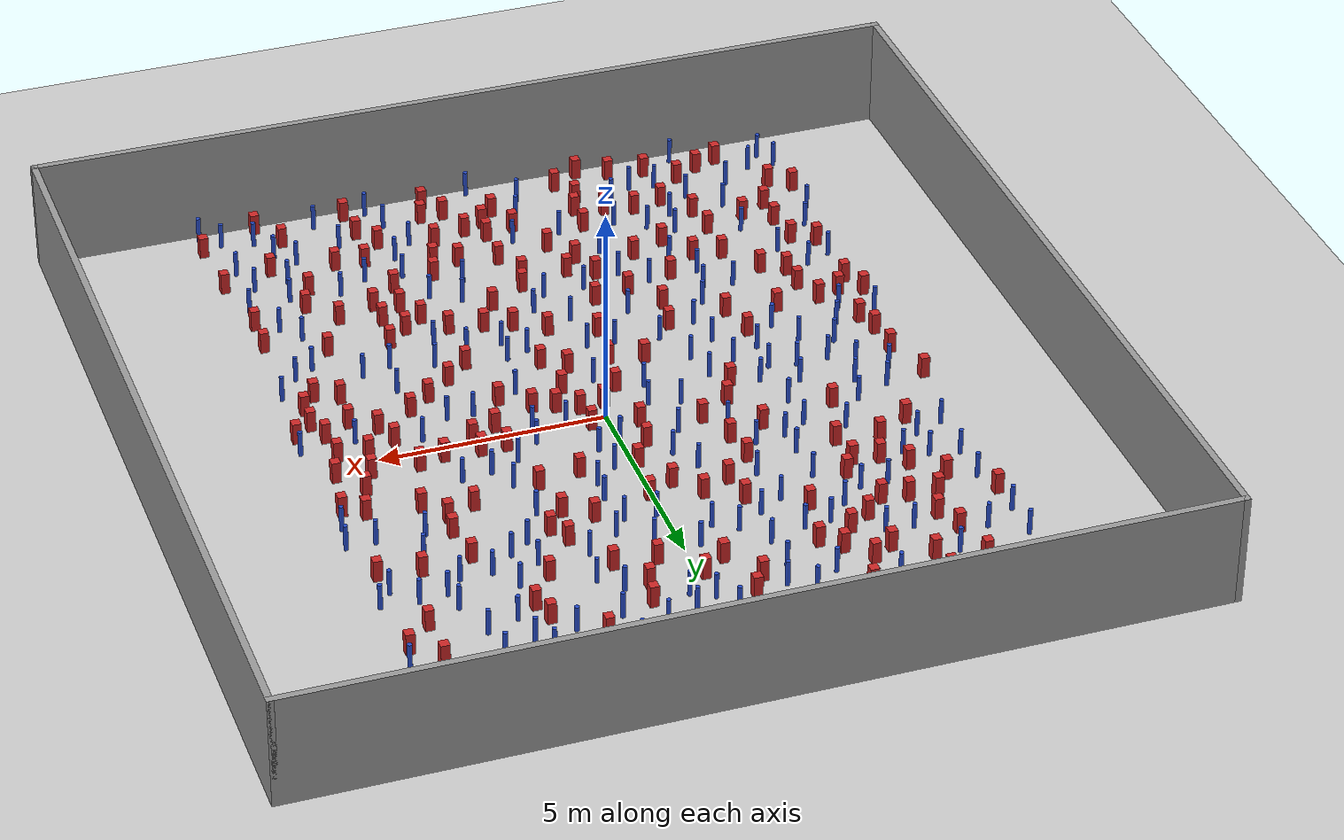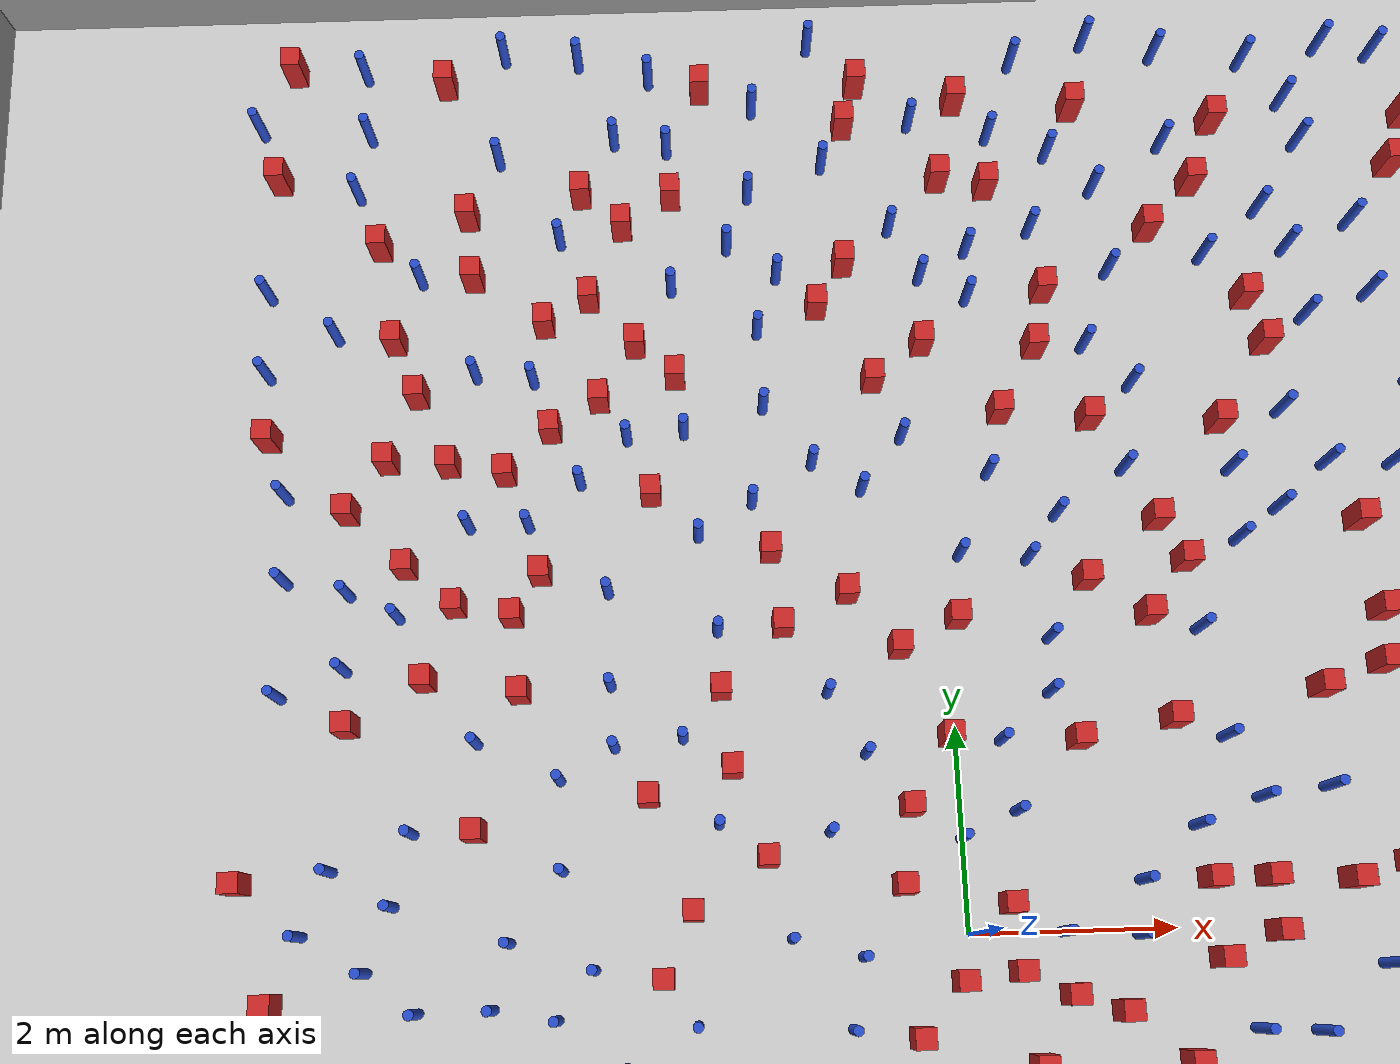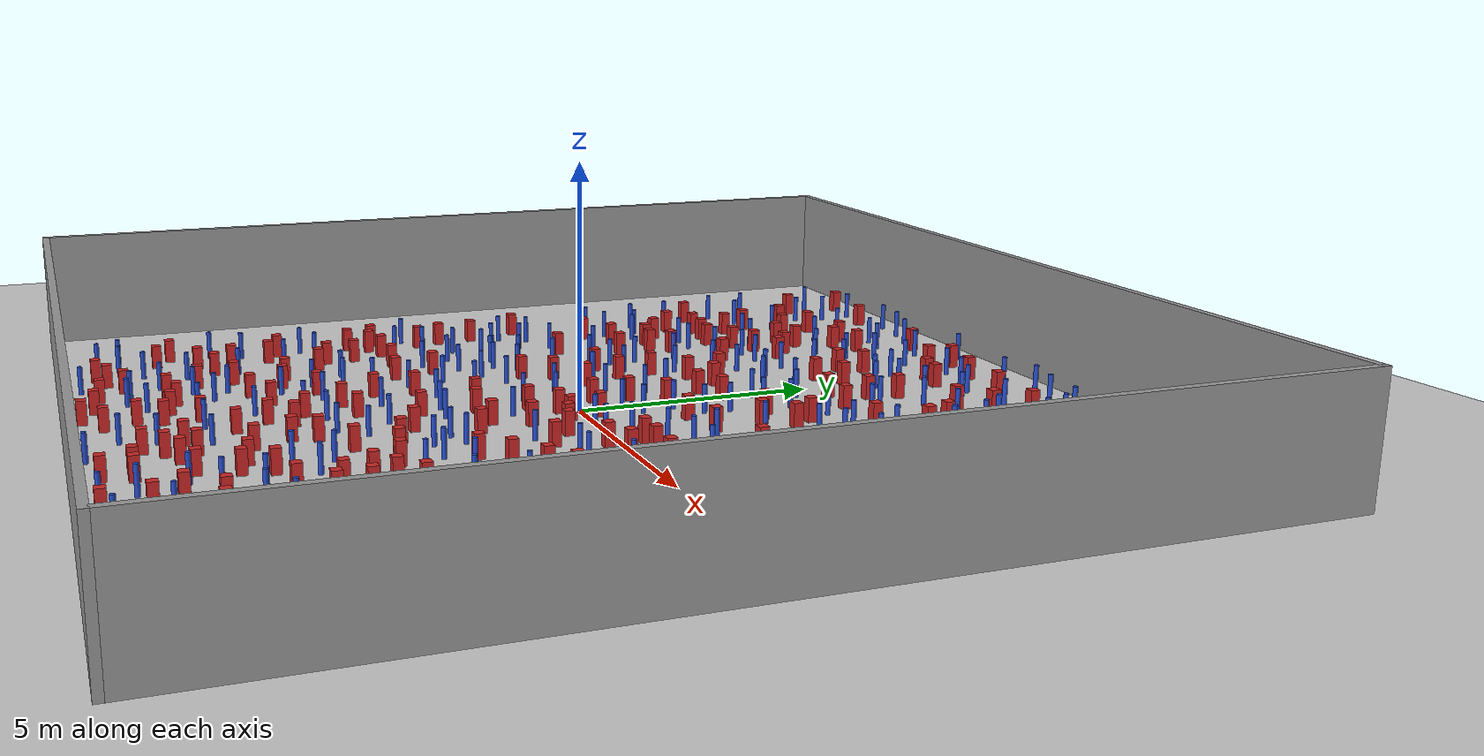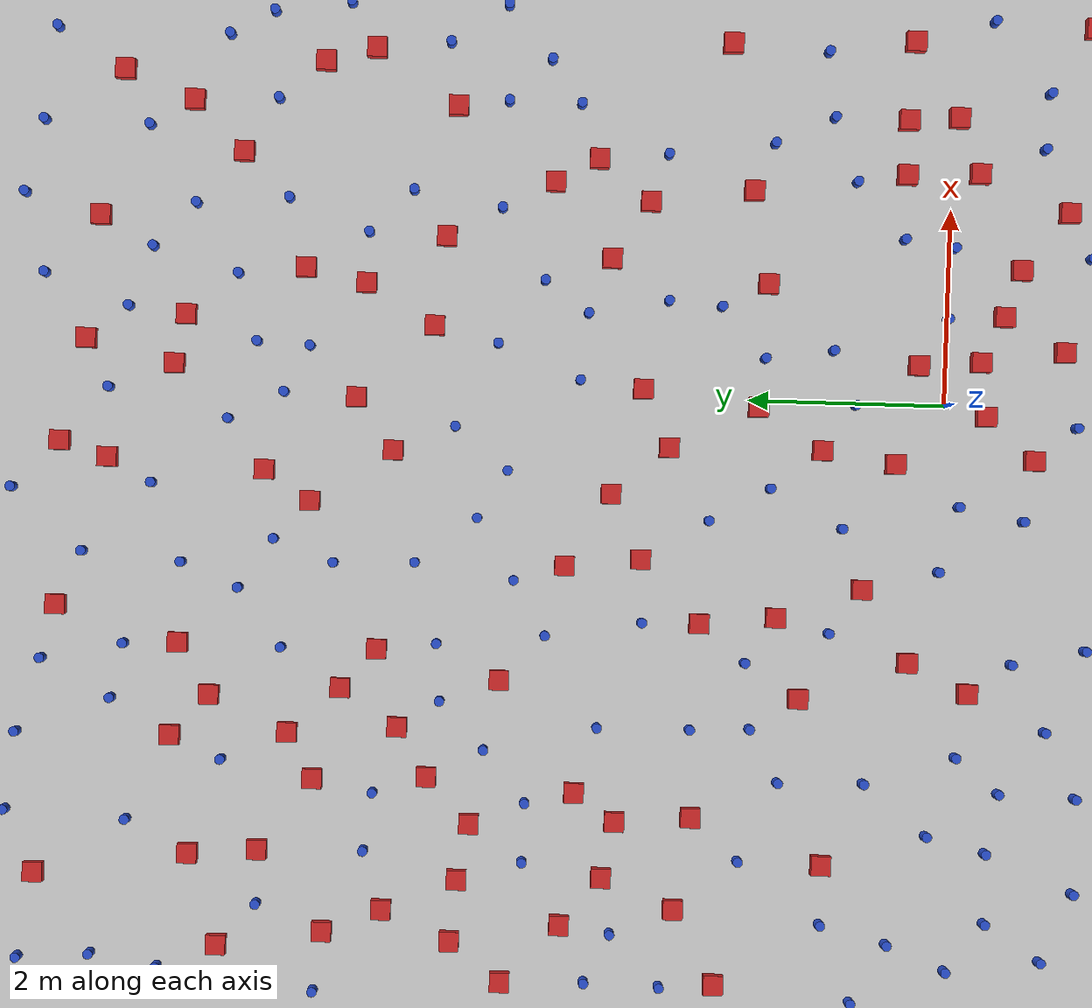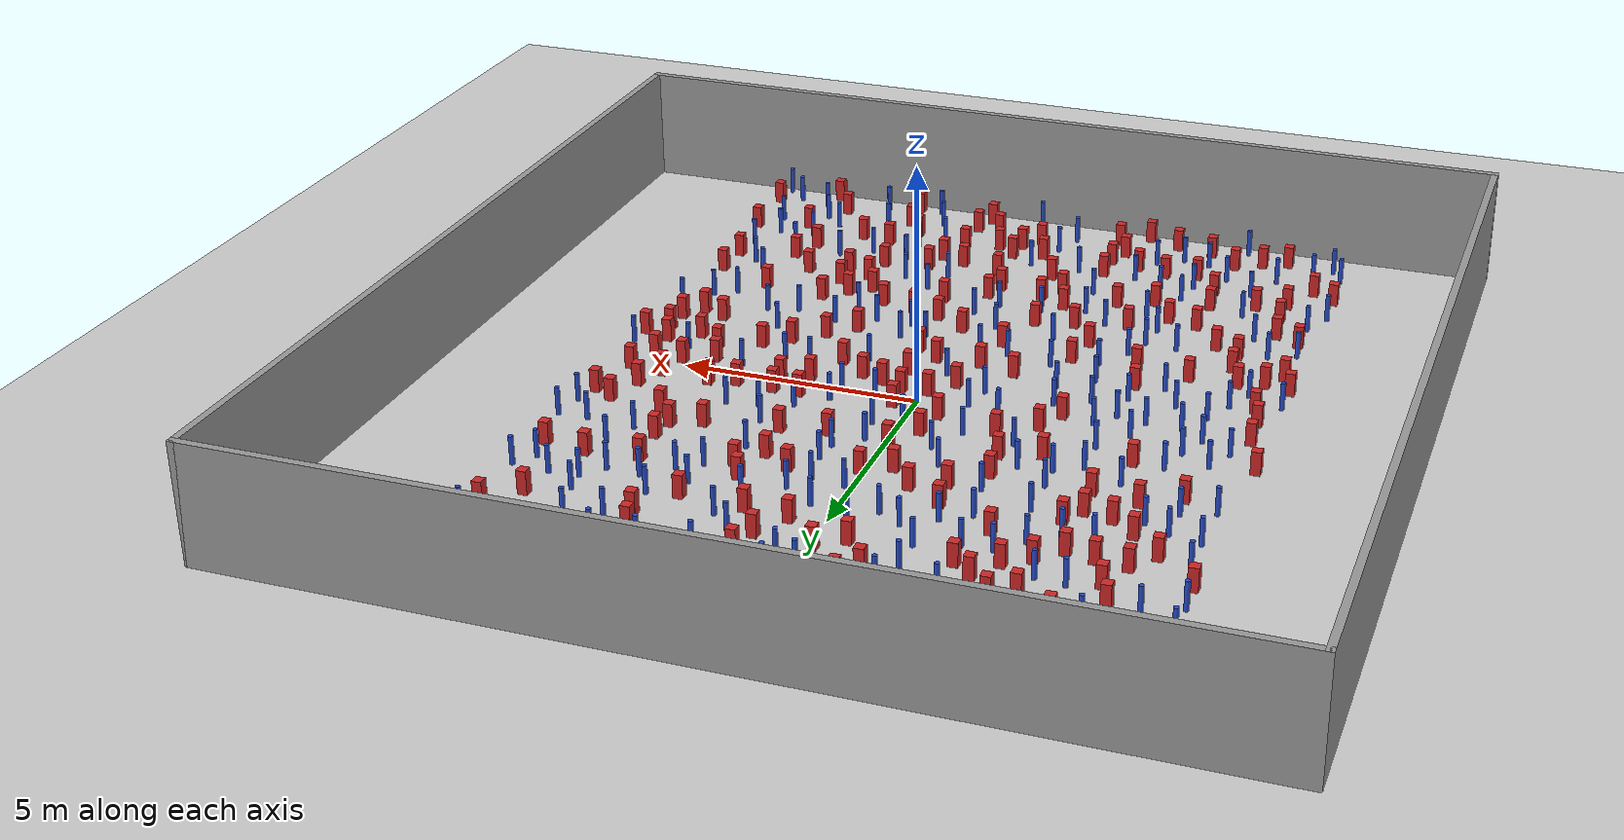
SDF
<sdf version="1.6">
 <world name="default">
  <light name="sun" type="directional">
   <pose>0 0 1000 0 -0 0</pose>
   <diffuse>0.8 0.8 0.8 1</diffuse>
   <specular>0.1 0.1 0.1 1</specular>
   <attenuation>
    <range>1000</range>
    <constant>0.9</constant>
    <linear>0.01</linear>
    <quadratic>0.001</quadratic>
   </attenuation>
   <direction>-0.5 0.5 -1</direction>
  </light>
  <model name="ground_plane">
   <static>1</static>
   <link name="link">
    <collision name="collision">
     <geometry><plane><normal>0 0 1</normal><size>100 100</size></plane></geometry>
     <surface><friction><ode><mu>100</mu><mu2>50</mu2></ode></friction></surface>
    </collision>
    <visual name="visual">
     <cast_shadows>0</cast_shadows>
     <geometry><plane><normal>0 0 1</normal><size>100 100</size></plane></geometry>
     <material>
      <ambient>1.0 1.0 1.0 1.0</ambient>
      <diffuse>0.8 0.8 0.8 1.0</diffuse>
      <specular>0.01 0.01 0.01 1.000000</specular>
     </material>
    </visual>
   </link>
  </model>
  <gravity>0 0 -9.8</gravity>
  <magnetic_field>6e-06 2.3e-05 -4.2e-05</magnetic_field>
  <atmosphere type="adiabatic"/>
  <physics name="default_physics" default="0" type="ode">
   <max_step_size>0.001</max_step_size>
   <real_time_factor>1</real_time_factor>
   <real_time_update_rate>1000</real_time_update_rate>
  </physics>
  <scene><ambient>0.4 0.4 0.4 1</ambient><background>0.7 0.7 0.7 1</background><shadows>1</shadows></scene>
  <spherical_coordinates>
   <surface_model>EARTH_WGS84</surface_model>
   <latitude_deg>0</latitude_deg>
   <longitude_deg>0</longitude_deg>
   <elevation>0</elevation>
   <heading_deg>0</heading_deg>
  </spherical_coordinates>
  <plugin name="gazebo_occupancy_map" filename="libgazebo_2Dmap_plugin.so">
   <map_resolution>0.05</map_resolution>
   <map_topic>generated_map</map_topic>
   <map_height>0.01</map_height>
   <map_size_x>50</map_size_x>
   <map_size_y>50</map_size_y>
  </plugin>
  <model name="NamedLocations">
   <static>true</static>
   <link name="DefaultStart"><pose>8.5 0 0 0 0 3.14</pose></link>
  </model>
  <model name="20x20_walls">
   <pose>0.044518 0.176112 0 0 -0 0</pose>
   <link name="Wall_1">
    <collision name="Wall_1_Collision">
     <geometry><box><size>20 0.15 2.5</size></box></geometry>
     <pose>0 0 1.25 0 -0 0</pose>
    </collision>
    <visual name="Wall_1_Visual">
     <pose>0 0 1.25 0 -0 0</pose>
     <geometry><box><size>20 0.15 2.5</size></box></geometry>
     <material>
      <script><uri>file://media/materials/scripts/gazebo.material</uri><name>Gazebo/Grey</name></script>
      <ambient>0.976471 0.992157 1 1</ambient>
     </material>
     <meta><layer>0</layer></meta>
    </visual>
    <pose>0 9.925 0 0 -0 0</pose>
   </link>
   <link name="Wall_3">
    <collision name="Wall_3_Collision">
     <geometry><box><size>20 0.15 2.5</size></box></geometry>
     <pose>0 0 1.25 0 -0 0</pose>
    </collision>
    <visual name="Wall_3_Visual">
     <pose>0 0 1.25 0 -0 0</pose>
     <geometry><box><size>20 0.15 2.5</size></box></geometry>
     <material>
      <script><uri>file://media/materials/scripts/gazebo.material</uri><name>Gazebo/Grey</name></script>
      <ambient>0.976471 0.992157 1 1</ambient>
     </material>
     <meta><layer>0</layer></meta>
    </visual>
    <pose>9.925 0 0 0 0 -1.5708</pose>
   </link>
   <link name="Wall_4">
    <collision name="Wall_4_Collision">
     <geometry><box><size>20 0.15 2.5</size></box></geometry>
     <pose>0 0 1.25 0 -0 0</pose>
    </collision>
    <visual name="Wall_4_Visual">
     <pose>0 0 1.25 0 -0 0</pose>
     <geometry><box><size>20 0.15 2.5</size></box></geometry>
     <material>
      <script><uri>file://media/materials/scripts/gazebo.material</uri><name>Gazebo/Grey</name></script>
      <ambient>0.976471 0.992157 1 1</ambient>
     </material>
     <meta><layer>0</layer></meta>
    </visual>
    <pose>0 -9.925 0 0 -0 3.14159</pose>
   </link>
   <link name="Wall_5">
    <collision name="Wall_5_Collision">
     <geometry><box><size>20 0.15 2.5</size></box></geometry>
     <pose>0 0 1.25 0 -0 0</pose>
    </collision>
    <visual name="Wall_5_Visual">
     <pose>0 0 1.25 0 -0 0</pose>
     <geometry><box><size>20 0.15 2.5</size></box></geometry>
     <material>
      <script><uri>file://media/materials/scripts/gazebo.material</uri><name>Gazebo/Grey</name></script>
      <ambient>0.976471 0.992157 1 1</ambient>
     </material>
     <meta><layer>0</layer></meta>
    </visual>
    <pose>-9.925 0 0 0 -0 1.5708</pose>
   </link>
   <static>1</static>
  </model>
  <model name="pole_obstacle0">
   <static>true</static>
   <pose>-1.75917018669 5.33562779901 2.88873142074e-08 -9.90536689852e-09 4.60219948989e-07 -1.2096599496e-07</pose>
   <link name="link">
    <pose>0 0 0.3 0 -0 0</pose>
    <inertial>
     <mass>1</mass>
     <inertia><ixx>0.145833</ixx><ixy>0</ixy><ixz>0</ixz><iyy>0.145833</iyy><iyz>0</iyz><izz>0.125</izz></inertia>
    </inertial>
    <collision name="collision">
     <geometry><cylinder><radius>0.05</radius><length>.6</length></cylinder></geometry>
    </collision>
    <visual name="visual">
     <geometry><cylinder><radius>0.05</radius><length>.6</length></cylinder></geometry>
     <material>
      <script><name>Gazebo/Blue</name><uri>file://media/materials/scripts/gazebo.material</uri></script>
     </material>
    </visual>
   </link>
  </model>
  <model name="pole_obstacle1">
   <static>true</static>
   <pose>-4.70056590658 5.76526155883 2.88873142074e-08 -9.90536690842e-09 4.60219948965e-07 -1.20965994976e-07</pose>
   <link name="link">
    <pose>0 0 0.3 0 -0 0</pose>
    <inertial>
     <mass>1</mass>
     <inertia><ixx>0.145833</ixx><ixy>0</ixy><ixz>0</ixz><iyy>0.145833</iyy><iyz>0</iyz><izz>0.125</izz></inertia>
    </inertial>
    <collision name="collision">
     <geometry><cylinder><radius>0.05</radius><length>.6</length></cylinder></geometry>
    </collision>
    <visual name="visual">
     <geometry><cylinder><radius>0.05</radius><length>.6</length></cylinder></geometry>
     <material>
      <script><name>Gazebo/Blue</name><uri>file://media/materials/scripts/gazebo.material</uri></script>
     </material>
    </visual>
   </link>
  </model>
  <model name="square_post_obstacle0">
   <static>true</static>
   <pose>1.72924373991 -6.90918453501 8.22691968438e-08 7.2212513382e-06 -7.54495500217e-07 2.29674213826e-05</pose>
   <link name="link">
    <pose>0 0 0.25 0 -0 0</pose>
    <inertial>
     <mass>100</mass>
     <inertia>
      <ixx>0.166667</ixx>
      <ixy>0</ixy>
      <ixz>0</ixz>
      <iyy>0.166667</iyy>
      <iyz>0</iyz>
      <izz>0.166667</izz>
     </inertia>
    </inertial>
    <collision name="collision"><geometry><box><size>.2 .2 .5</size></box></geometry></collision>
    <visual name="visual">
     <geometry><box><size>.2 .2 .5</size></box></geometry>
     <material>
      <script><name>Gazebo/Red</name><uri>file://media/materials/scripts/gazebo.material</uri></script>
     </material>
    </visual>
   </link>
  </model>
  <model name="square_post_obstacle1">
   <static>true</static>
   <pose>5.80485154844 1.86248550095 8.22691968438e-08 7.2212513382e-06 -7.54495500217e-07 2.29674213826e-05</pose>
   <link name="link">
    <pose>0 0 0.25 0 -0 0</pose>
    <inertial>
     <mass>100</mass>
     <inertia>
      <ixx>0.166667</ixx>
      <ixy>0</ixy>
      <ixz>0</ixz>
      <iyy>0.166667</iyy>
      <iyz>0</iyz>
      <izz>0.166667</izz>
     </inertia>
    </inertial>
    <collision name="collision"><geometry><box><size>.2 .2 .5</size></box></geometry></collision>
    <visual name="visual">
     <geometry><box><size>.2 .2 .5</size></box></geometry>
     <material>
      <script><name>Gazebo/Red</name><uri>file://media/materials/scripts/gazebo.material</uri></script>
     </material>
    </visual>
   </link>
  </model>
  <model name="pole_obstacle2">
   <static>true</static>
   <pose>-4.45726668055 8.1890683616 2.88873142074e-08 -9.9053668967e-09 4.60219948993e-07 -1.20965994957e-07</pose>
   <link name="link">
    <pose>0 0 0.3 0 -0 0</pose>
    <inertial>
     <mass>1</mass>
     <inertia><ixx>0.145833</ixx><ixy>0</ixy><ixz>0</ixz><iyy>0.145833</iyy><iyz>0</iyz><izz>0.125</izz></inertia>
    </inertial>
    <collision name="collision">
     <geometry><cylinder><radius>0.05</radius><length>.6</length></cylinder></geometry>
    </collision>
    <visual name="visual">
     <geometry><cylinder><radius>0.05</radius><length>.6</length></cylinder></geometry>
     <material>
      <script><name>Gazebo/Blue</name><uri>file://media/materials/scripts/gazebo.material</uri></script>
     </material>
    </visual>
   </link>
  </model>
  <model name="pole_obstacle3">
   <static>true</static>
   <pose>-0.223066158163 -7.18615148607 2.88873142074e-08 -9.90536689703e-09 4.60219948992e-07 -1.20965994959e-07</pose>
   <link name="link">
    <pose>0 0 0.3 0 -0 0</pose>
    <inertial>
     <mass>1</mass>
     <inertia><ixx>0.145833</ixx><ixy>0</ixy><ixz>0</ixz><iyy>0.145833</iyy><iyz>0</iyz><izz>0.125</izz></inertia>
    </inertial>
    <collision name="collision">
     <geometry><cylinder><radius>0.05</radius><length>.6</length></cylinder></geometry>
    </collision>
    <visual name="visual">
     <geometry><cylinder><radius>0.05</radius><length>.6</length></cylinder></geometry>
     <material>
      <script><name>Gazebo/Blue</name><uri>file://media/materials/scripts/gazebo.material</uri></script>
     </material>
    </visual>
   </link>
  </model>
  <model name="pole_obstacle4">
   <static>true</static>
   <pose>-5.26204661042 -6.04021006836 2.88873142074e-08 -9.90536690842e-09 4.60219948965e-07 -1.20965994976e-07</pose>
   <link name="link">
    <pose>0 0 0.3 0 -0 0</pose>
    <inertial>
     <mass>1</mass>
     <inertia><ixx>0.145833</ixx><ixy>0</ixy><ixz>0</ixz><iyy>0.145833</iyy><iyz>0</iyz><izz>0.125</izz></inertia>
    </inertial>
    <collision name="collision">
     <geometry><cylinder><radius>0.05</radius><length>.6</length></cylinder></geometry>
    </collision>
    <visual name="visual">
     <geometry><cylinder><radius>0.05</radius><length>.6</length></cylinder></geometry>
     <material>
      <script><name>Gazebo/Blue</name><uri>file://media/materials/scripts/gazebo.material</uri></script>
     </material>
    </visual>
   </link>
  </model>
  <model name="pole_obstacle5">
   <static>true</static>
   <pose>5.67499437362 -5.37067513522 2.88873142074e-08 -9.90536690842e-09 4.60219948965e-07 -1.20965994976e-07</pose>
   <link name="link">
    <pose>0 0 0.3 0 -0 0</pose>
    <inertial>
     <mass>1</mass>
     <inertia><ixx>0.145833</ixx><ixy>0</ixy><ixz>0</ixz><iyy>0.145833</iyy><iyz>0</iyz><izz>0.125</izz></inertia>
    </inertial>
    <collision name="collision">
     <geometry><cylinder><radius>0.05</radius><length>.6</length></cylinder></geometry>
    </collision>
    <visual name="visual">
     <geometry><cylinder><radius>0.05</radius><length>.6</length></cylinder></geometry>
     <material>
      <script><name>Gazebo/Blue</name><uri>file://media/materials/scripts/gazebo.material</uri></script>
     </material>
    </visual>
   </link>
  </model>
  <model name="pole_obstacle6">
   <static>true</static>
   <pose>1.87166272618 4.55720041785 2.88873142074e-08 -9.90536689852e-09 4.60219948989e-07 -1.2096599496e-07</pose>
   <link name="link">
    <pose>0 0 0.3 0 -0 0</pose>
    <inertial>
     <mass>1</mass>
     <inertia><ixx>0.145833</ixx><ixy>0</ixy><ixz>0</ixz><iyy>0.145833</iyy><iyz>0</iyz><izz>0.125</izz></inertia>
    </inertial>
    <collision name="collision">
     <geometry><cylinder><radius>0.05</radius><length>.6</length></cylinder></geometry>
    </collision>
    <visual name="visual">
     <geometry><cylinder><radius>0.05</radius><length>.6</length></cylinder></geometry>
     <material>
      <script><name>Gazebo/Blue</name><uri>file://media/materials/scripts/gazebo.material</uri></script>
     </material>
    </visual>
   </link>
  </model>
  <model name="square_post_obstacle2">
   <static>true</static>
   <pose>0.221696725759 -1.90196667918 8.22691968438e-08 7.2212513382e-06 -7.54495500217e-07 2.29674213826e-05</pose>
   <link name="link">
    <pose>0 0 0.25 0 -0 0</pose>
    <inertial>
     <mass>100</mass>
     <inertia>
      <ixx>0.166667</ixx>
      <ixy>0</ixy>
      <ixz>0</ixz>
      <iyy>0.166667</iyy>
      <iyz>0</iyz>
      <izz>0.166667</izz>
     </inertia>
    </inertial>
    <collision name="collision"><geometry><box><size>.2 .2 .5</size></box></geometry></collision>
    <visual name="visual">
     <geometry><box><size>.2 .2 .5</size></box></geometry>
     <material>
      <script><name>Gazebo/Red</name><uri>file://media/materials/scripts/gazebo.material</uri></script>
     </material>
    </visual>
   </link>
  </model>
  <model name="square_post_obstacle3">
   <static>true</static>
   <pose>-5.62151948386 -3.42446716188 8.22691968438e-08 7.2212513382e-06 -7.54495500217e-07 2.29674213826e-05</pose>
   <link name="link">
    <pose>0 0 0.25 0 -0 0</pose>
    <inertial>
     <mass>100</mass>
     <inertia>
      <ixx>0.166667</ixx>
      <ixy>0</ixy>
      <ixz>0</ixz>
      <iyy>0.166667</iyy>
      <iyz>0</iyz>
      <izz>0.166667</izz>
     </inertia>
    </inertial>
    <collision name="collision"><geometry><box><size>.2 .2 .5</size></box></geometry></collision>
    <visual name="visual">
     <geometry><box><size>.2 .2 .5</size></box></geometry>
     <material>
      <script><name>Gazebo/Red</name><uri>file://media/materials/scripts/gazebo.material</uri></script>
     </material>
    </visual>
   </link>
  </model>
  <model name="square_post_obstacle4">
   <static>true</static>
   <pose>1.47101425126 -7.66922234717 8.22691968438e-08 7.2212513382e-06 -7.54495500217e-07 2.29674213826e-05</pose>
   <link name="link">
    <pose>0 0 0.25 0 -0 0</pose>
    <inertial>
     <mass>100</mass>
     <inertia>
      <ixx>0.166667</ixx>
      <ixy>0</ixy>
      <ixz>0</ixz>
      <iyy>0.166667</iyy>
      <iyz>0</iyz>
      <izz>0.166667</izz>
     </inertia>
    </inertial>
    <collision name="collision"><geometry><box><size>.2 .2 .5</size></box></geometry></collision>
    <visual name="visual">
     <geometry><box><size>.2 .2 .5</size></box></geometry>
     <material>
      <script><name>Gazebo/Red</name><uri>file://media/materials/scripts/gazebo.material</uri></script>
     </material>
    </visual>
   </link>
  </model>
  <model name="pole_obstacle7">
   <static>true</static>
   <pose>-3.41852707502 -3.4730363077 2.88873142074e-08 -9.90536690232e-09 4.6021994898e-07 -1.20965994968e-07</pose>
   <link name="link">
    <pose>0 0 0.3 0 -0 0</pose>
    <inertial>
     <mass>1</mass>
     <inertia><ixx>0.145833</ixx><ixy>0</ixy><ixz>0</ixz><iyy>0.145833</iyy><iyz>0</iyz><izz>0.125</izz></inertia>
    </inertial>
    <collision name="collision">
     <geometry><cylinder><radius>0.05</radius><length>.6</length></cylinder></geometry>
    </collision>
    <visual name="visual">
     <geometry><cylinder><radius>0.05</radius><length>.6</length></cylinder></geometry>
     <material>
      <script><name>Gazebo/Blue</name><uri>file://media/materials/scripts/gazebo.material</uri></script>
     </material>
    </visual>
   </link>
  </model>
  <model name="pole_obstacle8">
   <static>true</static>
   <pose>-6.08702871767 0.780970293844 2.88873142074e-08 -9.90536689837e-09 4.60219948989e-07 -1.2096599496e-07</pose>
   <link name="link">
    <pose>0 0 0.3 0 -0 0</pose>
    <inertial>
     <mass>1</mass>
     <inertia><ixx>0.145833</ixx><ixy>0</ixy><ixz>0</ixz><iyy>0.145833</iyy><iyz>0</iyz><izz>0.125</izz></inertia>
    </inertial>
    <collision name="collision">
     <geometry><cylinder><radius>0.05</radius><length>.6</length></cylinder></geometry>
    </collision>
    <visual name="visual">
     <geometry><cylinder><radius>0.05</radius><length>.6</length></cylinder></geometry>
     <material>
      <script><name>Gazebo/Blue</name><uri>file://media/materials/scripts/gazebo.material</uri></script>
     </material>
    </visual>
   </link>
  </model>
  <model name="square_post_obstacle5">
   <static>true</static>
   <pose>-6.39773132126 -2.92644080052 8.22691968438e-08 7.2212513382e-06 -7.54495500217e-07 2.29674213826e-05</pose>
   <link name="link">
    <pose>0 0 0.25 0 -0 0</pose>
    <inertial>
     <mass>100</mass>
     <inertia>
      <ixx>0.166667</ixx>
      <ixy>0</ixy>
      <ixz>0</ixz>
      <iyy>0.166667</iyy>
      <iyz>0</iyz>
      <izz>0.166667</izz>
     </inertia>
    </inertial>
    <collision name="collision"><geometry><box><size>.2 .2 .5</size></box></geometry></collision>
    <visual name="visual">
     <geometry><box><size>.2 .2 .5</size></box></geometry>
     <material>
      <script><name>Gazebo/Red</name><uri>file://media/materials/scripts/gazebo.material</uri></script>
     </material>
    </visual>
   </link>
  </model>
  <model name="square_post_obstacle6">
   <static>true</static>
   <pose>1.56429771834 5.11346397631 8.22691968438e-08 7.2212513382e-06 -7.54495500217e-07 2.29674213826e-05</pose>
   <link name="link">
    <pose>0 0 0.25 0 -0 0</pose>
    <inertial>
     <mass>100</mass>
     <inertia>
      <ixx>0.166667</ixx>
      <ixy>0</ixy>
      <ixz>0</ixz>
      <iyy>0.166667</iyy>
      <iyz>0</iyz>
      <izz>0.166667</izz>
     </inertia>
    </inertial>
    <collision name="collision"><geometry><box><size>.2 .2 .5</size></box></geometry></collision>
    <visual name="visual">
     <geometry><box><size>.2 .2 .5</size></box></geometry>
     <material>
      <script><name>Gazebo/Red</name><uri>file://media/materials/scripts/gazebo.material</uri></script>
     </material>
    </visual>
   </link>
  </model>
  <model name="square_post_obstacle7">
   <static>true</static>
   <pose>-2.65024119042 5.69490103265 8.22691968438e-08 7.2212513382e-06 -7.54495500217e-07 2.29674213826e-05</pose>
   <link name="link">
    <pose>0 0 0.25 0 -0 0</pose>
    <inertial>
     <mass>100</mass>
     <inertia>
      <ixx>0.166667</ixx>
      <ixy>0</ixy>
      <ixz>0</ixz>
      <iyy>0.166667</iyy>
      <iyz>0</iyz>
      <izz>0.166667</izz>
     </inertia>
    </inertial>
    <collision name="collision"><geometry><box><size>.2 .2 .5</size></box></geometry></collision>
    <visual name="visual">
     <geometry><box><size>.2 .2 .5</size></box></geometry>
     <material>
      <script><name>Gazebo/Red</name><uri>file://media/materials/scripts/gazebo.material</uri></script>
     </material>
    </visual>
   </link>
  </model>
  <model name="pole_obstacle9">
   <static>true</static>
   <pose>-5.60788954177 -8.01371110021 2.88873142074e-08 -9.9053669103e-09 4.60219948961e-07 -1.20965994981e-07</pose>
   <link name="link">
    <pose>0 0 0.3 0 -0 0</pose>
    <inertial>
     <mass>1</mass>
     <inertia><ixx>0.145833</ixx><ixy>0</ixy><ixz>0</ixz><iyy>0.145833</iyy><iyz>0</iyz><izz>0.125</izz></inertia>
    </inertial>
    <collision name="collision">
     <geometry><cylinder><radius>0.05</radius><length>.6</length></cylinder></geometry>
    </collision>
    <visual name="visual">
     <geometry><cylinder><radius>0.05</radius><length>.6</length></cylinder></geometry>
     <material>
      <script><name>Gazebo/Blue</name><uri>file://media/materials/scripts/gazebo.material</uri></script>
     </material>
    </visual>
   </link>
  </model>
  <model name="pole_obstacle10">
   <static>true</static>
   <pose>4.44744639522 -3.07453793529 2.88873142074e-08 -9.90536690245e-09 4.6021994898e-07 -1.20965994966e-07</pose>
   <link name="link">
    <pose>0 0 0.3 0 -0 0</pose>
    <inertial>
     <mass>1</mass>
     <inertia><ixx>0.145833</ixx><ixy>0</ixy><ixz>0</ixz><iyy>0.145833</iyy><iyz>0</iyz><izz>0.125</izz></inertia>
    </inertial>
    <collision name="collision">
     <geometry><cylinder><radius>0.05</radius><length>.6</length></cylinder></geometry>
    </collision>
    <visual name="visual">
     <geometry><cylinder><radius>0.05</radius><length>.6</length></cylinder></geometry>
     <material>
      <script><name>Gazebo/Blue</name><uri>file://media/materials/scripts/gazebo.material</uri></script>
     </material>
    </visual>
   </link>
  </model>
  <model name="pole_obstacle11">
   <static>true</static>
   <pose>2.61440782523 1.80878692361 2.88873142074e-08 -9.90536689395e-09 4.60219949e-07 -1.20965994953e-07</pose>
   <link name="link">
    <pose>0 0 0.3 0 -0 0</pose>
    <inertial>
     <mass>1</mass>
     <inertia><ixx>0.145833</ixx><ixy>0</ixy><ixz>0</ixz><iyy>0.145833</iyy><iyz>0</iyz><izz>0.125</izz></inertia>
    </inertial>
    <collision name="collision">
     <geometry><cylinder><radius>0.05</radius><length>.6</length></cylinder></geometry>
    </collision>
    <visual name="visual">
     <geometry><cylinder><radius>0.05</radius><length>.6</length></cylinder></geometry>
     <material>
      <script><name>Gazebo/Blue</name><uri>file://media/materials/scripts/gazebo.material</uri></script>
     </material>
    </visual>
   </link>
  </model>
  <model name="pole_obstacle12">
   <static>true</static>
   <pose>-4.53100883687 -0.543912162179 2.88873142074e-08 -9.90536689968e-09 4.60219948986e-07 -1.20965994963e-07</pose>
   <link name="link">
    <pose>0 0 0.3 0 -0 0</pose>
    <inertial>
     <mass>1</mass>
     <inertia><ixx>0.145833</ixx><ixy>0</ixy><ixz>0</ixz><iyy>0.145833</iyy><iyz>0</iyz><izz>0.125</izz></inertia>
    </inertial>
    <collision name="collision">
     <geometry><cylinder><radius>0.05</radius><length>.6</length></cylinder></geometry>
    </collision>
    <visual name="visual">
     <geometry><cylinder><radius>0.05</radius><length>.6</length></cylinder></geometry>
     <material>
      <script><name>Gazebo/Blue</name><uri>file://media/materials/scripts/gazebo.material</uri></script>
     </material>
    </visual>
   </link>
  </model>
  <model name="square_post_obstacle8">
   <static>true</static>
   <pose>-5.08560462656 -4.32271295964 8.22691968438e-08 7.2212513382e-06 -7.54495500217e-07 2.29674213826e-05</pose>
   <link name="link">
    <pose>0 0 0.25 0 -0 0</pose>
    <inertial>
     <mass>100</mass>
     <inertia>
      <ixx>0.166667</ixx>
      <ixy>0</ixy>
      <ixz>0</ixz>
      <iyy>0.166667</iyy>
      <iyz>0</iyz>
      <izz>0.166667</izz>
     </inertia>
    </inertial>
    <collision name="collision"><geometry><box><size>.2 .2 .5</size></box></geometry></collision>
    <visual name="visual">
     <geometry><box><size>.2 .2 .5</size></box></geometry>
     <material>
      <script><name>Gazebo/Red</name><uri>file://media/materials/scripts/gazebo.material</uri></script>
     </material>
    </visual>
   </link>
  </model>
  <model name="square_post_obstacle9">
   <static>true</static>
   <pose>-4.78377792327 7.54915396914 8.22691968438e-08 7.22125133819e-06 -7.54495500217e-07 2.29674213826e-05</pose>
   <link name="link">
    <pose>0 0 0.25 0 -0 0</pose>
    <inertial>
     <mass>100</mass>
     <inertia>
      <ixx>0.166667</ixx>
      <ixy>0</ixy>
      <ixz>0</ixz>
      <iyy>0.166667</iyy>
      <iyz>0</iyz>
      <izz>0.166667</izz>
     </inertia>
    </inertial>
    <collision name="collision"><geometry><box><size>.2 .2 .5</size></box></geometry></collision>
    <visual name="visual">
     <geometry><box><size>.2 .2 .5</size></box></geometry>
     <material>
      <script><name>Gazebo/Red</name><uri>file://media/materials/scripts/gazebo.material</uri></script>
     </material>
    </visual>
   </link>
  </model>
  <model name="pole_obstacle13">
   <static>true</static>
   <pose>3.20647940545 -0.969881316611 2.88873142074e-08 -9.90536689217e-09 4.60219949004e-07 -1.20965994953e-07</pose>
   <link name="link">
    <pose>0 0 0.3 0 -0 0</pose>
    <inertial>
     <mass>1</mass>
     <inertia><ixx>0.145833</ixx><ixy>0</ixy><ixz>0</ixz><iyy>0.145833</iyy><iyz>0</iyz><izz>0.125</izz></inertia>
    </inertial>
    <collision name="collision">
     <geometry><cylinder><radius>0.05</radius><length>.6</length></cylinder></geometry>
    </collision>
    <visual name="visual">
     <geometry><cylinder><radius>0.05</radius><length>.6</length></cylinder></geometry>
     <material>
      <script><name>Gazebo/Blue</name><uri>file://media/materials/scripts/gazebo.material</uri></script>
     </material>
    </visual>
   </link>
  </model>
  <model name="square_post_obstacle10">
   <static>true</static>
   <pose>3.87964929043 -1.40677528351 8.22691968438e-08 7.2212513382e-06 -7.54495500217e-07 2.29674213826e-05</pose>
   <link name="link">
    <pose>0 0 0.25 0 -0 0</pose>
    <inertial>
     <mass>100</mass>
     <inertia>
      <ixx>0.166667</ixx>
      <ixy>0</ixy>
      <ixz>0</ixz>
      <iyy>0.166667</iyy>
      <iyz>0</iyz>
      <izz>0.166667</izz>
     </inertia>
    </inertial>
    <collision name="collision"><geometry><box><size>.2 .2 .5</size></box></geometry></collision>
    <visual name="visual">
     <geometry><box><size>.2 .2 .5</size></box></geometry>
     <material>
      <script><name>Gazebo/Red</name><uri>file://media/materials/scripts/gazebo.material</uri></script>
     </material>
    </visual>
   </link>
  </model>
  <model name="square_post_obstacle11">
   <static>true</static>
   <pose>2.86878469184 7.71550263755 8.22691968438e-08 7.2212513382e-06 -7.54495500217e-07 2.29674213826e-05</pose>
   <link name="link">
    <pose>0 0 0.25 0 -0 0</pose>
    <inertial>
     <mass>100</mass>
     <inertia>
      <ixx>0.166667</ixx>
      <ixy>0</ixy>
      <ixz>0</ixz>
      <iyy>0.166667</iyy>
      <iyz>0</iyz>
      <izz>0.166667</izz>
     </inertia>
    </inertial>
    <collision name="collision"><geometry><box><size>.2 .2 .5</size></box></geometry></collision>
    <visual name="visual">
     <geometry><box><size>.2 .2 .5</size></box></geometry>
     <material>
      <script><name>Gazebo/Red</name><uri>file://media/materials/scripts/gazebo.material</uri></script>
     </material>
    </visual>
   </link>
  </model>
  <model name="pole_obstacle14">
   <static>true</static>
   <pose>1.8775066064 9.40847270662 2.88873142074e-08 -9.90536690474e-09 4.60219948974e-07 -1.2096599497e-07</pose>
   <link name="link">
    <pose>0 0 0.3 0 -0 0</pose>
    <inertial>
     <mass>1</mass>
     <inertia><ixx>0.145833</ixx><ixy>0</ixy><ixz>0</ixz><iyy>0.145833</iyy><iyz>0</iyz><izz>0.125</izz></inertia>
    </inertial>
    <collision name="collision">
     <geometry><cylinder><radius>0.05</radius><length>.6</length></cylinder></geometry>
    </collision>
    <visual name="visual">
     <geometry><cylinder><radius>0.05</radius><length>.6</length></cylinder></geometry>
     <material>
      <script><name>Gazebo/Blue</name><uri>file://media/materials/scripts/gazebo.material</uri></script>
     </material>
    </visual>
   </link>
  </model>
  <model name="pole_obstacle15">
   <static>true</static>
   <pose>-1.13466148341 -4.8690241705 2.88873142074e-08 -9.90536689852e-09 4.60219948989e-07 -1.2096599496e-07</pose>
   <link name="link">
    <pose>0 0 0.3 0 -0 0</pose>
    <inertial>
     <mass>1</mass>
     <inertia><ixx>0.145833</ixx><ixy>0</ixy><ixz>0</ixz><iyy>0.145833</iyy><iyz>0</iyz><izz>0.125</izz></inertia>
    </inertial>
    <collision name="collision">
     <geometry><cylinder><radius>0.05</radius><length>.6</length></cylinder></geometry>
    </collision>
    <visual name="visual">
     <geometry><cylinder><radius>0.05</radius><length>.6</length></cylinder></geometry>
     <material>
      <script><name>Gazebo/Blue</name><uri>file://media/materials/scripts/gazebo.material</uri></script>
     </material>
    </visual>
   </link>
  </model>
  <model name="square_post_obstacle12">
   <static>true</static>
   <pose>-6.67316931984 -4.98831161575 8.22691968438e-08 7.2212513382e-06 -7.54495500217e-07 2.29674213826e-05</pose>
   <link name="link">
    <pose>0 0 0.25 0 -0 0</pose>
    <inertial>
     <mass>100</mass>
     <inertia>
      <ixx>0.166667</ixx>
      <ixy>0</ixy>
      <ixz>0</ixz>
      <iyy>0.166667</iyy>
      <iyz>0</iyz>
      <izz>0.166667</izz>
     </inertia>
    </inertial>
    <collision name="collision"><geometry><box><size>.2 .2 .5</size></box></geometry></collision>
    <visual name="visual">
     <geometry><box><size>.2 .2 .5</size></box></geometry>
     <material>
      <script><name>Gazebo/Red</name><uri>file://media/materials/scripts/gazebo.material</uri></script>
     </material>
    </visual>
   </link>
  </model>
  <model name="pole_obstacle16">
   <static>true</static>
   <pose>1.67860031516 0.463733786969 2.88873142074e-08 -9.90536689788e-09 4.6021994899e-07 -1.2096599496e-07</pose>
   <link name="link">
    <pose>0 0 0.3 0 -0 0</pose>
    <inertial>
     <mass>1</mass>
     <inertia><ixx>0.145833</ixx><ixy>0</ixy><ixz>0</ixz><iyy>0.145833</iyy><iyz>0</iyz><izz>0.125</izz></inertia>
    </inertial>
    <collision name="collision">
     <geometry><cylinder><radius>0.05</radius><length>.6</length></cylinder></geometry>
    </collision>
    <visual name="visual">
     <geometry><cylinder><radius>0.05</radius><length>.6</length></cylinder></geometry>
     <material>
      <script><name>Gazebo/Blue</name><uri>file://media/materials/scripts/gazebo.material</uri></script>
     </material>
    </visual>
   </link>
  </model>
  <model name="pole_obstacle17">
   <static>true</static>
   <pose>-0.0674727620844 6.71778246287 2.88873142074e-08 -9.90536689653e-09 4.60219948994e-07 -1.20965994959e-07</pose>
   <link name="link">
    <pose>0 0 0.3 0 -0 0</pose>
    <inertial>
     <mass>1</mass>
     <inertia><ixx>0.145833</ixx><ixy>0</ixy><ixz>0</ixz><iyy>0.145833</iyy><iyz>0</iyz><izz>0.125</izz></inertia>
    </inertial>
    <collision name="collision">
     <geometry><cylinder><radius>0.05</radius><length>.6</length></cylinder></geometry>
    </collision>
    <visual name="visual">
     <geometry><cylinder><radius>0.05</radius><length>.6</length></cylinder></geometry>
     <material>
      <script><name>Gazebo/Blue</name><uri>file://media/materials/scripts/gazebo.material</uri></script>
     </material>
    </visual>
   </link>
  </model>
  <model name="square_post_obstacle13">
   <static>true</static>
   <pose>1.01495852833 -4.76390678284 8.22691968438e-08 7.2212513382e-06 -7.54495500217e-07 2.29674213826e-05</pose>
   <link name="link">
    <pose>0 0 0.25 0 -0 0</pose>
    <inertial>
     <mass>100</mass>
     <inertia>
      <ixx>0.166667</ixx>
      <ixy>0</ixy>
      <ixz>0</ixz>
      <iyy>0.166667</iyy>
      <iyz>0</iyz>
      <izz>0.166667</izz>
     </inertia>
    </inertial>
    <collision name="collision"><geometry><box><size>.2 .2 .5</size></box></geometry></collision>
    <visual name="visual">
     <geometry><box><size>.2 .2 .5</size></box></geometry>
     <material>
      <script><name>Gazebo/Red</name><uri>file://media/materials/scripts/gazebo.material</uri></script>
     </material>
    </visual>
   </link>
  </model>
  <model name="pole_obstacle18">
   <static>true</static>
   <pose>-2.46120198781 3.99202360485 2.88873142074e-08 -9.90536690801e-09 4.60219948966e-07 -1.20965994976e-07</pose>
   <link name="link">
    <pose>0 0 0.3 0 -0 0</pose>
    <inertial>
     <mass>1</mass>
     <inertia><ixx>0.145833</ixx><ixy>0</ixy><ixz>0</ixz><iyy>0.145833</iyy><iyz>0</iyz><izz>0.125</izz></inertia>
    </inertial>
    <collision name="collision">
     <geometry><cylinder><radius>0.05</radius><length>.6</length></cylinder></geometry>
    </collision>
    <visual name="visual">
     <geometry><cylinder><radius>0.05</radius><length>.6</length></cylinder></geometry>
     <material>
      <script><name>Gazebo/Blue</name><uri>file://media/materials/scripts/gazebo.material</uri></script>
     </material>
    </visual>
   </link>
  </model>
  <model name="square_post_obstacle14">
   <static>true</static>
   <pose>5.69747027684 7.0240183476 8.22691968438e-08 7.2212513382e-06 -7.54495500217e-07 2.29674213826e-05</pose>
   <link name="link">
    <pose>0 0 0.25 0 -0 0</pose>
    <inertial>
     <mass>100</mass>
     <inertia>
      <ixx>0.166667</ixx>
      <ixy>0</ixy>
      <ixz>0</ixz>
      <iyy>0.166667</iyy>
      <iyz>0</iyz>
      <izz>0.166667</izz>
     </inertia>
    </inertial>
    <collision name="collision"><geometry><box><size>.2 .2 .5</size></box></geometry></collision>
    <visual name="visual">
     <geometry><box><size>.2 .2 .5</size></box></geometry>
     <material>
      <script><name>Gazebo/Red</name><uri>file://media/materials/scripts/gazebo.material</uri></script>
     </material>
    </visual>
   </link>
  </model>
  <model name="pole_obstacle19">
   <static>true</static>
   <pose>-4.16638657633 4.14378427516 2.88873142074e-08 -9.90536690842e-09 4.60219948965e-07 -1.20965994976e-07</pose>
   <link name="link">
    <pose>0 0 0.3 0 -0 0</pose>
    <inertial>
     <mass>1</mass>
     <inertia><ixx>0.145833</ixx><ixy>0</ixy><ixz>0</ixz><iyy>0.145833</iyy><iyz>0</iyz><izz>0.125</izz></inertia>
    </inertial>
    <collision name="collision">
     <geometry><cylinder><radius>0.05</radius><length>.6</length></cylinder></geometry>
    </collision>
    <visual name="visual">
     <geometry><cylinder><radius>0.05</radius><length>.6</length></cylinder></geometry>
     <material>
      <script><name>Gazebo/Blue</name><uri>file://media/materials/scripts/gazebo.material</uri></script>
     </material>
    </visual>
   </link>
  </model>
  <model name="square_post_obstacle15">
   <static>true</static>
   <pose>2.78507070101 -2.26868465725 8.22691968438e-08 7.2212513382e-06 -7.54495500217e-07 2.29674213826e-05</pose>
   <link name="link">
    <pose>0 0 0.25 0 -0 0</pose>
    <inertial>
     <mass>100</mass>
     <inertia>
      <ixx>0.166667</ixx>
      <ixy>0</ixy>
      <ixz>0</ixz>
      <iyy>0.166667</iyy>
      <iyz>0</iyz>
      <izz>0.166667</izz>
     </inertia>
    </inertial>
    <collision name="collision"><geometry><box><size>.2 .2 .5</size></box></geometry></collision>
    <visual name="visual">
     <geometry><box><size>.2 .2 .5</size></box></geometry>
     <material>
      <script><name>Gazebo/Red</name><uri>file://media/materials/scripts/gazebo.material</uri></script>
     </material>
    </visual>
   </link>
  </model>
  <model name="square_post_obstacle16">
   <static>true</static>
   <pose>1.39110884034 3.42909888853 8.22691968438e-08 7.2212513382e-06 -7.54495500217e-07 2.29674213826e-05</pose>
   <link name="link">
    <pose>0 0 0.25 0 -0 0</pose>
    <inertial>
     <mass>100</mass>
     <inertia>
      <ixx>0.166667</ixx>
      <ixy>0</ixy>
      <ixz>0</ixz>
      <iyy>0.166667</iyy>
      <iyz>0</iyz>
      <izz>0.166667</izz>
     </inertia>
    </inertial>
    <collision name="collision"><geometry><box><size>.2 .2 .5</size></box></geometry></collision>
    <visual name="visual">
     <geometry><box><size>.2 .2 .5</size></box></geometry>
     <material>
      <script><name>Gazebo/Red</name><uri>file://media/materials/scripts/gazebo.material</uri></script>
     </material>
    </visual>
   </link>
  </model>
  <model name="square_post_obstacle17">
   <static>true</static>
   <pose>-4.39659818621 4.70377155817 8.22691968438e-08 7.2212513382e-06 -7.54495500217e-07 2.29674213826e-05</pose>
   <link name="link">
    <pose>0 0 0.25 0 -0 0</pose>
    <inertial>
     <mass>100</mass>
     <inertia>
      <ixx>0.166667</ixx>
      <ixy>0</ixy>
      <ixz>0</ixz>
      <iyy>0.166667</iyy>
      <iyz>0</iyz>
      <izz>0.166667</izz>
     </inertia>
    </inertial>
    <collision name="collision"><geometry><box><size>.2 .2 .5</size></box></geometry></collision>
    <visual name="visual">
     <geometry><box><size>.2 .2 .5</size></box></geometry>
     <material>
      <script><name>Gazebo/Red</name><uri>file://media/materials/scripts/gazebo.material</uri></script>
     </material>
    </visual>
   </link>
  </model>
  <model name="pole_obstacle20">
   <static>true</static>
   <pose>4.61211084176 -7.8648677454 2.88873142074e-08 -9.90536690842e-09 4.60219948965e-07 -1.20965994976e-07</pose>
   <link name="link">
    <pose>0 0 0.3 0 -0 0</pose>
    <inertial>
     <mass>1</mass>
     <inertia><ixx>0.145833</ixx><ixy>0</ixy><ixz>0</ixz><iyy>0.145833</iyy><iyz>0</iyz><izz>0.125</izz></inertia>
    </inertial>
    <collision name="collision">
     <geometry><cylinder><radius>0.05</radius><length>.6</length></cylinder></geometry>
    </collision>
    <visual name="visual">
     <geometry><cylinder><radius>0.05</radius><length>.6</length></cylinder></geometry>
     <material>
      <script><name>Gazebo/Blue</name><uri>file://media/materials/scripts/gazebo.material</uri></script>
     </material>
    </visual>
   </link>
  </model>
  <model name="pole_obstacle21">
   <static>true</static>
   <pose>-5.73954983882 -0.171041019509 2.88873142074e-08 -9.90536689223e-09 4.60219949004e-07 -1.20965994952e-07</pose>
   <link name="link">
    <pose>0 0 0.3 0 -0 0</pose>
    <inertial>
     <mass>1</mass>
     <inertia><ixx>0.145833</ixx><ixy>0</ixy><ixz>0</ixz><iyy>0.145833</iyy><iyz>0</iyz><izz>0.125</izz></inertia>
    </inertial>
    <collision name="collision">
     <geometry><cylinder><radius>0.05</radius><length>.6</length></cylinder></geometry>
    </collision>
    <visual name="visual">
     <geometry><cylinder><radius>0.05</radius><length>.6</length></cylinder></geometry>
     <material>
      <script><name>Gazebo/Blue</name><uri>file://media/materials/scripts/gazebo.material</uri></script>
     </material>
    </visual>
   </link>
  </model>
  <model name="pole_obstacle22">
   <static>true</static>
   <pose>1.30878013132 -2.71242042378 2.88873142074e-08 -9.90536689791e-09 4.6021994899e-07 -1.20965994959e-07</pose>
   <link name="link">
    <pose>0 0 0.3 0 -0 0</pose>
    <inertial>
     <mass>1</mass>
     <inertia><ixx>0.145833</ixx><ixy>0</ixy><ixz>0</ixz><iyy>0.145833</iyy><iyz>0</iyz><izz>0.125</izz></inertia>
    </inertial>
    <collision name="collision">
     <geometry><cylinder><radius>0.05</radius><length>.6</length></cylinder></geometry>
    </collision>
    <visual name="visual">
     <geometry><cylinder><radius>0.05</radius><length>.6</length></cylinder></geometry>
     <material>
      <script><name>Gazebo/Blue</name><uri>file://media/materials/scripts/gazebo.material</uri></script>
     </material>
    </visual>
   </link>
  </model>
  <model name="pole_obstacle23">
   <static>true</static>
   <pose>3.92016130045 -0.384027470345 2.88873142074e-08 -9.90536689307e-09 4.60219949002e-07 -1.20965994954e-07</pose>
   <link name="link">
    <pose>0 0 0.3 0 -0 0</pose>
    <inertial>
     <mass>1</mass>
     <inertia><ixx>0.145833</ixx><ixy>0</ixy><ixz>0</ixz><iyy>0.145833</iyy><iyz>0</iyz><izz>0.125</izz></inertia>
    </inertial>
    <collision name="collision">
     <geometry><cylinder><radius>0.05</radius><length>.6</length></cylinder></geometry>
    </collision>
    <visual name="visual">
     <geometry><cylinder><radius>0.05</radius><length>.6</length></cylinder></geometry>
     <material>
      <script><name>Gazebo/Blue</name><uri>file://media/materials/scripts/gazebo.material</uri></script>
     </material>
    </visual>
   </link>
  </model>
  <model name="square_post_obstacle18">
   <static>true</static>
   <pose>-0.626363317901 5.59082554774 8.22691968438e-08 7.2212513382e-06 -7.54495500217e-07 2.29674213826e-05</pose>
   <link name="link">
    <pose>0 0 0.25 0 -0 0</pose>
    <inertial>
     <mass>100</mass>
     <inertia>
      <ixx>0.166667</ixx>
      <ixy>0</ixy>
      <ixz>0</ixz>
      <iyy>0.166667</iyy>
      <iyz>0</iyz>
      <izz>0.166667</izz>
     </inertia>
    </inertial>
    <collision name="collision"><geometry><box><size>.2 .2 .5</size></box></geometry></collision>
    <visual name="visual">
     <geometry><box><size>.2 .2 .5</size></box></geometry>
     <material>
      <script><name>Gazebo/Red</name><uri>file://media/materials/scripts/gazebo.material</uri></script>
     </material>
    </visual>
   </link>
  </model>
  <model name="pole_obstacle24">
   <static>true</static>
   <pose>-2.44266408327 -1.49710090465 2.88873142074e-08 -9.90536689395e-09 4.60219949e-07 -1.20965994953e-07</pose>
   <link name="link">
    <pose>0 0 0.3 0 -0 0</pose>
    <inertial>
     <mass>1</mass>
     <inertia><ixx>0.145833</ixx><ixy>0</ixy><ixz>0</ixz><iyy>0.145833</iyy><iyz>0</iyz><izz>0.125</izz></inertia>
    </inertial>
    <collision name="collision">
     <geometry><cylinder><radius>0.05</radius><length>.6</length></cylinder></geometry>
    </collision>
    <visual name="visual">
     <geometry><cylinder><radius>0.05</radius><length>.6</length></cylinder></geometry>
     <material>
      <script><name>Gazebo/Blue</name><uri>file://media/materials/scripts/gazebo.material</uri></script>
     </material>
    </visual>
   </link>
  </model>
  <model name="pole_obstacle25">
   <static>true</static>
   <pose>6.49631645876 2.79729808438 2.88873142074e-08 -9.90536690245e-09 4.6021994898e-07 -1.20965994966e-07</pose>
   <link name="link">
    <pose>0 0 0.3 0 -0 0</pose>
    <inertial>
     <mass>1</mass>
     <inertia><ixx>0.145833</ixx><ixy>0</ixy><ixz>0</ixz><iyy>0.145833</iyy><iyz>0</iyz><izz>0.125</izz></inertia>
    </inertial>
    <collision name="collision">
     <geometry><cylinder><radius>0.05</radius><length>.6</length></cylinder></geometry>
    </collision>
    <visual name="visual">
     <geometry><cylinder><radius>0.05</radius><length>.6</length></cylinder></geometry>
     <material>
      <script><name>Gazebo/Blue</name><uri>file://media/materials/scripts/gazebo.material</uri></script>
     </material>
    </visual>
   </link>
  </model>
  <model name="pole_obstacle26">
   <static>true</static>
   <pose>3.94719929872 8.63067719352 2.88873142074e-08 -9.90536692318e-09 4.6021994893e-07 -1.20965994988e-07</pose>
   <link name="link">
    <pose>0 0 0.3 0 -0 0</pose>
    <inertial>
     <mass>1</mass>
     <inertia><ixx>0.145833</ixx><ixy>0</ixy><ixz>0</ixz><iyy>0.145833</iyy><iyz>0</iyz><izz>0.125</izz></inertia>
    </inertial>
    <collision name="collision">
     <geometry><cylinder><radius>0.05</radius><length>.6</length></cylinder></geometry>
    </collision>
    <visual name="visual">
     <geometry><cylinder><radius>0.05</radius><length>.6</length></cylinder></geometry>
     <material>
      <script><name>Gazebo/Blue</name><uri>file://media/materials/scripts/gazebo.material</uri></script>
     </material>
    </visual>
   </link>
  </model>
  <model name="pole_obstacle27">
   <static>true</static>
   <pose>-0.837502243684 -8.82556473664 2.88873142074e-08 -9.90536690779e-09 4.60219948967e-07 -1.20965994975e-07</pose>
   <link name="link">
    <pose>0 0 0.3 0 -0 0</pose>
    <inertial>
     <mass>1</mass>
     <inertia><ixx>0.145833</ixx><ixy>0</ixy><ixz>0</ixz><iyy>0.145833</iyy><iyz>0</iyz><izz>0.125</izz></inertia>
    </inertial>
    <collision name="collision">
     <geometry><cylinder><radius>0.05</radius><length>.6</length></cylinder></geometry>
    </collision>
    <visual name="visual">
     <geometry><cylinder><radius>0.05</radius><length>.6</length></cylinder></geometry>
     <material>
      <script><name>Gazebo/Blue</name><uri>file://media/materials/scripts/gazebo.material</uri></script>
     </material>
    </visual>
   </link>
  </model>
  <model name="pole_obstacle28">
   <static>true</static>
   <pose>0.811466825566 -2.88347436311 2.88873142074e-08 -9.90536689636e-09 4.60219948994e-07 -1.20965994958e-07</pose>
   <link name="link">
    <pose>0 0 0.3 0 -0 0</pose>
    <inertial>
     <mass>1</mass>
     <inertia><ixx>0.145833</ixx><ixy>0</ixy><ixz>0</ixz><iyy>0.145833</iyy><iyz>0</iyz><izz>0.125</izz></inertia>
    </inertial>
    <collision name="collision">
     <geometry><cylinder><radius>0.05</radius><length>.6</length></cylinder></geometry>
    </collision>
    <visual name="visual">
     <geometry><cylinder><radius>0.05</radius><length>.6</length></cylinder></geometry>
     <material>
      <script><name>Gazebo/Blue</name><uri>file://media/materials/scripts/gazebo.material</uri></script>
     </material>
    </visual>
   </link>
  </model>
  <model name="square_post_obstacle19">
   <static>true</static>
   <pose>4.92493949183 -5.96055338236 8.22691968438e-08 7.2212513382e-06 -7.54495500217e-07 2.29674213826e-05</pose>
   <link name="link">
    <pose>0 0 0.25 0 -0 0</pose>
    <inertial>
     <mass>100</mass>
     <inertia>
      <ixx>0.166667</ixx>
      <ixy>0</ixy>
      <ixz>0</ixz>
      <iyy>0.166667</iyy>
      <iyz>0</iyz>
      <izz>0.166667</izz>
     </inertia>
    </inertial>
    <collision name="collision"><geometry><box><size>.2 .2 .5</size></box></geometry></collision>
    <visual name="visual">
     <geometry><box><size>.2 .2 .5</size></box></geometry>
     <material>
      <script><name>Gazebo/Red</name><uri>file://media/materials/scripts/gazebo.material</uri></script>
     </material>
    </visual>
   </link>
  </model>
  <model name="square_post_obstacle20">
   <static>true</static>
   <pose>-3.22107593082 -7.54422062104 8.22691968438e-08 7.22125133819e-06 -7.54495500217e-07 2.29674213826e-05</pose>
   <link name="link">
    <pose>0 0 0.25 0 -0 0</pose>
    <inertial>
     <mass>100</mass>
     <inertia>
      <ixx>0.166667</ixx>
      <ixy>0</ixy>
      <ixz>0</ixz>
      <iyy>0.166667</iyy>
      <iyz>0</iyz>
      <izz>0.166667</izz>
     </inertia>
    </inertial>
    <collision name="collision"><geometry><box><size>.2 .2 .5</size></box></geometry></collision>
    <visual name="visual">
     <geometry><box><size>.2 .2 .5</size></box></geometry>
     <material>
      <script><name>Gazebo/Red</name><uri>file://media/materials/scripts/gazebo.material</uri></script>
     </material>
    </visual>
   </link>
  </model>
  <model name="pole_obstacle29">
   <static>true</static>
   <pose>2.91075863296 6.85931460848 2.88873142074e-08 -9.90536689859e-09 4.60219948989e-07 -1.20965994961e-07</pose>
   <link name="link">
    <pose>0 0 0.3 0 -0 0</pose>
    <inertial>
     <mass>1</mass>
     <inertia><ixx>0.145833</ixx><ixy>0</ixy><ixz>0</ixz><iyy>0.145833</iyy><iyz>0</iyz><izz>0.125</izz></inertia>
    </inertial>
    <collision name="collision">
     <geometry><cylinder><radius>0.05</radius><length>.6</length></cylinder></geometry>
    </collision>
    <visual name="visual">
     <geometry><cylinder><radius>0.05</radius><length>.6</length></cylinder></geometry>
     <material>
      <script><name>Gazebo/Blue</name><uri>file://media/materials/scripts/gazebo.material</uri></script>
     </material>
    </visual>
   </link>
  </model>
  <model name="square_post_obstacle21">
   <static>true</static>
   <pose>-1.81002682462 -9.04131203848 8.22691968438e-08 7.22125133819e-06 -7.54495500217e-07 2.29674213826e-05</pose>
   <link name="link">
    <pose>0 0 0.25 0 -0 0</pose>
    <inertial>
     <mass>100</mass>
     <inertia>
      <ixx>0.166667</ixx>
      <ixy>0</ixy>
      <ixz>0</ixz>
      <iyy>0.166667</iyy>
      <iyz>0</iyz>
      <izz>0.166667</izz>
     </inertia>
    </inertial>
    <collision name="collision"><geometry><box><size>.2 .2 .5</size></box></geometry></collision>
    <visual name="visual">
     <geometry><box><size>.2 .2 .5</size></box></geometry>
     <material>
      <script><name>Gazebo/Red</name><uri>file://media/materials/scripts/gazebo.material</uri></script>
     </material>
    </visual>
   </link>
  </model>
  <model name="pole_obstacle30">
   <static>true</static>
   <pose>-2.04442512107 -5.16710961635 2.88873142074e-08 -9.90536689575e-09 4.60219948995e-07 -1.20965994956e-07</pose>
   <link name="link">
    <pose>0 0 0.3 0 -0 0</pose>
    <inertial>
     <mass>1</mass>
     <inertia><ixx>0.145833</ixx><ixy>0</ixy><ixz>0</ixz><iyy>0.145833</iyy><iyz>0</iyz><izz>0.125</izz></inertia>
    </inertial>
    <collision name="collision">
     <geometry><cylinder><radius>0.05</radius><length>.6</length></cylinder></geometry>
    </collision>
    <visual name="visual">
     <geometry><cylinder><radius>0.05</radius><length>.6</length></cylinder></geometry>
     <material>
      <script><name>Gazebo/Blue</name><uri>file://media/materials/scripts/gazebo.material</uri></script>
     </material>
    </visual>
   </link>
  </model>
  <model name="square_post_obstacle22">
   <static>true</static>
   <pose>6.48371308405 -8.87821125765 8.22691968438e-08 7.2212513382e-06 -7.54495500217e-07 2.29674213826e-05</pose>
   <link name="link">
    <pose>0 0 0.25 0 -0 0</pose>
    <inertial>
     <mass>100</mass>
     <inertia>
      <ixx>0.166667</ixx>
      <ixy>0</ixy>
      <ixz>0</ixz>
      <iyy>0.166667</iyy>
      <iyz>0</iyz>
      <izz>0.166667</izz>
     </inertia>
    </inertial>
    <collision name="collision"><geometry><box><size>.2 .2 .5</size></box></geometry></collision>
    <visual name="visual">
     <geometry><box><size>.2 .2 .5</size></box></geometry>
     <material>
      <script><name>Gazebo/Red</name><uri>file://media/materials/scripts/gazebo.material</uri></script>
     </material>
    </visual>
   </link>
  </model>
  <model name="square_post_obstacle23">
   <static>true</static>
   <pose>-3.98644663042 6.30726786794 8.22691968438e-08 7.2212513382e-06 -7.54495500217e-07 2.29674213826e-05</pose>
   <link name="link">
    <pose>0 0 0.25 0 -0 0</pose>
    <inertial>
     <mass>100</mass>
     <inertia>
      <ixx>0.166667</ixx>
      <ixy>0</ixy>
      <ixz>0</ixz>
      <iyy>0.166667</iyy>
      <iyz>0</iyz>
      <izz>0.166667</izz>
     </inertia>
    </inertial>
    <collision name="collision"><geometry><box><size>.2 .2 .5</size></box></geometry></collision>
    <visual name="visual">
     <geometry><box><size>.2 .2 .5</size></box></geometry>
     <material>
      <script><name>Gazebo/Red</name><uri>file://media/materials/scripts/gazebo.material</uri></script>
     </material>
    </visual>
   </link>
  </model>
  <model name="pole_obstacle31">
   <static>true</static>
   <pose>-6.70476680831 -5.78684299509 2.88873142074e-08 -9.90536690842e-09 4.60219948965e-07 -1.20965994976e-07</pose>
   <link name="link">
    <pose>0 0 0.3 0 -0 0</pose>
    <inertial>
     <mass>1</mass>
     <inertia><ixx>0.145833</ixx><ixy>0</ixy><ixz>0</ixz><iyy>0.145833</iyy><iyz>0</iyz><izz>0.125</izz></inertia>
    </inertial>
    <collision name="collision">
     <geometry><cylinder><radius>0.05</radius><length>.6</length></cylinder></geometry>
    </collision>
    <visual name="visual">
     <geometry><cylinder><radius>0.05</radius><length>.6</length></cylinder></geometry>
     <material>
      <script><name>Gazebo/Blue</name><uri>file://media/materials/scripts/gazebo.material</uri></script>
     </material>
    </visual>
   </link>
  </model>
  <model name="square_post_obstacle24">
   <static>true</static>
   <pose>-4.47538757039 -5.15490344327 8.22691968438e-08 7.22125133819e-06 -7.54495500217e-07 2.29674213826e-05</pose>
   <link name="link">
    <pose>0 0 0.25 0 -0 0</pose>
    <inertial>
     <mass>100</mass>
     <inertia>
      <ixx>0.166667</ixx>
      <ixy>0</ixy>
      <ixz>0</ixz>
      <iyy>0.166667</iyy>
      <iyz>0</iyz>
      <izz>0.166667</izz>
     </inertia>
    </inertial>
    <collision name="collision"><geometry><box><size>.2 .2 .5</size></box></geometry></collision>
    <visual name="visual">
     <geometry><box><size>.2 .2 .5</size></box></geometry>
     <material>
      <script><name>Gazebo/Red</name><uri>file://media/materials/scripts/gazebo.material</uri></script>
     </material>
    </visual>
   </link>
  </model>
  <model name="square_post_obstacle25">
   <static>true</static>
   <pose>0.166305199922 -3.43480673049 8.22691968438e-08 7.2212513382e-06 -7.54495500217e-07 2.29674213826e-05</pose>
   <link name="link">
    <pose>0 0 0.25 0 -0 0</pose>
    <inertial>
     <mass>100</mass>
     <inertia>
      <ixx>0.166667</ixx>
      <ixy>0</ixy>
      <ixz>0</ixz>
      <iyy>0.166667</iyy>
      <iyz>0</iyz>
      <izz>0.166667</izz>
     </inertia>
    </inertial>
    <collision name="collision"><geometry><box><size>.2 .2 .5</size></box></geometry></collision>
    <visual name="visual">
     <geometry><box><size>.2 .2 .5</size></box></geometry>
     <material>
      <script><name>Gazebo/Red</name><uri>file://media/materials/scripts/gazebo.material</uri></script>
     </material>
    </visual>
   </link>
  </model>
  <model name="square_post_obstacle26">
   <static>true</static>
   <pose>4.25897662383 0.563208085032 8.22691968438e-08 7.2212513382e-06 -7.54495500217e-07 2.29674213826e-05</pose>
   <link name="link">
    <pose>0 0 0.25 0 -0 0</pose>
    <inertial>
     <mass>100</mass>
     <inertia>
      <ixx>0.166667</ixx>
      <ixy>0</ixy>
      <ixz>0</ixz>
      <iyy>0.166667</iyy>
      <iyz>0</iyz>
      <izz>0.166667</izz>
     </inertia>
    </inertial>
    <collision name="collision"><geometry><box><size>.2 .2 .5</size></box></geometry></collision>
    <visual name="visual">
     <geometry><box><size>.2 .2 .5</size></box></geometry>
     <material>
      <script><name>Gazebo/Red</name><uri>file://media/materials/scripts/gazebo.material</uri></script>
     </material>
    </visual>
   </link>
  </model>
  <model name="pole_obstacle32">
   <static>true</static>
   <pose>-6.85099173209 6.71087439909 2.88873142074e-08 -9.90536690842e-09 4.60219948965e-07 -1.20965994976e-07</pose>
   <link name="link">
    <pose>0 0 0.3 0 -0 0</pose>
    <inertial>
     <mass>1</mass>
     <inertia><ixx>0.145833</ixx><ixy>0</ixy><ixz>0</ixz><iyy>0.145833</iyy><iyz>0</iyz><izz>0.125</izz></inertia>
    </inertial>
    <collision name="collision">
     <geometry><cylinder><radius>0.05</radius><length>.6</length></cylinder></geometry>
    </collision>
    <visual name="visual">
     <geometry><cylinder><radius>0.05</radius><length>.6</length></cylinder></geometry>
     <material>
      <script><name>Gazebo/Blue</name><uri>file://media/materials/scripts/gazebo.material</uri></script>
     </material>
    </visual>
   </link>
  </model>
  <model name="square_post_obstacle27">
   <static>true</static>
   <pose>0.830600635842 -3.84449933875 8.22691968438e-08 7.2212513382e-06 -7.54495500217e-07 2.29674213826e-05</pose>
   <link name="link">
    <pose>0 0 0.25 0 -0 0</pose>
    <inertial>
     <mass>100</mass>
     <inertia>
      <ixx>0.166667</ixx>
      <ixy>0</ixy>
      <ixz>0</ixz>
      <iyy>0.166667</iyy>
      <iyz>0</iyz>
      <izz>0.166667</izz>
     </inertia>
    </inertial>
    <collision name="collision"><geometry><box><size>.2 .2 .5</size></box></geometry></collision>
    <visual name="visual">
     <geometry><box><size>.2 .2 .5</size></box></geometry>
     <material>
      <script><name>Gazebo/Red</name><uri>file://media/materials/scripts/gazebo.material</uri></script>
     </material>
    </visual>
   </link>
  </model>
  <model name="square_post_obstacle28">
   <static>true</static>
   <pose>0.403937300978 0.281757265774 8.22691968438e-08 7.2212513382e-06 -7.54495500217e-07 2.29674213826e-05</pose>
   <link name="link">
    <pose>0 0 0.25 0 -0 0</pose>
    <inertial>
     <mass>100</mass>
     <inertia>
      <ixx>0.166667</ixx>
      <ixy>0</ixy>
      <ixz>0</ixz>
      <iyy>0.166667</iyy>
      <iyz>0</iyz>
      <izz>0.166667</izz>
     </inertia>
    </inertial>
    <collision name="collision"><geometry><box><size>.2 .2 .5</size></box></geometry></collision>
    <visual name="visual">
     <geometry><box><size>.2 .2 .5</size></box></geometry>
     <material>
      <script><name>Gazebo/Red</name><uri>file://media/materials/scripts/gazebo.material</uri></script>
     </material>
    </visual>
   </link>
  </model>
  <model name="pole_obstacle33">
   <static>true</static>
   <pose>-4.31789861332 -3.97679642273 2.88873142074e-08 -9.90536690067e-09 4.60219948984e-07 -1.20965994963e-07</pose>
   <link name="link">
    <pose>0 0 0.3 0 -0 0</pose>
    <inertial>
     <mass>1</mass>
     <inertia><ixx>0.145833</ixx><ixy>0</ixy><ixz>0</ixz><iyy>0.145833</iyy><iyz>0</iyz><izz>0.125</izz></inertia>
    </inertial>
    <collision name="collision">
     <geometry><cylinder><radius>0.05</radius><length>.6</length></cylinder></geometry>
    </collision>
    <visual name="visual">
     <geometry><cylinder><radius>0.05</radius><length>.6</length></cylinder></geometry>
     <material>
      <script><name>Gazebo/Blue</name><uri>file://media/materials/scripts/gazebo.material</uri></script>
     </material>
    </visual>
   </link>
  </model>
  <model name="pole_obstacle34">
   <static>true</static>
   <pose>-5.7441308817 -4.97167938966 2.88873142074e-08 -9.90536690842e-09 4.60219948965e-07 -1.20965994976e-07</pose>
   <link name="link">
    <pose>0 0 0.3 0 -0 0</pose>
    <inertial>
     <mass>1</mass>
     <inertia><ixx>0.145833</ixx><ixy>0</ixy><ixz>0</ixz><iyy>0.145833</iyy><iyz>0</iyz><izz>0.125</izz></inertia>
    </inertial>
    <collision name="collision">
     <geometry><cylinder><radius>0.05</radius><length>.6</length></cylinder></geometry>
    </collision>
    <visual name="visual">
     <geometry><cylinder><radius>0.05</radius><length>.6</length></cylinder></geometry>
     <material>
      <script><name>Gazebo/Blue</name><uri>file://media/materials/scripts/gazebo.material</uri></script>
     </material>
    </visual>
   </link>
  </model>
  <model name="square_post_obstacle29">
   <static>true</static>
   <pose>5.85678291339 -1.02913637126 8.22691968438e-08 7.2212513382e-06 -7.54495500217e-07 2.29674213826e-05</pose>
   <link name="link">
    <pose>0 0 0.25 0 -0 0</pose>
    <inertial>
     <mass>100</mass>
     <inertia>
      <ixx>0.166667</ixx>
      <ixy>0</ixy>
      <ixz>0</ixz>
      <iyy>0.166667</iyy>
      <iyz>0</iyz>
      <izz>0.166667</izz>
     </inertia>
    </inertial>
    <collision name="collision"><geometry><box><size>.2 .2 .5</size></box></geometry></collision>
    <visual name="visual">
     <geometry><box><size>.2 .2 .5</size></box></geometry>
     <material>
      <script><name>Gazebo/Red</name><uri>file://media/materials/scripts/gazebo.material</uri></script>
     </material>
    </visual>
   </link>
  </model>
  <model name="pole_obstacle35">
   <static>true</static>
   <pose>-5.96639975818 3.48804016924 2.88873142074e-08 -9.90536690245e-09 4.6021994898e-07 -1.20965994966e-07</pose>
   <link name="link">
    <pose>0 0 0.3 0 -0 0</pose>
    <inertial>
     <mass>1</mass>
     <inertia><ixx>0.145833</ixx><ixy>0</ixy><ixz>0</ixz><iyy>0.145833</iyy><iyz>0</iyz><izz>0.125</izz></inertia>
    </inertial>
    <collision name="collision">
     <geometry><cylinder><radius>0.05</radius><length>.6</length></cylinder></geometry>
    </collision>
    <visual name="visual">
     <geometry><cylinder><radius>0.05</radius><length>.6</length></cylinder></geometry>
     <material>
      <script><name>Gazebo/Blue</name><uri>file://media/materials/scripts/gazebo.material</uri></script>
     </material>
    </visual>
   </link>
  </model>
  <model name="square_post_obstacle30">
   <static>true</static>
   <pose>1.20121346486 6.53317252191 8.22691968438e-08 7.2212513382e-06 -7.54495500217e-07 2.29674213826e-05</pose>
   <link name="link">
    <pose>0 0 0.25 0 -0 0</pose>
    <inertial>
     <mass>100</mass>
     <inertia>
      <ixx>0.166667</ixx>
      <ixy>0</ixy>
      <ixz>0</ixz>
      <iyy>0.166667</iyy>
      <iyz>0</iyz>
      <izz>0.166667</izz>
     </inertia>
    </inertial>
    <collision name="collision"><geometry><box><size>.2 .2 .5</size></box></geometry></collision>
    <visual name="visual">
     <geometry><box><size>.2 .2 .5</size></box></geometry>
     <material>
      <script><name>Gazebo/Red</name><uri>file://media/materials/scripts/gazebo.material</uri></script>
     </material>
    </visual>
   </link>
  </model>
  <model name="pole_obstacle36">
   <static>true</static>
   <pose>0.980874277172 2.83846772094 2.88873142074e-08 -9.90536689802e-09 4.6021994899e-07 -1.2096599496e-07</pose>
   <link name="link">
    <pose>0 0 0.3 0 -0 0</pose>
    <inertial>
     <mass>1</mass>
     <inertia><ixx>0.145833</ixx><ixy>0</ixy><ixz>0</ixz><iyy>0.145833</iyy><iyz>0</iyz><izz>0.125</izz></inertia>
    </inertial>
    <collision name="collision">
     <geometry><cylinder><radius>0.05</radius><length>.6</length></cylinder></geometry>
    </collision>
    <visual name="visual">
     <geometry><cylinder><radius>0.05</radius><length>.6</length></cylinder></geometry>
     <material>
      <script><name>Gazebo/Blue</name><uri>file://media/materials/scripts/gazebo.material</uri></script>
     </material>
    </visual>
   </link>
  </model>
  <model name="pole_obstacle37">
   <static>true</static>
   <pose>3.93220554547 4.55537312214 2.88873142074e-08 -9.90536689859e-09 4.60219948989e-07 -1.20965994961e-07</pose>
   <link name="link">
    <pose>0 0 0.3 0 -0 0</pose>
    <inertial>
     <mass>1</mass>
     <inertia><ixx>0.145833</ixx><ixy>0</ixy><ixz>0</ixz><iyy>0.145833</iyy><iyz>0</iyz><izz>0.125</izz></inertia>
    </inertial>
    <collision name="collision">
     <geometry><cylinder><radius>0.05</radius><length>.6</length></cylinder></geometry>
    </collision>
    <visual name="visual">
     <geometry><cylinder><radius>0.05</radius><length>.6</length></cylinder></geometry>
     <material>
      <script><name>Gazebo/Blue</name><uri>file://media/materials/scripts/gazebo.material</uri></script>
     </material>
    </visual>
   </link>
  </model>
  <model name="pole_obstacle38">
   <static>true</static>
   <pose>6.3942815201 4.9247850995 2.88873142074e-08 -9.90536690842e-09 4.60219948965e-07 -1.20965994976e-07</pose>
   <link name="link">
    <pose>0 0 0.3 0 -0 0</pose>
    <inertial>
     <mass>1</mass>
     <inertia><ixx>0.145833</ixx><ixy>0</ixy><ixz>0</ixz><iyy>0.145833</iyy><iyz>0</iyz><izz>0.125</izz></inertia>
    </inertial>
    <collision name="collision">
     <geometry><cylinder><radius>0.05</radius><length>.6</length></cylinder></geometry>
    </collision>
    <visual name="visual">
     <geometry><cylinder><radius>0.05</radius><length>.6</length></cylinder></geometry>
     <material>
      <script><name>Gazebo/Blue</name><uri>file://media/materials/scripts/gazebo.material</uri></script>
     </material>
    </visual>
   </link>
  </model>
  <model name="pole_obstacle39">
   <static>true</static>
   <pose>4.9900810468 4.9414885344 2.88873142074e-08 -9.90536690842e-09 4.60219948965e-07 -1.20965994976e-07</pose>
   <link name="link">
    <pose>0 0 0.3 0 -0 0</pose>
    <inertial>
     <mass>1</mass>
     <inertia><ixx>0.145833</ixx><ixy>0</ixy><ixz>0</ixz><iyy>0.145833</iyy><iyz>0</iyz><izz>0.125</izz></inertia>
    </inertial>
    <collision name="collision">
     <geometry><cylinder><radius>0.05</radius><length>.6</length></cylinder></geometry>
    </collision>
    <visual name="visual">
     <geometry><cylinder><radius>0.05</radius><length>.6</length></cylinder></geometry>
     <material>
      <script><name>Gazebo/Blue</name><uri>file://media/materials/scripts/gazebo.material</uri></script>
     </material>
    </visual>
   </link>
  </model>
  <model name="pole_obstacle40">
   <static>true</static>
   <pose>-2.07064038214 7.12267521632 2.88873142074e-08 -9.90536689859e-09 4.60219948989e-07 -1.20965994961e-07</pose>
   <link name="link">
    <pose>0 0 0.3 0 -0 0</pose>
    <inertial>
     <mass>1</mass>
     <inertia><ixx>0.145833</ixx><ixy>0</ixy><ixz>0</ixz><iyy>0.145833</iyy><iyz>0</iyz><izz>0.125</izz></inertia>
    </inertial>
    <collision name="collision">
     <geometry><cylinder><radius>0.05</radius><length>.6</length></cylinder></geometry>
    </collision>
    <visual name="visual">
     <geometry><cylinder><radius>0.05</radius><length>.6</length></cylinder></geometry>
     <material>
      <script><name>Gazebo/Blue</name><uri>file://media/materials/scripts/gazebo.material</uri></script>
     </material>
    </visual>
   </link>
  </model>
  <model name="pole_obstacle41">
   <static>true</static>
   <pose>-3.72948637926 -4.70537019713 2.88873142074e-08 -9.90536692062e-09 4.60219948937e-07 -1.20965994985e-07</pose>
   <link name="link">
    <pose>0 0 0.3 0 -0 0</pose>
    <inertial>
     <mass>1</mass>
     <inertia><ixx>0.145833</ixx><ixy>0</ixy><ixz>0</ixz><iyy>0.145833</iyy><iyz>0</iyz><izz>0.125</izz></inertia>
    </inertial>
    <collision name="collision">
     <geometry><cylinder><radius>0.05</radius><length>.6</length></cylinder></geometry>
    </collision>
    <visual name="visual">
     <geometry><cylinder><radius>0.05</radius><length>.6</length></cylinder></geometry>
     <material>
      <script><name>Gazebo/Blue</name><uri>file://media/materials/scripts/gazebo.material</uri></script>
     </material>
    </visual>
   </link>
  </model>
  <model name="pole_obstacle42">
   <static>true</static>
   <pose>5.28140339499 -0.765569922579 2.88873142074e-08 -9.90536689837e-09 4.60219948989e-07 -1.2096599496e-07</pose>
   <link name="link">
    <pose>0 0 0.3 0 -0 0</pose>
    <inertial>
     <mass>1</mass>
     <inertia><ixx>0.145833</ixx><ixy>0</ixy><ixz>0</ixz><iyy>0.145833</iyy><iyz>0</iyz><izz>0.125</izz></inertia>
    </inertial>
    <collision name="collision">
     <geometry><cylinder><radius>0.05</radius><length>.6</length></cylinder></geometry>
    </collision>
    <visual name="visual">
     <geometry><cylinder><radius>0.05</radius><length>.6</length></cylinder></geometry>
     <material>
      <script><name>Gazebo/Blue</name><uri>file://media/materials/scripts/gazebo.material</uri></script>
     </material>
    </visual>
   </link>
  </model>
  <model name="square_post_obstacle31">
   <static>true</static>
   <pose>-3.74982277612 -2.90105760583 8.22691968438e-08 7.2212513382e-06 -7.54495500217e-07 2.29674213826e-05</pose>
   <link name="link">
    <pose>0 0 0.25 0 -0 0</pose>
    <inertial>
     <mass>100</mass>
     <inertia>
      <ixx>0.166667</ixx>
      <ixy>0</ixy>
      <ixz>0</ixz>
      <iyy>0.166667</iyy>
      <iyz>0</iyz>
      <izz>0.166667</izz>
     </inertia>
    </inertial>
    <collision name="collision"><geometry><box><size>.2 .2 .5</size></box></geometry></collision>
    <visual name="visual">
     <geometry><box><size>.2 .2 .5</size></box></geometry>
     <material>
      <script><name>Gazebo/Red</name><uri>file://media/materials/scripts/gazebo.material</uri></script>
     </material>
    </visual>
   </link>
  </model>
  <model name="square_post_obstacle32">
   <static>true</static>
   <pose>6.00994409245 -2.15194811357 8.22691968438e-08 7.2212513382e-06 -7.54495500217e-07 2.29674213826e-05</pose>
   <link name="link">
    <pose>0 0 0.25 0 -0 0</pose>
    <inertial>
     <mass>100</mass>
     <inertia>
      <ixx>0.166667</ixx>
      <ixy>0</ixy>
      <ixz>0</ixz>
      <iyy>0.166667</iyy>
      <iyz>0</iyz>
      <izz>0.166667</izz>
     </inertia>
    </inertial>
    <collision name="collision"><geometry><box><size>.2 .2 .5</size></box></geometry></collision>
    <visual name="visual">
     <geometry><box><size>.2 .2 .5</size></box></geometry>
     <material>
      <script><name>Gazebo/Red</name><uri>file://media/materials/scripts/gazebo.material</uri></script>
     </material>
    </visual>
   </link>
  </model>
  <model name="square_post_obstacle33">
   <static>true</static>
   <pose>-5.39392176758 3.75570370968 8.22691968438e-08 7.2212513382e-06 -7.54495500217e-07 2.29674213826e-05</pose>
   <link name="link">
    <pose>0 0 0.25 0 -0 0</pose>
    <inertial>
     <mass>100</mass>
     <inertia>
      <ixx>0.166667</ixx>
      <ixy>0</ixy>
      <ixz>0</ixz>
      <iyy>0.166667</iyy>
      <iyz>0</iyz>
      <izz>0.166667</izz>
     </inertia>
    </inertial>
    <collision name="collision"><geometry><box><size>.2 .2 .5</size></box></geometry></collision>
    <visual name="visual">
     <geometry><box><size>.2 .2 .5</size></box></geometry>
     <material>
      <script><name>Gazebo/Red</name><uri>file://media/materials/scripts/gazebo.material</uri></script>
     </material>
    </visual>
   </link>
  </model>
  <model name="square_post_obstacle34">
   <static>true</static>
   <pose>-6.50050032817 -7.66148644003 8.22691968438e-08 7.22125133819e-06 -7.54495500217e-07 2.29674213826e-05</pose>
   <link name="link">
    <pose>0 0 0.25 0 -0 0</pose>
    <inertial>
     <mass>100</mass>
     <inertia>
      <ixx>0.166667</ixx>
      <ixy>0</ixy>
      <ixz>0</ixz>
      <iyy>0.166667</iyy>
      <iyz>0</iyz>
      <izz>0.166667</izz>
     </inertia>
    </inertial>
    <collision name="collision"><geometry><box><size>.2 .2 .5</size></box></geometry></collision>
    <visual name="visual">
     <geometry><box><size>.2 .2 .5</size></box></geometry>
     <material>
      <script><name>Gazebo/Red</name><uri>file://media/materials/scripts/gazebo.material</uri></script>
     </material>
    </visual>
   </link>
  </model>
  <model name="pole_obstacle43">
   <static>true</static>
   <pose>1.06807192924 9.18380262641 2.88873142074e-08 -9.90536690474e-09 4.60219948974e-07 -1.2096599497e-07</pose>
   <link name="link">
    <pose>0 0 0.3 0 -0 0</pose>
    <inertial>
     <mass>1</mass>
     <inertia><ixx>0.145833</ixx><ixy>0</ixy><ixz>0</ixz><iyy>0.145833</iyy><iyz>0</iyz><izz>0.125</izz></inertia>
    </inertial>
    <collision name="collision">
     <geometry><cylinder><radius>0.05</radius><length>.6</length></cylinder></geometry>
    </collision>
    <visual name="visual">
     <geometry><cylinder><radius>0.05</radius><length>.6</length></cylinder></geometry>
     <material>
      <script><name>Gazebo/Blue</name><uri>file://media/materials/scripts/gazebo.material</uri></script>
     </material>
    </visual>
   </link>
  </model>
  <model name="pole_obstacle44">
   <static>true</static>
   <pose>-3.3786044187 3.43538637885 2.88873142074e-08 -9.90536689597e-09 4.60219948995e-07 -1.20965994957e-07</pose>
   <link name="link">
    <pose>0 0 0.3 0 -0 0</pose>
    <inertial>
     <mass>1</mass>
     <inertia><ixx>0.145833</ixx><ixy>0</ixy><ixz>0</ixz><iyy>0.145833</iyy><iyz>0</iyz><izz>0.125</izz></inertia>
    </inertial>
    <collision name="collision">
     <geometry><cylinder><radius>0.05</radius><length>.6</length></cylinder></geometry>
    </collision>
    <visual name="visual">
     <geometry><cylinder><radius>0.05</radius><length>.6</length></cylinder></geometry>
     <material>
      <script><name>Gazebo/Blue</name><uri>file://media/materials/scripts/gazebo.material</uri></script>
     </material>
    </visual>
   </link>
  </model>
  <model name="pole_obstacle45">
   <static>true</static>
   <pose>1.11994307498 7.21799020981 2.88873142074e-08 -9.90536689852e-09 4.60219948989e-07 -1.2096599496e-07</pose>
   <link name="link">
    <pose>0 0 0.3 0 -0 0</pose>
    <inertial>
     <mass>1</mass>
     <inertia><ixx>0.145833</ixx><ixy>0</ixy><ixz>0</ixz><iyy>0.145833</iyy><iyz>0</iyz><izz>0.125</izz></inertia>
    </inertial>
    <collision name="collision">
     <geometry><cylinder><radius>0.05</radius><length>.6</length></cylinder></geometry>
    </collision>
    <visual name="visual">
     <geometry><cylinder><radius>0.05</radius><length>.6</length></cylinder></geometry>
     <material>
      <script><name>Gazebo/Blue</name><uri>file://media/materials/scripts/gazebo.material</uri></script>
     </material>
    </visual>
   </link>
  </model>
  <model name="square_post_obstacle35">
   <static>true</static>
   <pose>-2.3001562882 8.96820493098 8.22691968438e-08 7.22125133819e-06 -7.54495500217e-07 2.29674213826e-05</pose>
   <link name="link">
    <pose>0 0 0.25 0 -0 0</pose>
    <inertial>
     <mass>100</mass>
     <inertia>
      <ixx>0.166667</ixx>
      <ixy>0</ixy>
      <ixz>0</ixz>
      <iyy>0.166667</iyy>
      <iyz>0</iyz>
      <izz>0.166667</izz>
     </inertia>
    </inertial>
    <collision name="collision"><geometry><box><size>.2 .2 .5</size></box></geometry></collision>
    <visual name="visual">
     <geometry><box><size>.2 .2 .5</size></box></geometry>
     <material>
      <script><name>Gazebo/Red</name><uri>file://media/materials/scripts/gazebo.material</uri></script>
     </material>
    </visual>
   </link>
  </model>
  <model name="pole_obstacle46">
   <static>true</static>
   <pose>0.426810266464 1.84129543775 2.88873142074e-08 -9.90536689905e-09 4.60219948988e-07 -1.2096599496e-07</pose>
   <link name="link">
    <pose>0 0 0.3 0 -0 0</pose>
    <inertial>
     <mass>1</mass>
     <inertia><ixx>0.145833</ixx><ixy>0</ixy><ixz>0</ixz><iyy>0.145833</iyy><iyz>0</iyz><izz>0.125</izz></inertia>
    </inertial>
    <collision name="collision">
     <geometry><cylinder><radius>0.05</radius><length>.6</length></cylinder></geometry>
    </collision>
    <visual name="visual">
     <geometry><cylinder><radius>0.05</radius><length>.6</length></cylinder></geometry>
     <material>
      <script><name>Gazebo/Blue</name><uri>file://media/materials/scripts/gazebo.material</uri></script>
     </material>
    </visual>
   </link>
  </model>
  <model name="pole_obstacle47">
   <static>true</static>
   <pose>5.59898643904 4.99775611051 2.88873142074e-08 -9.90536690842e-09 4.60219948965e-07 -1.20965994976e-07</pose>
   <link name="link">
    <pose>0 0 0.3 0 -0 0</pose>
    <inertial>
     <mass>1</mass>
     <inertia><ixx>0.145833</ixx><ixy>0</ixy><ixz>0</ixz><iyy>0.145833</iyy><iyz>0</iyz><izz>0.125</izz></inertia>
    </inertial>
    <collision name="collision">
     <geometry><cylinder><radius>0.05</radius><length>.6</length></cylinder></geometry>
    </collision>
    <visual name="visual">
     <geometry><cylinder><radius>0.05</radius><length>.6</length></cylinder></geometry>
     <material>
      <script><name>Gazebo/Blue</name><uri>file://media/materials/scripts/gazebo.material</uri></script>
     </material>
    </visual>
   </link>
  </model>
  <model name="square_post_obstacle36">
   <static>true</static>
   <pose>2.65250312018 -4.7603489703 8.22691968438e-08 7.22125133819e-06 -7.54495500217e-07 2.29674213826e-05</pose>
   <link name="link">
    <pose>0 0 0.25 0 -0 0</pose>
    <inertial>
     <mass>100</mass>
     <inertia>
      <ixx>0.166667</ixx>
      <ixy>0</ixy>
      <ixz>0</ixz>
      <iyy>0.166667</iyy>
      <iyz>0</iyz>
      <izz>0.166667</izz>
     </inertia>
    </inertial>
    <collision name="collision"><geometry><box><size>.2 .2 .5</size></box></geometry></collision>
    <visual name="visual">
     <geometry><box><size>.2 .2 .5</size></box></geometry>
     <material>
      <script><name>Gazebo/Red</name><uri>file://media/materials/scripts/gazebo.material</uri></script>
     </material>
    </visual>
   </link>
  </model>
  <model name="square_post_obstacle37">
   <static>true</static>
   <pose>-2.61984374398 0.304856421643 8.22691968438e-08 7.2212513382e-06 -7.54495500217e-07 2.29674213826e-05</pose>
   <link name="link">
    <pose>0 0 0.25 0 -0 0</pose>
    <inertial>
     <mass>100</mass>
     <inertia>
      <ixx>0.166667</ixx>
      <ixy>0</ixy>
      <ixz>0</ixz>
      <iyy>0.166667</iyy>
      <iyz>0</iyz>
      <izz>0.166667</izz>
     </inertia>
    </inertial>
    <collision name="collision"><geometry><box><size>.2 .2 .5</size></box></geometry></collision>
    <visual name="visual">
     <geometry><box><size>.2 .2 .5</size></box></geometry>
     <material>
      <script><name>Gazebo/Red</name><uri>file://media/materials/scripts/gazebo.material</uri></script>
     </material>
    </visual>
   </link>
  </model>
  <model name="pole_obstacle48">
   <static>true</static>
   <pose>-3.64391117641 -4.05829273582 2.88873142074e-08 -9.90536692062e-09 4.60219948937e-07 -1.20965994985e-07</pose>
   <link name="link">
    <pose>0 0 0.3 0 -0 0</pose>
    <inertial>
     <mass>1</mass>
     <inertia><ixx>0.145833</ixx><ixy>0</ixy><ixz>0</ixz><iyy>0.145833</iyy><iyz>0</iyz><izz>0.125</izz></inertia>
    </inertial>
    <collision name="collision">
     <geometry><cylinder><radius>0.05</radius><length>.6</length></cylinder></geometry>
    </collision>
    <visual name="visual">
     <geometry><cylinder><radius>0.05</radius><length>.6</length></cylinder></geometry>
     <material>
      <script><name>Gazebo/Blue</name><uri>file://media/materials/scripts/gazebo.material</uri></script>
     </material>
    </visual>
   </link>
  </model>
  <model name="square_post_obstacle38">
   <static>true</static>
   <pose>1.06477242733 5.91393585788 8.22691968438e-08 7.2212513382e-06 -7.54495500217e-07 2.29674213826e-05</pose>
   <link name="link">
    <pose>0 0 0.25 0 -0 0</pose>
    <inertial>
     <mass>100</mass>
     <inertia>
      <ixx>0.166667</ixx>
      <ixy>0</ixy>
      <ixz>0</ixz>
      <iyy>0.166667</iyy>
      <iyz>0</iyz>
      <izz>0.166667</izz>
     </inertia>
    </inertial>
    <collision name="collision"><geometry><box><size>.2 .2 .5</size></box></geometry></collision>
    <visual name="visual">
     <geometry><box><size>.2 .2 .5</size></box></geometry>
     <material>
      <script><name>Gazebo/Red</name><uri>file://media/materials/scripts/gazebo.material</uri></script>
     </material>
    </visual>
   </link>
  </model>
  <model name="square_post_obstacle39">
   <static>true</static>
   <pose>3.49735225238 -5.57070187817 8.22691968438e-08 7.2212513382e-06 -7.54495500217e-07 2.29674213826e-05</pose>
   <link name="link">
    <pose>0 0 0.25 0 -0 0</pose>
    <inertial>
     <mass>100</mass>
     <inertia>
      <ixx>0.166667</ixx>
      <ixy>0</ixy>
      <ixz>0</ixz>
      <iyy>0.166667</iyy>
      <iyz>0</iyz>
      <izz>0.166667</izz>
     </inertia>
    </inertial>
    <collision name="collision"><geometry><box><size>.2 .2 .5</size></box></geometry></collision>
    <visual name="visual">
     <geometry><box><size>.2 .2 .5</size></box></geometry>
     <material>
      <script><name>Gazebo/Red</name><uri>file://media/materials/scripts/gazebo.material</uri></script>
     </material>
    </visual>
   </link>
  </model>
  <model name="pole_obstacle49">
   <static>true</static>
   <pose>-4.76651468999 4.15278222639 2.88873142074e-08 -9.90536690842e-09 4.60219948965e-07 -1.20965994976e-07</pose>
   <link name="link">
    <pose>0 0 0.3 0 -0 0</pose>
    <inertial>
     <mass>1</mass>
     <inertia><ixx>0.145833</ixx><ixy>0</ixy><ixz>0</ixz><iyy>0.145833</iyy><iyz>0</iyz><izz>0.125</izz></inertia>
    </inertial>
    <collision name="collision">
     <geometry><cylinder><radius>0.05</radius><length>.6</length></cylinder></geometry>
    </collision>
    <visual name="visual">
     <geometry><cylinder><radius>0.05</radius><length>.6</length></cylinder></geometry>
     <material>
      <script><name>Gazebo/Blue</name><uri>file://media/materials/scripts/gazebo.material</uri></script>
     </material>
    </visual>
   </link>
  </model>
  <model name="pole_obstacle50">
   <static>true</static>
   <pose>0.176782700524 -9.46887938539 2.88873142074e-08 -9.90536690875e-09 4.60219948965e-07 -1.20965994978e-07</pose>
   <link name="link">
    <pose>0 0 0.3 0 -0 0</pose>
    <inertial>
     <mass>1</mass>
     <inertia><ixx>0.145833</ixx><ixy>0</ixy><ixz>0</ixz><iyy>0.145833</iyy><iyz>0</iyz><izz>0.125</izz></inertia>
    </inertial>
    <collision name="collision">
     <geometry><cylinder><radius>0.05</radius><length>.6</length></cylinder></geometry>
    </collision>
    <visual name="visual">
     <geometry><cylinder><radius>0.05</radius><length>.6</length></cylinder></geometry>
     <material>
      <script><name>Gazebo/Blue</name><uri>file://media/materials/scripts/gazebo.material</uri></script>
     </material>
    </visual>
   </link>
  </model>
  <model name="pole_obstacle51">
   <static>true</static>
   <pose>-5.21629315074 -7.13534956996 2.88873142074e-08 -9.90536690842e-09 4.60219948965e-07 -1.20965994976e-07</pose>
   <link name="link">
    <pose>0 0 0.3 0 -0 0</pose>
    <inertial>
     <mass>1</mass>
     <inertia><ixx>0.145833</ixx><ixy>0</ixy><ixz>0</ixz><iyy>0.145833</iyy><iyz>0</iyz><izz>0.125</izz></inertia>
    </inertial>
    <collision name="collision">
     <geometry><cylinder><radius>0.05</radius><length>.6</length></cylinder></geometry>
    </collision>
    <visual name="visual">
     <geometry><cylinder><radius>0.05</radius><length>.6</length></cylinder></geometry>
     <material>
      <script><name>Gazebo/Blue</name><uri>file://media/materials/scripts/gazebo.material</uri></script>
     </material>
    </visual>
   </link>
  </model>
  <model name="pole_obstacle52">
   <static>true</static>
   <pose>2.19847447089 -5.60190322194 2.88873142074e-08 -9.90536689859e-09 4.60219948989e-07 -1.20965994961e-07</pose>
   <link name="link">
    <pose>0 0 0.3 0 -0 0</pose>
    <inertial>
     <mass>1</mass>
     <inertia><ixx>0.145833</ixx><ixy>0</ixy><ixz>0</ixz><iyy>0.145833</iyy><iyz>0</iyz><izz>0.125</izz></inertia>
    </inertial>
    <collision name="collision">
     <geometry><cylinder><radius>0.05</radius><length>.6</length></cylinder></geometry>
    </collision>
    <visual name="visual">
     <geometry><cylinder><radius>0.05</radius><length>.6</length></cylinder></geometry>
     <material>
      <script><name>Gazebo/Blue</name><uri>file://media/materials/scripts/gazebo.material</uri></script>
     </material>
    </visual>
   </link>
  </model>
  <model name="pole_obstacle53">
   <static>true</static>
   <pose>-1.74881986015 8.71842014067 2.88873142074e-08 -9.90536690474e-09 4.60219948974e-07 -1.2096599497e-07</pose>
   <link name="link">
    <pose>0 0 0.3 0 -0 0</pose>
    <inertial>
     <mass>1</mass>
     <inertia><ixx>0.145833</ixx><ixy>0</ixy><ixz>0</ixz><iyy>0.145833</iyy><iyz>0</iyz><izz>0.125</izz></inertia>
    </inertial>
    <collision name="collision">
     <geometry><cylinder><radius>0.05</radius><length>.6</length></cylinder></geometry>
    </collision>
    <visual name="visual">
     <geometry><cylinder><radius>0.05</radius><length>.6</length></cylinder></geometry>
     <material>
      <script><name>Gazebo/Blue</name><uri>file://media/materials/scripts/gazebo.material</uri></script>
     </material>
    </visual>
   </link>
  </model>
  <model name="square_post_obstacle40">
   <static>true</static>
   <pose>-3.93727877947 -2.02855434134 8.22691968438e-08 7.22125133819e-06 -7.54495500217e-07 2.29674213826e-05</pose>
   <link name="link">
    <pose>0 0 0.25 0 -0 0</pose>
    <inertial>
     <mass>100</mass>
     <inertia>
      <ixx>0.166667</ixx>
      <ixy>0</ixy>
      <ixz>0</ixz>
      <iyy>0.166667</iyy>
      <iyz>0</iyz>
      <izz>0.166667</izz>
     </inertia>
    </inertial>
    <collision name="collision"><geometry><box><size>.2 .2 .5</size></box></geometry></collision>
    <visual name="visual">
     <geometry><box><size>.2 .2 .5</size></box></geometry>
     <material>
      <script><name>Gazebo/Red</name><uri>file://media/materials/scripts/gazebo.material</uri></script>
     </material>
    </visual>
   </link>
  </model>
  <model name="pole_obstacle54">
   <static>true</static>
   <pose>-6.63152640773 2.47795766279 2.88873142074e-08 -9.90536690245e-09 4.6021994898e-07 -1.20965994966e-07</pose>
   <link name="link">
    <pose>0 0 0.3 0 -0 0</pose>
    <inertial>
     <mass>1</mass>
     <inertia><ixx>0.145833</ixx><ixy>0</ixy><ixz>0</ixz><iyy>0.145833</iyy><iyz>0</iyz><izz>0.125</izz></inertia>
    </inertial>
    <collision name="collision">
     <geometry><cylinder><radius>0.05</radius><length>.6</length></cylinder></geometry>
    </collision>
    <visual name="visual">
     <geometry><cylinder><radius>0.05</radius><length>.6</length></cylinder></geometry>
     <material>
      <script><name>Gazebo/Blue</name><uri>file://media/materials/scripts/gazebo.material</uri></script>
     </material>
    </visual>
   </link>
  </model>
  <model name="square_post_obstacle41">
   <static>true</static>
   <pose>-6.15954790903 -5.25882143973 8.22691968438e-08 7.2212513382e-06 -7.54495500217e-07 2.29674213826e-05</pose>
   <link name="link">
    <pose>0 0 0.25 0 -0 0</pose>
    <inertial>
     <mass>100</mass>
     <inertia>
      <ixx>0.166667</ixx>
      <ixy>0</ixy>
      <ixz>0</ixz>
      <iyy>0.166667</iyy>
      <iyz>0</iyz>
      <izz>0.166667</izz>
     </inertia>
    </inertial>
    <collision name="collision"><geometry><box><size>.2 .2 .5</size></box></geometry></collision>
    <visual name="visual">
     <geometry><box><size>.2 .2 .5</size></box></geometry>
     <material>
      <script><name>Gazebo/Red</name><uri>file://media/materials/scripts/gazebo.material</uri></script>
     </material>
    </visual>
   </link>
  </model>
  <model name="pole_obstacle55">
   <static>true</static>
   <pose>1.60711773701 -0.0452738911862 2.88873142074e-08 -9.90536689813e-09 4.6021994899e-07 -1.20965994959e-07</pose>
   <link name="link">
    <pose>0 0 0.3 0 -0 0</pose>
    <inertial>
     <mass>1</mass>
     <inertia><ixx>0.145833</ixx><ixy>0</ixy><ixz>0</ixz><iyy>0.145833</iyy><iyz>0</iyz><izz>0.125</izz></inertia>
    </inertial>
    <collision name="collision">
     <geometry><cylinder><radius>0.05</radius><length>.6</length></cylinder></geometry>
    </collision>
    <visual name="visual">
     <geometry><cylinder><radius>0.05</radius><length>.6</length></cylinder></geometry>
     <material>
      <script><name>Gazebo/Blue</name><uri>file://media/materials/scripts/gazebo.material</uri></script>
     </material>
    </visual>
   </link>
  </model>
  <model name="square_post_obstacle42">
   <static>true</static>
   <pose>1.47980175023 -8.71053882282 8.22691968438e-08 7.22125133819e-06 -7.54495500217e-07 2.29674213826e-05</pose>
   <link name="link">
    <pose>0 0 0.25 0 -0 0</pose>
    <inertial>
     <mass>100</mass>
     <inertia>
      <ixx>0.166667</ixx>
      <ixy>0</ixy>
      <ixz>0</ixz>
      <iyy>0.166667</iyy>
      <iyz>0</iyz>
      <izz>0.166667</izz>
     </inertia>
    </inertial>
    <collision name="collision"><geometry><box><size>.2 .2 .5</size></box></geometry></collision>
    <visual name="visual">
     <geometry><box><size>.2 .2 .5</size></box></geometry>
     <material>
      <script><name>Gazebo/Red</name><uri>file://media/materials/scripts/gazebo.material</uri></script>
     </material>
    </visual>
   </link>
  </model>
  <model name="square_post_obstacle43">
   <static>true</static>
   <pose>3.09585587317 -4.44070377407 8.22691968438e-08 7.22125133819e-06 -7.54495500217e-07 2.29674213826e-05</pose>
   <link name="link">
    <pose>0 0 0.25 0 -0 0</pose>
    <inertial>
     <mass>100</mass>
     <inertia>
      <ixx>0.166667</ixx>
      <ixy>0</ixy>
      <ixz>0</ixz>
      <iyy>0.166667</iyy>
      <iyz>0</iyz>
      <izz>0.166667</izz>
     </inertia>
    </inertial>
    <collision name="collision"><geometry><box><size>.2 .2 .5</size></box></geometry></collision>
    <visual name="visual">
     <geometry><box><size>.2 .2 .5</size></box></geometry>
     <material>
      <script><name>Gazebo/Red</name><uri>file://media/materials/scripts/gazebo.material</uri></script>
     </material>
    </visual>
   </link>
  </model>
  <model name="pole_obstacle56">
   <static>true</static>
   <pose>3.52982063173 -8.21427711611 2.88873142074e-08 -9.90536692318e-09 4.6021994893e-07 -1.20965994988e-07</pose>
   <link name="link">
    <pose>0 0 0.3 0 -0 0</pose>
    <inertial>
     <mass>1</mass>
     <inertia><ixx>0.145833</ixx><ixy>0</ixy><ixz>0</ixz><iyy>0.145833</iyy><iyz>0</iyz><izz>0.125</izz></inertia>
    </inertial>
    <collision name="collision">
     <geometry><cylinder><radius>0.05</radius><length>.6</length></cylinder></geometry>
    </collision>
    <visual name="visual">
     <geometry><cylinder><radius>0.05</radius><length>.6</length></cylinder></geometry>
     <material>
      <script><name>Gazebo/Blue</name><uri>file://media/materials/scripts/gazebo.material</uri></script>
     </material>
    </visual>
   </link>
  </model>
  <model name="pole_obstacle57">
   <static>true</static>
   <pose>5.84670499186 -3.41439952924 2.88873142074e-08 -9.90536690245e-09 4.6021994898e-07 -1.20965994966e-07</pose>
   <link name="link">
    <pose>0 0 0.3 0 -0 0</pose>
    <inertial>
     <mass>1</mass>
     <inertia><ixx>0.145833</ixx><ixy>0</ixy><ixz>0</ixz><iyy>0.145833</iyy><iyz>0</iyz><izz>0.125</izz></inertia>
    </inertial>
    <collision name="collision">
     <geometry><cylinder><radius>0.05</radius><length>.6</length></cylinder></geometry>
    </collision>
    <visual name="visual">
     <geometry><cylinder><radius>0.05</radius><length>.6</length></cylinder></geometry>
     <material>
      <script><name>Gazebo/Blue</name><uri>file://media/materials/scripts/gazebo.material</uri></script>
     </material>
    </visual>
   </link>
  </model>
  <model name="pole_obstacle58">
   <static>true</static>
   <pose>4.50088119492 7.20113842642 2.88873142074e-08 -9.90536690842e-09 4.60219948965e-07 -1.20965994976e-07</pose>
   <link name="link">
    <pose>0 0 0.3 0 -0 0</pose>
    <inertial>
     <mass>1</mass>
     <inertia><ixx>0.145833</ixx><ixy>0</ixy><ixz>0</ixz><iyy>0.145833</iyy><iyz>0</iyz><izz>0.125</izz></inertia>
    </inertial>
    <collision name="collision">
     <geometry><cylinder><radius>0.05</radius><length>.6</length></cylinder></geometry>
    </collision>
    <visual name="visual">
     <geometry><cylinder><radius>0.05</radius><length>.6</length></cylinder></geometry>
     <material>
      <script><name>Gazebo/Blue</name><uri>file://media/materials/scripts/gazebo.material</uri></script>
     </material>
    </visual>
   </link>
  </model>
  <model name="square_post_obstacle44">
   <static>true</static>
   <pose>-3.36562278882 -6.0526083925 8.22691968438e-08 7.2212513382e-06 -7.54495500217e-07 2.29674213826e-05</pose>
   <link name="link">
    <pose>0 0 0.25 0 -0 0</pose>
    <inertial>
     <mass>100</mass>
     <inertia>
      <ixx>0.166667</ixx>
      <ixy>0</ixy>
      <ixz>0</ixz>
      <iyy>0.166667</iyy>
      <iyz>0</iyz>
      <izz>0.166667</izz>
     </inertia>
    </inertial>
    <collision name="collision"><geometry><box><size>.2 .2 .5</size></box></geometry></collision>
    <visual name="visual">
     <geometry><box><size>.2 .2 .5</size></box></geometry>
     <material>
      <script><name>Gazebo/Red</name><uri>file://media/materials/scripts/gazebo.material</uri></script>
     </material>
    </visual>
   </link>
  </model>
  <model name="pole_obstacle59">
   <static>true</static>
   <pose>-1.32819660499 -7.20236095923 2.88873142074e-08 -9.90536689852e-09 4.60219948989e-07 -1.2096599496e-07</pose>
   <link name="link">
    <pose>0 0 0.3 0 -0 0</pose>
    <inertial>
     <mass>1</mass>
     <inertia><ixx>0.145833</ixx><ixy>0</ixy><ixz>0</ixz><iyy>0.145833</iyy><iyz>0</iyz><izz>0.125</izz></inertia>
    </inertial>
    <collision name="collision">
     <geometry><cylinder><radius>0.05</radius><length>.6</length></cylinder></geometry>
    </collision>
    <visual name="visual">
     <geometry><cylinder><radius>0.05</radius><length>.6</length></cylinder></geometry>
     <material>
      <script><name>Gazebo/Blue</name><uri>file://media/materials/scripts/gazebo.material</uri></script>
     </material>
    </visual>
   </link>
  </model>
  <model name="square_post_obstacle45">
   <static>true</static>
   <pose>3.30623516975 6.39643522415 8.22691968438e-08 7.2212513382e-06 -7.54495500217e-07 2.29674213826e-05</pose>
   <link name="link">
    <pose>0 0 0.25 0 -0 0</pose>
    <inertial>
     <mass>100</mass>
     <inertia>
      <ixx>0.166667</ixx>
      <ixy>0</ixy>
      <ixz>0</ixz>
      <iyy>0.166667</iyy>
      <iyz>0</iyz>
      <izz>0.166667</izz>
     </inertia>
    </inertial>
    <collision name="collision"><geometry><box><size>.2 .2 .5</size></box></geometry></collision>
    <visual name="visual">
     <geometry><box><size>.2 .2 .5</size></box></geometry>
     <material>
      <script><name>Gazebo/Red</name><uri>file://media/materials/scripts/gazebo.material</uri></script>
     </material>
    </visual>
   </link>
  </model>
  <model name="pole_obstacle60">
   <static>true</static>
   <pose>-4.1091775719 5.69014837534 2.88873142074e-08 -9.90536690842e-09 4.60219948965e-07 -1.20965994976e-07</pose>
   <link name="link">
    <pose>0 0 0.3 0 -0 0</pose>
    <inertial>
     <mass>1</mass>
     <inertia><ixx>0.145833</ixx><ixy>0</ixy><ixz>0</ixz><iyy>0.145833</iyy><iyz>0</iyz><izz>0.125</izz></inertia>
    </inertial>
    <collision name="collision">
     <geometry><cylinder><radius>0.05</radius><length>.6</length></cylinder></geometry>
    </collision>
    <visual name="visual">
     <geometry><cylinder><radius>0.05</radius><length>.6</length></cylinder></geometry>
     <material>
      <script><name>Gazebo/Blue</name><uri>file://media/materials/scripts/gazebo.material</uri></script>
     </material>
    </visual>
   </link>
  </model>
  <model name="square_post_obstacle46">
   <static>true</static>
   <pose>-0.0986243503936 5.98123271187 8.22691968438e-08 7.22125133819e-06 -7.54495500217e-07 2.29674213826e-05</pose>
   <link name="link">
    <pose>0 0 0.25 0 -0 0</pose>
    <inertial>
     <mass>100</mass>
     <inertia>
      <ixx>0.166667</ixx>
      <ixy>0</ixy>
      <ixz>0</ixz>
      <iyy>0.166667</iyy>
      <iyz>0</iyz>
      <izz>0.166667</izz>
     </inertia>
    </inertial>
    <collision name="collision"><geometry><box><size>.2 .2 .5</size></box></geometry></collision>
    <visual name="visual">
     <geometry><box><size>.2 .2 .5</size></box></geometry>
     <material>
      <script><name>Gazebo/Red</name><uri>file://media/materials/scripts/gazebo.material</uri></script>
     </material>
    </visual>
   </link>
  </model>
  <model name="pole_obstacle61">
   <static>true</static>
   <pose>6.09882348917 -6.32620255858 2.88873142074e-08 -9.90536690842e-09 4.60219948965e-07 -1.20965994976e-07</pose>
   <link name="link">
    <pose>0 0 0.3 0 -0 0</pose>
    <inertial>
     <mass>1</mass>
     <inertia><ixx>0.145833</ixx><ixy>0</ixy><ixz>0</ixz><iyy>0.145833</iyy><iyz>0</iyz><izz>0.125</izz></inertia>
    </inertial>
    <collision name="collision">
     <geometry><cylinder><radius>0.05</radius><length>.6</length></cylinder></geometry>
    </collision>
    <visual name="visual">
     <geometry><cylinder><radius>0.05</radius><length>.6</length></cylinder></geometry>
     <material>
      <script><name>Gazebo/Blue</name><uri>file://media/materials/scripts/gazebo.material</uri></script>
     </material>
    </visual>
   </link>
  </model>
  <model name="square_post_obstacle47">
   <static>true</static>
   <pose>5.29792968318 0.500472551045 8.22691968438e-08 7.2212513382e-06 -7.54495500217e-07 2.29674213826e-05</pose>
   <link name="link">
    <pose>0 0 0.25 0 -0 0</pose>
    <inertial>
     <mass>100</mass>
     <inertia>
      <ixx>0.166667</ixx>
      <ixy>0</ixy>
      <ixz>0</ixz>
      <iyy>0.166667</iyy>
      <iyz>0</iyz>
      <izz>0.166667</izz>
     </inertia>
    </inertial>
    <collision name="collision"><geometry><box><size>.2 .2 .5</size></box></geometry></collision>
    <visual name="visual">
     <geometry><box><size>.2 .2 .5</size></box></geometry>
     <material>
      <script><name>Gazebo/Red</name><uri>file://media/materials/scripts/gazebo.material</uri></script>
     </material>
    </visual>
   </link>
  </model>
  <model name="pole_obstacle62">
   <static>true</static>
   <pose>-0.46089415602 -3.77523346475 2.88873142074e-08 -9.90536689335e-09 4.60219949001e-07 -1.20965994953e-07</pose>
   <link name="link">
    <pose>0 0 0.3 0 -0 0</pose>
    <inertial>
     <mass>1</mass>
     <inertia><ixx>0.145833</ixx><ixy>0</ixy><ixz>0</ixz><iyy>0.145833</iyy><iyz>0</iyz><izz>0.125</izz></inertia>
    </inertial>
    <collision name="collision">
     <geometry><cylinder><radius>0.05</radius><length>.6</length></cylinder></geometry>
    </collision>
    <visual name="visual">
     <geometry><cylinder><radius>0.05</radius><length>.6</length></cylinder></geometry>
     <material>
      <script><name>Gazebo/Blue</name><uri>file://media/materials/scripts/gazebo.material</uri></script>
     </material>
    </visual>
   </link>
  </model>
  <model name="square_post_obstacle48">
   <static>true</static>
   <pose>-0.713020430787 -1.95122688747 8.22691968438e-08 7.2212513382e-06 -7.54495500217e-07 2.29674213826e-05</pose>
   <link name="link">
    <pose>0 0 0.25 0 -0 0</pose>
    <inertial>
     <mass>100</mass>
     <inertia>
      <ixx>0.166667</ixx>
      <ixy>0</ixy>
      <ixz>0</ixz>
      <iyy>0.166667</iyy>
      <iyz>0</iyz>
      <izz>0.166667</izz>
     </inertia>
    </inertial>
    <collision name="collision"><geometry><box><size>.2 .2 .5</size></box></geometry></collision>
    <visual name="visual">
     <geometry><box><size>.2 .2 .5</size></box></geometry>
     <material>
      <script><name>Gazebo/Red</name><uri>file://media/materials/scripts/gazebo.material</uri></script>
     </material>
    </visual>
   </link>
  </model>
  <model name="square_post_obstacle49">
   <static>true</static>
   <pose>-5.29426202228 5.56522409303 8.22691968438e-08 7.22125133819e-06 -7.54495500217e-07 2.29674213826e-05</pose>
   <link name="link">
    <pose>0 0 0.25 0 -0 0</pose>
    <inertial>
     <mass>100</mass>
     <inertia>
      <ixx>0.166667</ixx>
      <ixy>0</ixy>
      <ixz>0</ixz>
      <iyy>0.166667</iyy>
      <iyz>0</iyz>
      <izz>0.166667</izz>
     </inertia>
    </inertial>
    <collision name="collision"><geometry><box><size>.2 .2 .5</size></box></geometry></collision>
    <visual name="visual">
     <geometry><box><size>.2 .2 .5</size></box></geometry>
     <material>
      <script><name>Gazebo/Red</name><uri>file://media/materials/scripts/gazebo.material</uri></script>
     </material>
    </visual>
   </link>
  </model>
  <model name="pole_obstacle63">
   <static>true</static>
   <pose>-1.28793393635 4.71703509734 2.88873142074e-08 -9.90536689852e-09 4.60219948989e-07 -1.2096599496e-07</pose>
   <link name="link">
    <pose>0 0 0.3 0 -0 0</pose>
    <inertial>
     <mass>1</mass>
     <inertia><ixx>0.145833</ixx><ixy>0</ixy><ixz>0</ixz><iyy>0.145833</iyy><iyz>0</iyz><izz>0.125</izz></inertia>
    </inertial>
    <collision name="collision">
     <geometry><cylinder><radius>0.05</radius><length>.6</length></cylinder></geometry>
    </collision>
    <visual name="visual">
     <geometry><cylinder><radius>0.05</radius><length>.6</length></cylinder></geometry>
     <material>
      <script><name>Gazebo/Blue</name><uri>file://media/materials/scripts/gazebo.material</uri></script>
     </material>
    </visual>
   </link>
  </model>
  <model name="pole_obstacle64">
   <static>true</static>
   <pose>-4.00807438175 -8.39927882786 2.88873142074e-08 -9.90536689695e-09 4.60219948993e-07 -1.20965994957e-07</pose>
   <link name="link">
    <pose>0 0 0.3 0 -0 0</pose>
    <inertial>
     <mass>1</mass>
     <inertia><ixx>0.145833</ixx><ixy>0</ixy><ixz>0</ixz><iyy>0.145833</iyy><iyz>0</iyz><izz>0.125</izz></inertia>
    </inertial>
    <collision name="collision">
     <geometry><cylinder><radius>0.05</radius><length>.6</length></cylinder></geometry>
    </collision>
    <visual name="visual">
     <geometry><cylinder><radius>0.05</radius><length>.6</length></cylinder></geometry>
     <material>
      <script><name>Gazebo/Blue</name><uri>file://media/materials/scripts/gazebo.material</uri></script>
     </material>
    </visual>
   </link>
  </model>
  <model name="pole_obstacle65">
   <static>true</static>
   <pose>0.528404406386 1.1504723497 2.88873142074e-08 -9.90536690151e-09 4.60219948982e-07 -1.20965994965e-07</pose>
   <link name="link">
    <pose>0 0 0.3 0 -0 0</pose>
    <inertial>
     <mass>1</mass>
     <inertia><ixx>0.145833</ixx><ixy>0</ixy><ixz>0</ixz><iyy>0.145833</iyy><iyz>0</iyz><izz>0.125</izz></inertia>
    </inertial>
    <collision name="collision">
     <geometry><cylinder><radius>0.05</radius><length>.6</length></cylinder></geometry>
    </collision>
    <visual name="visual">
     <geometry><cylinder><radius>0.05</radius><length>.6</length></cylinder></geometry>
     <material>
      <script><name>Gazebo/Blue</name><uri>file://media/materials/scripts/gazebo.material</uri></script>
     </material>
    </visual>
   </link>
  </model>
  <model name="pole_obstacle66">
   <static>true</static>
   <pose>4.59922528708 6.38963004076 2.88873142074e-08 -9.90536690842e-09 4.60219948965e-07 -1.20965994976e-07</pose>
   <link name="link">
    <pose>0 0 0.3 0 -0 0</pose>
    <inertial>
     <mass>1</mass>
     <inertia><ixx>0.145833</ixx><ixy>0</ixy><ixz>0</ixz><iyy>0.145833</iyy><iyz>0</iyz><izz>0.125</izz></inertia>
    </inertial>
    <collision name="collision">
     <geometry><cylinder><radius>0.05</radius><length>.6</length></cylinder></geometry>
    </collision>
    <visual name="visual">
     <geometry><cylinder><radius>0.05</radius><length>.6</length></cylinder></geometry>
     <material>
      <script><name>Gazebo/Blue</name><uri>file://media/materials/scripts/gazebo.material</uri></script>
     </material>
    </visual>
   </link>
  </model>
  <model name="square_post_obstacle50">
   <static>true</static>
   <pose>-2.59788997025 -5.73417965652 8.22691968438e-08 7.2212513382e-06 -7.54495500217e-07 2.29674213826e-05</pose>
   <link name="link">
    <pose>0 0 0.25 0 -0 0</pose>
    <inertial>
     <mass>100</mass>
     <inertia>
      <ixx>0.166667</ixx>
      <ixy>0</ixy>
      <ixz>0</ixz>
      <iyy>0.166667</iyy>
      <iyz>0</iyz>
      <izz>0.166667</izz>
     </inertia>
    </inertial>
    <collision name="collision"><geometry><box><size>.2 .2 .5</size></box></geometry></collision>
    <visual name="visual">
     <geometry><box><size>.2 .2 .5</size></box></geometry>
     <material>
      <script><name>Gazebo/Red</name><uri>file://media/materials/scripts/gazebo.material</uri></script>
     </material>
    </visual>
   </link>
  </model>
  <model name="pole_obstacle67">
   <static>true</static>
   <pose>3.35807969059 -6.72086827662 2.88873142074e-08 -9.90536689859e-09 4.60219948989e-07 -1.20965994961e-07</pose>
   <link name="link">
    <pose>0 0 0.3 0 -0 0</pose>
    <inertial>
     <mass>1</mass>
     <inertia><ixx>0.145833</ixx><ixy>0</ixy><ixz>0</ixz><iyy>0.145833</iyy><iyz>0</iyz><izz>0.125</izz></inertia>
    </inertial>
    <collision name="collision">
     <geometry><cylinder><radius>0.05</radius><length>.6</length></cylinder></geometry>
    </collision>
    <visual name="visual">
     <geometry><cylinder><radius>0.05</radius><length>.6</length></cylinder></geometry>
     <material>
      <script><name>Gazebo/Blue</name><uri>file://media/materials/scripts/gazebo.material</uri></script>
     </material>
    </visual>
   </link>
  </model>
  <model name="pole_obstacle68">
   <static>true</static>
   <pose>4.42109881048 9.28164030978 2.88873142074e-08 -9.9053668967e-09 4.60219948993e-07 -1.20965994957e-07</pose>
   <link name="link">
    <pose>0 0 0.3 0 -0 0</pose>
    <inertial>
     <mass>1</mass>
     <inertia><ixx>0.145833</ixx><ixy>0</ixy><ixz>0</ixz><iyy>0.145833</iyy><iyz>0</iyz><izz>0.125</izz></inertia>
    </inertial>
    <collision name="collision">
     <geometry><cylinder><radius>0.05</radius><length>.6</length></cylinder></geometry>
    </collision>
    <visual name="visual">
     <geometry><cylinder><radius>0.05</radius><length>.6</length></cylinder></geometry>
     <material>
      <script><name>Gazebo/Blue</name><uri>file://media/materials/scripts/gazebo.material</uri></script>
     </material>
    </visual>
   </link>
  </model>
  <model name="square_post_obstacle51">
   <static>true</static>
   <pose>0.96779387256 -8.69952566501 8.22691968438e-08 7.22125133819e-06 -7.54495500217e-07 2.29674213826e-05</pose>
   <link name="link">
    <pose>0 0 0.25 0 -0 0</pose>
    <inertial>
     <mass>100</mass>
     <inertia>
      <ixx>0.166667</ixx>
      <ixy>0</ixy>
      <ixz>0</ixz>
      <iyy>0.166667</iyy>
      <iyz>0</iyz>
      <izz>0.166667</izz>
     </inertia>
    </inertial>
    <collision name="collision"><geometry><box><size>.2 .2 .5</size></box></geometry></collision>
    <visual name="visual">
     <geometry><box><size>.2 .2 .5</size></box></geometry>
     <material>
      <script><name>Gazebo/Red</name><uri>file://media/materials/scripts/gazebo.material</uri></script>
     </material>
    </visual>
   </link>
  </model>
  <model name="square_post_obstacle52">
   <static>true</static>
   <pose>-1.65613493312 3.04439027999 8.22691968438e-08 7.2212513382e-06 -7.54495500217e-07 2.29674213826e-05</pose>
   <link name="link">
    <pose>0 0 0.25 0 -0 0</pose>
    <inertial>
     <mass>100</mass>
     <inertia>
      <ixx>0.166667</ixx>
      <ixy>0</ixy>
      <ixz>0</ixz>
      <iyy>0.166667</iyy>
      <iyz>0</iyz>
      <izz>0.166667</izz>
     </inertia>
    </inertial>
    <collision name="collision"><geometry><box><size>.2 .2 .5</size></box></geometry></collision>
    <visual name="visual">
     <geometry><box><size>.2 .2 .5</size></box></geometry>
     <material>
      <script><name>Gazebo/Red</name><uri>file://media/materials/scripts/gazebo.material</uri></script>
     </material>
    </visual>
   </link>
  </model>
  <model name="square_post_obstacle53">
   <static>true</static>
   <pose>-0.511574262024 2.79065879667 8.22691968438e-08 7.2212513382e-06 -7.54495500217e-07 2.29674213826e-05</pose>
   <link name="link">
    <pose>0 0 0.25 0 -0 0</pose>
    <inertial>
     <mass>100</mass>
     <inertia>
      <ixx>0.166667</ixx>
      <ixy>0</ixy>
      <ixz>0</ixz>
      <iyy>0.166667</iyy>
      <iyz>0</iyz>
      <izz>0.166667</izz>
     </inertia>
    </inertial>
    <collision name="collision"><geometry><box><size>.2 .2 .5</size></box></geometry></collision>
    <visual name="visual">
     <geometry><box><size>.2 .2 .5</size></box></geometry>
     <material>
      <script><name>Gazebo/Red</name><uri>file://media/materials/scripts/gazebo.material</uri></script>
     </material>
    </visual>
   </link>
  </model>
  <model name="square_post_obstacle54">
   <static>true</static>
   <pose>-1.89081912094 0.789639610185 8.22691968438e-08 7.2212513382e-06 -7.54495500217e-07 2.29674213826e-05</pose>
   <link name="link">
    <pose>0 0 0.25 0 -0 0</pose>
    <inertial>
     <mass>100</mass>
     <inertia>
      <ixx>0.166667</ixx>
      <ixy>0</ixy>
      <ixz>0</ixz>
      <iyy>0.166667</iyy>
      <iyz>0</iyz>
      <izz>0.166667</izz>
     </inertia>
    </inertial>
    <collision name="collision"><geometry><box><size>.2 .2 .5</size></box></geometry></collision>
    <visual name="visual">
     <geometry><box><size>.2 .2 .5</size></box></geometry>
     <material>
      <script><name>Gazebo/Red</name><uri>file://media/materials/scripts/gazebo.material</uri></script>
     </material>
    </visual>
   </link>
  </model>
  <model name="square_post_obstacle55">
   <static>true</static>
   <pose>-0.863269764845 6.8932168199 8.22691968438e-08 7.2212513382e-06 -7.54495500217e-07 2.29674213826e-05</pose>
   <link name="link">
    <pose>0 0 0.25 0 -0 0</pose>
    <inertial>
     <mass>100</mass>
     <inertia>
      <ixx>0.166667</ixx>
      <ixy>0</ixy>
      <ixz>0</ixz>
      <iyy>0.166667</iyy>
      <iyz>0</iyz>
      <izz>0.166667</izz>
     </inertia>
    </inertial>
    <collision name="collision"><geometry><box><size>.2 .2 .5</size></box></geometry></collision>
    <visual name="visual">
     <geometry><box><size>.2 .2 .5</size></box></geometry>
     <material>
      <script><name>Gazebo/Red</name><uri>file://media/materials/scripts/gazebo.material</uri></script>
     </material>
    </visual>
   </link>
  </model>
  <model name="square_post_obstacle56">
   <static>true</static>
   <pose>-2.43400660663 -9.41999604963 8.22691968438e-08 7.22125133819e-06 -7.54495500217e-07 2.29674213826e-05</pose>
   <link name="link">
    <pose>0 0 0.25 0 -0 0</pose>
    <inertial>
     <mass>100</mass>
     <inertia>
      <ixx>0.166667</ixx>
      <ixy>0</ixy>
      <ixz>0</ixz>
      <iyy>0.166667</iyy>
      <iyz>0</iyz>
      <izz>0.166667</izz>
     </inertia>
    </inertial>
    <collision name="collision"><geometry><box><size>.2 .2 .5</size></box></geometry></collision>
    <visual name="visual">
     <geometry><box><size>.2 .2 .5</size></box></geometry>
     <material>
      <script><name>Gazebo/Red</name><uri>file://media/materials/scripts/gazebo.material</uri></script>
     </material>
    </visual>
   </link>
  </model>
  <model name="square_post_obstacle57">
   <static>true</static>
   <pose>3.47009047575 -4.94853314473 8.22691968438e-08 7.2212513382e-06 -7.54495500217e-07 2.29674213826e-05</pose>
   <link name="link">
    <pose>0 0 0.25 0 -0 0</pose>
    <inertial>
     <mass>100</mass>
     <inertia>
      <ixx>0.166667</ixx>
      <ixy>0</ixy>
      <ixz>0</ixz>
      <iyy>0.166667</iyy>
      <iyz>0</iyz>
      <izz>0.166667</izz>
     </inertia>
    </inertial>
    <collision name="collision"><geometry><box><size>.2 .2 .5</size></box></geometry></collision>
    <visual name="visual">
     <geometry><box><size>.2 .2 .5</size></box></geometry>
     <material>
      <script><name>Gazebo/Red</name><uri>file://media/materials/scripts/gazebo.material</uri></script>
     </material>
    </visual>
   </link>
  </model>
  <model name="square_post_obstacle58">
   <static>true</static>
   <pose>5.80784810153 -0.286426129212 8.22691968438e-08 7.2212513382e-06 -7.54495500217e-07 2.29674213826e-05</pose>
   <link name="link">
    <pose>0 0 0.25 0 -0 0</pose>
    <inertial>
     <mass>100</mass>
     <inertia>
      <ixx>0.166667</ixx>
      <ixy>0</ixy>
      <ixz>0</ixz>
      <iyy>0.166667</iyy>
      <iyz>0</iyz>
      <izz>0.166667</izz>
     </inertia>
    </inertial>
    <collision name="collision"><geometry><box><size>.2 .2 .5</size></box></geometry></collision>
    <visual name="visual">
     <geometry><box><size>.2 .2 .5</size></box></geometry>
     <material>
      <script><name>Gazebo/Red</name><uri>file://media/materials/scripts/gazebo.material</uri></script>
     </material>
    </visual>
   </link>
  </model>
  <model name="pole_obstacle69">
   <static>true</static>
   <pose>-2.97321188863 -2.7907937998 2.88873142074e-08 -9.90536690232e-09 4.6021994898e-07 -1.20965994968e-07</pose>
   <link name="link">
    <pose>0 0 0.3 0 -0 0</pose>
    <inertial>
     <mass>1</mass>
     <inertia><ixx>0.145833</ixx><ixy>0</ixy><ixz>0</ixz><iyy>0.145833</iyy><iyz>0</iyz><izz>0.125</izz></inertia>
    </inertial>
    <collision name="collision">
     <geometry><cylinder><radius>0.05</radius><length>.6</length></cylinder></geometry>
    </collision>
    <visual name="visual">
     <geometry><cylinder><radius>0.05</radius><length>.6</length></cylinder></geometry>
     <material>
      <script><name>Gazebo/Blue</name><uri>file://media/materials/scripts/gazebo.material</uri></script>
     </material>
    </visual>
   </link>
  </model>
  <model name="pole_obstacle70">
   <static>true</static>
   <pose>6.08183507549 4.52303860356 2.88873142074e-08 -9.90536690842e-09 4.60219948965e-07 -1.20965994976e-07</pose>
   <link name="link">
    <pose>0 0 0.3 0 -0 0</pose>
    <inertial>
     <mass>1</mass>
     <inertia><ixx>0.145833</ixx><ixy>0</ixy><ixz>0</ixz><iyy>0.145833</iyy><iyz>0</iyz><izz>0.125</izz></inertia>
    </inertial>
    <collision name="collision">
     <geometry><cylinder><radius>0.05</radius><length>.6</length></cylinder></geometry>
    </collision>
    <visual name="visual">
     <geometry><cylinder><radius>0.05</radius><length>.6</length></cylinder></geometry>
     <material>
      <script><name>Gazebo/Blue</name><uri>file://media/materials/scripts/gazebo.material</uri></script>
     </material>
    </visual>
   </link>
  </model>
  <model name="square_post_obstacle59">
   <static>true</static>
   <pose>-4.87973213529 -2.72526055039 8.22691968438e-08 7.2212513382e-06 -7.54495500217e-07 2.29674213826e-05</pose>
   <link name="link">
    <pose>0 0 0.25 0 -0 0</pose>
    <inertial>
     <mass>100</mass>
     <inertia>
      <ixx>0.166667</ixx>
      <ixy>0</ixy>
      <ixz>0</ixz>
      <iyy>0.166667</iyy>
      <iyz>0</iyz>
      <izz>0.166667</izz>
     </inertia>
    </inertial>
    <collision name="collision"><geometry><box><size>.2 .2 .5</size></box></geometry></collision>
    <visual name="visual">
     <geometry><box><size>.2 .2 .5</size></box></geometry>
     <material>
      <script><name>Gazebo/Red</name><uri>file://media/materials/scripts/gazebo.material</uri></script>
     </material>
    </visual>
   </link>
  </model>
  <model name="square_post_obstacle60">
   <static>true</static>
   <pose>1.98158617814 3.0543041788 8.22691968438e-08 7.2212513382e-06 -7.54495500217e-07 2.29674213826e-05</pose>
   <link name="link">
    <pose>0 0 0.25 0 -0 0</pose>
    <inertial>
     <mass>100</mass>
     <inertia>
      <ixx>0.166667</ixx>
      <ixy>0</ixy>
      <ixz>0</ixz>
      <iyy>0.166667</iyy>
      <iyz>0</iyz>
      <izz>0.166667</izz>
     </inertia>
    </inertial>
    <collision name="collision"><geometry><box><size>.2 .2 .5</size></box></geometry></collision>
    <visual name="visual">
     <geometry><box><size>.2 .2 .5</size></box></geometry>
     <material>
      <script><name>Gazebo/Red</name><uri>file://media/materials/scripts/gazebo.material</uri></script>
     </material>
    </visual>
   </link>
  </model>
  <model name="square_post_obstacle61">
   <static>true</static>
   <pose>4.30544268135 3.02421922106 8.22691968438e-08 7.2212513382e-06 -7.54495500217e-07 2.29674213826e-05</pose>
   <link name="link">
    <pose>0 0 0.25 0 -0 0</pose>
    <inertial>
     <mass>100</mass>
     <inertia>
      <ixx>0.166667</ixx>
      <ixy>0</ixy>
      <ixz>0</ixz>
      <iyy>0.166667</iyy>
      <iyz>0</iyz>
      <izz>0.166667</izz>
     </inertia>
    </inertial>
    <collision name="collision"><geometry><box><size>.2 .2 .5</size></box></geometry></collision>
    <visual name="visual">
     <geometry><box><size>.2 .2 .5</size></box></geometry>
     <material>
      <script><name>Gazebo/Red</name><uri>file://media/materials/scripts/gazebo.material</uri></script>
     </material>
    </visual>
   </link>
  </model>
  <model name="pole_obstacle71">
   <static>true</static>
   <pose>1.14897890635 4.10012739988 2.88873142074e-08 -9.90536689852e-09 4.60219948989e-07 -1.2096599496e-07</pose>
   <link name="link">
    <pose>0 0 0.3 0 -0 0</pose>
    <inertial>
     <mass>1</mass>
     <inertia><ixx>0.145833</ixx><ixy>0</ixy><ixz>0</ixz><iyy>0.145833</iyy><iyz>0</iyz><izz>0.125</izz></inertia>
    </inertial>
    <collision name="collision">
     <geometry><cylinder><radius>0.05</radius><length>.6</length></cylinder></geometry>
    </collision>
    <visual name="visual">
     <geometry><cylinder><radius>0.05</radius><length>.6</length></cylinder></geometry>
     <material>
      <script><name>Gazebo/Blue</name><uri>file://media/materials/scripts/gazebo.material</uri></script>
     </material>
    </visual>
   </link>
  </model>
  <model name="pole_obstacle72">
   <static>true</static>
   <pose>1.32416595308 -5.96092639543 2.88873142074e-08 -9.90536689852e-09 4.60219948989e-07 -1.2096599496e-07</pose>
   <link name="link">
    <pose>0 0 0.3 0 -0 0</pose>
    <inertial>
     <mass>1</mass>
     <inertia><ixx>0.145833</ixx><ixy>0</ixy><ixz>0</ixz><iyy>0.145833</iyy><iyz>0</iyz><izz>0.125</izz></inertia>
    </inertial>
    <collision name="collision">
     <geometry><cylinder><radius>0.05</radius><length>.6</length></cylinder></geometry>
    </collision>
    <visual name="visual">
     <geometry><cylinder><radius>0.05</radius><length>.6</length></cylinder></geometry>
     <material>
      <script><name>Gazebo/Blue</name><uri>file://media/materials/scripts/gazebo.material</uri></script>
     </material>
    </visual>
   </link>
  </model>
  <model name="square_post_obstacle62">
   <static>true</static>
   <pose>-0.491331566795 1.2318013536 8.22691968438e-08 7.2212513382e-06 -7.54495500217e-07 2.29674213826e-05</pose>
   <link name="link">
    <pose>0 0 0.25 0 -0 0</pose>
    <inertial>
     <mass>100</mass>
     <inertia>
      <ixx>0.166667</ixx>
      <ixy>0</ixy>
      <ixz>0</ixz>
      <iyy>0.166667</iyy>
      <iyz>0</iyz>
      <izz>0.166667</izz>
     </inertia>
    </inertial>
    <collision name="collision"><geometry><box><size>.2 .2 .5</size></box></geometry></collision>
    <visual name="visual">
     <geometry><box><size>.2 .2 .5</size></box></geometry>
     <material>
      <script><name>Gazebo/Red</name><uri>file://media/materials/scripts/gazebo.material</uri></script>
     </material>
    </visual>
   </link>
  </model>
  <model name="square_post_obstacle63">
   <static>true</static>
   <pose>-3.90803161271 -7.68037870502 8.22691968438e-08 7.2212513382e-06 -7.54495500217e-07 2.29674213826e-05</pose>
   <link name="link">
    <pose>0 0 0.25 0 -0 0</pose>
    <inertial>
     <mass>100</mass>
     <inertia>
      <ixx>0.166667</ixx>
      <ixy>0</ixy>
      <ixz>0</ixz>
      <iyy>0.166667</iyy>
      <iyz>0</iyz>
      <izz>0.166667</izz>
     </inertia>
    </inertial>
    <collision name="collision"><geometry><box><size>.2 .2 .5</size></box></geometry></collision>
    <visual name="visual">
     <geometry><box><size>.2 .2 .5</size></box></geometry>
     <material>
      <script><name>Gazebo/Red</name><uri>file://media/materials/scripts/gazebo.material</uri></script>
     </material>
    </visual>
   </link>
  </model>
  <model name="pole_obstacle73">
   <static>true</static>
   <pose>4.90840832587 5.43844109958 2.88873142074e-08 -9.90536690842e-09 4.60219948965e-07 -1.20965994976e-07</pose>
   <link name="link">
    <pose>0 0 0.3 0 -0 0</pose>
    <inertial>
     <mass>1</mass>
     <inertia><ixx>0.145833</ixx><ixy>0</ixy><ixz>0</ixz><iyy>0.145833</iyy><iyz>0</iyz><izz>0.125</izz></inertia>
    </inertial>
    <collision name="collision">
     <geometry><cylinder><radius>0.05</radius><length>.6</length></cylinder></geometry>
    </collision>
    <visual name="visual">
     <geometry><cylinder><radius>0.05</radius><length>.6</length></cylinder></geometry>
     <material>
      <script><name>Gazebo/Blue</name><uri>file://media/materials/scripts/gazebo.material</uri></script>
     </material>
    </visual>
   </link>
  </model>
  <model name="pole_obstacle74">
   <static>true</static>
   <pose>-3.87952141674 1.58401777399 2.88873142074e-08 -9.90536691123e-09 4.60219948959e-07 -1.20965994982e-07</pose>
   <link name="link">
    <pose>0 0 0.3 0 -0 0</pose>
    <inertial>
     <mass>1</mass>
     <inertia><ixx>0.145833</ixx><ixy>0</ixy><ixz>0</ixz><iyy>0.145833</iyy><iyz>0</iyz><izz>0.125</izz></inertia>
    </inertial>
    <collision name="collision">
     <geometry><cylinder><radius>0.05</radius><length>.6</length></cylinder></geometry>
    </collision>
    <visual name="visual">
     <geometry><cylinder><radius>0.05</radius><length>.6</length></cylinder></geometry>
     <material>
      <script><name>Gazebo/Blue</name><uri>file://media/materials/scripts/gazebo.material</uri></script>
     </material>
    </visual>
   </link>
  </model>
  <model name="square_post_obstacle64">
   <static>true</static>
   <pose>5.66628032892 5.84183876902 8.22691968438e-08 7.2212513382e-06 -7.54495500217e-07 2.29674213826e-05</pose>
   <link name="link">
    <pose>0 0 0.25 0 -0 0</pose>
    <inertial>
     <mass>100</mass>
     <inertia>
      <ixx>0.166667</ixx>
      <ixy>0</ixy>
      <ixz>0</ixz>
      <iyy>0.166667</iyy>
      <iyz>0</iyz>
      <izz>0.166667</izz>
     </inertia>
    </inertial>
    <collision name="collision"><geometry><box><size>.2 .2 .5</size></box></geometry></collision>
    <visual name="visual">
     <geometry><box><size>.2 .2 .5</size></box></geometry>
     <material>
      <script><name>Gazebo/Red</name><uri>file://media/materials/scripts/gazebo.material</uri></script>
     </material>
    </visual>
   </link>
  </model>
  <model name="pole_obstacle75">
   <static>true</static>
   <pose>-5.46699281634 3.24095808692 2.88873142074e-08 -9.90536690245e-09 4.6021994898e-07 -1.20965994966e-07</pose>
   <link name="link">
    <pose>0 0 0.3 0 -0 0</pose>
    <inertial>
     <mass>1</mass>
     <inertia><ixx>0.145833</ixx><ixy>0</ixy><ixz>0</ixz><iyy>0.145833</iyy><iyz>0</iyz><izz>0.125</izz></inertia>
    </inertial>
    <collision name="collision">
     <geometry><cylinder><radius>0.05</radius><length>.6</length></cylinder></geometry>
    </collision>
    <visual name="visual">
     <geometry><cylinder><radius>0.05</radius><length>.6</length></cylinder></geometry>
     <material>
      <script><name>Gazebo/Blue</name><uri>file://media/materials/scripts/gazebo.material</uri></script>
     </material>
    </visual>
   </link>
  </model>
  <model name="pole_obstacle76">
   <static>true</static>
   <pose>4.61547871797 4.53841228429 2.88873142074e-08 -9.90536690842e-09 4.60219948965e-07 -1.20965994976e-07</pose>
   <link name="link">
    <pose>0 0 0.3 0 -0 0</pose>
    <inertial>
     <mass>1</mass>
     <inertia><ixx>0.145833</ixx><ixy>0</ixy><ixz>0</ixz><iyy>0.145833</iyy><iyz>0</iyz><izz>0.125</izz></inertia>
    </inertial>
    <collision name="collision">
     <geometry><cylinder><radius>0.05</radius><length>.6</length></cylinder></geometry>
    </collision>
    <visual name="visual">
     <geometry><cylinder><radius>0.05</radius><length>.6</length></cylinder></geometry>
     <material>
      <script><name>Gazebo/Blue</name><uri>file://media/materials/scripts/gazebo.material</uri></script>
     </material>
    </visual>
   </link>
  </model>
  <model name="square_post_obstacle65">
   <static>true</static>
   <pose>2.19465060153 -4.17465338669 8.22691968438e-08 7.22125133819e-06 -7.54495500217e-07 2.29674213826e-05</pose>
   <link name="link">
    <pose>0 0 0.25 0 -0 0</pose>
    <inertial>
     <mass>100</mass>
     <inertia>
      <ixx>0.166667</ixx>
      <ixy>0</ixy>
      <ixz>0</ixz>
      <iyy>0.166667</iyy>
      <iyz>0</iyz>
      <izz>0.166667</izz>
     </inertia>
    </inertial>
    <collision name="collision"><geometry><box><size>.2 .2 .5</size></box></geometry></collision>
    <visual name="visual">
     <geometry><box><size>.2 .2 .5</size></box></geometry>
     <material>
      <script><name>Gazebo/Red</name><uri>file://media/materials/scripts/gazebo.material</uri></script>
     </material>
    </visual>
   </link>
  </model>
  <model name="pole_obstacle77">
   <static>true</static>
   <pose>2.95366409807 3.78678568056 2.88873142074e-08 -9.90536690232e-09 4.6021994898e-07 -1.20965994968e-07</pose>
   <link name="link">
    <pose>0 0 0.3 0 -0 0</pose>
    <inertial>
     <mass>1</mass>
     <inertia><ixx>0.145833</ixx><ixy>0</ixy><ixz>0</ixz><iyy>0.145833</iyy><iyz>0</iyz><izz>0.125</izz></inertia>
    </inertial>
    <collision name="collision">
     <geometry><cylinder><radius>0.05</radius><length>.6</length></cylinder></geometry>
    </collision>
    <visual name="visual">
     <geometry><cylinder><radius>0.05</radius><length>.6</length></cylinder></geometry>
     <material>
      <script><name>Gazebo/Blue</name><uri>file://media/materials/scripts/gazebo.material</uri></script>
     </material>
    </visual>
   </link>
  </model>
  <model name="square_post_obstacle66">
   <static>true</static>
   <pose>-0.112093479951 -8.45973078906 8.22691968438e-08 7.22125133819e-06 -7.54495500217e-07 2.29674213826e-05</pose>
   <link name="link">
    <pose>0 0 0.25 0 -0 0</pose>
    <inertial>
     <mass>100</mass>
     <inertia>
      <ixx>0.166667</ixx>
      <ixy>0</ixy>
      <ixz>0</ixz>
      <iyy>0.166667</iyy>
      <iyz>0</iyz>
      <izz>0.166667</izz>
     </inertia>
    </inertial>
    <collision name="collision"><geometry><box><size>.2 .2 .5</size></box></geometry></collision>
    <visual name="visual">
     <geometry><box><size>.2 .2 .5</size></box></geometry>
     <material>
      <script><name>Gazebo/Red</name><uri>file://media/materials/scripts/gazebo.material</uri></script>
     </material>
    </visual>
   </link>
  </model>
  <model name="pole_obstacle78">
   <static>true</static>
   <pose>-0.0754300898503 8.49925964119 2.88873142074e-08 -9.90536691075e-09 4.6021994896e-07 -1.2096599498e-07</pose>
   <link name="link">
    <pose>0 0 0.3 0 -0 0</pose>
    <inertial>
     <mass>1</mass>
     <inertia><ixx>0.145833</ixx><ixy>0</ixy><ixz>0</ixz><iyy>0.145833</iyy><iyz>0</iyz><izz>0.125</izz></inertia>
    </inertial>
    <collision name="collision">
     <geometry><cylinder><radius>0.05</radius><length>.6</length></cylinder></geometry>
    </collision>
    <visual name="visual">
     <geometry><cylinder><radius>0.05</radius><length>.6</length></cylinder></geometry>
     <material>
      <script><name>Gazebo/Blue</name><uri>file://media/materials/scripts/gazebo.material</uri></script>
     </material>
    </visual>
   </link>
  </model>
  <model name="pole_obstacle79">
   <static>true</static>
   <pose>-6.84055498075 5.82725515153 2.88873142074e-08 -9.90536690842e-09 4.60219948965e-07 -1.20965994976e-07</pose>
   <link name="link">
    <pose>0 0 0.3 0 -0 0</pose>
    <inertial>
     <mass>1</mass>
     <inertia><ixx>0.145833</ixx><ixy>0</ixy><ixz>0</ixz><iyy>0.145833</iyy><iyz>0</iyz><izz>0.125</izz></inertia>
    </inertial>
    <collision name="collision">
     <geometry><cylinder><radius>0.05</radius><length>.6</length></cylinder></geometry>
    </collision>
    <visual name="visual">
     <geometry><cylinder><radius>0.05</radius><length>.6</length></cylinder></geometry>
     <material>
      <script><name>Gazebo/Blue</name><uri>file://media/materials/scripts/gazebo.material</uri></script>
     </material>
    </visual>
   </link>
  </model>
  <model name="square_post_obstacle67">
   <static>true</static>
   <pose>-6.08234963987 -6.8171789613 8.22691968438e-08 7.22125133819e-06 -7.54495500217e-07 2.29674213826e-05</pose>
   <link name="link">
    <pose>0 0 0.25 0 -0 0</pose>
    <inertial>
     <mass>100</mass>
     <inertia>
      <ixx>0.166667</ixx>
      <ixy>0</ixy>
      <ixz>0</ixz>
      <iyy>0.166667</iyy>
      <iyz>0</iyz>
      <izz>0.166667</izz>
     </inertia>
    </inertial>
    <collision name="collision"><geometry><box><size>.2 .2 .5</size></box></geometry></collision>
    <visual name="visual">
     <geometry><box><size>.2 .2 .5</size></box></geometry>
     <material>
      <script><name>Gazebo/Red</name><uri>file://media/materials/scripts/gazebo.material</uri></script>
     </material>
    </visual>
   </link>
  </model>
  <model name="square_post_obstacle68">
   <static>true</static>
   <pose>3.45474027445 5.88435022326 8.22691968438e-08 7.2212513382e-06 -7.54495500217e-07 2.29674213826e-05</pose>
   <link name="link">
    <pose>0 0 0.25 0 -0 0</pose>
    <inertial>
     <mass>100</mass>
     <inertia>
      <ixx>0.166667</ixx>
      <ixy>0</ixy>
      <ixz>0</ixz>
      <iyy>0.166667</iyy>
      <iyz>0</iyz>
      <izz>0.166667</izz>
     </inertia>
    </inertial>
    <collision name="collision"><geometry><box><size>.2 .2 .5</size></box></geometry></collision>
    <visual name="visual">
     <geometry><box><size>.2 .2 .5</size></box></geometry>
     <material>
      <script><name>Gazebo/Red</name><uri>file://media/materials/scripts/gazebo.material</uri></script>
     </material>
    </visual>
   </link>
  </model>
  <model name="pole_obstacle80">
   <static>true</static>
   <pose>6.37080404531 7.94954933328 2.88873142074e-08 -9.90536690842e-09 4.60219948965e-07 -1.20965994976e-07</pose>
   <link name="link">
    <pose>0 0 0.3 0 -0 0</pose>
    <inertial>
     <mass>1</mass>
     <inertia><ixx>0.145833</ixx><ixy>0</ixy><ixz>0</ixz><iyy>0.145833</iyy><iyz>0</iyz><izz>0.125</izz></inertia>
    </inertial>
    <collision name="collision">
     <geometry><cylinder><radius>0.05</radius><length>.6</length></cylinder></geometry>
    </collision>
    <visual name="visual">
     <geometry><cylinder><radius>0.05</radius><length>.6</length></cylinder></geometry>
     <material>
      <script><name>Gazebo/Blue</name><uri>file://media/materials/scripts/gazebo.material</uri></script>
     </material>
    </visual>
   </link>
  </model>
  <model name="square_post_obstacle69">
   <static>true</static>
   <pose>-4.52393376365 -6.23044830346 8.22691968438e-08 7.22125133819e-06 -7.54495500217e-07 2.29674213826e-05</pose>
   <link name="link">
    <pose>0 0 0.25 0 -0 0</pose>
    <inertial>
     <mass>100</mass>
     <inertia>
      <ixx>0.166667</ixx>
      <ixy>0</ixy>
      <ixz>0</ixz>
      <iyy>0.166667</iyy>
      <iyz>0</iyz>
      <izz>0.166667</izz>
     </inertia>
    </inertial>
    <collision name="collision"><geometry><box><size>.2 .2 .5</size></box></geometry></collision>
    <visual name="visual">
     <geometry><box><size>.2 .2 .5</size></box></geometry>
     <material>
      <script><name>Gazebo/Red</name><uri>file://media/materials/scripts/gazebo.material</uri></script>
     </material>
    </visual>
   </link>
  </model>
  <model name="pole_obstacle81">
   <static>true</static>
   <pose>6.39610808806 2.12889983251 2.88873142074e-08 -9.90536690245e-09 4.6021994898e-07 -1.20965994966e-07</pose>
   <link name="link">
    <pose>0 0 0.3 0 -0 0</pose>
    <inertial>
     <mass>1</mass>
     <inertia><ixx>0.145833</ixx><ixy>0</ixy><ixz>0</ixz><iyy>0.145833</iyy><iyz>0</iyz><izz>0.125</izz></inertia>
    </inertial>
    <collision name="collision">
     <geometry><cylinder><radius>0.05</radius><length>.6</length></cylinder></geometry>
    </collision>
    <visual name="visual">
     <geometry><cylinder><radius>0.05</radius><length>.6</length></cylinder></geometry>
     <material>
      <script><name>Gazebo/Blue</name><uri>file://media/materials/scripts/gazebo.material</uri></script>
     </material>
    </visual>
   </link>
  </model>
  <model name="square_post_obstacle70">
   <static>true</static>
   <pose>5.16264152638 -9.44523545595 8.22691968438e-08 7.2212513382e-06 -7.54495500217e-07 2.29674213826e-05</pose>
   <link name="link">
    <pose>0 0 0.25 0 -0 0</pose>
    <inertial>
     <mass>100</mass>
     <inertia>
      <ixx>0.166667</ixx>
      <ixy>0</ixy>
      <ixz>0</ixz>
      <iyy>0.166667</iyy>
      <iyz>0</iyz>
      <izz>0.166667</izz>
     </inertia>
    </inertial>
    <collision name="collision"><geometry><box><size>.2 .2 .5</size></box></geometry></collision>
    <visual name="visual">
     <geometry><box><size>.2 .2 .5</size></box></geometry>
     <material>
      <script><name>Gazebo/Red</name><uri>file://media/materials/scripts/gazebo.material</uri></script>
     </material>
    </visual>
   </link>
  </model>
  <model name="pole_obstacle82">
   <static>true</static>
   <pose>4.99626905083 -7.17878422049 2.88873142074e-08 -9.90536690842e-09 4.60219948965e-07 -1.20965994976e-07</pose>
   <link name="link">
    <pose>0 0 0.3 0 -0 0</pose>
    <inertial>
     <mass>1</mass>
     <inertia><ixx>0.145833</ixx><ixy>0</ixy><ixz>0</ixz><iyy>0.145833</iyy><iyz>0</iyz><izz>0.125</izz></inertia>
    </inertial>
    <collision name="collision">
     <geometry><cylinder><radius>0.05</radius><length>.6</length></cylinder></geometry>
    </collision>
    <visual name="visual">
     <geometry><cylinder><radius>0.05</radius><length>.6</length></cylinder></geometry>
     <material>
      <script><name>Gazebo/Blue</name><uri>file://media/materials/scripts/gazebo.material</uri></script>
     </material>
    </visual>
   </link>
  </model>
  <model name="square_post_obstacle71">
   <static>true</static>
   <pose>0.707926807707 -7.85827353259 8.22691968438e-08 7.2212513382e-06 -7.54495500217e-07 2.29674213826e-05</pose>
   <link name="link">
    <pose>0 0 0.25 0 -0 0</pose>
    <inertial>
     <mass>100</mass>
     <inertia>
      <ixx>0.166667</ixx>
      <ixy>0</ixy>
      <ixz>0</ixz>
      <iyy>0.166667</iyy>
      <iyz>0</iyz>
      <izz>0.166667</izz>
     </inertia>
    </inertial>
    <collision name="collision"><geometry><box><size>.2 .2 .5</size></box></geometry></collision>
    <visual name="visual">
     <geometry><box><size>.2 .2 .5</size></box></geometry>
     <material>
      <script><name>Gazebo/Red</name><uri>file://media/materials/scripts/gazebo.material</uri></script>
     </material>
    </visual>
   </link>
  </model>
  <model name="square_post_obstacle72">
   <static>true</static>
   <pose>-1.91232794167 -7.91192172238 8.22691968438e-08 7.2212513382e-06 -7.54495500217e-07 2.29674213826e-05</pose>
   <link name="link">
    <pose>0 0 0.25 0 -0 0</pose>
    <inertial>
     <mass>100</mass>
     <inertia>
      <ixx>0.166667</ixx>
      <ixy>0</ixy>
      <ixz>0</ixz>
      <iyy>0.166667</iyy>
      <iyz>0</iyz>
      <izz>0.166667</izz>
     </inertia>
    </inertial>
    <collision name="collision"><geometry><box><size>.2 .2 .5</size></box></geometry></collision>
    <visual name="visual">
     <geometry><box><size>.2 .2 .5</size></box></geometry>
     <material>
      <script><name>Gazebo/Red</name><uri>file://media/materials/scripts/gazebo.material</uri></script>
     </material>
    </visual>
   </link>
  </model>
  <model name="pole_obstacle83">
   <static>true</static>
   <pose>-2.05502962933 -2.42200761447 2.88873142074e-08 -9.90536690232e-09 4.6021994898e-07 -1.20965994968e-07</pose>
   <link name="link">
    <pose>0 0 0.3 0 -0 0</pose>
    <inertial>
     <mass>1</mass>
     <inertia><ixx>0.145833</ixx><ixy>0</ixy><ixz>0</ixz><iyy>0.145833</iyy><iyz>0</iyz><izz>0.125</izz></inertia>
    </inertial>
    <collision name="collision">
     <geometry><cylinder><radius>0.05</radius><length>.6</length></cylinder></geometry>
    </collision>
    <visual name="visual">
     <geometry><cylinder><radius>0.05</radius><length>.6</length></cylinder></geometry>
     <material>
      <script><name>Gazebo/Blue</name><uri>file://media/materials/scripts/gazebo.material</uri></script>
     </material>
    </visual>
   </link>
  </model>
  <model name="pole_obstacle84">
   <static>true</static>
   <pose>2.24804944506 0.963853311522 2.88873142074e-08 -9.90536689701e-09 4.60219948992e-07 -1.20965994959e-07</pose>
   <link name="link">
    <pose>0 0 0.3 0 -0 0</pose>
    <inertial>
     <mass>1</mass>
     <inertia><ixx>0.145833</ixx><ixy>0</ixy><ixz>0</ixz><iyy>0.145833</iyy><iyz>0</iyz><izz>0.125</izz></inertia>
    </inertial>
    <collision name="collision">
     <geometry><cylinder><radius>0.05</radius><length>.6</length></cylinder></geometry>
    </collision>
    <visual name="visual">
     <geometry><cylinder><radius>0.05</radius><length>.6</length></cylinder></geometry>
     <material>
      <script><name>Gazebo/Blue</name><uri>file://media/materials/scripts/gazebo.material</uri></script>
     </material>
    </visual>
   </link>
  </model>
  <model name="pole_obstacle85">
   <static>true</static>
   <pose>-3.60326174553 9.3343657157 2.88873142074e-08 -9.9053668994e-09 4.60219948987e-07 -1.20965994963e-07</pose>
   <link name="link">
    <pose>0 0 0.3 0 -0 0</pose>
    <inertial>
     <mass>1</mass>
     <inertia><ixx>0.145833</ixx><ixy>0</ixy><ixz>0</ixz><iyy>0.145833</iyy><iyz>0</iyz><izz>0.125</izz></inertia>
    </inertial>
    <collision name="collision">
     <geometry><cylinder><radius>0.05</radius><length>.6</length></cylinder></geometry>
    </collision>
    <visual name="visual">
     <geometry><cylinder><radius>0.05</radius><length>.6</length></cylinder></geometry>
     <material>
      <script><name>Gazebo/Blue</name><uri>file://media/materials/scripts/gazebo.material</uri></script>
     </material>
    </visual>
   </link>
  </model>
  <model name="square_post_obstacle73">
   <static>true</static>
   <pose>-2.09549040501 -8.40527677839 8.22691968438e-08 7.22125133819e-06 -7.54495500217e-07 2.29674213826e-05</pose>
   <link name="link">
    <pose>0 0 0.25 0 -0 0</pose>
    <inertial>
     <mass>100</mass>
     <inertia>
      <ixx>0.166667</ixx>
      <ixy>0</ixy>
      <ixz>0</ixz>
      <iyy>0.166667</iyy>
      <iyz>0</iyz>
      <izz>0.166667</izz>
     </inertia>
    </inertial>
    <collision name="collision"><geometry><box><size>.2 .2 .5</size></box></geometry></collision>
    <visual name="visual">
     <geometry><box><size>.2 .2 .5</size></box></geometry>
     <material>
      <script><name>Gazebo/Red</name><uri>file://media/materials/scripts/gazebo.material</uri></script>
     </material>
    </visual>
   </link>
  </model>
  <model name="pole_obstacle86">
   <static>true</static>
   <pose>2.6199380122 9.23188498334 2.88873142074e-08 -9.90536692318e-09 4.6021994893e-07 -1.20965994988e-07</pose>
   <link name="link">
    <pose>0 0 0.3 0 -0 0</pose>
    <inertial>
     <mass>1</mass>
     <inertia><ixx>0.145833</ixx><ixy>0</ixy><ixz>0</ixz><iyy>0.145833</iyy><iyz>0</iyz><izz>0.125</izz></inertia>
    </inertial>
    <collision name="collision">
     <geometry><cylinder><radius>0.05</radius><length>.6</length></cylinder></geometry>
    </collision>
    <visual name="visual">
     <geometry><cylinder><radius>0.05</radius><length>.6</length></cylinder></geometry>
     <material>
      <script><name>Gazebo/Blue</name><uri>file://media/materials/scripts/gazebo.material</uri></script>
     </material>
    </visual>
   </link>
  </model>
  <model name="square_post_obstacle74">
   <static>true</static>
   <pose>2.9303197492 -0.0503939318438 8.22691968438e-08 7.2212513382e-06 -7.54495500217e-07 2.29674213826e-05</pose>
   <link name="link">
    <pose>0 0 0.25 0 -0 0</pose>
    <inertial>
     <mass>100</mass>
     <inertia>
      <ixx>0.166667</ixx>
      <ixy>0</ixy>
      <ixz>0</ixz>
      <iyy>0.166667</iyy>
      <iyz>0</iyz>
      <izz>0.166667</izz>
     </inertia>
    </inertial>
    <collision name="collision"><geometry><box><size>.2 .2 .5</size></box></geometry></collision>
    <visual name="visual">
     <geometry><box><size>.2 .2 .5</size></box></geometry>
     <material>
      <script><name>Gazebo/Red</name><uri>file://media/materials/scripts/gazebo.material</uri></script>
     </material>
    </visual>
   </link>
  </model>
  <model name="pole_obstacle87">
   <static>true</static>
   <pose>-6.91185226584 -2.0430143815 2.88873142074e-08 -9.90536689749e-09 4.60219948991e-07 -1.20965994959e-07</pose>
   <link name="link">
    <pose>0 0 0.3 0 -0 0</pose>
    <inertial>
     <mass>1</mass>
     <inertia><ixx>0.145833</ixx><ixy>0</ixy><ixz>0</ixz><iyy>0.145833</iyy><iyz>0</iyz><izz>0.125</izz></inertia>
    </inertial>
    <collision name="collision">
     <geometry><cylinder><radius>0.05</radius><length>.6</length></cylinder></geometry>
    </collision>
    <visual name="visual">
     <geometry><cylinder><radius>0.05</radius><length>.6</length></cylinder></geometry>
     <material>
      <script><name>Gazebo/Blue</name><uri>file://media/materials/scripts/gazebo.material</uri></script>
     </material>
    </visual>
   </link>
  </model>
  <model name="pole_obstacle88">
   <static>true</static>
   <pose>-3.11762162456 -2.01457720898 2.88873142074e-08 -9.9053668955e-09 4.60219948996e-07 -1.20965994957e-07</pose>
   <link name="link">
    <pose>0 0 0.3 0 -0 0</pose>
    <inertial>
     <mass>1</mass>
     <inertia><ixx>0.145833</ixx><ixy>0</ixy><ixz>0</ixz><iyy>0.145833</iyy><iyz>0</iyz><izz>0.125</izz></inertia>
    </inertial>
    <collision name="collision">
     <geometry><cylinder><radius>0.05</radius><length>.6</length></cylinder></geometry>
    </collision>
    <visual name="visual">
     <geometry><cylinder><radius>0.05</radius><length>.6</length></cylinder></geometry>
     <material>
      <script><name>Gazebo/Blue</name><uri>file://media/materials/scripts/gazebo.material</uri></script>
     </material>
    </visual>
   </link>
  </model>
  <model name="square_post_obstacle75">
   <static>true</static>
   <pose>-4.04573800707 3.64724179478 8.22691968438e-08 7.2212513382e-06 -7.54495500217e-07 2.29674213826e-05</pose>
   <link name="link">
    <pose>0 0 0.25 0 -0 0</pose>
    <inertial>
     <mass>100</mass>
     <inertia>
      <ixx>0.166667</ixx>
      <ixy>0</ixy>
      <ixz>0</ixz>
      <iyy>0.166667</iyy>
      <iyz>0</iyz>
      <izz>0.166667</izz>
     </inertia>
    </inertial>
    <collision name="collision"><geometry><box><size>.2 .2 .5</size></box></geometry></collision>
    <visual name="visual">
     <geometry><box><size>.2 .2 .5</size></box></geometry>
     <material>
      <script><name>Gazebo/Red</name><uri>file://media/materials/scripts/gazebo.material</uri></script>
     </material>
    </visual>
   </link>
  </model>
  <model name="square_post_obstacle76">
   <static>true</static>
   <pose>3.11503618451 -9.34687924644 8.22691968438e-08 7.22125133819e-06 -7.54495500217e-07 2.29674213826e-05</pose>
   <link name="link">
    <pose>0 0 0.25 0 -0 0</pose>
    <inertial>
     <mass>100</mass>
     <inertia>
      <ixx>0.166667</ixx>
      <ixy>0</ixy>
      <ixz>0</ixz>
      <iyy>0.166667</iyy>
      <iyz>0</iyz>
      <izz>0.166667</izz>
     </inertia>
    </inertial>
    <collision name="collision"><geometry><box><size>.2 .2 .5</size></box></geometry></collision>
    <visual name="visual">
     <geometry><box><size>.2 .2 .5</size></box></geometry>
     <material>
      <script><name>Gazebo/Red</name><uri>file://media/materials/scripts/gazebo.material</uri></script>
     </material>
    </visual>
   </link>
  </model>
  <model name="square_post_obstacle77">
   <static>true</static>
   <pose>3.37311689947 -1.79389922679 8.22691968438e-08 7.2212513382e-06 -7.54495500217e-07 2.29674213826e-05</pose>
   <link name="link">
    <pose>0 0 0.25 0 -0 0</pose>
    <inertial>
     <mass>100</mass>
     <inertia>
      <ixx>0.166667</ixx>
      <ixy>0</ixy>
      <ixz>0</ixz>
      <iyy>0.166667</iyy>
      <iyz>0</iyz>
      <izz>0.166667</izz>
     </inertia>
    </inertial>
    <collision name="collision"><geometry><box><size>.2 .2 .5</size></box></geometry></collision>
    <visual name="visual">
     <geometry><box><size>.2 .2 .5</size></box></geometry>
     <material>
      <script><name>Gazebo/Red</name><uri>file://media/materials/scripts/gazebo.material</uri></script>
     </material>
    </visual>
   </link>
  </model>
  <model name="square_post_obstacle78">
   <static>true</static>
   <pose>0.687965764731 7.73392586515 8.22691968438e-08 7.2212513382e-06 -7.54495500217e-07 2.29674213826e-05</pose>
   <link name="link">
    <pose>0 0 0.25 0 -0 0</pose>
    <inertial>
     <mass>100</mass>
     <inertia>
      <ixx>0.166667</ixx>
      <ixy>0</ixy>
      <ixz>0</ixz>
      <iyy>0.166667</iyy>
      <iyz>0</iyz>
      <izz>0.166667</izz>
     </inertia>
    </inertial>
    <collision name="collision"><geometry><box><size>.2 .2 .5</size></box></geometry></collision>
    <visual name="visual">
     <geometry><box><size>.2 .2 .5</size></box></geometry>
     <material>
      <script><name>Gazebo/Red</name><uri>file://media/materials/scripts/gazebo.material</uri></script>
     </material>
    </visual>
   </link>
  </model>
  <model name="pole_obstacle89">
   <static>true</static>
   <pose>-6.93271477996 -8.45229221908 2.88873142074e-08 -9.9053668967e-09 4.60219948993e-07 -1.20965994957e-07</pose>
   <link name="link">
    <pose>0 0 0.3 0 -0 0</pose>
    <inertial>
     <mass>1</mass>
     <inertia><ixx>0.145833</ixx><ixy>0</ixy><ixz>0</ixz><iyy>0.145833</iyy><iyz>0</iyz><izz>0.125</izz></inertia>
    </inertial>
    <collision name="collision">
     <geometry><cylinder><radius>0.05</radius><length>.6</length></cylinder></geometry>
    </collision>
    <visual name="visual">
     <geometry><cylinder><radius>0.05</radius><length>.6</length></cylinder></geometry>
     <material>
      <script><name>Gazebo/Blue</name><uri>file://media/materials/scripts/gazebo.material</uri></script>
     </material>
    </visual>
   </link>
  </model>
  <model name="square_post_obstacle79">
   <static>true</static>
   <pose>-6.64825434522 9.31912548346 8.22691968438e-08 7.22125133819e-06 -7.54495500217e-07 2.29674213826e-05</pose>
   <link name="link">
    <pose>0 0 0.25 0 -0 0</pose>
    <inertial>
     <mass>100</mass>
     <inertia>
      <ixx>0.166667</ixx>
      <ixy>0</ixy>
      <ixz>0</ixz>
      <iyy>0.166667</iyy>
      <iyz>0</iyz>
      <izz>0.166667</izz>
     </inertia>
    </inertial>
    <collision name="collision"><geometry><box><size>.2 .2 .5</size></box></geometry></collision>
    <visual name="visual">
     <geometry><box><size>.2 .2 .5</size></box></geometry>
     <material>
      <script><name>Gazebo/Red</name><uri>file://media/materials/scripts/gazebo.material</uri></script>
     </material>
    </visual>
   </link>
  </model>
  <model name="square_post_obstacle80">
   <static>true</static>
   <pose>-6.63618020955 -0.430434469977 8.22691968438e-08 7.2212513382e-06 -7.54495500217e-07 2.29674213826e-05</pose>
   <link name="link">
    <pose>0 0 0.25 0 -0 0</pose>
    <inertial>
     <mass>100</mass>
     <inertia>
      <ixx>0.166667</ixx>
      <ixy>0</ixy>
      <ixz>0</ixz>
      <iyy>0.166667</iyy>
      <iyz>0</iyz>
      <izz>0.166667</izz>
     </inertia>
    </inertial>
    <collision name="collision"><geometry><box><size>.2 .2 .5</size></box></geometry></collision>
    <visual name="visual">
     <geometry><box><size>.2 .2 .5</size></box></geometry>
     <material>
      <script><name>Gazebo/Red</name><uri>file://media/materials/scripts/gazebo.material</uri></script>
     </material>
    </visual>
   </link>
  </model>
  <model name="square_post_obstacle81">
   <static>true</static>
   <pose>6.18040757856 3.95391477961 8.22691968438e-08 7.2212513382e-06 -7.54495500217e-07 2.29674213826e-05</pose>
   <link name="link">
    <pose>0 0 0.25 0 -0 0</pose>
    <inertial>
     <mass>100</mass>
     <inertia>
      <ixx>0.166667</ixx>
      <ixy>0</ixy>
      <ixz>0</ixz>
      <iyy>0.166667</iyy>
      <iyz>0</iyz>
      <izz>0.166667</izz>
     </inertia>
    </inertial>
    <collision name="collision"><geometry><box><size>.2 .2 .5</size></box></geometry></collision>
    <visual name="visual">
     <geometry><box><size>.2 .2 .5</size></box></geometry>
     <material>
      <script><name>Gazebo/Red</name><uri>file://media/materials/scripts/gazebo.material</uri></script>
     </material>
    </visual>
   </link>
  </model>
  <model name="pole_obstacle90">
   <static>true</static>
   <pose>-1.78559708975 6.1630757451 2.88873142074e-08 -9.90536689852e-09 4.60219948989e-07 -1.2096599496e-07</pose>
   <link name="link">
    <pose>0 0 0.3 0 -0 0</pose>
    <inertial>
     <mass>1</mass>
     <inertia><ixx>0.145833</ixx><ixy>0</ixy><ixz>0</ixz><iyy>0.145833</iyy><iyz>0</iyz><izz>0.125</izz></inertia>
    </inertial>
    <collision name="collision">
     <geometry><cylinder><radius>0.05</radius><length>.6</length></cylinder></geometry>
    </collision>
    <visual name="visual">
     <geometry><cylinder><radius>0.05</radius><length>.6</length></cylinder></geometry>
     <material>
      <script><name>Gazebo/Blue</name><uri>file://media/materials/scripts/gazebo.material</uri></script>
     </material>
    </visual>
   </link>
  </model>
  <model name="square_post_obstacle82">
   <static>true</static>
   <pose>-0.85192468702 -3.04601461273 8.22691968438e-08 7.2212513382e-06 -7.54495500217e-07 2.29674213826e-05</pose>
   <link name="link">
    <pose>0 0 0.25 0 -0 0</pose>
    <inertial>
     <mass>100</mass>
     <inertia>
      <ixx>0.166667</ixx>
      <ixy>0</ixy>
      <ixz>0</ixz>
      <iyy>0.166667</iyy>
      <iyz>0</iyz>
      <izz>0.166667</izz>
     </inertia>
    </inertial>
    <collision name="collision"><geometry><box><size>.2 .2 .5</size></box></geometry></collision>
    <visual name="visual">
     <geometry><box><size>.2 .2 .5</size></box></geometry>
     <material>
      <script><name>Gazebo/Red</name><uri>file://media/materials/scripts/gazebo.material</uri></script>
     </material>
    </visual>
   </link>
  </model>
  <model name="square_post_obstacle83">
   <static>true</static>
   <pose>2.89194912775 5.0374316459 8.22691968438e-08 7.2212513382e-06 -7.54495500217e-07 2.29674213826e-05</pose>
   <link name="link">
    <pose>0 0 0.25 0 -0 0</pose>
    <inertial>
     <mass>100</mass>
     <inertia>
      <ixx>0.166667</ixx>
      <ixy>0</ixy>
      <ixz>0</ixz>
      <iyy>0.166667</iyy>
      <iyz>0</iyz>
      <izz>0.166667</izz>
     </inertia>
    </inertial>
    <collision name="collision"><geometry><box><size>.2 .2 .5</size></box></geometry></collision>
    <visual name="visual">
     <geometry><box><size>.2 .2 .5</size></box></geometry>
     <material>
      <script><name>Gazebo/Red</name><uri>file://media/materials/scripts/gazebo.material</uri></script>
     </material>
    </visual>
   </link>
  </model>
  <model name="square_post_obstacle84">
   <static>true</static>
   <pose>-6.06612855636 -6.09165747957 8.22691968438e-08 7.22125133819e-06 -7.54495500217e-07 2.29674213826e-05</pose>
   <link name="link">
    <pose>0 0 0.25 0 -0 0</pose>
    <inertial>
     <mass>100</mass>
     <inertia>
      <ixx>0.166667</ixx>
      <ixy>0</ixy>
      <ixz>0</ixz>
      <iyy>0.166667</iyy>
      <iyz>0</iyz>
      <izz>0.166667</izz>
     </inertia>
    </inertial>
    <collision name="collision"><geometry><box><size>.2 .2 .5</size></box></geometry></collision>
    <visual name="visual">
     <geometry><box><size>.2 .2 .5</size></box></geometry>
     <material>
      <script><name>Gazebo/Red</name><uri>file://media/materials/scripts/gazebo.material</uri></script>
     </material>
    </visual>
   </link>
  </model>
  <model name="pole_obstacle91">
   <static>true</static>
   <pose>0.436673477002 7.00732855061 2.88873142074e-08 -9.90536689683e-09 4.60219948993e-07 -1.20965994957e-07</pose>
   <link name="link">
    <pose>0 0 0.3 0 -0 0</pose>
    <inertial>
     <mass>1</mass>
     <inertia><ixx>0.145833</ixx><ixy>0</ixy><ixz>0</ixz><iyy>0.145833</iyy><iyz>0</iyz><izz>0.125</izz></inertia>
    </inertial>
    <collision name="collision">
     <geometry><cylinder><radius>0.05</radius><length>.6</length></cylinder></geometry>
    </collision>
    <visual name="visual">
     <geometry><cylinder><radius>0.05</radius><length>.6</length></cylinder></geometry>
     <material>
      <script><name>Gazebo/Blue</name><uri>file://media/materials/scripts/gazebo.material</uri></script>
     </material>
    </visual>
   </link>
  </model>
  <model name="square_post_obstacle85">
   <static>true</static>
   <pose>-6.96645169467 0.690153305032 8.22691968438e-08 7.2212513382e-06 -7.54495500217e-07 2.29674213826e-05</pose>
   <link name="link">
    <pose>0 0 0.25 0 -0 0</pose>
    <inertial>
     <mass>100</mass>
     <inertia>
      <ixx>0.166667</ixx>
      <ixy>0</ixy>
      <ixz>0</ixz>
      <iyy>0.166667</iyy>
      <iyz>0</iyz>
      <izz>0.166667</izz>
     </inertia>
    </inertial>
    <collision name="collision"><geometry><box><size>.2 .2 .5</size></box></geometry></collision>
    <visual name="visual">
     <geometry><box><size>.2 .2 .5</size></box></geometry>
     <material>
      <script><name>Gazebo/Red</name><uri>file://media/materials/scripts/gazebo.material</uri></script>
     </material>
    </visual>
   </link>
  </model>
  <model name="pole_obstacle92">
   <static>true</static>
   <pose>-1.14945839002 -0.828227237306 2.88873142074e-08 -9.90536689692e-09 4.60219948993e-07 -1.20965994958e-07</pose>
   <link name="link">
    <pose>0 0 0.3 0 -0 0</pose>
    <inertial>
     <mass>1</mass>
     <inertia><ixx>0.145833</ixx><ixy>0</ixy><ixz>0</ixz><iyy>0.145833</iyy><iyz>0</iyz><izz>0.125</izz></inertia>
    </inertial>
    <collision name="collision">
     <geometry><cylinder><radius>0.05</radius><length>.6</length></cylinder></geometry>
    </collision>
    <visual name="visual">
     <geometry><cylinder><radius>0.05</radius><length>.6</length></cylinder></geometry>
     <material>
      <script><name>Gazebo/Blue</name><uri>file://media/materials/scripts/gazebo.material</uri></script>
     </material>
    </visual>
   </link>
  </model>
  <model name="pole_obstacle93">
   <static>true</static>
   <pose>-2.67239039964 1.95381390901 2.88873142074e-08 -9.90536690039e-09 4.60219948984e-07 -1.20965994965e-07</pose>
   <link name="link">
    <pose>0 0 0.3 0 -0 0</pose>
    <inertial>
     <mass>1</mass>
     <inertia><ixx>0.145833</ixx><ixy>0</ixy><ixz>0</ixz><iyy>0.145833</iyy><iyz>0</iyz><izz>0.125</izz></inertia>
    </inertial>
    <collision name="collision">
     <geometry><cylinder><radius>0.05</radius><length>.6</length></cylinder></geometry>
    </collision>
    <visual name="visual">
     <geometry><cylinder><radius>0.05</radius><length>.6</length></cylinder></geometry>
     <material>
      <script><name>Gazebo/Blue</name><uri>file://media/materials/scripts/gazebo.material</uri></script>
     </material>
    </visual>
   </link>
  </model>
  <model name="square_post_obstacle86">
   <static>true</static>
   <pose>4.71585922281 -8.72826943587 8.22691968438e-08 7.22125133819e-06 -7.54495500217e-07 2.29674213826e-05</pose>
   <link name="link">
    <pose>0 0 0.25 0 -0 0</pose>
    <inertial>
     <mass>100</mass>
     <inertia>
      <ixx>0.166667</ixx>
      <ixy>0</ixy>
      <ixz>0</ixz>
      <iyy>0.166667</iyy>
      <iyz>0</iyz>
      <izz>0.166667</izz>
     </inertia>
    </inertial>
    <collision name="collision"><geometry><box><size>.2 .2 .5</size></box></geometry></collision>
    <visual name="visual">
     <geometry><box><size>.2 .2 .5</size></box></geometry>
     <material>
      <script><name>Gazebo/Red</name><uri>file://media/materials/scripts/gazebo.material</uri></script>
     </material>
    </visual>
   </link>
  </model>
  <model name="pole_obstacle94">
   <static>true</static>
   <pose>-3.28111921723 -1.11206537343 2.88873142074e-08 -9.90536691123e-09 4.60219948959e-07 -1.20965994982e-07</pose>
   <link name="link">
    <pose>0 0 0.3 0 -0 0</pose>
    <inertial>
     <mass>1</mass>
     <inertia><ixx>0.145833</ixx><ixy>0</ixy><ixz>0</ixz><iyy>0.145833</iyy><iyz>0</iyz><izz>0.125</izz></inertia>
    </inertial>
    <collision name="collision">
     <geometry><cylinder><radius>0.05</radius><length>.6</length></cylinder></geometry>
    </collision>
    <visual name="visual">
     <geometry><cylinder><radius>0.05</radius><length>.6</length></cylinder></geometry>
     <material>
      <script><name>Gazebo/Blue</name><uri>file://media/materials/scripts/gazebo.material</uri></script>
     </material>
    </visual>
   </link>
  </model>
  <model name="square_post_obstacle87">
   <static>true</static>
   <pose>-0.633665543708 8.97960726958 8.22691968438e-08 7.22125133819e-06 -7.54495500217e-07 2.29674213826e-05</pose>
   <link name="link">
    <pose>0 0 0.25 0 -0 0</pose>
    <inertial>
     <mass>100</mass>
     <inertia>
      <ixx>0.166667</ixx>
      <ixy>0</ixy>
      <ixz>0</ixz>
      <iyy>0.166667</iyy>
      <iyz>0</iyz>
      <izz>0.166667</izz>
     </inertia>
    </inertial>
    <collision name="collision"><geometry><box><size>.2 .2 .5</size></box></geometry></collision>
    <visual name="visual">
     <geometry><box><size>.2 .2 .5</size></box></geometry>
     <material>
      <script><name>Gazebo/Red</name><uri>file://media/materials/scripts/gazebo.material</uri></script>
     </material>
    </visual>
   </link>
  </model>
  <model name="pole_obstacle95">
   <static>true</static>
   <pose>-6.61462514864 4.52468187698 2.88873142074e-08 -9.90536690842e-09 4.60219948965e-07 -1.20965994976e-07</pose>
   <link name="link">
    <pose>0 0 0.3 0 -0 0</pose>
    <inertial>
     <mass>1</mass>
     <inertia><ixx>0.145833</ixx><ixy>0</ixy><ixz>0</ixz><iyy>0.145833</iyy><iyz>0</iyz><izz>0.125</izz></inertia>
    </inertial>
    <collision name="collision">
     <geometry><cylinder><radius>0.05</radius><length>.6</length></cylinder></geometry>
    </collision>
    <visual name="visual">
     <geometry><cylinder><radius>0.05</radius><length>.6</length></cylinder></geometry>
     <material>
      <script><name>Gazebo/Blue</name><uri>file://media/materials/scripts/gazebo.material</uri></script>
     </material>
    </visual>
   </link>
  </model>
  <model name="square_post_obstacle88">
   <static>true</static>
   <pose>2.3364033444 0.460191185488 8.22691968438e-08 7.2212513382e-06 -7.54495500217e-07 2.29674213826e-05</pose>
   <link name="link">
    <pose>0 0 0.25 0 -0 0</pose>
    <inertial>
     <mass>100</mass>
     <inertia>
      <ixx>0.166667</ixx>
      <ixy>0</ixy>
      <ixz>0</ixz>
      <iyy>0.166667</iyy>
      <iyz>0</iyz>
      <izz>0.166667</izz>
     </inertia>
    </inertial>
    <collision name="collision"><geometry><box><size>.2 .2 .5</size></box></geometry></collision>
    <visual name="visual">
     <geometry><box><size>.2 .2 .5</size></box></geometry>
     <material>
      <script><name>Gazebo/Red</name><uri>file://media/materials/scripts/gazebo.material</uri></script>
     </material>
    </visual>
   </link>
  </model>
  <model name="pole_obstacle96">
   <static>true</static>
   <pose>-6.99567342064 8.6171225161 2.88873142074e-08 -9.9053668967e-09 4.60219948993e-07 -1.20965994957e-07</pose>
   <link name="link">
    <pose>0 0 0.3 0 -0 0</pose>
    <inertial>
     <mass>1</mass>
     <inertia><ixx>0.145833</ixx><ixy>0</ixy><ixz>0</ixz><iyy>0.145833</iyy><iyz>0</iyz><izz>0.125</izz></inertia>
    </inertial>
    <collision name="collision">
     <geometry><cylinder><radius>0.05</radius><length>.6</length></cylinder></geometry>
    </collision>
    <visual name="visual">
     <geometry><cylinder><radius>0.05</radius><length>.6</length></cylinder></geometry>
     <material>
      <script><name>Gazebo/Blue</name><uri>file://media/materials/scripts/gazebo.material</uri></script>
     </material>
    </visual>
   </link>
  </model>
  <model name="pole_obstacle97">
   <static>true</static>
   <pose>2.35308978325 -8.72357436861 2.88873142074e-08 -9.90536692318e-09 4.6021994893e-07 -1.20965994988e-07</pose>
   <link name="link">
    <pose>0 0 0.3 0 -0 0</pose>
    <inertial>
     <mass>1</mass>
     <inertia><ixx>0.145833</ixx><ixy>0</ixy><ixz>0</ixz><iyy>0.145833</iyy><iyz>0</iyz><izz>0.125</izz></inertia>
    </inertial>
    <collision name="collision">
     <geometry><cylinder><radius>0.05</radius><length>.6</length></cylinder></geometry>
    </collision>
    <visual name="visual">
     <geometry><cylinder><radius>0.05</radius><length>.6</length></cylinder></geometry>
     <material>
      <script><name>Gazebo/Blue</name><uri>file://media/materials/scripts/gazebo.material</uri></script>
     </material>
    </visual>
   </link>
  </model>
  <model name="square_post_obstacle89">
   <static>true</static>
   <pose>-2.20447611351 1.65569571064 8.22691968438e-08 7.2212513382e-06 -7.54495500217e-07 2.29674213826e-05</pose>
   <link name="link">
    <pose>0 0 0.25 0 -0 0</pose>
    <inertial>
     <mass>100</mass>
     <inertia>
      <ixx>0.166667</ixx>
      <ixy>0</ixy>
      <ixz>0</ixz>
      <iyy>0.166667</iyy>
      <iyz>0</iyz>
      <izz>0.166667</izz>
     </inertia>
    </inertial>
    <collision name="collision"><geometry><box><size>.2 .2 .5</size></box></geometry></collision>
    <visual name="visual">
     <geometry><box><size>.2 .2 .5</size></box></geometry>
     <material>
      <script><name>Gazebo/Red</name><uri>file://media/materials/scripts/gazebo.material</uri></script>
     </material>
    </visual>
   </link>
  </model>
  <model name="pole_obstacle98">
   <static>true</static>
   <pose>0.757045810856 8.32013955294 2.88873142074e-08 -9.90536690779e-09 4.60219948967e-07 -1.20965994975e-07</pose>
   <link name="link">
    <pose>0 0 0.3 0 -0 0</pose>
    <inertial>
     <mass>1</mass>
     <inertia><ixx>0.145833</ixx><ixy>0</ixy><ixz>0</ixz><iyy>0.145833</iyy><iyz>0</iyz><izz>0.125</izz></inertia>
    </inertial>
    <collision name="collision">
     <geometry><cylinder><radius>0.05</radius><length>.6</length></cylinder></geometry>
    </collision>
    <visual name="visual">
     <geometry><cylinder><radius>0.05</radius><length>.6</length></cylinder></geometry>
     <material>
      <script><name>Gazebo/Blue</name><uri>file://media/materials/scripts/gazebo.material</uri></script>
     </material>
    </visual>
   </link>
  </model>
  <model name="pole_obstacle99">
   <static>true</static>
   <pose>4.05871801114 8.14164189192 2.88873142074e-08 -9.9053668967e-09 4.60219948993e-07 -1.20965994957e-07</pose>
   <link name="link">
    <pose>0 0 0.3 0 -0 0</pose>
    <inertial>
     <mass>1</mass>
     <inertia><ixx>0.145833</ixx><ixy>0</ixy><ixz>0</ixz><iyy>0.145833</iyy><iyz>0</iyz><izz>0.125</izz></inertia>
    </inertial>
    <collision name="collision">
     <geometry><cylinder><radius>0.05</radius><length>.6</length></cylinder></geometry>
    </collision>
    <visual name="visual">
     <geometry><cylinder><radius>0.05</radius><length>.6</length></cylinder></geometry>
     <material>
      <script><name>Gazebo/Blue</name><uri>file://media/materials/scripts/gazebo.material</uri></script>
     </material>
    </visual>
   </link>
  </model>
  <model name="square_post_obstacle90">
   <static>true</static>
   <pose>2.12691441632 2.00725225635 8.22691968438e-08 7.2212513382e-06 -7.54495500217e-07 2.29674213826e-05</pose>
   <link name="link">
    <pose>0 0 0.25 0 -0 0</pose>
    <inertial>
     <mass>100</mass>
     <inertia>
      <ixx>0.166667</ixx>
      <ixy>0</ixy>
      <ixz>0</ixz>
      <iyy>0.166667</iyy>
      <iyz>0</iyz>
      <izz>0.166667</izz>
     </inertia>
    </inertial>
    <collision name="collision"><geometry><box><size>.2 .2 .5</size></box></geometry></collision>
    <visual name="visual">
     <geometry><box><size>.2 .2 .5</size></box></geometry>
     <material>
      <script><name>Gazebo/Red</name><uri>file://media/materials/scripts/gazebo.material</uri></script>
     </material>
    </visual>
   </link>
  </model>
  <model name="square_post_obstacle91">
   <static>true</static>
   <pose>6.24714109516 6.46433676323 8.22691968438e-08 7.2212513382e-06 -7.54495500217e-07 2.29674213826e-05</pose>
   <link name="link">
    <pose>0 0 0.25 0 -0 0</pose>
    <inertial>
     <mass>100</mass>
     <inertia>
      <ixx>0.166667</ixx>
      <ixy>0</ixy>
      <ixz>0</ixz>
      <iyy>0.166667</iyy>
      <iyz>0</iyz>
      <izz>0.166667</izz>
     </inertia>
    </inertial>
    <collision name="collision"><geometry><box><size>.2 .2 .5</size></box></geometry></collision>
    <visual name="visual">
     <geometry><box><size>.2 .2 .5</size></box></geometry>
     <material>
      <script><name>Gazebo/Red</name><uri>file://media/materials/scripts/gazebo.material</uri></script>
     </material>
    </visual>
   </link>
  </model>
  <model name="pole_obstacle100">
   <static>true</static>
   <pose>-1.75262891013 -3.64687253307 2.88873142074e-08 -9.90536689791e-09 4.6021994899e-07 -1.20965994959e-07</pose>
   <link name="link">
    <pose>0 0 0.3 0 -0 0</pose>
    <inertial>
     <mass>1</mass>
     <inertia><ixx>0.145833</ixx><ixy>0</ixy><ixz>0</ixz><iyy>0.145833</iyy><iyz>0</iyz><izz>0.125</izz></inertia>
    </inertial>
    <collision name="collision">
     <geometry><cylinder><radius>0.05</radius><length>.6</length></cylinder></geometry>
    </collision>
    <visual name="visual">
     <geometry><cylinder><radius>0.05</radius><length>.6</length></cylinder></geometry>
     <material>
      <script><name>Gazebo/Blue</name><uri>file://media/materials/scripts/gazebo.material</uri></script>
     </material>
    </visual>
   </link>
  </model>
  <model name="square_post_obstacle92">
   <static>true</static>
   <pose>-4.57741586438 -8.4903269476 8.22691968438e-08 7.22125133819e-06 -7.54495500217e-07 2.29674213826e-05</pose>
   <link name="link">
    <pose>0 0 0.25 0 -0 0</pose>
    <inertial>
     <mass>100</mass>
     <inertia>
      <ixx>0.166667</ixx>
      <ixy>0</ixy>
      <ixz>0</ixz>
      <iyy>0.166667</iyy>
      <iyz>0</iyz>
      <izz>0.166667</izz>
     </inertia>
    </inertial>
    <collision name="collision"><geometry><box><size>.2 .2 .5</size></box></geometry></collision>
    <visual name="visual">
     <geometry><box><size>.2 .2 .5</size></box></geometry>
     <material>
      <script><name>Gazebo/Red</name><uri>file://media/materials/scripts/gazebo.material</uri></script>
     </material>
    </visual>
   </link>
  </model>
  <model name="pole_obstacle101">
   <static>true</static>
   <pose>5.86614964058 2.80286822805 2.88873142074e-08 -9.90536690245e-09 4.6021994898e-07 -1.20965994966e-07</pose>
   <link name="link">
    <pose>0 0 0.3 0 -0 0</pose>
    <inertial>
     <mass>1</mass>
     <inertia><ixx>0.145833</ixx><ixy>0</ixy><ixz>0</ixz><iyy>0.145833</iyy><iyz>0</iyz><izz>0.125</izz></inertia>
    </inertial>
    <collision name="collision">
     <geometry><cylinder><radius>0.05</radius><length>.6</length></cylinder></geometry>
    </collision>
    <visual name="visual">
     <geometry><cylinder><radius>0.05</radius><length>.6</length></cylinder></geometry>
     <material>
      <script><name>Gazebo/Blue</name><uri>file://media/materials/scripts/gazebo.material</uri></script>
     </material>
    </visual>
   </link>
  </model>
  <model name="square_post_obstacle93">
   <static>true</static>
   <pose>2.95899631589 -5.3449075638 8.22691968438e-08 7.22125133819e-06 -7.54495500217e-07 2.29674213826e-05</pose>
   <link name="link">
    <pose>0 0 0.25 0 -0 0</pose>
    <inertial>
     <mass>100</mass>
     <inertia>
      <ixx>0.166667</ixx>
      <ixy>0</ixy>
      <ixz>0</ixz>
      <iyy>0.166667</iyy>
      <iyz>0</iyz>
      <izz>0.166667</izz>
     </inertia>
    </inertial>
    <collision name="collision"><geometry><box><size>.2 .2 .5</size></box></geometry></collision>
    <visual name="visual">
     <geometry><box><size>.2 .2 .5</size></box></geometry>
     <material>
      <script><name>Gazebo/Red</name><uri>file://media/materials/scripts/gazebo.material</uri></script>
     </material>
    </visual>
   </link>
  </model>
  <model name="square_post_obstacle94">
   <static>true</static>
   <pose>3.84480075429 -7.43184253392 8.22691968438e-08 7.22125133819e-06 -7.54495500217e-07 2.29674213826e-05</pose>
   <link name="link">
    <pose>0 0 0.25 0 -0 0</pose>
    <inertial>
     <mass>100</mass>
     <inertia>
      <ixx>0.166667</ixx>
      <ixy>0</ixy>
      <ixz>0</ixz>
      <iyy>0.166667</iyy>
      <iyz>0</iyz>
      <izz>0.166667</izz>
     </inertia>
    </inertial>
    <collision name="collision"><geometry><box><size>.2 .2 .5</size></box></geometry></collision>
    <visual name="visual">
     <geometry><box><size>.2 .2 .5</size></box></geometry>
     <material>
      <script><name>Gazebo/Red</name><uri>file://media/materials/scripts/gazebo.material</uri></script>
     </material>
    </visual>
   </link>
  </model>
  <model name="square_post_obstacle95">
   <static>true</static>
   <pose>4.2397135993 2.49239871041 8.22691968438e-08 7.2212513382e-06 -7.54495500217e-07 2.29674213826e-05</pose>
   <link name="link">
    <pose>0 0 0.25 0 -0 0</pose>
    <inertial>
     <mass>100</mass>
     <inertia>
      <ixx>0.166667</ixx>
      <ixy>0</ixy>
      <ixz>0</ixz>
      <iyy>0.166667</iyy>
      <iyz>0</iyz>
      <izz>0.166667</izz>
     </inertia>
    </inertial>
    <collision name="collision"><geometry><box><size>.2 .2 .5</size></box></geometry></collision>
    <visual name="visual">
     <geometry><box><size>.2 .2 .5</size></box></geometry>
     <material>
      <script><name>Gazebo/Red</name><uri>file://media/materials/scripts/gazebo.material</uri></script>
     </material>
    </visual>
   </link>
  </model>
  <model name="square_post_obstacle96">
   <static>true</static>
   <pose>-6.70568925468 -3.36044822884 8.22691968438e-08 7.2212513382e-06 -7.54495500217e-07 2.29674213826e-05</pose>
   <link name="link">
    <pose>0 0 0.25 0 -0 0</pose>
    <inertial>
     <mass>100</mass>
     <inertia>
      <ixx>0.166667</ixx>
      <ixy>0</ixy>
      <ixz>0</ixz>
      <iyy>0.166667</iyy>
      <iyz>0</iyz>
      <izz>0.166667</izz>
     </inertia>
    </inertial>
    <collision name="collision"><geometry><box><size>.2 .2 .5</size></box></geometry></collision>
    <visual name="visual">
     <geometry><box><size>.2 .2 .5</size></box></geometry>
     <material>
      <script><name>Gazebo/Red</name><uri>file://media/materials/scripts/gazebo.material</uri></script>
     </material>
    </visual>
   </link>
  </model>
  <model name="square_post_obstacle97">
   <static>true</static>
   <pose>2.40002460607 3.58926754957 8.22691968438e-08 7.2212513382e-06 -7.54495500217e-07 2.29674213826e-05</pose>
   <link name="link">
    <pose>0 0 0.25 0 -0 0</pose>
    <inertial>
     <mass>100</mass>
     <inertia>
      <ixx>0.166667</ixx>
      <ixy>0</ixy>
      <ixz>0</ixz>
      <iyy>0.166667</iyy>
      <iyz>0</iyz>
      <izz>0.166667</izz>
     </inertia>
    </inertial>
    <collision name="collision"><geometry><box><size>.2 .2 .5</size></box></geometry></collision>
    <visual name="visual">
     <geometry><box><size>.2 .2 .5</size></box></geometry>
     <material>
      <script><name>Gazebo/Red</name><uri>file://media/materials/scripts/gazebo.material</uri></script>
     </material>
    </visual>
   </link>
  </model>
  <model name="pole_obstacle102">
   <static>true</static>
   <pose>-5.91360014168 -1.77117643382 2.88873142074e-08 -9.90536689445e-09 4.60219948999e-07 -1.20965994956e-07</pose>
   <link name="link">
    <pose>0 0 0.3 0 -0 0</pose>
    <inertial>
     <mass>1</mass>
     <inertia><ixx>0.145833</ixx><ixy>0</ixy><ixz>0</ixz><iyy>0.145833</iyy><iyz>0</iyz><izz>0.125</izz></inertia>
    </inertial>
    <collision name="collision">
     <geometry><cylinder><radius>0.05</radius><length>.6</length></cylinder></geometry>
    </collision>
    <visual name="visual">
     <geometry><cylinder><radius>0.05</radius><length>.6</length></cylinder></geometry>
     <material>
      <script><name>Gazebo/Blue</name><uri>file://media/materials/scripts/gazebo.material</uri></script>
     </material>
    </visual>
   </link>
  </model>
  <model name="pole_obstacle103">
   <static>true</static>
   <pose>6.0129141949 -9.10092094346 2.88873142074e-08 -9.9053668967e-09 4.60219948993e-07 -1.20965994957e-07</pose>
   <link name="link">
    <pose>0 0 0.3 0 -0 0</pose>
    <inertial>
     <mass>1</mass>
     <inertia><ixx>0.145833</ixx><ixy>0</ixy><ixz>0</ixz><iyy>0.145833</iyy><iyz>0</iyz><izz>0.125</izz></inertia>
    </inertial>
    <collision name="collision">
     <geometry><cylinder><radius>0.05</radius><length>.6</length></cylinder></geometry>
    </collision>
    <visual name="visual">
     <geometry><cylinder><radius>0.05</radius><length>.6</length></cylinder></geometry>
     <material>
      <script><name>Gazebo/Blue</name><uri>file://media/materials/scripts/gazebo.material</uri></script>
     </material>
    </visual>
   </link>
  </model>
  <model name="square_post_obstacle98">
   <static>true</static>
   <pose>-5.59267079207 4.86462442567 8.22691968438e-08 7.22125133819e-06 -7.54495500217e-07 2.29674213826e-05</pose>
   <link name="link">
    <pose>0 0 0.25 0 -0 0</pose>
    <inertial>
     <mass>100</mass>
     <inertia>
      <ixx>0.166667</ixx>
      <ixy>0</ixy>
      <ixz>0</ixz>
      <iyy>0.166667</iyy>
      <iyz>0</iyz>
      <izz>0.166667</izz>
     </inertia>
    </inertial>
    <collision name="collision"><geometry><box><size>.2 .2 .5</size></box></geometry></collision>
    <visual name="visual">
     <geometry><box><size>.2 .2 .5</size></box></geometry>
     <material>
      <script><name>Gazebo/Red</name><uri>file://media/materials/scripts/gazebo.material</uri></script>
     </material>
    </visual>
   </link>
  </model>
  <model name="square_post_obstacle99">
   <static>true</static>
   <pose>6.40513397245 -7.30396654687 8.22691968438e-08 7.2212513382e-06 -7.54495500217e-07 2.29674213826e-05</pose>
   <link name="link">
    <pose>0 0 0.25 0 -0 0</pose>
    <inertial>
     <mass>100</mass>
     <inertia>
      <ixx>0.166667</ixx>
      <ixy>0</ixy>
      <ixz>0</ixz>
      <iyy>0.166667</iyy>
      <iyz>0</iyz>
      <izz>0.166667</izz>
     </inertia>
    </inertial>
    <collision name="collision"><geometry><box><size>.2 .2 .5</size></box></geometry></collision>
    <visual name="visual">
     <geometry><box><size>.2 .2 .5</size></box></geometry>
     <material>
      <script><name>Gazebo/Red</name><uri>file://media/materials/scripts/gazebo.material</uri></script>
     </material>
    </visual>
   </link>
  </model>
  <model name="pole_obstacle104">
   <static>true</static>
   <pose>-5.2433984241 -0.55566554218 2.88873142074e-08 -9.90536689837e-09 4.60219948989e-07 -1.2096599496e-07</pose>
   <link name="link">
    <pose>0 0 0.3 0 -0 0</pose>
    <inertial>
     <mass>1</mass>
     <inertia><ixx>0.145833</ixx><ixy>0</ixy><ixz>0</ixz><iyy>0.145833</iyy><iyz>0</iyz><izz>0.125</izz></inertia>
    </inertial>
    <collision name="collision">
     <geometry><cylinder><radius>0.05</radius><length>.6</length></cylinder></geometry>
    </collision>
    <visual name="visual">
     <geometry><cylinder><radius>0.05</radius><length>.6</length></cylinder></geometry>
     <material>
      <script><name>Gazebo/Blue</name><uri>file://media/materials/scripts/gazebo.material</uri></script>
     </material>
    </visual>
   </link>
  </model>
  <model name="pole_obstacle105">
   <static>true</static>
   <pose>-5.48721661137 0.43255739235 2.88873142074e-08 -9.90536689981e-09 4.60219948986e-07 -1.20965994962e-07</pose>
   <link name="link">
    <pose>0 0 0.3 0 -0 0</pose>
    <inertial>
     <mass>1</mass>
     <inertia><ixx>0.145833</ixx><ixy>0</ixy><ixz>0</ixz><iyy>0.145833</iyy><iyz>0</iyz><izz>0.125</izz></inertia>
    </inertial>
    <collision name="collision">
     <geometry><cylinder><radius>0.05</radius><length>.6</length></cylinder></geometry>
    </collision>
    <visual name="visual">
     <geometry><cylinder><radius>0.05</radius><length>.6</length></cylinder></geometry>
     <material>
      <script><name>Gazebo/Blue</name><uri>file://media/materials/scripts/gazebo.material</uri></script>
     </material>
    </visual>
   </link>
  </model>
  <model name="square_post_obstacle100">
   <static>true</static>
   <pose>-6.59123109929 -1.22245526351 8.22691968438e-08 7.2212513382e-06 -7.54495500217e-07 2.29674213826e-05</pose>
   <link name="link">
    <pose>0 0 0.25 0 -0 0</pose>
    <inertial>
     <mass>100</mass>
     <inertia>
      <ixx>0.166667</ixx>
      <ixy>0</ixy>
      <ixz>0</ixz>
      <iyy>0.166667</iyy>
      <iyz>0</iyz>
      <izz>0.166667</izz>
     </inertia>
    </inertial>
    <collision name="collision"><geometry><box><size>.2 .2 .5</size></box></geometry></collision>
    <visual name="visual">
     <geometry><box><size>.2 .2 .5</size></box></geometry>
     <material>
      <script><name>Gazebo/Red</name><uri>file://media/materials/scripts/gazebo.material</uri></script>
     </material>
    </visual>
   </link>
  </model>
  <model name="pole_obstacle106">
   <static>true</static>
   <pose>2.48400518365 -7.33399043733 2.88873142074e-08 -9.90536689859e-09 4.60219948989e-07 -1.20965994961e-07</pose>
   <link name="link">
    <pose>0 0 0.3 0 -0 0</pose>
    <inertial>
     <mass>1</mass>
     <inertia><ixx>0.145833</ixx><ixy>0</ixy><ixz>0</ixz><iyy>0.145833</iyy><iyz>0</iyz><izz>0.125</izz></inertia>
    </inertial>
    <collision name="collision">
     <geometry><cylinder><radius>0.05</radius><length>.6</length></cylinder></geometry>
    </collision>
    <visual name="visual">
     <geometry><cylinder><radius>0.05</radius><length>.6</length></cylinder></geometry>
     <material>
      <script><name>Gazebo/Blue</name><uri>file://media/materials/scripts/gazebo.material</uri></script>
     </material>
    </visual>
   </link>
  </model>
  <model name="square_post_obstacle101">
   <static>true</static>
   <pose>0.0219189531918 -5.75184931215 8.22691968438e-08 7.22125133819e-06 -7.54495500217e-07 2.29674213826e-05</pose>
   <link name="link">
    <pose>0 0 0.25 0 -0 0</pose>
    <inertial>
     <mass>100</mass>
     <inertia>
      <ixx>0.166667</ixx>
      <ixy>0</ixy>
      <ixz>0</ixz>
      <iyy>0.166667</iyy>
      <iyz>0</iyz>
      <izz>0.166667</izz>
     </inertia>
    </inertial>
    <collision name="collision"><geometry><box><size>.2 .2 .5</size></box></geometry></collision>
    <visual name="visual">
     <geometry><box><size>.2 .2 .5</size></box></geometry>
     <material>
      <script><name>Gazebo/Red</name><uri>file://media/materials/scripts/gazebo.material</uri></script>
     </material>
    </visual>
   </link>
  </model>
  <model name="square_post_obstacle102">
   <static>true</static>
   <pose>-5.46062341923 -6.52494316994 8.22691968438e-08 7.22125133819e-06 -7.54495500217e-07 2.29674213826e-05</pose>
   <link name="link">
    <pose>0 0 0.25 0 -0 0</pose>
    <inertial>
     <mass>100</mass>
     <inertia>
      <ixx>0.166667</ixx>
      <ixy>0</ixy>
      <ixz>0</ixz>
      <iyy>0.166667</iyy>
      <iyz>0</iyz>
      <izz>0.166667</izz>
     </inertia>
    </inertial>
    <collision name="collision"><geometry><box><size>.2 .2 .5</size></box></geometry></collision>
    <visual name="visual">
     <geometry><box><size>.2 .2 .5</size></box></geometry>
     <material>
      <script><name>Gazebo/Red</name><uri>file://media/materials/scripts/gazebo.material</uri></script>
     </material>
    </visual>
   </link>
  </model>
  <model name="pole_obstacle107">
   <static>true</static>
   <pose>-1.24091257631 2.3623283403 2.88873142074e-08 -9.90536689791e-09 4.6021994899e-07 -1.20965994959e-07</pose>
   <link name="link">
    <pose>0 0 0.3 0 -0 0</pose>
    <inertial>
     <mass>1</mass>
     <inertia><ixx>0.145833</ixx><ixy>0</ixy><ixz>0</ixz><iyy>0.145833</iyy><iyz>0</iyz><izz>0.125</izz></inertia>
    </inertial>
    <collision name="collision">
     <geometry><cylinder><radius>0.05</radius><length>.6</length></cylinder></geometry>
    </collision>
    <visual name="visual">
     <geometry><cylinder><radius>0.05</radius><length>.6</length></cylinder></geometry>
     <material>
      <script><name>Gazebo/Blue</name><uri>file://media/materials/scripts/gazebo.material</uri></script>
     </material>
    </visual>
   </link>
  </model>
  <model name="pole_obstacle108">
   <static>true</static>
   <pose>-3.94626045692 -1.441342143 2.88873142074e-08 -9.90536689395e-09 4.60219949e-07 -1.20965994953e-07</pose>
   <link name="link">
    <pose>0 0 0.3 0 -0 0</pose>
    <inertial>
     <mass>1</mass>
     <inertia><ixx>0.145833</ixx><ixy>0</ixy><ixz>0</ixz><iyy>0.145833</iyy><iyz>0</iyz><izz>0.125</izz></inertia>
    </inertial>
    <collision name="collision">
     <geometry><cylinder><radius>0.05</radius><length>.6</length></cylinder></geometry>
    </collision>
    <visual name="visual">
     <geometry><cylinder><radius>0.05</radius><length>.6</length></cylinder></geometry>
     <material>
      <script><name>Gazebo/Blue</name><uri>file://media/materials/scripts/gazebo.material</uri></script>
     </material>
    </visual>
   </link>
  </model>
  <model name="pole_obstacle109">
   <static>true</static>
   <pose>-3.81880520496 7.24073774275 2.88873142074e-08 -9.90536689859e-09 4.60219948989e-07 -1.20965994961e-07</pose>
   <link name="link">
    <pose>0 0 0.3 0 -0 0</pose>
    <inertial>
     <mass>1</mass>
     <inertia><ixx>0.145833</ixx><ixy>0</ixy><ixz>0</ixz><iyy>0.145833</iyy><iyz>0</iyz><izz>0.125</izz></inertia>
    </inertial>
    <collision name="collision">
     <geometry><cylinder><radius>0.05</radius><length>.6</length></cylinder></geometry>
    </collision>
    <visual name="visual">
     <geometry><cylinder><radius>0.05</radius><length>.6</length></cylinder></geometry>
     <material>
      <script><name>Gazebo/Blue</name><uri>file://media/materials/scripts/gazebo.material</uri></script>
     </material>
    </visual>
   </link>
  </model>
  <model name="pole_obstacle110">
   <static>true</static>
   <pose>-1.94352824262 -6.15617587901 2.88873142074e-08 -9.90536689852e-09 4.60219948989e-07 -1.2096599496e-07</pose>
   <link name="link">
    <pose>0 0 0.3 0 -0 0</pose>
    <inertial>
     <mass>1</mass>
     <inertia><ixx>0.145833</ixx><ixy>0</ixy><ixz>0</ixz><iyy>0.145833</iyy><iyz>0</iyz><izz>0.125</izz></inertia>
    </inertial>
    <collision name="collision">
     <geometry><cylinder><radius>0.05</radius><length>.6</length></cylinder></geometry>
    </collision>
    <visual name="visual">
     <geometry><cylinder><radius>0.05</radius><length>.6</length></cylinder></geometry>
     <material>
      <script><name>Gazebo/Blue</name><uri>file://media/materials/scripts/gazebo.material</uri></script>
     </material>
    </visual>
   </link>
  </model>
  <model name="square_post_obstacle103">
   <static>true</static>
   <pose>0.0758553075731 3.07109637773 8.22691968438e-08 7.2212513382e-06 -7.54495500217e-07 2.29674213826e-05</pose>
   <link name="link">
    <pose>0 0 0.25 0 -0 0</pose>
    <inertial>
     <mass>100</mass>
     <inertia>
      <ixx>0.166667</ixx>
      <ixy>0</ixy>
      <ixz>0</ixz>
      <iyy>0.166667</iyy>
      <iyz>0</iyz>
      <izz>0.166667</izz>
     </inertia>
    </inertial>
    <collision name="collision"><geometry><box><size>.2 .2 .5</size></box></geometry></collision>
    <visual name="visual">
     <geometry><box><size>.2 .2 .5</size></box></geometry>
     <material>
      <script><name>Gazebo/Red</name><uri>file://media/materials/scripts/gazebo.material</uri></script>
     </material>
    </visual>
   </link>
  </model>
  <model name="square_post_obstacle104">
   <static>true</static>
   <pose>4.67030905301 -6.63405817961 8.22691968438e-08 7.2212513382e-06 -7.54495500217e-07 2.29674213826e-05</pose>
   <link name="link">
    <pose>0 0 0.25 0 -0 0</pose>
    <inertial>
     <mass>100</mass>
     <inertia>
      <ixx>0.166667</ixx>
      <ixy>0</ixy>
      <ixz>0</ixz>
      <iyy>0.166667</iyy>
      <iyz>0</iyz>
      <izz>0.166667</izz>
     </inertia>
    </inertial>
    <collision name="collision"><geometry><box><size>.2 .2 .5</size></box></geometry></collision>
    <visual name="visual">
     <geometry><box><size>.2 .2 .5</size></box></geometry>
     <material>
      <script><name>Gazebo/Red</name><uri>file://media/materials/scripts/gazebo.material</uri></script>
     </material>
    </visual>
   </link>
  </model>
  <model name="square_post_obstacle105">
   <static>true</static>
   <pose>0.582364051498 -1.19817092457 8.22691968438e-08 7.2212513382e-06 -7.54495500217e-07 2.29674213826e-05</pose>
   <link name="link">
    <pose>0 0 0.25 0 -0 0</pose>
    <inertial>
     <mass>100</mass>
     <inertia>
      <ixx>0.166667</ixx>
      <ixy>0</ixy>
      <ixz>0</ixz>
      <iyy>0.166667</iyy>
      <iyz>0</iyz>
      <izz>0.166667</izz>
     </inertia>
    </inertial>
    <collision name="collision"><geometry><box><size>.2 .2 .5</size></box></geometry></collision>
    <visual name="visual">
     <geometry><box><size>.2 .2 .5</size></box></geometry>
     <material>
      <script><name>Gazebo/Red</name><uri>file://media/materials/scripts/gazebo.material</uri></script>
     </material>
    </visual>
   </link>
  </model>
  <model name="pole_obstacle111">
   <static>true</static>
   <pose>3.79788021907 -3.25358248323 2.88873142074e-08 -9.90536690232e-09 4.6021994898e-07 -1.20965994968e-07</pose>
   <link name="link">
    <pose>0 0 0.3 0 -0 0</pose>
    <inertial>
     <mass>1</mass>
     <inertia><ixx>0.145833</ixx><ixy>0</ixy><ixz>0</ixz><iyy>0.145833</iyy><iyz>0</iyz><izz>0.125</izz></inertia>
    </inertial>
    <collision name="collision">
     <geometry><cylinder><radius>0.05</radius><length>.6</length></cylinder></geometry>
    </collision>
    <visual name="visual">
     <geometry><cylinder><radius>0.05</radius><length>.6</length></cylinder></geometry>
     <material>
      <script><name>Gazebo/Blue</name><uri>file://media/materials/scripts/gazebo.material</uri></script>
     </material>
    </visual>
   </link>
  </model>
  <model name="square_post_obstacle106">
   <static>true</static>
   <pose>6.1894856688 -4.75824440381 8.22691968438e-08 7.2212513382e-06 -7.54495500217e-07 2.29674213826e-05</pose>
   <link name="link">
    <pose>0 0 0.25 0 -0 0</pose>
    <inertial>
     <mass>100</mass>
     <inertia>
      <ixx>0.166667</ixx>
      <ixy>0</ixy>
      <ixz>0</ixz>
      <iyy>0.166667</iyy>
      <iyz>0</iyz>
      <izz>0.166667</izz>
     </inertia>
    </inertial>
    <collision name="collision"><geometry><box><size>.2 .2 .5</size></box></geometry></collision>
    <visual name="visual">
     <geometry><box><size>.2 .2 .5</size></box></geometry>
     <material>
      <script><name>Gazebo/Red</name><uri>file://media/materials/scripts/gazebo.material</uri></script>
     </material>
    </visual>
   </link>
  </model>
  <model name="square_post_obstacle107">
   <static>true</static>
   <pose>2.70127224477 -7.98387619077 8.22691968438e-08 7.2212513382e-06 -7.54495500217e-07 2.29674213826e-05</pose>
   <link name="link">
    <pose>0 0 0.25 0 -0 0</pose>
    <inertial>
     <mass>100</mass>
     <inertia>
      <ixx>0.166667</ixx>
      <ixy>0</ixy>
      <ixz>0</ixz>
      <iyy>0.166667</iyy>
      <iyz>0</iyz>
      <izz>0.166667</izz>
     </inertia>
    </inertial>
    <collision name="collision"><geometry><box><size>.2 .2 .5</size></box></geometry></collision>
    <visual name="visual">
     <geometry><box><size>.2 .2 .5</size></box></geometry>
     <material>
      <script><name>Gazebo/Red</name><uri>file://media/materials/scripts/gazebo.material</uri></script>
     </material>
    </visual>
   </link>
  </model>
  <model name="square_post_obstacle108">
   <static>true</static>
   <pose>1.669819223 8.63297770988 8.22691968438e-08 7.22125133819e-06 -7.54495500217e-07 2.29674213826e-05</pose>
   <link name="link">
    <pose>0 0 0.25 0 -0 0</pose>
    <inertial>
     <mass>100</mass>
     <inertia>
      <ixx>0.166667</ixx>
      <ixy>0</ixy>
      <ixz>0</ixz>
      <iyy>0.166667</iyy>
      <iyz>0</iyz>
      <izz>0.166667</izz>
     </inertia>
    </inertial>
    <collision name="collision"><geometry><box><size>.2 .2 .5</size></box></geometry></collision>
    <visual name="visual">
     <geometry><box><size>.2 .2 .5</size></box></geometry>
     <material>
      <script><name>Gazebo/Red</name><uri>file://media/materials/scripts/gazebo.material</uri></script>
     </material>
    </visual>
   </link>
  </model>
  <model name="pole_obstacle112">
   <static>true</static>
   <pose>-6.18537747087 -4.21202005224 2.88873142074e-08 -9.90536690842e-09 4.60219948965e-07 -1.20965994976e-07</pose>
   <link name="link">
    <pose>0 0 0.3 0 -0 0</pose>
    <inertial>
     <mass>1</mass>
     <inertia><ixx>0.145833</ixx><ixy>0</ixy><ixz>0</ixz><iyy>0.145833</iyy><iyz>0</iyz><izz>0.125</izz></inertia>
    </inertial>
    <collision name="collision">
     <geometry><cylinder><radius>0.05</radius><length>.6</length></cylinder></geometry>
    </collision>
    <visual name="visual">
     <geometry><cylinder><radius>0.05</radius><length>.6</length></cylinder></geometry>
     <material>
      <script><name>Gazebo/Blue</name><uri>file://media/materials/scripts/gazebo.material</uri></script>
     </material>
    </visual>
   </link>
  </model>
  <model name="square_post_obstacle109">
   <static>true</static>
   <pose>0.29644995468 -7.51115526014 8.22691968438e-08 7.22125133819e-06 -7.54495500217e-07 2.29674213826e-05</pose>
   <link name="link">
    <pose>0 0 0.25 0 -0 0</pose>
    <inertial>
     <mass>100</mass>
     <inertia>
      <ixx>0.166667</ixx>
      <ixy>0</ixy>
      <ixz>0</ixz>
      <iyy>0.166667</iyy>
      <iyz>0</iyz>
      <izz>0.166667</izz>
     </inertia>
    </inertial>
    <collision name="collision"><geometry><box><size>.2 .2 .5</size></box></geometry></collision>
    <visual name="visual">
     <geometry><box><size>.2 .2 .5</size></box></geometry>
     <material>
      <script><name>Gazebo/Red</name><uri>file://media/materials/scripts/gazebo.material</uri></script>
     </material>
    </visual>
   </link>
  </model>
  <model name="square_post_obstacle110">
   <static>true</static>
   <pose>-6.80719498051 5.14169578007 8.22691968438e-08 7.2212513382e-06 -7.54495500217e-07 2.29674213826e-05</pose>
   <link name="link">
    <pose>0 0 0.25 0 -0 0</pose>
    <inertial>
     <mass>100</mass>
     <inertia>
      <ixx>0.166667</ixx>
      <ixy>0</ixy>
      <ixz>0</ixz>
      <iyy>0.166667</iyy>
      <iyz>0</iyz>
      <izz>0.166667</izz>
     </inertia>
    </inertial>
    <collision name="collision"><geometry><box><size>.2 .2 .5</size></box></geometry></collision>
    <visual name="visual">
     <geometry><box><size>.2 .2 .5</size></box></geometry>
     <material>
      <script><name>Gazebo/Red</name><uri>file://media/materials/scripts/gazebo.material</uri></script>
     </material>
    </visual>
   </link>
  </model>
  <model name="pole_obstacle113">
   <static>true</static>
   <pose>-5.30587950752 1.11281269243 2.88873142074e-08 -9.90536689445e-09 4.60219948999e-07 -1.20965994956e-07</pose>
   <link name="link">
    <pose>0 0 0.3 0 -0 0</pose>
    <inertial>
     <mass>1</mass>
     <inertia><ixx>0.145833</ixx><ixy>0</ixy><ixz>0</ixz><iyy>0.145833</iyy><iyz>0</iyz><izz>0.125</izz></inertia>
    </inertial>
    <collision name="collision">
     <geometry><cylinder><radius>0.05</radius><length>.6</length></cylinder></geometry>
    </collision>
    <visual name="visual">
     <geometry><cylinder><radius>0.05</radius><length>.6</length></cylinder></geometry>
     <material>
      <script><name>Gazebo/Blue</name><uri>file://media/materials/scripts/gazebo.material</uri></script>
     </material>
    </visual>
   </link>
  </model>
  <model name="pole_obstacle114">
   <static>true</static>
   <pose>-3.56736899841 -0.211621144809 2.88873142074e-08 -9.90536692243e-09 4.60219948932e-07 -1.20965994987e-07</pose>
   <link name="link">
    <pose>0 0 0.3 0 -0 0</pose>
    <inertial>
     <mass>1</mass>
     <inertia><ixx>0.145833</ixx><ixy>0</ixy><ixz>0</ixz><iyy>0.145833</iyy><iyz>0</iyz><izz>0.125</izz></inertia>
    </inertial>
    <collision name="collision">
     <geometry><cylinder><radius>0.05</radius><length>.6</length></cylinder></geometry>
    </collision>
    <visual name="visual">
     <geometry><cylinder><radius>0.05</radius><length>.6</length></cylinder></geometry>
     <material>
      <script><name>Gazebo/Blue</name><uri>file://media/materials/scripts/gazebo.material</uri></script>
     </material>
    </visual>
   </link>
  </model>
  <model name="square_post_obstacle111">
   <static>true</static>
   <pose>-1.00161942013 3.36734850481 8.22691968438e-08 7.22125133819e-06 -7.54495500217e-07 2.29674213826e-05</pose>
   <link name="link">
    <pose>0 0 0.25 0 -0 0</pose>
    <inertial>
     <mass>100</mass>
     <inertia>
      <ixx>0.166667</ixx>
      <ixy>0</ixy>
      <ixz>0</ixz>
      <iyy>0.166667</iyy>
      <iyz>0</iyz>
      <izz>0.166667</izz>
     </inertia>
    </inertial>
    <collision name="collision"><geometry><box><size>.2 .2 .5</size></box></geometry></collision>
    <visual name="visual">
     <geometry><box><size>.2 .2 .5</size></box></geometry>
     <material>
      <script><name>Gazebo/Red</name><uri>file://media/materials/scripts/gazebo.material</uri></script>
     </material>
    </visual>
   </link>
  </model>
  <model name="pole_obstacle115">
   <static>true</static>
   <pose>3.39289770994 4.09941497682 2.88873142074e-08 -9.90536689859e-09 4.60219948989e-07 -1.20965994961e-07</pose>
   <link name="link">
    <pose>0 0 0.3 0 -0 0</pose>
    <inertial>
     <mass>1</mass>
     <inertia><ixx>0.145833</ixx><ixy>0</ixy><ixz>0</ixz><iyy>0.145833</iyy><iyz>0</iyz><izz>0.125</izz></inertia>
    </inertial>
    <collision name="collision">
     <geometry><cylinder><radius>0.05</radius><length>.6</length></cylinder></geometry>
    </collision>
    <visual name="visual">
     <geometry><cylinder><radius>0.05</radius><length>.6</length></cylinder></geometry>
     <material>
      <script><name>Gazebo/Blue</name><uri>file://media/materials/scripts/gazebo.material</uri></script>
     </material>
    </visual>
   </link>
  </model>
  <model name="square_post_obstacle112">
   <static>true</static>
   <pose>0.18594477387 7.83941683571 8.22691968438e-08 7.2212513382e-06 -7.54495500217e-07 2.29674213826e-05</pose>
   <link name="link">
    <pose>0 0 0.25 0 -0 0</pose>
    <inertial>
     <mass>100</mass>
     <inertia>
      <ixx>0.166667</ixx>
      <ixy>0</ixy>
      <ixz>0</ixz>
      <iyy>0.166667</iyy>
      <iyz>0</iyz>
      <izz>0.166667</izz>
     </inertia>
    </inertial>
    <collision name="collision"><geometry><box><size>.2 .2 .5</size></box></geometry></collision>
    <visual name="visual">
     <geometry><box><size>.2 .2 .5</size></box></geometry>
     <material>
      <script><name>Gazebo/Red</name><uri>file://media/materials/scripts/gazebo.material</uri></script>
     </material>
    </visual>
   </link>
  </model>
  <model name="square_post_obstacle113">
   <static>true</static>
   <pose>1.44450811187 -4.02098398119 8.22691968438e-08 7.2212513382e-06 -7.54495500217e-07 2.29674213826e-05</pose>
   <link name="link">
    <pose>0 0 0.25 0 -0 0</pose>
    <inertial>
     <mass>100</mass>
     <inertia>
      <ixx>0.166667</ixx>
      <ixy>0</ixy>
      <ixz>0</ixz>
      <iyy>0.166667</iyy>
      <iyz>0</iyz>
      <izz>0.166667</izz>
     </inertia>
    </inertial>
    <collision name="collision"><geometry><box><size>.2 .2 .5</size></box></geometry></collision>
    <visual name="visual">
     <geometry><box><size>.2 .2 .5</size></box></geometry>
     <material>
      <script><name>Gazebo/Red</name><uri>file://media/materials/scripts/gazebo.material</uri></script>
     </material>
    </visual>
   </link>
  </model>
  <model name="square_post_obstacle114">
   <static>true</static>
   <pose>2.00074187929 -1.20188396415 8.22691968438e-08 7.2212513382e-06 -7.54495500217e-07 2.29674213826e-05</pose>
   <link name="link">
    <pose>0 0 0.25 0 -0 0</pose>
    <inertial>
     <mass>100</mass>
     <inertia>
      <ixx>0.166667</ixx>
      <ixy>0</ixy>
      <ixz>0</ixz>
      <iyy>0.166667</iyy>
      <iyz>0</iyz>
      <izz>0.166667</izz>
     </inertia>
    </inertial>
    <collision name="collision"><geometry><box><size>.2 .2 .5</size></box></geometry></collision>
    <visual name="visual">
     <geometry><box><size>.2 .2 .5</size></box></geometry>
     <material>
      <script><name>Gazebo/Red</name><uri>file://media/materials/scripts/gazebo.material</uri></script>
     </material>
    </visual>
   </link>
  </model>
  <model name="square_post_obstacle115">
   <static>true</static>
   <pose>5.24961079246 -1.40252046274 8.22691968438e-08 7.2212513382e-06 -7.54495500217e-07 2.29674213826e-05</pose>
   <link name="link">
    <pose>0 0 0.25 0 -0 0</pose>
    <inertial>
     <mass>100</mass>
     <inertia>
      <ixx>0.166667</ixx>
      <ixy>0</ixy>
      <ixz>0</ixz>
      <iyy>0.166667</iyy>
      <iyz>0</iyz>
      <izz>0.166667</izz>
     </inertia>
    </inertial>
    <collision name="collision"><geometry><box><size>.2 .2 .5</size></box></geometry></collision>
    <visual name="visual">
     <geometry><box><size>.2 .2 .5</size></box></geometry>
     <material>
      <script><name>Gazebo/Red</name><uri>file://media/materials/scripts/gazebo.material</uri></script>
     </material>
    </visual>
   </link>
  </model>
  <model name="pole_obstacle116">
   <static>true</static>
   <pose>1.58180308606 5.90192346106 2.88873142074e-08 -9.90536689852e-09 4.60219948989e-07 -1.2096599496e-07</pose>
   <link name="link">
    <pose>0 0 0.3 0 -0 0</pose>
    <inertial>
     <mass>1</mass>
     <inertia><ixx>0.145833</ixx><ixy>0</ixy><ixz>0</ixz><iyy>0.145833</iyy><iyz>0</iyz><izz>0.125</izz></inertia>
    </inertial>
    <collision name="collision">
     <geometry><cylinder><radius>0.05</radius><length>.6</length></cylinder></geometry>
    </collision>
    <visual name="visual">
     <geometry><cylinder><radius>0.05</radius><length>.6</length></cylinder></geometry>
     <material>
      <script><name>Gazebo/Blue</name><uri>file://media/materials/scripts/gazebo.material</uri></script>
     </material>
    </visual>
   </link>
  </model>
  <model name="pole_obstacle117">
   <static>true</static>
   <pose>2.02411480615 5.46012467668 2.88873142074e-08 -9.90536689932e-09 4.60219948987e-07 -1.20965994962e-07</pose>
   <link name="link">
    <pose>0 0 0.3 0 -0 0</pose>
    <inertial>
     <mass>1</mass>
     <inertia><ixx>0.145833</ixx><ixy>0</ixy><ixz>0</ixz><iyy>0.145833</iyy><iyz>0</iyz><izz>0.125</izz></inertia>
    </inertial>
    <collision name="collision">
     <geometry><cylinder><radius>0.05</radius><length>.6</length></cylinder></geometry>
    </collision>
    <visual name="visual">
     <geometry><cylinder><radius>0.05</radius><length>.6</length></cylinder></geometry>
     <material>
      <script><name>Gazebo/Blue</name><uri>file://media/materials/scripts/gazebo.material</uri></script>
     </material>
    </visual>
   </link>
  </model>
  <model name="square_post_obstacle116">
   <static>true</static>
   <pose>-3.9460176643 -9.00568329268 8.22691968438e-08 7.22125133819e-06 -7.54495500217e-07 2.29674213826e-05</pose>
   <link name="link">
    <pose>0 0 0.25 0 -0 0</pose>
    <inertial>
     <mass>100</mass>
     <inertia>
      <ixx>0.166667</ixx>
      <ixy>0</ixy>
      <ixz>0</ixz>
      <iyy>0.166667</iyy>
      <iyz>0</iyz>
      <izz>0.166667</izz>
     </inertia>
    </inertial>
    <collision name="collision"><geometry><box><size>.2 .2 .5</size></box></geometry></collision>
    <visual name="visual">
     <geometry><box><size>.2 .2 .5</size></box></geometry>
     <material>
      <script><name>Gazebo/Red</name><uri>file://media/materials/scripts/gazebo.material</uri></script>
     </material>
    </visual>
   </link>
  </model>
  <model name="square_post_obstacle117">
   <static>true</static>
   <pose>4.3514937658 -5.29262129264 8.22691968438e-08 7.22125133819e-06 -7.54495500217e-07 2.29674213826e-05</pose>
   <link name="link">
    <pose>0 0 0.25 0 -0 0</pose>
    <inertial>
     <mass>100</mass>
     <inertia>
      <ixx>0.166667</ixx>
      <ixy>0</ixy>
      <ixz>0</ixz>
      <iyy>0.166667</iyy>
      <iyz>0</iyz>
      <izz>0.166667</izz>
     </inertia>
    </inertial>
    <collision name="collision"><geometry><box><size>.2 .2 .5</size></box></geometry></collision>
    <visual name="visual">
     <geometry><box><size>.2 .2 .5</size></box></geometry>
     <material>
      <script><name>Gazebo/Red</name><uri>file://media/materials/scripts/gazebo.material</uri></script>
     </material>
    </visual>
   </link>
  </model>
  <model name="square_post_obstacle118">
   <static>true</static>
   <pose>2.35984763226 7.19772505206 8.22691968438e-08 7.2212513382e-06 -7.54495500217e-07 2.29674213826e-05</pose>
   <link name="link">
    <pose>0 0 0.25 0 -0 0</pose>
    <inertial>
     <mass>100</mass>
     <inertia>
      <ixx>0.166667</ixx>
      <ixy>0</ixy>
      <ixz>0</ixz>
      <iyy>0.166667</iyy>
      <iyz>0</iyz>
      <izz>0.166667</izz>
     </inertia>
    </inertial>
    <collision name="collision"><geometry><box><size>.2 .2 .5</size></box></geometry></collision>
    <visual name="visual">
     <geometry><box><size>.2 .2 .5</size></box></geometry>
     <material>
      <script><name>Gazebo/Red</name><uri>file://media/materials/scripts/gazebo.material</uri></script>
     </material>
    </visual>
   </link>
  </model>
  <model name="pole_obstacle118">
   <static>true</static>
   <pose>5.14787717952 -6.44754997938 2.88873142074e-08 -9.90536690842e-09 4.60219948965e-07 -1.20965994976e-07</pose>
   <link name="link">
    <pose>0 0 0.3 0 -0 0</pose>
    <inertial>
     <mass>1</mass>
     <inertia><ixx>0.145833</ixx><ixy>0</ixy><ixz>0</ixz><iyy>0.145833</iyy><iyz>0</iyz><izz>0.125</izz></inertia>
    </inertial>
    <collision name="collision">
     <geometry><cylinder><radius>0.05</radius><length>.6</length></cylinder></geometry>
    </collision>
    <visual name="visual">
     <geometry><cylinder><radius>0.05</radius><length>.6</length></cylinder></geometry>
     <material>
      <script><name>Gazebo/Blue</name><uri>file://media/materials/scripts/gazebo.material</uri></script>
     </material>
    </visual>
   </link>
  </model>
  <model name="square_post_obstacle119">
   <static>true</static>
   <pose>-0.604815566476 0.487014594316 8.22691968438e-08 7.22125133819e-06 -7.54495500217e-07 2.29674213826e-05</pose>
   <link name="link">
    <pose>0 0 0.25 0 -0 0</pose>
    <inertial>
     <mass>100</mass>
     <inertia>
      <ixx>0.166667</ixx>
      <ixy>0</ixy>
      <ixz>0</ixz>
      <iyy>0.166667</iyy>
      <iyz>0</iyz>
      <izz>0.166667</izz>
     </inertia>
    </inertial>
    <collision name="collision"><geometry><box><size>.2 .2 .5</size></box></geometry></collision>
    <visual name="visual">
     <geometry><box><size>.2 .2 .5</size></box></geometry>
     <material>
      <script><name>Gazebo/Red</name><uri>file://media/materials/scripts/gazebo.material</uri></script>
     </material>
    </visual>
   </link>
  </model>
  <model name="square_post_obstacle120">
   <static>true</static>
   <pose>-2.92671027174 4.44281255111 8.22691968438e-08 7.2212513382e-06 -7.54495500217e-07 2.29674213826e-05</pose>
   <link name="link">
    <pose>0 0 0.25 0 -0 0</pose>
    <inertial>
     <mass>100</mass>
     <inertia>
      <ixx>0.166667</ixx>
      <ixy>0</ixy>
      <ixz>0</ixz>
      <iyy>0.166667</iyy>
      <iyz>0</iyz>
      <izz>0.166667</izz>
     </inertia>
    </inertial>
    <collision name="collision"><geometry><box><size>.2 .2 .5</size></box></geometry></collision>
    <visual name="visual">
     <geometry><box><size>.2 .2 .5</size></box></geometry>
     <material>
      <script><name>Gazebo/Red</name><uri>file://media/materials/scripts/gazebo.material</uri></script>
     </material>
    </visual>
   </link>
  </model>
  <model name="pole_obstacle119">
   <static>true</static>
   <pose>-0.357518092427 7.27877928783 2.88873142074e-08 -9.90536689683e-09 4.60219948993e-07 -1.20965994957e-07</pose>
   <link name="link">
    <pose>0 0 0.3 0 -0 0</pose>
    <inertial>
     <mass>1</mass>
     <inertia><ixx>0.145833</ixx><ixy>0</ixy><ixz>0</ixz><iyy>0.145833</iyy><iyz>0</iyz><izz>0.125</izz></inertia>
    </inertial>
    <collision name="collision">
     <geometry><cylinder><radius>0.05</radius><length>.6</length></cylinder></geometry>
    </collision>
    <visual name="visual">
     <geometry><cylinder><radius>0.05</radius><length>.6</length></cylinder></geometry>
     <material>
      <script><name>Gazebo/Blue</name><uri>file://media/materials/scripts/gazebo.material</uri></script>
     </material>
    </visual>
   </link>
  </model>
  <model name="pole_obstacle120">
   <static>true</static>
   <pose>-2.29878198301 3.01218860789 2.88873142074e-08 -9.90536690232e-09 4.6021994898e-07 -1.20965994968e-07</pose>
   <link name="link">
    <pose>0 0 0.3 0 -0 0</pose>
    <inertial>
     <mass>1</mass>
     <inertia><ixx>0.145833</ixx><ixy>0</ixy><ixz>0</ixz><iyy>0.145833</iyy><iyz>0</iyz><izz>0.125</izz></inertia>
    </inertial>
    <collision name="collision">
     <geometry><cylinder><radius>0.05</radius><length>.6</length></cylinder></geometry>
    </collision>
    <visual name="visual">
     <geometry><cylinder><radius>0.05</radius><length>.6</length></cylinder></geometry>
     <material>
      <script><name>Gazebo/Blue</name><uri>file://media/materials/scripts/gazebo.material</uri></script>
     </material>
    </visual>
   </link>
  </model>
  <model name="pole_obstacle121">
   <static>true</static>
   <pose>-2.84922909543 9.10311403551 2.88873142074e-08 -9.90536692318e-09 4.6021994893e-07 -1.20965994988e-07</pose>
   <link name="link">
    <pose>0 0 0.3 0 -0 0</pose>
    <inertial>
     <mass>1</mass>
     <inertia><ixx>0.145833</ixx><ixy>0</ixy><ixz>0</ixz><iyy>0.145833</iyy><iyz>0</iyz><izz>0.125</izz></inertia>
    </inertial>
    <collision name="collision">
     <geometry><cylinder><radius>0.05</radius><length>.6</length></cylinder></geometry>
    </collision>
    <visual name="visual">
     <geometry><cylinder><radius>0.05</radius><length>.6</length></cylinder></geometry>
     <material>
      <script><name>Gazebo/Blue</name><uri>file://media/materials/scripts/gazebo.material</uri></script>
     </material>
    </visual>
   </link>
  </model>
  <model name="square_post_obstacle121">
   <static>true</static>
   <pose>-6.77970649811 8.03047137117 8.22691968438e-08 7.22125133819e-06 -7.54495500217e-07 2.29674213826e-05</pose>
   <link name="link">
    <pose>0 0 0.25 0 -0 0</pose>
    <inertial>
     <mass>100</mass>
     <inertia>
      <ixx>0.166667</ixx>
      <ixy>0</ixy>
      <ixz>0</ixz>
      <iyy>0.166667</iyy>
      <iyz>0</iyz>
      <izz>0.166667</izz>
     </inertia>
    </inertial>
    <collision name="collision"><geometry><box><size>.2 .2 .5</size></box></geometry></collision>
    <visual name="visual">
     <geometry><box><size>.2 .2 .5</size></box></geometry>
     <material>
      <script><name>Gazebo/Red</name><uri>file://media/materials/scripts/gazebo.material</uri></script>
     </material>
    </visual>
   </link>
  </model>
  <model name="pole_obstacle122">
   <static>true</static>
   <pose>-0.203389602833 -4.85159131487 2.88873142074e-08 -9.90536689703e-09 4.60219948992e-07 -1.20965994959e-07</pose>
   <link name="link">
    <pose>0 0 0.3 0 -0 0</pose>
    <inertial>
     <mass>1</mass>
     <inertia><ixx>0.145833</ixx><ixy>0</ixy><ixz>0</ixz><iyy>0.145833</iyy><iyz>0</iyz><izz>0.125</izz></inertia>
    </inertial>
    <collision name="collision">
     <geometry><cylinder><radius>0.05</radius><length>.6</length></cylinder></geometry>
    </collision>
    <visual name="visual">
     <geometry><cylinder><radius>0.05</radius><length>.6</length></cylinder></geometry>
     <material>
      <script><name>Gazebo/Blue</name><uri>file://media/materials/scripts/gazebo.material</uri></script>
     </material>
    </visual>
   </link>
  </model>
  <model name="pole_obstacle123">
   <static>true</static>
   <pose>2.86610676553 -2.97985032487 2.88873142074e-08 -9.90536690232e-09 4.6021994898e-07 -1.20965994968e-07</pose>
   <link name="link">
    <pose>0 0 0.3 0 -0 0</pose>
    <inertial>
     <mass>1</mass>
     <inertia><ixx>0.145833</ixx><ixy>0</ixy><ixz>0</ixz><iyy>0.145833</iyy><iyz>0</iyz><izz>0.125</izz></inertia>
    </inertial>
    <collision name="collision">
     <geometry><cylinder><radius>0.05</radius><length>.6</length></cylinder></geometry>
    </collision>
    <visual name="visual">
     <geometry><cylinder><radius>0.05</radius><length>.6</length></cylinder></geometry>
     <material>
      <script><name>Gazebo/Blue</name><uri>file://media/materials/scripts/gazebo.material</uri></script>
     </material>
    </visual>
   </link>
  </model>
  <model name="pole_obstacle124">
   <static>true</static>
   <pose>1.54351494037 -1.43942092355 2.88873142074e-08 -9.90536689672e-09 4.60219948993e-07 -1.20965994959e-07</pose>
   <link name="link">
    <pose>0 0 0.3 0 -0 0</pose>
    <inertial>
     <mass>1</mass>
     <inertia><ixx>0.145833</ixx><ixy>0</ixy><ixz>0</ixz><iyy>0.145833</iyy><iyz>0</iyz><izz>0.125</izz></inertia>
    </inertial>
    <collision name="collision">
     <geometry><cylinder><radius>0.05</radius><length>.6</length></cylinder></geometry>
    </collision>
    <visual name="visual">
     <geometry><cylinder><radius>0.05</radius><length>.6</length></cylinder></geometry>
     <material>
      <script><name>Gazebo/Blue</name><uri>file://media/materials/scripts/gazebo.material</uri></script>
     </material>
    </visual>
   </link>
  </model>
  <model name="pole_obstacle125">
   <static>true</static>
   <pose>0.8290730016 3.64934899208 2.88873142074e-08 -9.90536689636e-09 4.60219948994e-07 -1.20965994958e-07</pose>
   <link name="link">
    <pose>0 0 0.3 0 -0 0</pose>
    <inertial>
     <mass>1</mass>
     <inertia><ixx>0.145833</ixx><ixy>0</ixy><ixz>0</ixz><iyy>0.145833</iyy><iyz>0</iyz><izz>0.125</izz></inertia>
    </inertial>
    <collision name="collision">
     <geometry><cylinder><radius>0.05</radius><length>.6</length></cylinder></geometry>
    </collision>
    <visual name="visual">
     <geometry><cylinder><radius>0.05</radius><length>.6</length></cylinder></geometry>
     <material>
      <script><name>Gazebo/Blue</name><uri>file://media/materials/scripts/gazebo.material</uri></script>
     </material>
    </visual>
   </link>
  </model>
  <model name="pole_obstacle126">
   <static>true</static>
   <pose>3.56003813669 1.2931522656 2.88873142074e-08 -9.90536689395e-09 4.60219949e-07 -1.20965994953e-07</pose>
   <link name="link">
    <pose>0 0 0.3 0 -0 0</pose>
    <inertial>
     <mass>1</mass>
     <inertia><ixx>0.145833</ixx><ixy>0</ixy><ixz>0</ixz><iyy>0.145833</iyy><iyz>0</iyz><izz>0.125</izz></inertia>
    </inertial>
    <collision name="collision">
     <geometry><cylinder><radius>0.05</radius><length>.6</length></cylinder></geometry>
    </collision>
    <visual name="visual">
     <geometry><cylinder><radius>0.05</radius><length>.6</length></cylinder></geometry>
     <material>
      <script><name>Gazebo/Blue</name><uri>file://media/materials/scripts/gazebo.material</uri></script>
     </material>
    </visual>
   </link>
  </model>
  <model name="square_post_obstacle122">
   <static>true</static>
   <pose>-1.1666404802 6.42003865575 8.22691968438e-08 7.2212513382e-06 -7.54495500217e-07 2.29674213826e-05</pose>
   <link name="link">
    <pose>0 0 0.25 0 -0 0</pose>
    <inertial>
     <mass>100</mass>
     <inertia>
      <ixx>0.166667</ixx>
      <ixy>0</ixy>
      <ixz>0</ixz>
      <iyy>0.166667</iyy>
      <iyz>0</iyz>
      <izz>0.166667</izz>
     </inertia>
    </inertial>
    <collision name="collision"><geometry><box><size>.2 .2 .5</size></box></geometry></collision>
    <visual name="visual">
     <geometry><box><size>.2 .2 .5</size></box></geometry>
     <material>
      <script><name>Gazebo/Red</name><uri>file://media/materials/scripts/gazebo.material</uri></script>
     </material>
    </visual>
   </link>
  </model>
  <model name="pole_obstacle127">
   <static>true</static>
   <pose>-3.83018053656 -6.4494835053 2.88873142074e-08 -9.90536692062e-09 4.60219948937e-07 -1.20965994985e-07</pose>
   <link name="link">
    <pose>0 0 0.3 0 -0 0</pose>
    <inertial>
     <mass>1</mass>
     <inertia><ixx>0.145833</ixx><ixy>0</ixy><ixz>0</ixz><iyy>0.145833</iyy><iyz>0</iyz><izz>0.125</izz></inertia>
    </inertial>
    <collision name="collision">
     <geometry><cylinder><radius>0.05</radius><length>.6</length></cylinder></geometry>
    </collision>
    <visual name="visual">
     <geometry><cylinder><radius>0.05</radius><length>.6</length></cylinder></geometry>
     <material>
      <script><name>Gazebo/Blue</name><uri>file://media/materials/scripts/gazebo.material</uri></script>
     </material>
    </visual>
   </link>
  </model>
  <model name="square_post_obstacle123">
   <static>true</static>
   <pose>4.65722926524 1.98467591924 8.22691968438e-08 7.2212513382e-06 -7.54495500217e-07 2.29674213826e-05</pose>
   <link name="link">
    <pose>0 0 0.25 0 -0 0</pose>
    <inertial>
     <mass>100</mass>
     <inertia>
      <ixx>0.166667</ixx>
      <ixy>0</ixy>
      <ixz>0</ixz>
      <iyy>0.166667</iyy>
      <iyz>0</iyz>
      <izz>0.166667</izz>
     </inertia>
    </inertial>
    <collision name="collision"><geometry><box><size>.2 .2 .5</size></box></geometry></collision>
    <visual name="visual">
     <geometry><box><size>.2 .2 .5</size></box></geometry>
     <material>
      <script><name>Gazebo/Red</name><uri>file://media/materials/scripts/gazebo.material</uri></script>
     </material>
    </visual>
   </link>
  </model>
  <model name="pole_obstacle128">
   <static>true</static>
   <pose>-1.03221939965 8.03573331753 2.88873142074e-08 -9.90536689707e-09 4.60219948992e-07 -1.20965994958e-07</pose>
   <link name="link">
    <pose>0 0 0.3 0 -0 0</pose>
    <inertial>
     <mass>1</mass>
     <inertia><ixx>0.145833</ixx><ixy>0</ixy><ixz>0</ixz><iyy>0.145833</iyy><iyz>0</iyz><izz>0.125</izz></inertia>
    </inertial>
    <collision name="collision">
     <geometry><cylinder><radius>0.05</radius><length>.6</length></cylinder></geometry>
    </collision>
    <visual name="visual">
     <geometry><cylinder><radius>0.05</radius><length>.6</length></cylinder></geometry>
     <material>
      <script><name>Gazebo/Blue</name><uri>file://media/materials/scripts/gazebo.material</uri></script>
     </material>
    </visual>
   </link>
  </model>
  <model name="square_post_obstacle124">
   <static>true</static>
   <pose>5.01026711393 7.86476266313 8.22691968438e-08 7.2212513382e-06 -7.54495500217e-07 2.29674213826e-05</pose>
   <link name="link">
    <pose>0 0 0.25 0 -0 0</pose>
    <inertial>
     <mass>100</mass>
     <inertia>
      <ixx>0.166667</ixx>
      <ixy>0</ixy>
      <ixz>0</ixz>
      <iyy>0.166667</iyy>
      <iyz>0</iyz>
      <izz>0.166667</izz>
     </inertia>
    </inertial>
    <collision name="collision"><geometry><box><size>.2 .2 .5</size></box></geometry></collision>
    <visual name="visual">
     <geometry><box><size>.2 .2 .5</size></box></geometry>
     <material>
      <script><name>Gazebo/Red</name><uri>file://media/materials/scripts/gazebo.material</uri></script>
     </material>
    </visual>
   </link>
  </model>
  <model name="pole_obstacle129">
   <static>true</static>
   <pose>4.01919627724 -6.32503673697 2.88873142074e-08 -9.90536690822e-09 4.60219948966e-07 -1.20965994976e-07</pose>
   <link name="link">
    <pose>0 0 0.3 0 -0 0</pose>
    <inertial>
     <mass>1</mass>
     <inertia><ixx>0.145833</ixx><ixy>0</ixy><ixz>0</ixz><iyy>0.145833</iyy><iyz>0</iyz><izz>0.125</izz></inertia>
    </inertial>
    <collision name="collision">
     <geometry><cylinder><radius>0.05</radius><length>.6</length></cylinder></geometry>
    </collision>
    <visual name="visual">
     <geometry><cylinder><radius>0.05</radius><length>.6</length></cylinder></geometry>
     <material>
      <script><name>Gazebo/Blue</name><uri>file://media/materials/scripts/gazebo.material</uri></script>
     </material>
    </visual>
   </link>
  </model>
  <model name="square_post_obstacle125">
   <static>true</static>
   <pose>1.89093765446 -6.3357709836 8.22691968438e-08 7.2212513382e-06 -7.54495500217e-07 2.29674213826e-05</pose>
   <link name="link">
    <pose>0 0 0.25 0 -0 0</pose>
    <inertial>
     <mass>100</mass>
     <inertia>
      <ixx>0.166667</ixx>
      <ixy>0</ixy>
      <ixz>0</ixz>
      <iyy>0.166667</iyy>
      <iyz>0</iyz>
      <izz>0.166667</izz>
     </inertia>
    </inertial>
    <collision name="collision"><geometry><box><size>.2 .2 .5</size></box></geometry></collision>
    <visual name="visual">
     <geometry><box><size>.2 .2 .5</size></box></geometry>
     <material>
      <script><name>Gazebo/Red</name><uri>file://media/materials/scripts/gazebo.material</uri></script>
     </material>
    </visual>
   </link>
  </model>
  <model name="pole_obstacle130">
   <static>true</static>
   <pose>-4.5441203361 -7.76259152587 2.88873142074e-08 -9.90536690842e-09 4.60219948965e-07 -1.20965994976e-07</pose>
   <link name="link">
    <pose>0 0 0.3 0 -0 0</pose>
    <inertial>
     <mass>1</mass>
     <inertia><ixx>0.145833</ixx><ixy>0</ixy><ixz>0</ixz><iyy>0.145833</iyy><iyz>0</iyz><izz>0.125</izz></inertia>
    </inertial>
    <collision name="collision">
     <geometry><cylinder><radius>0.05</radius><length>.6</length></cylinder></geometry>
    </collision>
    <visual name="visual">
     <geometry><cylinder><radius>0.05</radius><length>.6</length></cylinder></geometry>
     <material>
      <script><name>Gazebo/Blue</name><uri>file://media/materials/scripts/gazebo.material</uri></script>
     </material>
    </visual>
   </link>
  </model>
  <model name="pole_obstacle131">
   <static>true</static>
   <pose>-0.797379530841 4.42221488818 2.88873142074e-08 -9.90536689661e-09 4.60219948993e-07 -1.20965994957e-07</pose>
   <link name="link">
    <pose>0 0 0.3 0 -0 0</pose>
    <inertial>
     <mass>1</mass>
     <inertia><ixx>0.145833</ixx><ixy>0</ixy><ixz>0</ixz><iyy>0.145833</iyy><iyz>0</iyz><izz>0.125</izz></inertia>
    </inertial>
    <collision name="collision">
     <geometry><cylinder><radius>0.05</radius><length>.6</length></cylinder></geometry>
    </collision>
    <visual name="visual">
     <geometry><cylinder><radius>0.05</radius><length>.6</length></cylinder></geometry>
     <material>
      <script><name>Gazebo/Blue</name><uri>file://media/materials/scripts/gazebo.material</uri></script>
     </material>
    </visual>
   </link>
  </model>
  <model name="square_post_obstacle126">
   <static>true</static>
   <pose>6.16103932563 -5.65006381302 8.22691968438e-08 7.2212513382e-06 -7.54495500217e-07 2.29674213826e-05</pose>
   <link name="link">
    <pose>0 0 0.25 0 -0 0</pose>
    <inertial>
     <mass>100</mass>
     <inertia>
      <ixx>0.166667</ixx>
      <ixy>0</ixy>
      <ixz>0</ixz>
      <iyy>0.166667</iyy>
      <iyz>0</iyz>
      <izz>0.166667</izz>
     </inertia>
    </inertial>
    <collision name="collision"><geometry><box><size>.2 .2 .5</size></box></geometry></collision>
    <visual name="visual">
     <geometry><box><size>.2 .2 .5</size></box></geometry>
     <material>
      <script><name>Gazebo/Red</name><uri>file://media/materials/scripts/gazebo.material</uri></script>
     </material>
    </visual>
   </link>
  </model>
  <model name="square_post_obstacle127">
   <static>true</static>
   <pose>-4.32714110943 3.22776627287 8.22691968438e-08 7.2212513382e-06 -7.54495500217e-07 2.29674213826e-05</pose>
   <link name="link">
    <pose>0 0 0.25 0 -0 0</pose>
    <inertial>
     <mass>100</mass>
     <inertia>
      <ixx>0.166667</ixx>
      <ixy>0</ixy>
      <ixz>0</ixz>
      <iyy>0.166667</iyy>
      <iyz>0</iyz>
      <izz>0.166667</izz>
     </inertia>
    </inertial>
    <collision name="collision"><geometry><box><size>.2 .2 .5</size></box></geometry></collision>
    <visual name="visual">
     <geometry><box><size>.2 .2 .5</size></box></geometry>
     <material>
      <script><name>Gazebo/Red</name><uri>file://media/materials/scripts/gazebo.material</uri></script>
     </material>
    </visual>
   </link>
  </model>
  <model name="square_post_obstacle128">
   <static>true</static>
   <pose>-0.865066713087 -6.66235088703 8.22691968438e-08 7.22125133819e-06 -7.54495500217e-07 2.29674213826e-05</pose>
   <link name="link">
    <pose>0 0 0.25 0 -0 0</pose>
    <inertial>
     <mass>100</mass>
     <inertia>
      <ixx>0.166667</ixx>
      <ixy>0</ixy>
      <ixz>0</ixz>
      <iyy>0.166667</iyy>
      <iyz>0</iyz>
      <izz>0.166667</izz>
     </inertia>
    </inertial>
    <collision name="collision"><geometry><box><size>.2 .2 .5</size></box></geometry></collision>
    <visual name="visual">
     <geometry><box><size>.2 .2 .5</size></box></geometry>
     <material>
      <script><name>Gazebo/Red</name><uri>file://media/materials/scripts/gazebo.material</uri></script>
     </material>
    </visual>
   </link>
  </model>
  <model name="pole_obstacle132">
   <static>true</static>
   <pose>-3.28043317536 -6.78685770871 2.88873142074e-08 -9.90536689859e-09 4.60219948989e-07 -1.20965994961e-07</pose>
   <link name="link">
    <pose>0 0 0.3 0 -0 0</pose>
    <inertial>
     <mass>1</mass>
     <inertia><ixx>0.145833</ixx><ixy>0</ixy><ixz>0</ixz><iyy>0.145833</iyy><iyz>0</iyz><izz>0.125</izz></inertia>
    </inertial>
    <collision name="collision">
     <geometry><cylinder><radius>0.05</radius><length>.6</length></cylinder></geometry>
    </collision>
    <visual name="visual">
     <geometry><cylinder><radius>0.05</radius><length>.6</length></cylinder></geometry>
     <material>
      <script><name>Gazebo/Blue</name><uri>file://media/materials/scripts/gazebo.material</uri></script>
     </material>
    </visual>
   </link>
  </model>
  <model name="square_post_obstacle129">
   <static>true</static>
   <pose>3.15726345583 8.42988825235 8.22691968438e-08 7.22125133819e-06 -7.54495500217e-07 2.29674213826e-05</pose>
   <link name="link">
    <pose>0 0 0.25 0 -0 0</pose>
    <inertial>
     <mass>100</mass>
     <inertia>
      <ixx>0.166667</ixx>
      <ixy>0</ixy>
      <ixz>0</ixz>
      <iyy>0.166667</iyy>
      <iyz>0</iyz>
      <izz>0.166667</izz>
     </inertia>
    </inertial>
    <collision name="collision"><geometry><box><size>.2 .2 .5</size></box></geometry></collision>
    <visual name="visual">
     <geometry><box><size>.2 .2 .5</size></box></geometry>
     <material>
      <script><name>Gazebo/Red</name><uri>file://media/materials/scripts/gazebo.material</uri></script>
     </material>
    </visual>
   </link>
  </model>
  <model name="square_post_obstacle130">
   <static>true</static>
   <pose>4.19129608054 3.95977043679 8.22691968438e-08 7.2212513382e-06 -7.54495500217e-07 2.29674213826e-05</pose>
   <link name="link">
    <pose>0 0 0.25 0 -0 0</pose>
    <inertial>
     <mass>100</mass>
     <inertia>
      <ixx>0.166667</ixx>
      <ixy>0</ixy>
      <ixz>0</ixz>
      <iyy>0.166667</iyy>
      <iyz>0</iyz>
      <izz>0.166667</izz>
     </inertia>
    </inertial>
    <collision name="collision"><geometry><box><size>.2 .2 .5</size></box></geometry></collision>
    <visual name="visual">
     <geometry><box><size>.2 .2 .5</size></box></geometry>
     <material>
      <script><name>Gazebo/Red</name><uri>file://media/materials/scripts/gazebo.material</uri></script>
     </material>
    </visual>
   </link>
  </model>
  <model name="square_post_obstacle131">
   <static>true</static>
   <pose>4.51902779913 -0.45291762828 8.22691968438e-08 7.2212513382e-06 -7.54495500217e-07 2.29674213826e-05</pose>
   <link name="link">
    <pose>0 0 0.25 0 -0 0</pose>
    <inertial>
     <mass>100</mass>
     <inertia>
      <ixx>0.166667</ixx>
      <ixy>0</ixy>
      <ixz>0</ixz>
      <iyy>0.166667</iyy>
      <iyz>0</iyz>
      <izz>0.166667</izz>
     </inertia>
    </inertial>
    <collision name="collision"><geometry><box><size>.2 .2 .5</size></box></geometry></collision>
    <visual name="visual">
     <geometry><box><size>.2 .2 .5</size></box></geometry>
     <material>
      <script><name>Gazebo/Red</name><uri>file://media/materials/scripts/gazebo.material</uri></script>
     </material>
    </visual>
   </link>
  </model>
  <model name="square_post_obstacle132">
   <static>true</static>
   <pose>1.20018660954 -6.72307536196 8.22691968438e-08 7.2212513382e-06 -7.54495500217e-07 2.29674213826e-05</pose>
   <link name="link">
    <pose>0 0 0.25 0 -0 0</pose>
    <inertial>
     <mass>100</mass>
     <inertia>
      <ixx>0.166667</ixx>
      <ixy>0</ixy>
      <ixz>0</ixz>
      <iyy>0.166667</iyy>
      <iyz>0</iyz>
      <izz>0.166667</izz>
     </inertia>
    </inertial>
    <collision name="collision"><geometry><box><size>.2 .2 .5</size></box></geometry></collision>
    <visual name="visual">
     <geometry><box><size>.2 .2 .5</size></box></geometry>
     <material>
      <script><name>Gazebo/Red</name><uri>file://media/materials/scripts/gazebo.material</uri></script>
     </material>
    </visual>
   </link>
  </model>
  <model name="pole_obstacle133">
   <static>true</static>
   <pose>5.77222584295 -7.10353221931 2.88873142074e-08 -9.90536690842e-09 4.60219948965e-07 -1.20965994976e-07</pose>
   <link name="link">
    <pose>0 0 0.3 0 -0 0</pose>
    <inertial>
     <mass>1</mass>
     <inertia><ixx>0.145833</ixx><ixy>0</ixy><ixz>0</ixz><iyy>0.145833</iyy><iyz>0</iyz><izz>0.125</izz></inertia>
    </inertial>
    <collision name="collision">
     <geometry><cylinder><radius>0.05</radius><length>.6</length></cylinder></geometry>
    </collision>
    <visual name="visual">
     <geometry><cylinder><radius>0.05</radius><length>.6</length></cylinder></geometry>
     <material>
      <script><name>Gazebo/Blue</name><uri>file://media/materials/scripts/gazebo.material</uri></script>
     </material>
    </visual>
   </link>
  </model>
  <model name="pole_obstacle134">
   <static>true</static>
   <pose>0.408015388144 6.46771503326 2.88873142074e-08 -9.90536689683e-09 4.60219948993e-07 -1.20965994957e-07</pose>
   <link name="link">
    <pose>0 0 0.3 0 -0 0</pose>
    <inertial>
     <mass>1</mass>
     <inertia><ixx>0.145833</ixx><ixy>0</ixy><ixz>0</ixz><iyy>0.145833</iyy><iyz>0</iyz><izz>0.125</izz></inertia>
    </inertial>
    <collision name="collision">
     <geometry><cylinder><radius>0.05</radius><length>.6</length></cylinder></geometry>
    </collision>
    <visual name="visual">
     <geometry><cylinder><radius>0.05</radius><length>.6</length></cylinder></geometry>
     <material>
      <script><name>Gazebo/Blue</name><uri>file://media/materials/scripts/gazebo.material</uri></script>
     </material>
    </visual>
   </link>
  </model>
  <model name="pole_obstacle135">
   <static>true</static>
   <pose>-3.34364004137 1.88530435875 2.88873142074e-08 -9.90536689395e-09 4.60219949e-07 -1.20965994953e-07</pose>
   <link name="link">
    <pose>0 0 0.3 0 -0 0</pose>
    <inertial>
     <mass>1</mass>
     <inertia><ixx>0.145833</ixx><ixy>0</ixy><ixz>0</ixz><iyy>0.145833</iyy><iyz>0</iyz><izz>0.125</izz></inertia>
    </inertial>
    <collision name="collision">
     <geometry><cylinder><radius>0.05</radius><length>.6</length></cylinder></geometry>
    </collision>
    <visual name="visual">
     <geometry><cylinder><radius>0.05</radius><length>.6</length></cylinder></geometry>
     <material>
      <script><name>Gazebo/Blue</name><uri>file://media/materials/scripts/gazebo.material</uri></script>
     </material>
    </visual>
   </link>
  </model>
  <model name="pole_obstacle136">
   <static>true</static>
   <pose>0.147412542536 3.71269143134 2.88873142074e-08 -9.90536692387e-09 4.60219948929e-07 -1.20965994988e-07</pose>
   <link name="link">
    <pose>0 0 0.3 0 -0 0</pose>
    <inertial>
     <mass>1</mass>
     <inertia><ixx>0.145833</ixx><ixy>0</ixy><ixz>0</ixz><iyy>0.145833</iyy><iyz>0</iyz><izz>0.125</izz></inertia>
    </inertial>
    <collision name="collision">
     <geometry><cylinder><radius>0.05</radius><length>.6</length></cylinder></geometry>
    </collision>
    <visual name="visual">
     <geometry><cylinder><radius>0.05</radius><length>.6</length></cylinder></geometry>
     <material>
      <script><name>Gazebo/Blue</name><uri>file://media/materials/scripts/gazebo.material</uri></script>
     </material>
    </visual>
   </link>
  </model>
  <model name="square_post_obstacle133">
   <static>true</static>
   <pose>1.29673269529 -9.26154031043 8.22691968438e-08 7.2212513382e-06 -7.54495500217e-07 2.29674213826e-05</pose>
   <link name="link">
    <pose>0 0 0.25 0 -0 0</pose>
    <inertial>
     <mass>100</mass>
     <inertia>
      <ixx>0.166667</ixx>
      <ixy>0</ixy>
      <ixz>0</ixz>
      <iyy>0.166667</iyy>
      <iyz>0</iyz>
      <izz>0.166667</izz>
     </inertia>
    </inertial>
    <collision name="collision"><geometry><box><size>.2 .2 .5</size></box></geometry></collision>
    <visual name="visual">
     <geometry><box><size>.2 .2 .5</size></box></geometry>
     <material>
      <script><name>Gazebo/Red</name><uri>file://media/materials/scripts/gazebo.material</uri></script>
     </material>
    </visual>
   </link>
  </model>
  <model name="pole_obstacle137">
   <static>true</static>
   <pose>-3.92152806903 -0.658239637566 2.88873142074e-08 -9.90536689285e-09 4.60219949002e-07 -1.20965994953e-07</pose>
   <link name="link">
    <pose>0 0 0.3 0 -0 0</pose>
    <inertial>
     <mass>1</mass>
     <inertia><ixx>0.145833</ixx><ixy>0</ixy><ixz>0</ixz><iyy>0.145833</iyy><iyz>0</iyz><izz>0.125</izz></inertia>
    </inertial>
    <collision name="collision">
     <geometry><cylinder><radius>0.05</radius><length>.6</length></cylinder></geometry>
    </collision>
    <visual name="visual">
     <geometry><cylinder><radius>0.05</radius><length>.6</length></cylinder></geometry>
     <material>
      <script><name>Gazebo/Blue</name><uri>file://media/materials/scripts/gazebo.material</uri></script>
     </material>
    </visual>
   </link>
  </model>
  <model name="pole_obstacle138">
   <static>true</static>
   <pose>6.48682149479 -0.697818769324 2.88873142074e-08 -9.90536689837e-09 4.60219948989e-07 -1.2096599496e-07</pose>
   <link name="link">
    <pose>0 0 0.3 0 -0 0</pose>
    <inertial>
     <mass>1</mass>
     <inertia><ixx>0.145833</ixx><ixy>0</ixy><ixz>0</ixz><iyy>0.145833</iyy><iyz>0</iyz><izz>0.125</izz></inertia>
    </inertial>
    <collision name="collision">
     <geometry><cylinder><radius>0.05</radius><length>.6</length></cylinder></geometry>
    </collision>
    <visual name="visual">
     <geometry><cylinder><radius>0.05</radius><length>.6</length></cylinder></geometry>
     <material>
      <script><name>Gazebo/Blue</name><uri>file://media/materials/scripts/gazebo.material</uri></script>
     </material>
    </visual>
   </link>
  </model>
  <model name="square_post_obstacle134">
   <static>true</static>
   <pose>-5.53364760123 6.1608161731 8.22691968438e-08 7.22125133819e-06 -7.54495500217e-07 2.29674213826e-05</pose>
   <link name="link">
    <pose>0 0 0.25 0 -0 0</pose>
    <inertial>
     <mass>100</mass>
     <inertia>
      <ixx>0.166667</ixx>
      <ixy>0</ixy>
      <ixz>0</ixz>
      <iyy>0.166667</iyy>
      <iyz>0</iyz>
      <izz>0.166667</izz>
     </inertia>
    </inertial>
    <collision name="collision"><geometry><box><size>.2 .2 .5</size></box></geometry></collision>
    <visual name="visual">
     <geometry><box><size>.2 .2 .5</size></box></geometry>
     <material>
      <script><name>Gazebo/Red</name><uri>file://media/materials/scripts/gazebo.material</uri></script>
     </material>
    </visual>
   </link>
  </model>
  <model name="pole_obstacle139">
   <static>true</static>
   <pose>-2.60496405974 -4.67630376355 2.88873142074e-08 -9.90536689859e-09 4.60219948989e-07 -1.20965994961e-07</pose>
   <link name="link">
    <pose>0 0 0.3 0 -0 0</pose>
    <inertial>
     <mass>1</mass>
     <inertia><ixx>0.145833</ixx><ixy>0</ixy><ixz>0</ixz><iyy>0.145833</iyy><iyz>0</iyz><izz>0.125</izz></inertia>
    </inertial>
    <collision name="collision">
     <geometry><cylinder><radius>0.05</radius><length>.6</length></cylinder></geometry>
    </collision>
    <visual name="visual">
     <geometry><cylinder><radius>0.05</radius><length>.6</length></cylinder></geometry>
     <material>
      <script><name>Gazebo/Blue</name><uri>file://media/materials/scripts/gazebo.material</uri></script>
     </material>
    </visual>
   </link>
  </model>
  <model name="pole_obstacle140">
   <static>true</static>
   <pose>-3.4272849136 -8.49736121348 2.88873142074e-08 -9.9053668994e-09 4.60219948987e-07 -1.20965994963e-07</pose>
   <link name="link">
    <pose>0 0 0.3 0 -0 0</pose>
    <inertial>
     <mass>1</mass>
     <inertia><ixx>0.145833</ixx><ixy>0</ixy><ixz>0</ixz><iyy>0.145833</iyy><iyz>0</iyz><izz>0.125</izz></inertia>
    </inertial>
    <collision name="collision">
     <geometry><cylinder><radius>0.05</radius><length>.6</length></cylinder></geometry>
    </collision>
    <visual name="visual">
     <geometry><cylinder><radius>0.05</radius><length>.6</length></cylinder></geometry>
     <material>
      <script><name>Gazebo/Blue</name><uri>file://media/materials/scripts/gazebo.material</uri></script>
     </material>
    </visual>
   </link>
  </model>
  <model name="square_post_obstacle135">
   <static>true</static>
   <pose>-5.02171168377 9.10797732647 8.22691968438e-08 7.22125133819e-06 -7.54495500217e-07 2.29674213826e-05</pose>
   <link name="link">
    <pose>0 0 0.25 0 -0 0</pose>
    <inertial>
     <mass>100</mass>
     <inertia>
      <ixx>0.166667</ixx>
      <ixy>0</ixy>
      <ixz>0</ixz>
      <iyy>0.166667</iyy>
      <iyz>0</iyz>
      <izz>0.166667</izz>
     </inertia>
    </inertial>
    <collision name="collision"><geometry><box><size>.2 .2 .5</size></box></geometry></collision>
    <visual name="visual">
     <geometry><box><size>.2 .2 .5</size></box></geometry>
     <material>
      <script><name>Gazebo/Red</name><uri>file://media/materials/scripts/gazebo.material</uri></script>
     </material>
    </visual>
   </link>
  </model>
  <model name="square_post_obstacle136">
   <static>true</static>
   <pose>5.68326928076 -2.58777643879 8.22691968438e-08 7.2212513382e-06 -7.54495500217e-07 2.29674213826e-05</pose>
   <link name="link">
    <pose>0 0 0.25 0 -0 0</pose>
    <inertial>
     <mass>100</mass>
     <inertia>
      <ixx>0.166667</ixx>
      <ixy>0</ixy>
      <ixz>0</ixz>
      <iyy>0.166667</iyy>
      <iyz>0</iyz>
      <izz>0.166667</izz>
     </inertia>
    </inertial>
    <collision name="collision"><geometry><box><size>.2 .2 .5</size></box></geometry></collision>
    <visual name="visual">
     <geometry><box><size>.2 .2 .5</size></box></geometry>
     <material>
      <script><name>Gazebo/Red</name><uri>file://media/materials/scripts/gazebo.material</uri></script>
     </material>
    </visual>
   </link>
  </model>
  <model name="square_post_obstacle137">
   <static>true</static>
   <pose>-5.87276234343 -2.75248402146 8.22691968438e-08 7.2212513382e-06 -7.54495500217e-07 2.29674213826e-05</pose>
   <link name="link">
    <pose>0 0 0.25 0 -0 0</pose>
    <inertial>
     <mass>100</mass>
     <inertia>
      <ixx>0.166667</ixx>
      <ixy>0</ixy>
      <ixz>0</ixz>
      <iyy>0.166667</iyy>
      <iyz>0</iyz>
      <izz>0.166667</izz>
     </inertia>
    </inertial>
    <collision name="collision"><geometry><box><size>.2 .2 .5</size></box></geometry></collision>
    <visual name="visual">
     <geometry><box><size>.2 .2 .5</size></box></geometry>
     <material>
      <script><name>Gazebo/Red</name><uri>file://media/materials/scripts/gazebo.material</uri></script>
     </material>
    </visual>
   </link>
  </model>
  <model name="pole_obstacle141">
   <static>true</static>
   <pose>5.08723154522 3.5767548894 2.88873142074e-08 -9.90536690245e-09 4.6021994898e-07 -1.20965994966e-07</pose>
   <link name="link">
    <pose>0 0 0.3 0 -0 0</pose>
    <inertial>
     <mass>1</mass>
     <inertia><ixx>0.145833</ixx><ixy>0</ixy><ixz>0</ixz><iyy>0.145833</iyy><iyz>0</iyz><izz>0.125</izz></inertia>
    </inertial>
    <collision name="collision">
     <geometry><cylinder><radius>0.05</radius><length>.6</length></cylinder></geometry>
    </collision>
    <visual name="visual">
     <geometry><cylinder><radius>0.05</radius><length>.6</length></cylinder></geometry>
     <material>
      <script><name>Gazebo/Blue</name><uri>file://media/materials/scripts/gazebo.material</uri></script>
     </material>
    </visual>
   </link>
  </model>
  <model name="square_post_obstacle138">
   <static>true</static>
   <pose>6.11704957482 8.61061388303 8.22691968438e-08 7.22125133819e-06 -7.54495500217e-07 2.29674213826e-05</pose>
   <link name="link">
    <pose>0 0 0.25 0 -0 0</pose>
    <inertial>
     <mass>100</mass>
     <inertia>
      <ixx>0.166667</ixx>
      <ixy>0</ixy>
      <ixz>0</ixz>
      <iyy>0.166667</iyy>
      <iyz>0</iyz>
      <izz>0.166667</izz>
     </inertia>
    </inertial>
    <collision name="collision"><geometry><box><size>.2 .2 .5</size></box></geometry></collision>
    <visual name="visual">
     <geometry><box><size>.2 .2 .5</size></box></geometry>
     <material>
      <script><name>Gazebo/Red</name><uri>file://media/materials/scripts/gazebo.material</uri></script>
     </material>
    </visual>
   </link>
  </model>
  <model name="pole_obstacle142">
   <static>true</static>
   <pose>6.43079987064 -9.49473664175 2.88873142074e-08 -9.9053668967e-09 4.60219948993e-07 -1.20965994957e-07</pose>
   <link name="link">
    <pose>0 0 0.3 0 -0 0</pose>
    <inertial>
     <mass>1</mass>
     <inertia><ixx>0.145833</ixx><ixy>0</ixy><ixz>0</ixz><iyy>0.145833</iyy><iyz>0</iyz><izz>0.125</izz></inertia>
    </inertial>
    <collision name="collision">
     <geometry><cylinder><radius>0.05</radius><length>.6</length></cylinder></geometry>
    </collision>
    <visual name="visual">
     <geometry><cylinder><radius>0.05</radius><length>.6</length></cylinder></geometry>
     <material>
      <script><name>Gazebo/Blue</name><uri>file://media/materials/scripts/gazebo.material</uri></script>
     </material>
    </visual>
   </link>
  </model>
  <model name="square_post_obstacle139">
   <static>true</static>
   <pose>0.716136669484 -2.26138801194 8.22691968438e-08 7.2212513382e-06 -7.54495500217e-07 2.29674213826e-05</pose>
   <link name="link">
    <pose>0 0 0.25 0 -0 0</pose>
    <inertial>
     <mass>100</mass>
     <inertia>
      <ixx>0.166667</ixx>
      <ixy>0</ixy>
      <ixz>0</ixz>
      <iyy>0.166667</iyy>
      <iyz>0</iyz>
      <izz>0.166667</izz>
     </inertia>
    </inertial>
    <collision name="collision"><geometry><box><size>.2 .2 .5</size></box></geometry></collision>
    <visual name="visual">
     <geometry><box><size>.2 .2 .5</size></box></geometry>
     <material>
      <script><name>Gazebo/Red</name><uri>file://media/materials/scripts/gazebo.material</uri></script>
     </material>
    </visual>
   </link>
  </model>
  <model name="pole_obstacle143">
   <static>true</static>
   <pose>-6.324874851 -8.4896090552 2.88873142074e-08 -9.9053668967e-09 4.60219948993e-07 -1.20965994957e-07</pose>
   <link name="link">
    <pose>0 0 0.3 0 -0 0</pose>
    <inertial>
     <mass>1</mass>
     <inertia><ixx>0.145833</ixx><ixy>0</ixy><ixz>0</ixz><iyy>0.145833</iyy><iyz>0</iyz><izz>0.125</izz></inertia>
    </inertial>
    <collision name="collision">
     <geometry><cylinder><radius>0.05</radius><length>.6</length></cylinder></geometry>
    </collision>
    <visual name="visual">
     <geometry><cylinder><radius>0.05</radius><length>.6</length></cylinder></geometry>
     <material>
      <script><name>Gazebo/Blue</name><uri>file://media/materials/scripts/gazebo.material</uri></script>
     </material>
    </visual>
   </link>
  </model>
  <model name="pole_obstacle144">
   <static>true</static>
   <pose>-2.57733304015 5.08893887775 2.88873142074e-08 -9.90536689859e-09 4.60219948989e-07 -1.20965994961e-07</pose>
   <link name="link">
    <pose>0 0 0.3 0 -0 0</pose>
    <inertial>
     <mass>1</mass>
     <inertia><ixx>0.145833</ixx><ixy>0</ixy><ixz>0</ixz><iyy>0.145833</iyy><iyz>0</iyz><izz>0.125</izz></inertia>
    </inertial>
    <collision name="collision">
     <geometry><cylinder><radius>0.05</radius><length>.6</length></cylinder></geometry>
    </collision>
    <visual name="visual">
     <geometry><cylinder><radius>0.05</radius><length>.6</length></cylinder></geometry>
     <material>
      <script><name>Gazebo/Blue</name><uri>file://media/materials/scripts/gazebo.material</uri></script>
     </material>
    </visual>
   </link>
  </model>
  <model name="pole_obstacle145">
   <static>true</static>
   <pose>0.939317445899 2.29628000381 2.88873142074e-08 -9.90536689636e-09 4.60219948994e-07 -1.20965994958e-07</pose>
   <link name="link">
    <pose>0 0 0.3 0 -0 0</pose>
    <inertial>
     <mass>1</mass>
     <inertia><ixx>0.145833</ixx><ixy>0</ixy><ixz>0</ixz><iyy>0.145833</iyy><iyz>0</iyz><izz>0.125</izz></inertia>
    </inertial>
    <collision name="collision">
     <geometry><cylinder><radius>0.05</radius><length>.6</length></cylinder></geometry>
    </collision>
    <visual name="visual">
     <geometry><cylinder><radius>0.05</radius><length>.6</length></cylinder></geometry>
     <material>
      <script><name>Gazebo/Blue</name><uri>file://media/materials/scripts/gazebo.material</uri></script>
     </material>
    </visual>
   </link>
  </model>
  <model name="square_post_obstacle140">
   <static>true</static>
   <pose>-4.26026213762 2.45643561646 8.22691968438e-08 7.2212513382e-06 -7.54495500217e-07 2.29674213826e-05</pose>
   <link name="link">
    <pose>0 0 0.25 0 -0 0</pose>
    <inertial>
     <mass>100</mass>
     <inertia>
      <ixx>0.166667</ixx>
      <ixy>0</ixy>
      <ixz>0</ixz>
      <iyy>0.166667</iyy>
      <iyz>0</iyz>
      <izz>0.166667</izz>
     </inertia>
    </inertial>
    <collision name="collision"><geometry><box><size>.2 .2 .5</size></box></geometry></collision>
    <visual name="visual">
     <geometry><box><size>.2 .2 .5</size></box></geometry>
     <material>
      <script><name>Gazebo/Red</name><uri>file://media/materials/scripts/gazebo.material</uri></script>
     </material>
    </visual>
   </link>
  </model>
  <model name="pole_obstacle146">
   <static>true</static>
   <pose>-0.893807515274 1.74917508036 2.88873142074e-08 -9.90536689855e-09 4.60219948989e-07 -1.20965994962e-07</pose>
   <link name="link">
    <pose>0 0 0.3 0 -0 0</pose>
    <inertial>
     <mass>1</mass>
     <inertia><ixx>0.145833</ixx><ixy>0</ixy><ixz>0</ixz><iyy>0.145833</iyy><iyz>0</iyz><izz>0.125</izz></inertia>
    </inertial>
    <collision name="collision">
     <geometry><cylinder><radius>0.05</radius><length>.6</length></cylinder></geometry>
    </collision>
    <visual name="visual">
     <geometry><cylinder><radius>0.05</radius><length>.6</length></cylinder></geometry>
     <material>
      <script><name>Gazebo/Blue</name><uri>file://media/materials/scripts/gazebo.material</uri></script>
     </material>
    </visual>
   </link>
  </model>
  <model name="pole_obstacle147">
   <static>true</static>
   <pose>-0.601232392313 -8.14643199761 2.88873142074e-08 -9.90536690779e-09 4.60219948967e-07 -1.20965994975e-07</pose>
   <link name="link">
    <pose>0 0 0.3 0 -0 0</pose>
    <inertial>
     <mass>1</mass>
     <inertia><ixx>0.145833</ixx><ixy>0</ixy><ixz>0</ixz><iyy>0.145833</iyy><iyz>0</iyz><izz>0.125</izz></inertia>
    </inertial>
    <collision name="collision">
     <geometry><cylinder><radius>0.05</radius><length>.6</length></cylinder></geometry>
    </collision>
    <visual name="visual">
     <geometry><cylinder><radius>0.05</radius><length>.6</length></cylinder></geometry>
     <material>
      <script><name>Gazebo/Blue</name><uri>file://media/materials/scripts/gazebo.material</uri></script>
     </material>
    </visual>
   </link>
  </model>
  <model name="square_post_obstacle141">
   <static>true</static>
   <pose>-2.40002500055 -2.80634157419 8.22691968438e-08 7.2212513382e-06 -7.54495500217e-07 2.29674213826e-05</pose>
   <link name="link">
    <pose>0 0 0.25 0 -0 0</pose>
    <inertial>
     <mass>100</mass>
     <inertia>
      <ixx>0.166667</ixx>
      <ixy>0</ixy>
      <ixz>0</ixz>
      <iyy>0.166667</iyy>
      <iyz>0</iyz>
      <izz>0.166667</izz>
     </inertia>
    </inertial>
    <collision name="collision"><geometry><box><size>.2 .2 .5</size></box></geometry></collision>
    <visual name="visual">
     <geometry><box><size>.2 .2 .5</size></box></geometry>
     <material>
      <script><name>Gazebo/Red</name><uri>file://media/materials/scripts/gazebo.material</uri></script>
     </material>
    </visual>
   </link>
  </model>
  <model name="pole_obstacle148">
   <static>true</static>
   <pose>-5.88879627955 9.24784509286 2.88873142074e-08 -9.9053668967e-09 4.60219948993e-07 -1.20965994957e-07</pose>
   <link name="link">
    <pose>0 0 0.3 0 -0 0</pose>
    <inertial>
     <mass>1</mass>
     <inertia><ixx>0.145833</ixx><ixy>0</ixy><ixz>0</ixz><iyy>0.145833</iyy><iyz>0</iyz><izz>0.125</izz></inertia>
    </inertial>
    <collision name="collision">
     <geometry><cylinder><radius>0.05</radius><length>.6</length></cylinder></geometry>
    </collision>
    <visual name="visual">
     <geometry><cylinder><radius>0.05</radius><length>.6</length></cylinder></geometry>
     <material>
      <script><name>Gazebo/Blue</name><uri>file://media/materials/scripts/gazebo.material</uri></script>
     </material>
    </visual>
   </link>
  </model>
  <model name="pole_obstacle149">
   <static>true</static>
   <pose>-1.90870808905 4.32632612564 2.88873142074e-08 -9.90536689852e-09 4.60219948989e-07 -1.2096599496e-07</pose>
   <link name="link">
    <pose>0 0 0.3 0 -0 0</pose>
    <inertial>
     <mass>1</mass>
     <inertia><ixx>0.145833</ixx><ixy>0</ixy><ixz>0</ixz><iyy>0.145833</iyy><iyz>0</iyz><izz>0.125</izz></inertia>
    </inertial>
    <collision name="collision">
     <geometry><cylinder><radius>0.05</radius><length>.6</length></cylinder></geometry>
    </collision>
    <visual name="visual">
     <geometry><cylinder><radius>0.05</radius><length>.6</length></cylinder></geometry>
     <material>
      <script><name>Gazebo/Blue</name><uri>file://media/materials/scripts/gazebo.material</uri></script>
     </material>
    </visual>
   </link>
  </model>
  <model name="square_post_obstacle142">
   <static>true</static>
   <pose>-4.43726580871 -6.99938158751 8.22691968438e-08 7.22125133819e-06 -7.54495500217e-07 2.29674213826e-05</pose>
   <link name="link">
    <pose>0 0 0.25 0 -0 0</pose>
    <inertial>
     <mass>100</mass>
     <inertia>
      <ixx>0.166667</ixx>
      <ixy>0</ixy>
      <ixz>0</ixz>
      <iyy>0.166667</iyy>
      <iyz>0</iyz>
      <izz>0.166667</izz>
     </inertia>
    </inertial>
    <collision name="collision"><geometry><box><size>.2 .2 .5</size></box></geometry></collision>
    <visual name="visual">
     <geometry><box><size>.2 .2 .5</size></box></geometry>
     <material>
      <script><name>Gazebo/Red</name><uri>file://media/materials/scripts/gazebo.material</uri></script>
     </material>
    </visual>
   </link>
  </model>
  <model name="square_post_obstacle143">
   <static>true</static>
   <pose>-1.30293437076 -5.99849394707 8.22691968438e-08 7.2212513382e-06 -7.54495500217e-07 2.29674213826e-05</pose>
   <link name="link">
    <pose>0 0 0.25 0 -0 0</pose>
    <inertial>
     <mass>100</mass>
     <inertia>
      <ixx>0.166667</ixx>
      <ixy>0</ixy>
      <ixz>0</ixz>
      <iyy>0.166667</iyy>
      <iyz>0</iyz>
      <izz>0.166667</izz>
     </inertia>
    </inertial>
    <collision name="collision"><geometry><box><size>.2 .2 .5</size></box></geometry></collision>
    <visual name="visual">
     <geometry><box><size>.2 .2 .5</size></box></geometry>
     <material>
      <script><name>Gazebo/Red</name><uri>file://media/materials/scripts/gazebo.material</uri></script>
     </material>
    </visual>
   </link>
  </model>
  <model name="square_post_obstacle144">
   <static>true</static>
   <pose>2.25584475896 -2.7462883628 8.22691968438e-08 7.2212513382e-06 -7.54495500217e-07 2.29674213826e-05</pose>
   <link name="link">
    <pose>0 0 0.25 0 -0 0</pose>
    <inertial>
     <mass>100</mass>
     <inertia>
      <ixx>0.166667</ixx>
      <ixy>0</ixy>
      <ixz>0</ixz>
      <iyy>0.166667</iyy>
      <iyz>0</iyz>
      <izz>0.166667</izz>
     </inertia>
    </inertial>
    <collision name="collision"><geometry><box><size>.2 .2 .5</size></box></geometry></collision>
    <visual name="visual">
     <geometry><box><size>.2 .2 .5</size></box></geometry>
     <material>
      <script><name>Gazebo/Red</name><uri>file://media/materials/scripts/gazebo.material</uri></script>
     </material>
    </visual>
   </link>
  </model>
  <model name="pole_obstacle150">
   <static>true</static>
   <pose>-2.88010121451 -8.14850513174 2.88873142074e-08 -9.90536692318e-09 4.6021994893e-07 -1.20965994988e-07</pose>
   <link name="link">
    <pose>0 0 0.3 0 -0 0</pose>
    <inertial>
     <mass>1</mass>
     <inertia><ixx>0.145833</ixx><ixy>0</ixy><ixz>0</ixz><iyy>0.145833</iyy><iyz>0</iyz><izz>0.125</izz></inertia>
    </inertial>
    <collision name="collision">
     <geometry><cylinder><radius>0.05</radius><length>.6</length></cylinder></geometry>
    </collision>
    <visual name="visual">
     <geometry><cylinder><radius>0.05</radius><length>.6</length></cylinder></geometry>
     <material>
      <script><name>Gazebo/Blue</name><uri>file://media/materials/scripts/gazebo.material</uri></script>
     </material>
    </visual>
   </link>
  </model>
  <model name="pole_obstacle151">
   <static>true</static>
   <pose>-1.82883433554 7.70992712427 2.88873142074e-08 -9.90536689852e-09 4.60219948989e-07 -1.2096599496e-07</pose>
   <link name="link">
    <pose>0 0 0.3 0 -0 0</pose>
    <inertial>
     <mass>1</mass>
     <inertia><ixx>0.145833</ixx><ixy>0</ixy><ixz>0</ixz><iyy>0.145833</iyy><iyz>0</iyz><izz>0.125</izz></inertia>
    </inertial>
    <collision name="collision">
     <geometry><cylinder><radius>0.05</radius><length>.6</length></cylinder></geometry>
    </collision>
    <visual name="visual">
     <geometry><cylinder><radius>0.05</radius><length>.6</length></cylinder></geometry>
     <material>
      <script><name>Gazebo/Blue</name><uri>file://media/materials/scripts/gazebo.material</uri></script>
     </material>
    </visual>
   </link>
  </model>
  <model name="pole_obstacle152">
   <static>true</static>
   <pose>5.62878922297 8.0435345203 2.88873142074e-08 -9.90536690354e-09 4.60219948977e-07 -1.20965994967e-07</pose>
   <link name="link">
    <pose>0 0 0.3 0 -0 0</pose>
    <inertial>
     <mass>1</mass>
     <inertia><ixx>0.145833</ixx><ixy>0</ixy><ixz>0</ixz><iyy>0.145833</iyy><iyz>0</iyz><izz>0.125</izz></inertia>
    </inertial>
    <collision name="collision">
     <geometry><cylinder><radius>0.05</radius><length>.6</length></cylinder></geometry>
    </collision>
    <visual name="visual">
     <geometry><cylinder><radius>0.05</radius><length>.6</length></cylinder></geometry>
     <material>
      <script><name>Gazebo/Blue</name><uri>file://media/materials/scripts/gazebo.material</uri></script>
     </material>
    </visual>
   </link>
  </model>
  <model name="square_post_obstacle145">
   <static>true</static>
   <pose>6.24670654416 1.60676971156 8.22691968438e-08 7.2212513382e-06 -7.54495500217e-07 2.29674213826e-05</pose>
   <link name="link">
    <pose>0 0 0.25 0 -0 0</pose>
    <inertial>
     <mass>100</mass>
     <inertia>
      <ixx>0.166667</ixx>
      <ixy>0</ixy>
      <ixz>0</ixz>
      <iyy>0.166667</iyy>
      <iyz>0</iyz>
      <izz>0.166667</izz>
     </inertia>
    </inertial>
    <collision name="collision"><geometry><box><size>.2 .2 .5</size></box></geometry></collision>
    <visual name="visual">
     <geometry><box><size>.2 .2 .5</size></box></geometry>
     <material>
      <script><name>Gazebo/Red</name><uri>file://media/materials/scripts/gazebo.material</uri></script>
     </material>
    </visual>
   </link>
  </model>
  <model name="square_post_obstacle146">
   <static>true</static>
   <pose>-6.97793107018 -7.33755863123 8.22691968438e-08 7.22125133819e-06 -7.54495500217e-07 2.29674213826e-05</pose>
   <link name="link">
    <pose>0 0 0.25 0 -0 0</pose>
    <inertial>
     <mass>100</mass>
     <inertia>
      <ixx>0.166667</ixx>
      <ixy>0</ixy>
      <ixz>0</ixz>
      <iyy>0.166667</iyy>
      <iyz>0</iyz>
      <izz>0.166667</izz>
     </inertia>
    </inertial>
    <collision name="collision"><geometry><box><size>.2 .2 .5</size></box></geometry></collision>
    <visual name="visual">
     <geometry><box><size>.2 .2 .5</size></box></geometry>
     <material>
      <script><name>Gazebo/Red</name><uri>file://media/materials/scripts/gazebo.material</uri></script>
     </material>
    </visual>
   </link>
  </model>
  <model name="square_post_obstacle147">
   <static>true</static>
   <pose>-0.954772902131 -5.5387033319 8.22691968438e-08 7.22125133819e-06 -7.54495500217e-07 2.29674213826e-05</pose>
   <link name="link">
    <pose>0 0 0.25 0 -0 0</pose>
    <inertial>
     <mass>100</mass>
     <inertia>
      <ixx>0.166667</ixx>
      <ixy>0</ixy>
      <ixz>0</ixz>
      <iyy>0.166667</iyy>
      <iyz>0</iyz>
      <izz>0.166667</izz>
     </inertia>
    </inertial>
    <collision name="collision"><geometry><box><size>.2 .2 .5</size></box></geometry></collision>
    <visual name="visual">
     <geometry><box><size>.2 .2 .5</size></box></geometry>
     <material>
      <script><name>Gazebo/Red</name><uri>file://media/materials/scripts/gazebo.material</uri></script>
     </material>
    </visual>
   </link>
  </model>
  <model name="square_post_obstacle148">
   <static>true</static>
   <pose>4.71403665073 -1.00902836665 8.22691968438e-08 7.2212513382e-06 -7.54495500217e-07 2.29674213826e-05</pose>
   <link name="link">
    <pose>0 0 0.25 0 -0 0</pose>
    <inertial>
     <mass>100</mass>
     <inertia>
      <ixx>0.166667</ixx>
      <ixy>0</ixy>
      <ixz>0</ixz>
      <iyy>0.166667</iyy>
      <iyz>0</iyz>
      <izz>0.166667</izz>
     </inertia>
    </inertial>
    <collision name="collision"><geometry><box><size>.2 .2 .5</size></box></geometry></collision>
    <visual name="visual">
     <geometry><box><size>.2 .2 .5</size></box></geometry>
     <material>
      <script><name>Gazebo/Red</name><uri>file://media/materials/scripts/gazebo.material</uri></script>
     </material>
    </visual>
   </link>
  </model>
  <model name="square_post_obstacle149">
   <static>true</static>
   <pose>4.91745936443 -4.18810105361 8.22691968438e-08 7.2212513382e-06 -7.54495500217e-07 2.29674213826e-05</pose>
   <link name="link">
    <pose>0 0 0.25 0 -0 0</pose>
    <inertial>
     <mass>100</mass>
     <inertia>
      <ixx>0.166667</ixx>
      <ixy>0</ixy>
      <ixz>0</ixz>
      <iyy>0.166667</iyy>
      <iyz>0</iyz>
      <izz>0.166667</izz>
     </inertia>
    </inertial>
    <collision name="collision"><geometry><box><size>.2 .2 .5</size></box></geometry></collision>
    <visual name="visual">
     <geometry><box><size>.2 .2 .5</size></box></geometry>
     <material>
      <script><name>Gazebo/Red</name><uri>file://media/materials/scripts/gazebo.material</uri></script>
     </material>
    </visual>
   </link>
  </model>
  <model name="square_post_obstacle150">
   <static>true</static>
   <pose>-4.90041592331 3.34530825707 8.22691968438e-08 7.2212513382e-06 -7.54495500217e-07 2.29674213826e-05</pose>
   <link name="link">
    <pose>0 0 0.25 0 -0 0</pose>
    <inertial>
     <mass>100</mass>
     <inertia>
      <ixx>0.166667</ixx>
      <ixy>0</ixy>
      <ixz>0</ixz>
      <iyy>0.166667</iyy>
      <iyz>0</iyz>
      <izz>0.166667</izz>
     </inertia>
    </inertial>
    <collision name="collision"><geometry><box><size>.2 .2 .5</size></box></geometry></collision>
    <visual name="visual">
     <geometry><box><size>.2 .2 .5</size></box></geometry>
     <material>
      <script><name>Gazebo/Red</name><uri>file://media/materials/scripts/gazebo.material</uri></script>
     </material>
    </visual>
   </link>
  </model>
  <model name="pole_obstacle153">
   <static>true</static>
   <pose>4.83654097965 2.86497568425 2.88873142074e-08 -9.90536690245e-09 4.6021994898e-07 -1.20965994966e-07</pose>
   <link name="link">
    <pose>0 0 0.3 0 -0 0</pose>
    <inertial>
     <mass>1</mass>
     <inertia><ixx>0.145833</ixx><ixy>0</ixy><ixz>0</ixz><iyy>0.145833</iyy><iyz>0</iyz><izz>0.125</izz></inertia>
    </inertial>
    <collision name="collision">
     <geometry><cylinder><radius>0.05</radius><length>.6</length></cylinder></geometry>
    </collision>
    <visual name="visual">
     <geometry><cylinder><radius>0.05</radius><length>.6</length></cylinder></geometry>
     <material>
      <script><name>Gazebo/Blue</name><uri>file://media/materials/scripts/gazebo.material</uri></script>
     </material>
    </visual>
   </link>
  </model>
  <model name="pole_obstacle154">
   <static>true</static>
   <pose>1.36913498085 8.08901804398 2.88873142074e-08 -9.90536690474e-09 4.60219948974e-07 -1.2096599497e-07</pose>
   <link name="link">
    <pose>0 0 0.3 0 -0 0</pose>
    <inertial>
     <mass>1</mass>
     <inertia><ixx>0.145833</ixx><ixy>0</ixy><ixz>0</ixz><iyy>0.145833</iyy><iyz>0</iyz><izz>0.125</izz></inertia>
    </inertial>
    <collision name="collision">
     <geometry><cylinder><radius>0.05</radius><length>.6</length></cylinder></geometry>
    </collision>
    <visual name="visual">
     <geometry><cylinder><radius>0.05</radius><length>.6</length></cylinder></geometry>
     <material>
      <script><name>Gazebo/Blue</name><uri>file://media/materials/scripts/gazebo.material</uri></script>
     </material>
    </visual>
   </link>
  </model>
  <model name="square_post_obstacle151">
   <static>true</static>
   <pose>-3.16657237492 7.38236289667 8.22691968438e-08 7.2212513382e-06 -7.54495500217e-07 2.29674213826e-05</pose>
   <link name="link">
    <pose>0 0 0.25 0 -0 0</pose>
    <inertial>
     <mass>100</mass>
     <inertia>
      <ixx>0.166667</ixx>
      <ixy>0</ixy>
      <ixz>0</ixz>
      <iyy>0.166667</iyy>
      <iyz>0</iyz>
      <izz>0.166667</izz>
     </inertia>
    </inertial>
    <collision name="collision"><geometry><box><size>.2 .2 .5</size></box></geometry></collision>
    <visual name="visual">
     <geometry><box><size>.2 .2 .5</size></box></geometry>
     <material>
      <script><name>Gazebo/Red</name><uri>file://media/materials/scripts/gazebo.material</uri></script>
     </material>
    </visual>
   </link>
  </model>
  <model name="pole_obstacle155">
   <static>true</static>
   <pose>2.63786565152 -0.934307538385 2.88873142074e-08 -9.90536689285e-09 4.60219949002e-07 -1.20965994953e-07</pose>
   <link name="link">
    <pose>0 0 0.3 0 -0 0</pose>
    <inertial>
     <mass>1</mass>
     <inertia><ixx>0.145833</ixx><ixy>0</ixy><ixz>0</ixz><iyy>0.145833</iyy><iyz>0</iyz><izz>0.125</izz></inertia>
    </inertial>
    <collision name="collision">
     <geometry><cylinder><radius>0.05</radius><length>.6</length></cylinder></geometry>
    </collision>
    <visual name="visual">
     <geometry><cylinder><radius>0.05</radius><length>.6</length></cylinder></geometry>
     <material>
      <script><name>Gazebo/Blue</name><uri>file://media/materials/scripts/gazebo.material</uri></script>
     </material>
    </visual>
   </link>
  </model>
  <model name="pole_obstacle156">
   <static>true</static>
   <pose>-3.15895546388 5.03902642453 2.88873142074e-08 -9.90536689859e-09 4.60219948989e-07 -1.20965994961e-07</pose>
   <link name="link">
    <pose>0 0 0.3 0 -0 0</pose>
    <inertial>
     <mass>1</mass>
     <inertia><ixx>0.145833</ixx><ixy>0</ixy><ixz>0</ixz><iyy>0.145833</iyy><iyz>0</iyz><izz>0.125</izz></inertia>
    </inertial>
    <collision name="collision">
     <geometry><cylinder><radius>0.05</radius><length>.6</length></cylinder></geometry>
    </collision>
    <visual name="visual">
     <geometry><cylinder><radius>0.05</radius><length>.6</length></cylinder></geometry>
     <material>
      <script><name>Gazebo/Blue</name><uri>file://media/materials/scripts/gazebo.material</uri></script>
     </material>
    </visual>
   </link>
  </model>
  <model name="square_post_obstacle152">
   <static>true</static>
   <pose>-5.19829685644 2.60479244048 8.22691968438e-08 7.2212513382e-06 -7.54495500217e-07 2.29674213826e-05</pose>
   <link name="link">
    <pose>0 0 0.25 0 -0 0</pose>
    <inertial>
     <mass>100</mass>
     <inertia>
      <ixx>0.166667</ixx>
      <ixy>0</ixy>
      <ixz>0</ixz>
      <iyy>0.166667</iyy>
      <iyz>0</iyz>
      <izz>0.166667</izz>
     </inertia>
    </inertial>
    <collision name="collision"><geometry><box><size>.2 .2 .5</size></box></geometry></collision>
    <visual name="visual">
     <geometry><box><size>.2 .2 .5</size></box></geometry>
     <material>
      <script><name>Gazebo/Red</name><uri>file://media/materials/scripts/gazebo.material</uri></script>
     </material>
    </visual>
   </link>
  </model>
  <model name="pole_obstacle157">
   <static>true</static>
   <pose>-2.61952534162 -7.1836974123 2.88873142074e-08 -9.90536689859e-09 4.60219948989e-07 -1.20965994961e-07</pose>
   <link name="link">
    <pose>0 0 0.3 0 -0 0</pose>
    <inertial>
     <mass>1</mass>
     <inertia><ixx>0.145833</ixx><ixy>0</ixy><ixz>0</ixz><iyy>0.145833</iyy><iyz>0</iyz><izz>0.125</izz></inertia>
    </inertial>
    <collision name="collision">
     <geometry><cylinder><radius>0.05</radius><length>.6</length></cylinder></geometry>
    </collision>
    <visual name="visual">
     <geometry><cylinder><radius>0.05</radius><length>.6</length></cylinder></geometry>
     <material>
      <script><name>Gazebo/Blue</name><uri>file://media/materials/scripts/gazebo.material</uri></script>
     </material>
    </visual>
   </link>
  </model>
  <model name="pole_obstacle158">
   <static>true</static>
   <pose>-0.181271678866 -1.34311170385 2.88873142074e-08 -9.90536689666e-09 4.60219948993e-07 -1.20965994958e-07</pose>
   <link name="link">
    <pose>0 0 0.3 0 -0 0</pose>
    <inertial>
     <mass>1</mass>
     <inertia><ixx>0.145833</ixx><ixy>0</ixy><ixz>0</ixz><iyy>0.145833</iyy><iyz>0</iyz><izz>0.125</izz></inertia>
    </inertial>
    <collision name="collision">
     <geometry><cylinder><radius>0.05</radius><length>.6</length></cylinder></geometry>
    </collision>
    <visual name="visual">
     <geometry><cylinder><radius>0.05</radius><length>.6</length></cylinder></geometry>
     <material>
      <script><name>Gazebo/Blue</name><uri>file://media/materials/scripts/gazebo.material</uri></script>
     </material>
    </visual>
   </link>
  </model>
  <model name="square_post_obstacle153">
   <static>true</static>
   <pose>-5.94782155 2.17205834303 8.22691968438e-08 7.2212513382e-06 -7.54495500217e-07 2.29674213826e-05</pose>
   <link name="link">
    <pose>0 0 0.25 0 -0 0</pose>
    <inertial>
     <mass>100</mass>
     <inertia>
      <ixx>0.166667</ixx>
      <ixy>0</ixy>
      <ixz>0</ixz>
      <iyy>0.166667</iyy>
      <iyz>0</iyz>
      <izz>0.166667</izz>
     </inertia>
    </inertial>
    <collision name="collision"><geometry><box><size>.2 .2 .5</size></box></geometry></collision>
    <visual name="visual">
     <geometry><box><size>.2 .2 .5</size></box></geometry>
     <material>
      <script><name>Gazebo/Red</name><uri>file://media/materials/scripts/gazebo.material</uri></script>
     </material>
    </visual>
   </link>
  </model>
  <model name="pole_obstacle159">
   <static>true</static>
   <pose>-4.91243819588 -1.4448278747 2.88873142074e-08 -9.90536689445e-09 4.60219948999e-07 -1.20965994956e-07</pose>
   <link name="link">
    <pose>0 0 0.3 0 -0 0</pose>
    <inertial>
     <mass>1</mass>
     <inertia><ixx>0.145833</ixx><ixy>0</ixy><ixz>0</ixz><iyy>0.145833</iyy><iyz>0</iyz><izz>0.125</izz></inertia>
    </inertial>
    <collision name="collision">
     <geometry><cylinder><radius>0.05</radius><length>.6</length></cylinder></geometry>
    </collision>
    <visual name="visual">
     <geometry><cylinder><radius>0.05</radius><length>.6</length></cylinder></geometry>
     <material>
      <script><name>Gazebo/Blue</name><uri>file://media/materials/scripts/gazebo.material</uri></script>
     </material>
    </visual>
   </link>
  </model>
  <model name="pole_obstacle160">
   <static>true</static>
   <pose>2.64158265085 -3.81976203589 2.88873142074e-08 -9.90536690232e-09 4.6021994898e-07 -1.20965994968e-07</pose>
   <link name="link">
    <pose>0 0 0.3 0 -0 0</pose>
    <inertial>
     <mass>1</mass>
     <inertia><ixx>0.145833</ixx><ixy>0</ixy><ixz>0</ixz><iyy>0.145833</iyy><iyz>0</iyz><izz>0.125</izz></inertia>
    </inertial>
    <collision name="collision">
     <geometry><cylinder><radius>0.05</radius><length>.6</length></cylinder></geometry>
    </collision>
    <visual name="visual">
     <geometry><cylinder><radius>0.05</radius><length>.6</length></cylinder></geometry>
     <material>
      <script><name>Gazebo/Blue</name><uri>file://media/materials/scripts/gazebo.material</uri></script>
     </material>
    </visual>
   </link>
  </model>
  <model name="pole_obstacle161">
   <static>true</static>
   <pose>-5.27388463891 6.83776418281 2.88873142074e-08 -9.90536690842e-09 4.60219948965e-07 -1.20965994976e-07</pose>
   <link name="link">
    <pose>0 0 0.3 0 -0 0</pose>
    <inertial>
     <mass>1</mass>
     <inertia><ixx>0.145833</ixx><ixy>0</ixy><ixz>0</ixz><iyy>0.145833</iyy><iyz>0</iyz><izz>0.125</izz></inertia>
    </inertial>
    <collision name="collision">
     <geometry><cylinder><radius>0.05</radius><length>.6</length></cylinder></geometry>
    </collision>
    <visual name="visual">
     <geometry><cylinder><radius>0.05</radius><length>.6</length></cylinder></geometry>
     <material>
      <script><name>Gazebo/Blue</name><uri>file://media/materials/scripts/gazebo.material</uri></script>
     </material>
    </visual>
   </link>
  </model>
  <model name="pole_obstacle162">
   <static>true</static>
   <pose>-3.86121314343 0.71377434586 2.88873142074e-08 -9.90536689285e-09 4.60219949002e-07 -1.20965994953e-07</pose>
   <link name="link">
    <pose>0 0 0.3 0 -0 0</pose>
    <inertial>
     <mass>1</mass>
     <inertia><ixx>0.145833</ixx><ixy>0</ixy><ixz>0</ixz><iyy>0.145833</iyy><iyz>0</iyz><izz>0.125</izz></inertia>
    </inertial>
    <collision name="collision">
     <geometry><cylinder><radius>0.05</radius><length>.6</length></cylinder></geometry>
    </collision>
    <visual name="visual">
     <geometry><cylinder><radius>0.05</radius><length>.6</length></cylinder></geometry>
     <material>
      <script><name>Gazebo/Blue</name><uri>file://media/materials/scripts/gazebo.material</uri></script>
     </material>
    </visual>
   </link>
  </model>
  <model name="pole_obstacle163">
   <static>true</static>
   <pose>2.89725983626 1.21169664269 2.88873142074e-08 -9.90536689395e-09 4.60219949e-07 -1.20965994953e-07</pose>
   <link name="link">
    <pose>0 0 0.3 0 -0 0</pose>
    <inertial>
     <mass>1</mass>
     <inertia><ixx>0.145833</ixx><ixy>0</ixy><ixz>0</ixz><iyy>0.145833</iyy><iyz>0</iyz><izz>0.125</izz></inertia>
    </inertial>
    <collision name="collision">
     <geometry><cylinder><radius>0.05</radius><length>.6</length></cylinder></geometry>
    </collision>
    <visual name="visual">
     <geometry><cylinder><radius>0.05</radius><length>.6</length></cylinder></geometry>
     <material>
      <script><name>Gazebo/Blue</name><uri>file://media/materials/scripts/gazebo.material</uri></script>
     </material>
    </visual>
   </link>
  </model>
  <model name="square_post_obstacle154">
   <static>true</static>
   <pose>6.04003852589 0.407985000945 8.22691968438e-08 7.2212513382e-06 -7.54495500217e-07 2.29674213826e-05</pose>
   <link name="link">
    <pose>0 0 0.25 0 -0 0</pose>
    <inertial>
     <mass>100</mass>
     <inertia>
      <ixx>0.166667</ixx>
      <ixy>0</ixy>
      <ixz>0</ixz>
      <iyy>0.166667</iyy>
      <iyz>0</iyz>
      <izz>0.166667</izz>
     </inertia>
    </inertial>
    <collision name="collision"><geometry><box><size>.2 .2 .5</size></box></geometry></collision>
    <visual name="visual">
     <geometry><box><size>.2 .2 .5</size></box></geometry>
     <material>
      <script><name>Gazebo/Red</name><uri>file://media/materials/scripts/gazebo.material</uri></script>
     </material>
    </visual>
   </link>
  </model>
  <model name="pole_obstacle164">
   <static>true</static>
   <pose>1.55680111349 -5.23669673135 2.88873142074e-08 -9.90536689852e-09 4.60219948989e-07 -1.2096599496e-07</pose>
   <link name="link">
    <pose>0 0 0.3 0 -0 0</pose>
    <inertial>
     <mass>1</mass>
     <inertia><ixx>0.145833</ixx><ixy>0</ixy><ixz>0</ixz><iyy>0.145833</iyy><iyz>0</iyz><izz>0.125</izz></inertia>
    </inertial>
    <collision name="collision">
     <geometry><cylinder><radius>0.05</radius><length>.6</length></cylinder></geometry>
    </collision>
    <visual name="visual">
     <geometry><cylinder><radius>0.05</radius><length>.6</length></cylinder></geometry>
     <material>
      <script><name>Gazebo/Blue</name><uri>file://media/materials/scripts/gazebo.material</uri></script>
     </material>
    </visual>
   </link>
  </model>
  <model name="square_post_obstacle155">
   <static>true</static>
   <pose>-1.74453231954 3.81494289824 8.22691968438e-08 7.2212513382e-06 -7.54495500217e-07 2.29674213826e-05</pose>
   <link name="link">
    <pose>0 0 0.25 0 -0 0</pose>
    <inertial>
     <mass>100</mass>
     <inertia>
      <ixx>0.166667</ixx>
      <ixy>0</ixy>
      <ixz>0</ixz>
      <iyy>0.166667</iyy>
      <iyz>0</iyz>
      <izz>0.166667</izz>
     </inertia>
    </inertial>
    <collision name="collision"><geometry><box><size>.2 .2 .5</size></box></geometry></collision>
    <visual name="visual">
     <geometry><box><size>.2 .2 .5</size></box></geometry>
     <material>
      <script><name>Gazebo/Red</name><uri>file://media/materials/scripts/gazebo.material</uri></script>
     </material>
    </visual>
   </link>
  </model>
  <model name="square_post_obstacle156">
   <static>true</static>
   <pose>-5.68149247623 -8.99655071898 8.22691968438e-08 7.2212513382e-06 -7.54495500217e-07 2.29674213826e-05</pose>
   <link name="link">
    <pose>0 0 0.25 0 -0 0</pose>
    <inertial>
     <mass>100</mass>
     <inertia>
      <ixx>0.166667</ixx>
      <ixy>0</ixy>
      <ixz>0</ixz>
      <iyy>0.166667</iyy>
      <iyz>0</iyz>
      <izz>0.166667</izz>
     </inertia>
    </inertial>
    <collision name="collision"><geometry><box><size>.2 .2 .5</size></box></geometry></collision>
    <visual name="visual">
     <geometry><box><size>.2 .2 .5</size></box></geometry>
     <material>
      <script><name>Gazebo/Red</name><uri>file://media/materials/scripts/gazebo.material</uri></script>
     </material>
    </visual>
   </link>
  </model>
  <model name="square_post_obstacle157">
   <static>true</static>
   <pose>-1.47386654158 -1.75449535849 8.22691968438e-08 7.2212513382e-06 -7.54495500217e-07 2.29674213826e-05</pose>
   <link name="link">
    <pose>0 0 0.25 0 -0 0</pose>
    <inertial>
     <mass>100</mass>
     <inertia>
      <ixx>0.166667</ixx>
      <ixy>0</ixy>
      <ixz>0</ixz>
      <iyy>0.166667</iyy>
      <iyz>0</iyz>
      <izz>0.166667</izz>
     </inertia>
    </inertial>
    <collision name="collision"><geometry><box><size>.2 .2 .5</size></box></geometry></collision>
    <visual name="visual">
     <geometry><box><size>.2 .2 .5</size></box></geometry>
     <material>
      <script><name>Gazebo/Red</name><uri>file://media/materials/scripts/gazebo.material</uri></script>
     </material>
    </visual>
   </link>
  </model>
  <model name="square_post_obstacle158">
   <static>true</static>
   <pose>-4.7254408535 6.84420127502 8.22691968438e-08 7.2212513382e-06 -7.54495500217e-07 2.29674213826e-05</pose>
   <link name="link">
    <pose>0 0 0.25 0 -0 0</pose>
    <inertial>
     <mass>100</mass>
     <inertia>
      <ixx>0.166667</ixx>
      <ixy>0</ixy>
      <ixz>0</ixz>
      <iyy>0.166667</iyy>
      <iyz>0</iyz>
      <izz>0.166667</izz>
     </inertia>
    </inertial>
    <collision name="collision"><geometry><box><size>.2 .2 .5</size></box></geometry></collision>
    <visual name="visual">
     <geometry><box><size>.2 .2 .5</size></box></geometry>
     <material>
      <script><name>Gazebo/Red</name><uri>file://media/materials/scripts/gazebo.material</uri></script>
     </material>
    </visual>
   </link>
  </model>
  <model name="pole_obstacle165">
   <static>true</static>
   <pose>-3.64030780081 4.57862347415 2.88873142074e-08 -9.90536692062e-09 4.60219948937e-07 -1.20965994985e-07</pose>
   <link name="link">
    <pose>0 0 0.3 0 -0 0</pose>
    <inertial>
     <mass>1</mass>
     <inertia><ixx>0.145833</ixx><ixy>0</ixy><ixz>0</ixz><iyy>0.145833</iyy><iyz>0</iyz><izz>0.125</izz></inertia>
    </inertial>
    <collision name="collision">
     <geometry><cylinder><radius>0.05</radius><length>.6</length></cylinder></geometry>
    </collision>
    <visual name="visual">
     <geometry><cylinder><radius>0.05</radius><length>.6</length></cylinder></geometry>
     <material>
      <script><name>Gazebo/Blue</name><uri>file://media/materials/scripts/gazebo.material</uri></script>
     </material>
    </visual>
   </link>
  </model>
  <model name="square_post_obstacle159">
   <static>true</static>
   <pose>-3.93337377976 5.15037894838 8.22691968438e-08 7.2212513382e-06 -7.54495500217e-07 2.29674213826e-05</pose>
   <link name="link">
    <pose>0 0 0.25 0 -0 0</pose>
    <inertial>
     <mass>100</mass>
     <inertia>
      <ixx>0.166667</ixx>
      <ixy>0</ixy>
      <ixz>0</ixz>
      <iyy>0.166667</iyy>
      <iyz>0</iyz>
      <izz>0.166667</izz>
     </inertia>
    </inertial>
    <collision name="collision"><geometry><box><size>.2 .2 .5</size></box></geometry></collision>
    <visual name="visual">
     <geometry><box><size>.2 .2 .5</size></box></geometry>
     <material>
      <script><name>Gazebo/Red</name><uri>file://media/materials/scripts/gazebo.material</uri></script>
     </material>
    </visual>
   </link>
  </model>
  <model name="square_post_obstacle160">
   <static>true</static>
   <pose>2.86102367662 -6.13472519187 8.22691968438e-08 7.2212513382e-06 -7.54495500217e-07 2.29674213826e-05</pose>
   <link name="link">
    <pose>0 0 0.25 0 -0 0</pose>
    <inertial>
     <mass>100</mass>
     <inertia>
      <ixx>0.166667</ixx>
      <ixy>0</ixy>
      <ixz>0</ixz>
      <iyy>0.166667</iyy>
      <iyz>0</iyz>
      <izz>0.166667</izz>
     </inertia>
    </inertial>
    <collision name="collision"><geometry><box><size>.2 .2 .5</size></box></geometry></collision>
    <visual name="visual">
     <geometry><box><size>.2 .2 .5</size></box></geometry>
     <material>
      <script><name>Gazebo/Red</name><uri>file://media/materials/scripts/gazebo.material</uri></script>
     </material>
    </visual>
   </link>
  </model>
  <model name="square_post_obstacle161">
   <static>true</static>
   <pose>-1.90116378879 -7.2120499493 8.22691968438e-08 7.2212513382e-06 -7.54495500217e-07 2.29674213826e-05</pose>
   <link name="link">
    <pose>0 0 0.25 0 -0 0</pose>
    <inertial>
     <mass>100</mass>
     <inertia>
      <ixx>0.166667</ixx>
      <ixy>0</ixy>
      <ixz>0</ixz>
      <iyy>0.166667</iyy>
      <iyz>0</iyz>
      <izz>0.166667</izz>
     </inertia>
    </inertial>
    <collision name="collision"><geometry><box><size>.2 .2 .5</size></box></geometry></collision>
    <visual name="visual">
     <geometry><box><size>.2 .2 .5</size></box></geometry>
     <material>
      <script><name>Gazebo/Red</name><uri>file://media/materials/scripts/gazebo.material</uri></script>
     </material>
    </visual>
   </link>
  </model>
  <model name="square_post_obstacle162">
   <static>true</static>
   <pose>-4.70105978937 1.11897409927 8.22691968438e-08 7.2212513382e-06 -7.54495500217e-07 2.29674213826e-05</pose>
   <link name="link">
    <pose>0 0 0.25 0 -0 0</pose>
    <inertial>
     <mass>100</mass>
     <inertia>
      <ixx>0.166667</ixx>
      <ixy>0</ixy>
      <ixz>0</ixz>
      <iyy>0.166667</iyy>
      <iyz>0</iyz>
      <izz>0.166667</izz>
     </inertia>
    </inertial>
    <collision name="collision"><geometry><box><size>.2 .2 .5</size></box></geometry></collision>
    <visual name="visual">
     <geometry><box><size>.2 .2 .5</size></box></geometry>
     <material>
      <script><name>Gazebo/Red</name><uri>file://media/materials/scripts/gazebo.material</uri></script>
     </material>
    </visual>
   </link>
  </model>
  <model name="square_post_obstacle163">
   <static>true</static>
   <pose>0.33356584055 -6.49564553059 8.22691968438e-08 7.2212513382e-06 -7.54495500217e-07 2.29674213826e-05</pose>
   <link name="link">
    <pose>0 0 0.25 0 -0 0</pose>
    <inertial>
     <mass>100</mass>
     <inertia>
      <ixx>0.166667</ixx>
      <ixy>0</ixy>
      <ixz>0</ixz>
      <iyy>0.166667</iyy>
      <iyz>0</iyz>
      <izz>0.166667</izz>
     </inertia>
    </inertial>
    <collision name="collision"><geometry><box><size>.2 .2 .5</size></box></geometry></collision>
    <visual name="visual">
     <geometry><box><size>.2 .2 .5</size></box></geometry>
     <material>
      <script><name>Gazebo/Red</name><uri>file://media/materials/scripts/gazebo.material</uri></script>
     </material>
    </visual>
   </link>
  </model>
  <model name="pole_obstacle166">
   <static>true</static>
   <pose>-1.56329853799 6.77745800762 2.88873142074e-08 -9.90536689852e-09 4.60219948989e-07 -1.2096599496e-07</pose>
   <link name="link">
    <pose>0 0 0.3 0 -0 0</pose>
    <inertial>
     <mass>1</mass>
     <inertia><ixx>0.145833</ixx><ixy>0</ixy><ixz>0</ixz><iyy>0.145833</iyy><iyz>0</iyz><izz>0.125</izz></inertia>
    </inertial>
    <collision name="collision">
     <geometry><cylinder><radius>0.05</radius><length>.6</length></cylinder></geometry>
    </collision>
    <visual name="visual">
     <geometry><cylinder><radius>0.05</radius><length>.6</length></cylinder></geometry>
     <material>
      <script><name>Gazebo/Blue</name><uri>file://media/materials/scripts/gazebo.material</uri></script>
     </material>
    </visual>
   </link>
  </model>
  <model name="square_post_obstacle164">
   <static>true</static>
   <pose>5.27190050154 4.0939122659 8.22691968438e-08 7.22125133819e-06 -7.54495500217e-07 2.29674213826e-05</pose>
   <link name="link">
    <pose>0 0 0.25 0 -0 0</pose>
    <inertial>
     <mass>100</mass>
     <inertia>
      <ixx>0.166667</ixx>
      <ixy>0</ixy>
      <ixz>0</ixz>
      <iyy>0.166667</iyy>
      <iyz>0</iyz>
      <izz>0.166667</izz>
     </inertia>
    </inertial>
    <collision name="collision"><geometry><box><size>.2 .2 .5</size></box></geometry></collision>
    <visual name="visual">
     <geometry><box><size>.2 .2 .5</size></box></geometry>
     <material>
      <script><name>Gazebo/Red</name><uri>file://media/materials/scripts/gazebo.material</uri></script>
     </material>
    </visual>
   </link>
  </model>
  <model name="pole_obstacle167">
   <static>true</static>
   <pose>-4.37425309627 0.060949333854 2.88873142074e-08 -9.90536689361e-09 4.60219949001e-07 -1.20965994955e-07</pose>
   <link name="link">
    <pose>0 0 0.3 0 -0 0</pose>
    <inertial>
     <mass>1</mass>
     <inertia><ixx>0.145833</ixx><ixy>0</ixy><ixz>0</ixz><iyy>0.145833</iyy><iyz>0</iyz><izz>0.125</izz></inertia>
    </inertial>
    <collision name="collision">
     <geometry><cylinder><radius>0.05</radius><length>.6</length></cylinder></geometry>
    </collision>
    <visual name="visual">
     <geometry><cylinder><radius>0.05</radius><length>.6</length></cylinder></geometry>
     <material>
      <script><name>Gazebo/Blue</name><uri>file://media/materials/scripts/gazebo.material</uri></script>
     </material>
    </visual>
   </link>
  </model>
  <model name="pole_obstacle168">
   <static>true</static>
   <pose>2.60642724884 -9.35536502622 2.88873142074e-08 -9.90536692318e-09 4.6021994893e-07 -1.20965994988e-07</pose>
   <link name="link">
    <pose>0 0 0.3 0 -0 0</pose>
    <inertial>
     <mass>1</mass>
     <inertia><ixx>0.145833</ixx><ixy>0</ixy><ixz>0</ixz><iyy>0.145833</iyy><iyz>0</iyz><izz>0.125</izz></inertia>
    </inertial>
    <collision name="collision">
     <geometry><cylinder><radius>0.05</radius><length>.6</length></cylinder></geometry>
    </collision>
    <visual name="visual">
     <geometry><cylinder><radius>0.05</radius><length>.6</length></cylinder></geometry>
     <material>
      <script><name>Gazebo/Blue</name><uri>file://media/materials/scripts/gazebo.material</uri></script>
     </material>
    </visual>
   </link>
  </model>
  <model name="square_post_obstacle165">
   <static>true</static>
   <pose>3.5611774992 -4.03857598353 8.22691968438e-08 7.2212513382e-06 -7.54495500217e-07 2.29674213826e-05</pose>
   <link name="link">
    <pose>0 0 0.25 0 -0 0</pose>
    <inertial>
     <mass>100</mass>
     <inertia>
      <ixx>0.166667</ixx>
      <ixy>0</ixy>
      <ixz>0</ixz>
      <iyy>0.166667</iyy>
      <iyz>0</iyz>
      <izz>0.166667</izz>
     </inertia>
    </inertial>
    <collision name="collision"><geometry><box><size>.2 .2 .5</size></box></geometry></collision>
    <visual name="visual">
     <geometry><box><size>.2 .2 .5</size></box></geometry>
     <material>
      <script><name>Gazebo/Red</name><uri>file://media/materials/scripts/gazebo.material</uri></script>
     </material>
    </visual>
   </link>
  </model>
  <model name="square_post_obstacle166">
   <static>true</static>
   <pose>-5.14534859175 -8.78997418732 8.22691968438e-08 7.2212513382e-06 -7.54495500217e-07 2.29674213826e-05</pose>
   <link name="link">
    <pose>0 0 0.25 0 -0 0</pose>
    <inertial>
     <mass>100</mass>
     <inertia>
      <ixx>0.166667</ixx>
      <ixy>0</ixy>
      <ixz>0</ixz>
      <iyy>0.166667</iyy>
      <iyz>0</iyz>
      <izz>0.166667</izz>
     </inertia>
    </inertial>
    <collision name="collision"><geometry><box><size>.2 .2 .5</size></box></geometry></collision>
    <visual name="visual">
     <geometry><box><size>.2 .2 .5</size></box></geometry>
     <material>
      <script><name>Gazebo/Red</name><uri>file://media/materials/scripts/gazebo.material</uri></script>
     </material>
    </visual>
   </link>
  </model>
  <model name="square_post_obstacle167">
   <static>true</static>
   <pose>0.233157783992 -8.0834764578 8.22691968438e-08 7.2212513382e-06 -7.54495500217e-07 2.29674213826e-05</pose>
   <link name="link">
    <pose>0 0 0.25 0 -0 0</pose>
    <inertial>
     <mass>100</mass>
     <inertia>
      <ixx>0.166667</ixx>
      <ixy>0</ixy>
      <ixz>0</ixz>
      <iyy>0.166667</iyy>
      <iyz>0</iyz>
      <izz>0.166667</izz>
     </inertia>
    </inertial>
    <collision name="collision"><geometry><box><size>.2 .2 .5</size></box></geometry></collision>
    <visual name="visual">
     <geometry><box><size>.2 .2 .5</size></box></geometry>
     <material>
      <script><name>Gazebo/Red</name><uri>file://media/materials/scripts/gazebo.material</uri></script>
     </material>
    </visual>
   </link>
  </model>
  <model name="pole_obstacle169">
   <static>true</static>
   <pose>2.46897220637 2.88723407965 2.88873142074e-08 -9.90536690232e-09 4.6021994898e-07 -1.20965994968e-07</pose>
   <link name="link">
    <pose>0 0 0.3 0 -0 0</pose>
    <inertial>
     <mass>1</mass>
     <inertia><ixx>0.145833</ixx><ixy>0</ixy><ixz>0</ixz><iyy>0.145833</iyy><iyz>0</iyz><izz>0.125</izz></inertia>
    </inertial>
    <collision name="collision">
     <geometry><cylinder><radius>0.05</radius><length>.6</length></cylinder></geometry>
    </collision>
    <visual name="visual">
     <geometry><cylinder><radius>0.05</radius><length>.6</length></cylinder></geometry>
     <material>
      <script><name>Gazebo/Blue</name><uri>file://media/materials/scripts/gazebo.material</uri></script>
     </material>
    </visual>
   </link>
  </model>
  <model name="square_post_obstacle168">
   <static>true</static>
   <pose>0.922980692725 -0.573208600753 8.22691968438e-08 7.2212513382e-06 -7.54495500217e-07 2.29674213826e-05</pose>
   <link name="link">
    <pose>0 0 0.25 0 -0 0</pose>
    <inertial>
     <mass>100</mass>
     <inertia>
      <ixx>0.166667</ixx>
      <ixy>0</ixy>
      <ixz>0</ixz>
      <iyy>0.166667</iyy>
      <iyz>0</iyz>
      <izz>0.166667</izz>
     </inertia>
    </inertial>
    <collision name="collision"><geometry><box><size>.2 .2 .5</size></box></geometry></collision>
    <visual name="visual">
     <geometry><box><size>.2 .2 .5</size></box></geometry>
     <material>
      <script><name>Gazebo/Red</name><uri>file://media/materials/scripts/gazebo.material</uri></script>
     </material>
    </visual>
   </link>
  </model>
  <model name="square_post_obstacle169">
   <static>true</static>
   <pose>-3.5234649263 6.57785279907 8.22691968438e-08 7.2212513382e-06 -7.54495500217e-07 2.29674213826e-05</pose>
   <link name="link">
    <pose>0 0 0.25 0 -0 0</pose>
    <inertial>
     <mass>100</mass>
     <inertia>
      <ixx>0.166667</ixx>
      <ixy>0</ixy>
      <ixz>0</ixz>
      <iyy>0.166667</iyy>
      <iyz>0</iyz>
      <izz>0.166667</izz>
     </inertia>
    </inertial>
    <collision name="collision"><geometry><box><size>.2 .2 .5</size></box></geometry></collision>
    <visual name="visual">
     <geometry><box><size>.2 .2 .5</size></box></geometry>
     <material>
      <script><name>Gazebo/Red</name><uri>file://media/materials/scripts/gazebo.material</uri></script>
     </material>
    </visual>
   </link>
  </model>
  <model name="square_post_obstacle170">
   <static>true</static>
   <pose>-0.371847078628 -7.68886999674 8.22691968438e-08 7.22125133819e-06 -7.54495500217e-07 2.29674213826e-05</pose>
   <link name="link">
    <pose>0 0 0.25 0 -0 0</pose>
    <inertial>
     <mass>100</mass>
     <inertia>
      <ixx>0.166667</ixx>
      <ixy>0</ixy>
      <ixz>0</ixz>
      <iyy>0.166667</iyy>
      <iyz>0</iyz>
      <izz>0.166667</izz>
     </inertia>
    </inertial>
    <collision name="collision"><geometry><box><size>.2 .2 .5</size></box></geometry></collision>
    <visual name="visual">
     <geometry><box><size>.2 .2 .5</size></box></geometry>
     <material>
      <script><name>Gazebo/Red</name><uri>file://media/materials/scripts/gazebo.material</uri></script>
     </material>
    </visual>
   </link>
  </model>
  <model name="square_post_obstacle171">
   <static>true</static>
   <pose>-3.43543205383 5.46275647431 8.22691968438e-08 7.2212513382e-06 -7.54495500217e-07 2.29674213826e-05</pose>
   <link name="link">
    <pose>0 0 0.25 0 -0 0</pose>
    <inertial>
     <mass>100</mass>
     <inertia>
      <ixx>0.166667</ixx>
      <ixy>0</ixy>
      <ixz>0</ixz>
      <iyy>0.166667</iyy>
      <iyz>0</iyz>
      <izz>0.166667</izz>
     </inertia>
    </inertial>
    <collision name="collision"><geometry><box><size>.2 .2 .5</size></box></geometry></collision>
    <visual name="visual">
     <geometry><box><size>.2 .2 .5</size></box></geometry>
     <material>
      <script><name>Gazebo/Red</name><uri>file://media/materials/scripts/gazebo.material</uri></script>
     </material>
    </visual>
   </link>
  </model>
  <model name="pole_obstacle170">
   <static>true</static>
   <pose>-5.94434462782 7.83000102218 2.88873142074e-08 -9.90536690842e-09 4.60219948965e-07 -1.20965994976e-07</pose>
   <link name="link">
    <pose>0 0 0.3 0 -0 0</pose>
    <inertial>
     <mass>1</mass>
     <inertia><ixx>0.145833</ixx><ixy>0</ixy><ixz>0</ixz><iyy>0.145833</iyy><iyz>0</iyz><izz>0.125</izz></inertia>
    </inertial>
    <collision name="collision">
     <geometry><cylinder><radius>0.05</radius><length>.6</length></cylinder></geometry>
    </collision>
    <visual name="visual">
     <geometry><cylinder><radius>0.05</radius><length>.6</length></cylinder></geometry>
     <material>
      <script><name>Gazebo/Blue</name><uri>file://media/materials/scripts/gazebo.material</uri></script>
     </material>
    </visual>
   </link>
  </model>
  <model name="pole_obstacle171">
   <static>true</static>
   <pose>-3.23071059827 8.38258548651 2.88873142074e-08 -9.90536692318e-09 4.6021994893e-07 -1.20965994988e-07</pose>
   <link name="link">
    <pose>0 0 0.3 0 -0 0</pose>
    <inertial>
     <mass>1</mass>
     <inertia><ixx>0.145833</ixx><ixy>0</ixy><ixz>0</ixz><iyy>0.145833</iyy><iyz>0</iyz><izz>0.125</izz></inertia>
    </inertial>
    <collision name="collision">
     <geometry><cylinder><radius>0.05</radius><length>.6</length></cylinder></geometry>
    </collision>
    <visual name="visual">
     <geometry><cylinder><radius>0.05</radius><length>.6</length></cylinder></geometry>
     <material>
      <script><name>Gazebo/Blue</name><uri>file://media/materials/scripts/gazebo.material</uri></script>
     </material>
    </visual>
   </link>
  </model>
  <model name="pole_obstacle172">
   <static>true</static>
   <pose>2.04710958424 -3.3354388443 2.88873142074e-08 -9.9053669043e-09 4.60219948975e-07 -1.2096599497e-07</pose>
   <link name="link">
    <pose>0 0 0.3 0 -0 0</pose>
    <inertial>
     <mass>1</mass>
     <inertia><ixx>0.145833</ixx><ixy>0</ixy><ixz>0</ixz><iyy>0.145833</iyy><iyz>0</iyz><izz>0.125</izz></inertia>
    </inertial>
    <collision name="collision">
     <geometry><cylinder><radius>0.05</radius><length>.6</length></cylinder></geometry>
    </collision>
    <visual name="visual">
     <geometry><cylinder><radius>0.05</radius><length>.6</length></cylinder></geometry>
     <material>
      <script><name>Gazebo/Blue</name><uri>file://media/materials/scripts/gazebo.material</uri></script>
     </material>
    </visual>
   </link>
  </model>
  <model name="pole_obstacle173">
   <static>true</static>
   <pose>-6.19127424808 -2.36297564644 2.88873142074e-08 -9.90536690245e-09 4.6021994898e-07 -1.20965994966e-07</pose>
   <link name="link">
    <pose>0 0 0.3 0 -0 0</pose>
    <inertial>
     <mass>1</mass>
     <inertia><ixx>0.145833</ixx><ixy>0</ixy><ixz>0</ixz><iyy>0.145833</iyy><iyz>0</iyz><izz>0.125</izz></inertia>
    </inertial>
    <collision name="collision">
     <geometry><cylinder><radius>0.05</radius><length>.6</length></cylinder></geometry>
    </collision>
    <visual name="visual">
     <geometry><cylinder><radius>0.05</radius><length>.6</length></cylinder></geometry>
     <material>
      <script><name>Gazebo/Blue</name><uri>file://media/materials/scripts/gazebo.material</uri></script>
     </material>
    </visual>
   </link>
  </model>
  <model name="pole_obstacle174">
   <static>true</static>
   <pose>-4.68896403905 1.96535539644 2.88873142074e-08 -9.90536689273e-09 4.60219949003e-07 -1.20965994953e-07</pose>
   <link name="link">
    <pose>0 0 0.3 0 -0 0</pose>
    <inertial>
     <mass>1</mass>
     <inertia><ixx>0.145833</ixx><ixy>0</ixy><ixz>0</ixz><iyy>0.145833</iyy><iyz>0</iyz><izz>0.125</izz></inertia>
    </inertial>
    <collision name="collision">
     <geometry><cylinder><radius>0.05</radius><length>.6</length></cylinder></geometry>
    </collision>
    <visual name="visual">
     <geometry><cylinder><radius>0.05</radius><length>.6</length></cylinder></geometry>
     <material>
      <script><name>Gazebo/Blue</name><uri>file://media/materials/scripts/gazebo.material</uri></script>
     </material>
    </visual>
   </link>
  </model>
  <model name="square_post_obstacle172">
   <static>true</static>
   <pose>0.412750778471 8.74241810051 8.22691968438e-08 7.22125133819e-06 -7.54495500217e-07 2.29674213826e-05</pose>
   <link name="link">
    <pose>0 0 0.25 0 -0 0</pose>
    <inertial>
     <mass>100</mass>
     <inertia>
      <ixx>0.166667</ixx>
      <ixy>0</ixy>
      <ixz>0</ixz>
      <iyy>0.166667</iyy>
      <iyz>0</iyz>
      <izz>0.166667</izz>
     </inertia>
    </inertial>
    <collision name="collision"><geometry><box><size>.2 .2 .5</size></box></geometry></collision>
    <visual name="visual">
     <geometry><box><size>.2 .2 .5</size></box></geometry>
     <material>
      <script><name>Gazebo/Red</name><uri>file://media/materials/scripts/gazebo.material</uri></script>
     </material>
    </visual>
   </link>
  </model>
  <model name="square_post_obstacle173">
   <static>true</static>
   <pose>-2.54805681193 -3.6330716105 8.22691968438e-08 7.2212513382e-06 -7.54495500217e-07 2.29674213826e-05</pose>
   <link name="link">
    <pose>0 0 0.25 0 -0 0</pose>
    <inertial>
     <mass>100</mass>
     <inertia>
      <ixx>0.166667</ixx>
      <ixy>0</ixy>
      <ixz>0</ixz>
      <iyy>0.166667</iyy>
      <iyz>0</iyz>
      <izz>0.166667</izz>
     </inertia>
    </inertial>
    <collision name="collision"><geometry><box><size>.2 .2 .5</size></box></geometry></collision>
    <visual name="visual">
     <geometry><box><size>.2 .2 .5</size></box></geometry>
     <material>
      <script><name>Gazebo/Red</name><uri>file://media/materials/scripts/gazebo.material</uri></script>
     </material>
    </visual>
   </link>
  </model>
  <model name="pole_obstacle175">
   <static>true</static>
   <pose>1.25847237358 -3.32038193484 2.88873142074e-08 -9.90536689791e-09 4.6021994899e-07 -1.20965994959e-07</pose>
   <link name="link">
    <pose>0 0 0.3 0 -0 0</pose>
    <inertial>
     <mass>1</mass>
     <inertia><ixx>0.145833</ixx><ixy>0</ixy><ixz>0</ixz><iyy>0.145833</iyy><iyz>0</iyz><izz>0.125</izz></inertia>
    </inertial>
    <collision name="collision">
     <geometry><cylinder><radius>0.05</radius><length>.6</length></cylinder></geometry>
    </collision>
    <visual name="visual">
     <geometry><cylinder><radius>0.05</radius><length>.6</length></cylinder></geometry>
     <material>
      <script><name>Gazebo/Blue</name><uri>file://media/materials/scripts/gazebo.material</uri></script>
     </material>
    </visual>
   </link>
  </model>
  <model name="pole_obstacle176">
   <static>true</static>
   <pose>3.91424641323 -2.29832447065 2.88873142074e-08 -9.90536690232e-09 4.6021994898e-07 -1.20965994968e-07</pose>
   <link name="link">
    <pose>0 0 0.3 0 -0 0</pose>
    <inertial>
     <mass>1</mass>
     <inertia><ixx>0.145833</ixx><ixy>0</ixy><ixz>0</ixz><iyy>0.145833</iyy><iyz>0</iyz><izz>0.125</izz></inertia>
    </inertial>
    <collision name="collision">
     <geometry><cylinder><radius>0.05</radius><length>.6</length></cylinder></geometry>
    </collision>
    <visual name="visual">
     <geometry><cylinder><radius>0.05</radius><length>.6</length></cylinder></geometry>
     <material>
      <script><name>Gazebo/Blue</name><uri>file://media/materials/scripts/gazebo.material</uri></script>
     </material>
    </visual>
   </link>
  </model>
  <model name="square_post_obstacle174">
   <static>true</static>
   <pose>-3.84404172384 -5.31027263544 8.22691968438e-08 7.22125133819e-06 -7.54495500217e-07 2.29674213826e-05</pose>
   <link name="link">
    <pose>0 0 0.25 0 -0 0</pose>
    <inertial>
     <mass>100</mass>
     <inertia>
      <ixx>0.166667</ixx>
      <ixy>0</ixy>
      <ixz>0</ixz>
      <iyy>0.166667</iyy>
      <iyz>0</iyz>
      <izz>0.166667</izz>
     </inertia>
    </inertial>
    <collision name="collision"><geometry><box><size>.2 .2 .5</size></box></geometry></collision>
    <visual name="visual">
     <geometry><box><size>.2 .2 .5</size></box></geometry>
     <material>
      <script><name>Gazebo/Red</name><uri>file://media/materials/scripts/gazebo.material</uri></script>
     </material>
    </visual>
   </link>
  </model>
  <model name="pole_obstacle177">
   <static>true</static>
   <pose>-6.70199656372 -8.91307495976 2.88873142074e-08 -9.9053668967e-09 4.60219948993e-07 -1.20965994957e-07</pose>
   <link name="link">
    <pose>0 0 0.3 0 -0 0</pose>
    <inertial>
     <mass>1</mass>
     <inertia><ixx>0.145833</ixx><ixy>0</ixy><ixz>0</ixz><iyy>0.145833</iyy><iyz>0</iyz><izz>0.125</izz></inertia>
    </inertial>
    <collision name="collision">
     <geometry><cylinder><radius>0.05</radius><length>.6</length></cylinder></geometry>
    </collision>
    <visual name="visual">
     <geometry><cylinder><radius>0.05</radius><length>.6</length></cylinder></geometry>
     <material>
      <script><name>Gazebo/Blue</name><uri>file://media/materials/scripts/gazebo.material</uri></script>
     </material>
    </visual>
   </link>
  </model>
  <model name="pole_obstacle178">
   <static>true</static>
   <pose>-0.36497799276 4.96717922535 2.88873142074e-08 -9.90536689683e-09 4.60219948993e-07 -1.20965994957e-07</pose>
   <link name="link">
    <pose>0 0 0.3 0 -0 0</pose>
    <inertial>
     <mass>1</mass>
     <inertia><ixx>0.145833</ixx><ixy>0</ixy><ixz>0</ixz><iyy>0.145833</iyy><iyz>0</iyz><izz>0.125</izz></inertia>
    </inertial>
    <collision name="collision">
     <geometry><cylinder><radius>0.05</radius><length>.6</length></cylinder></geometry>
    </collision>
    <visual name="visual">
     <geometry><cylinder><radius>0.05</radius><length>.6</length></cylinder></geometry>
     <material>
      <script><name>Gazebo/Blue</name><uri>file://media/materials/scripts/gazebo.material</uri></script>
     </material>
    </visual>
   </link>
  </model>
  <model name="pole_obstacle179">
   <static>true</static>
   <pose>5.98864462721 9.42508668921 2.88873142074e-08 -9.9053668967e-09 4.60219948993e-07 -1.20965994957e-07</pose>
   <link name="link">
    <pose>0 0 0.3 0 -0 0</pose>
    <inertial>
     <mass>1</mass>
     <inertia><ixx>0.145833</ixx><ixy>0</ixy><ixz>0</ixz><iyy>0.145833</iyy><iyz>0</iyz><izz>0.125</izz></inertia>
    </inertial>
    <collision name="collision">
     <geometry><cylinder><radius>0.05</radius><length>.6</length></cylinder></geometry>
    </collision>
    <visual name="visual">
     <geometry><cylinder><radius>0.05</radius><length>.6</length></cylinder></geometry>
     <material>
      <script><name>Gazebo/Blue</name><uri>file://media/materials/scripts/gazebo.material</uri></script>
     </material>
    </visual>
   </link>
  </model>
  <model name="square_post_obstacle175">
   <static>true</static>
   <pose>-6.43988652253 -1.75417870226 8.22691968438e-08 7.2212513382e-06 -7.54495500217e-07 2.29674213826e-05</pose>
   <link name="link">
    <pose>0 0 0.25 0 -0 0</pose>
    <inertial>
     <mass>100</mass>
     <inertia>
      <ixx>0.166667</ixx>
      <ixy>0</ixy>
      <ixz>0</ixz>
      <iyy>0.166667</iyy>
      <iyz>0</iyz>
      <izz>0.166667</izz>
     </inertia>
    </inertial>
    <collision name="collision"><geometry><box><size>.2 .2 .5</size></box></geometry></collision>
    <visual name="visual">
     <geometry><box><size>.2 .2 .5</size></box></geometry>
     <material>
      <script><name>Gazebo/Red</name><uri>file://media/materials/scripts/gazebo.material</uri></script>
     </material>
    </visual>
   </link>
  </model>
  <model name="square_post_obstacle176">
   <static>true</static>
   <pose>-5.60037401747 -4.04322414491 8.22691968438e-08 7.2212513382e-06 -7.54495500217e-07 2.29674213826e-05</pose>
   <link name="link">
    <pose>0 0 0.25 0 -0 0</pose>
    <inertial>
     <mass>100</mass>
     <inertia>
      <ixx>0.166667</ixx>
      <ixy>0</ixy>
      <ixz>0</ixz>
      <iyy>0.166667</iyy>
      <iyz>0</iyz>
      <izz>0.166667</izz>
     </inertia>
    </inertial>
    <collision name="collision"><geometry><box><size>.2 .2 .5</size></box></geometry></collision>
    <visual name="visual">
     <geometry><box><size>.2 .2 .5</size></box></geometry>
     <material>
      <script><name>Gazebo/Red</name><uri>file://media/materials/scripts/gazebo.material</uri></script>
     </material>
    </visual>
   </link>
  </model>
  <model name="square_post_obstacle177">
   <static>true</static>
   <pose>3.18316217836 -7.34483515027 8.22691968438e-08 7.2212513382e-06 -7.54495500217e-07 2.29674213826e-05</pose>
   <link name="link">
    <pose>0 0 0.25 0 -0 0</pose>
    <inertial>
     <mass>100</mass>
     <inertia>
      <ixx>0.166667</ixx>
      <ixy>0</ixy>
      <ixz>0</ixz>
      <iyy>0.166667</iyy>
      <iyz>0</iyz>
      <izz>0.166667</izz>
     </inertia>
    </inertial>
    <collision name="collision"><geometry><box><size>.2 .2 .5</size></box></geometry></collision>
    <visual name="visual">
     <geometry><box><size>.2 .2 .5</size></box></geometry>
     <material>
      <script><name>Gazebo/Red</name><uri>file://media/materials/scripts/gazebo.material</uri></script>
     </material>
    </visual>
   </link>
  </model>
  <model name="square_post_obstacle178">
   <static>true</static>
   <pose>-1.19206815334 -4.24818511168 8.22691968438e-08 7.2212513382e-06 -7.54495500217e-07 2.29674213826e-05</pose>
   <link name="link">
    <pose>0 0 0.25 0 -0 0</pose>
    <inertial>
     <mass>100</mass>
     <inertia>
      <ixx>0.166667</ixx>
      <ixy>0</ixy>
      <ixz>0</ixz>
      <iyy>0.166667</iyy>
      <iyz>0</iyz>
      <izz>0.166667</izz>
     </inertia>
    </inertial>
    <collision name="collision"><geometry><box><size>.2 .2 .5</size></box></geometry></collision>
    <visual name="visual">
     <geometry><box><size>.2 .2 .5</size></box></geometry>
     <material>
      <script><name>Gazebo/Red</name><uri>file://media/materials/scripts/gazebo.material</uri></script>
     </material>
    </visual>
   </link>
  </model>
  <model name="square_post_obstacle179">
   <static>true</static>
   <pose>3.05877651726 -8.52112479719 8.22691968438e-08 7.22125133819e-06 -7.54495500217e-07 2.29674213826e-05</pose>
   <link name="link">
    <pose>0 0 0.25 0 -0 0</pose>
    <inertial>
     <mass>100</mass>
     <inertia>
      <ixx>0.166667</ixx>
      <ixy>0</ixy>
      <ixz>0</ixz>
      <iyy>0.166667</iyy>
      <iyz>0</iyz>
      <izz>0.166667</izz>
     </inertia>
    </inertial>
    <collision name="collision"><geometry><box><size>.2 .2 .5</size></box></geometry></collision>
    <visual name="visual">
     <geometry><box><size>.2 .2 .5</size></box></geometry>
     <material>
      <script><name>Gazebo/Red</name><uri>file://media/materials/scripts/gazebo.material</uri></script>
     </material>
    </visual>
   </link>
  </model>
  <model name="pole_obstacle180">
   <static>true</static>
   <pose>-2.60378969302 -0.750410893443 2.88873142074e-08 -9.90536689285e-09 4.60219949002e-07 -1.20965994953e-07</pose>
   <link name="link">
    <pose>0 0 0.3 0 -0 0</pose>
    <inertial>
     <mass>1</mass>
     <inertia><ixx>0.145833</ixx><ixy>0</ixy><ixz>0</ixz><iyy>0.145833</iyy><iyz>0</iyz><izz>0.125</izz></inertia>
    </inertial>
    <collision name="collision">
     <geometry><cylinder><radius>0.05</radius><length>.6</length></cylinder></geometry>
    </collision>
    <visual name="visual">
     <geometry><cylinder><radius>0.05</radius><length>.6</length></cylinder></geometry>
     <material>
      <script><name>Gazebo/Blue</name><uri>file://media/materials/scripts/gazebo.material</uri></script>
     </material>
    </visual>
   </link>
  </model>
  <model name="square_post_obstacle180">
   <static>true</static>
   <pose>-3.58841822023 7.76721874363 8.22691968438e-08 7.2212513382e-06 -7.54495500217e-07 2.29674213826e-05</pose>
   <link name="link">
    <pose>0 0 0.25 0 -0 0</pose>
    <inertial>
     <mass>100</mass>
     <inertia>
      <ixx>0.166667</ixx>
      <ixy>0</ixy>
      <ixz>0</ixz>
      <iyy>0.166667</iyy>
      <iyz>0</iyz>
      <izz>0.166667</izz>
     </inertia>
    </inertial>
    <collision name="collision"><geometry><box><size>.2 .2 .5</size></box></geometry></collision>
    <visual name="visual">
     <geometry><box><size>.2 .2 .5</size></box></geometry>
     <material>
      <script><name>Gazebo/Red</name><uri>file://media/materials/scripts/gazebo.material</uri></script>
     </material>
    </visual>
   </link>
  </model>
  <model name="pole_obstacle181">
   <static>true</static>
   <pose>-6.14090937436 6.23228649485 2.88873142074e-08 -9.90536690842e-09 4.60219948965e-07 -1.20965994976e-07</pose>
   <link name="link">
    <pose>0 0 0.3 0 -0 0</pose>
    <inertial>
     <mass>1</mass>
     <inertia><ixx>0.145833</ixx><ixy>0</ixy><ixz>0</ixz><iyy>0.145833</iyy><iyz>0</iyz><izz>0.125</izz></inertia>
    </inertial>
    <collision name="collision">
     <geometry><cylinder><radius>0.05</radius><length>.6</length></cylinder></geometry>
    </collision>
    <visual name="visual">
     <geometry><cylinder><radius>0.05</radius><length>.6</length></cylinder></geometry>
     <material>
      <script><name>Gazebo/Blue</name><uri>file://media/materials/scripts/gazebo.material</uri></script>
     </material>
    </visual>
   </link>
  </model>
  <model name="square_post_obstacle181">
   <static>true</static>
   <pose>-2.56666299867 -7.7282493435 8.22691968438e-08 7.22125133819e-06 -7.54495500217e-07 2.29674213826e-05</pose>
   <link name="link">
    <pose>0 0 0.25 0 -0 0</pose>
    <inertial>
     <mass>100</mass>
     <inertia>
      <ixx>0.166667</ixx>
      <ixy>0</ixy>
      <ixz>0</ixz>
      <iyy>0.166667</iyy>
      <iyz>0</iyz>
      <izz>0.166667</izz>
     </inertia>
    </inertial>
    <collision name="collision"><geometry><box><size>.2 .2 .5</size></box></geometry></collision>
    <visual name="visual">
     <geometry><box><size>.2 .2 .5</size></box></geometry>
     <material>
      <script><name>Gazebo/Red</name><uri>file://media/materials/scripts/gazebo.material</uri></script>
     </material>
    </visual>
   </link>
  </model>
  <model name="pole_obstacle182">
   <static>true</static>
   <pose>6.38454868244 6.97288591861 2.88873142074e-08 -9.90536690842e-09 4.60219948965e-07 -1.20965994976e-07</pose>
   <link name="link">
    <pose>0 0 0.3 0 -0 0</pose>
    <inertial>
     <mass>1</mass>
     <inertia><ixx>0.145833</ixx><ixy>0</ixy><ixz>0</ixz><iyy>0.145833</iyy><iyz>0</iyz><izz>0.125</izz></inertia>
    </inertial>
    <collision name="collision">
     <geometry><cylinder><radius>0.05</radius><length>.6</length></cylinder></geometry>
    </collision>
    <visual name="visual">
     <geometry><cylinder><radius>0.05</radius><length>.6</length></cylinder></geometry>
     <material>
      <script><name>Gazebo/Blue</name><uri>file://media/materials/scripts/gazebo.material</uri></script>
     </material>
    </visual>
   </link>
  </model>
  <model name="square_post_obstacle182">
   <static>true</static>
   <pose>-5.70135522954 7.22874398735 8.22691968438e-08 7.2212513382e-06 -7.54495500217e-07 2.29674213826e-05</pose>
   <link name="link">
    <pose>0 0 0.25 0 -0 0</pose>
    <inertial>
     <mass>100</mass>
     <inertia>
      <ixx>0.166667</ixx>
      <ixy>0</ixy>
      <ixz>0</ixz>
      <iyy>0.166667</iyy>
      <iyz>0</iyz>
      <izz>0.166667</izz>
     </inertia>
    </inertial>
    <collision name="collision"><geometry><box><size>.2 .2 .5</size></box></geometry></collision>
    <visual name="visual">
     <geometry><box><size>.2 .2 .5</size></box></geometry>
     <material>
      <script><name>Gazebo/Red</name><uri>file://media/materials/scripts/gazebo.material</uri></script>
     </material>
    </visual>
   </link>
  </model>
  <model name="pole_obstacle183">
   <static>true</static>
   <pose>-6.60031716041 3.63432095257 2.88873142074e-08 -9.90536690245e-09 4.6021994898e-07 -1.20965994966e-07</pose>
   <link name="link">
    <pose>0 0 0.3 0 -0 0</pose>
    <inertial>
     <mass>1</mass>
     <inertia><ixx>0.145833</ixx><ixy>0</ixy><ixz>0</ixz><iyy>0.145833</iyy><iyz>0</iyz><izz>0.125</izz></inertia>
    </inertial>
    <collision name="collision">
     <geometry><cylinder><radius>0.05</radius><length>.6</length></cylinder></geometry>
    </collision>
    <visual name="visual">
     <geometry><cylinder><radius>0.05</radius><length>.6</length></cylinder></geometry>
     <material>
      <script><name>Gazebo/Blue</name><uri>file://media/materials/scripts/gazebo.material</uri></script>
     </material>
    </visual>
   </link>
  </model>
  <model name="square_post_obstacle183">
   <static>true</static>
   <pose>5.15199504203 -0.190140890217 8.22691968438e-08 7.2212513382e-06 -7.54495500217e-07 2.29674213826e-05</pose>
   <link name="link">
    <pose>0 0 0.25 0 -0 0</pose>
    <inertial>
     <mass>100</mass>
     <inertia>
      <ixx>0.166667</ixx>
      <ixy>0</ixy>
      <ixz>0</ixz>
      <iyy>0.166667</iyy>
      <iyz>0</iyz>
      <izz>0.166667</izz>
     </inertia>
    </inertial>
    <collision name="collision"><geometry><box><size>.2 .2 .5</size></box></geometry></collision>
    <visual name="visual">
     <geometry><box><size>.2 .2 .5</size></box></geometry>
     <material>
      <script><name>Gazebo/Red</name><uri>file://media/materials/scripts/gazebo.material</uri></script>
     </material>
    </visual>
   </link>
  </model>
  <model name="pole_obstacle184">
   <static>true</static>
   <pose>6.31834777058 -2.79126300844 2.88873142074e-08 -9.90536690245e-09 4.6021994898e-07 -1.20965994966e-07</pose>
   <link name="link">
    <pose>0 0 0.3 0 -0 0</pose>
    <inertial>
     <mass>1</mass>
     <inertia><ixx>0.145833</ixx><ixy>0</ixy><ixz>0</ixz><iyy>0.145833</iyy><iyz>0</iyz><izz>0.125</izz></inertia>
    </inertial>
    <collision name="collision">
     <geometry><cylinder><radius>0.05</radius><length>.6</length></cylinder></geometry>
    </collision>
    <visual name="visual">
     <geometry><cylinder><radius>0.05</radius><length>.6</length></cylinder></geometry>
     <material>
      <script><name>Gazebo/Blue</name><uri>file://media/materials/scripts/gazebo.material</uri></script>
     </material>
    </visual>
   </link>
  </model>
  <model name="pole_obstacle185">
   <static>true</static>
   <pose>-3.36872265895 2.49369573717 2.88873142074e-08 -9.90536690232e-09 4.6021994898e-07 -1.20965994968e-07</pose>
   <link name="link">
    <pose>0 0 0.3 0 -0 0</pose>
    <inertial>
     <mass>1</mass>
     <inertia><ixx>0.145833</ixx><ixy>0</ixy><ixz>0</ixz><iyy>0.145833</iyy><iyz>0</iyz><izz>0.125</izz></inertia>
    </inertial>
    <collision name="collision">
     <geometry><cylinder><radius>0.05</radius><length>.6</length></cylinder></geometry>
    </collision>
    <visual name="visual">
     <geometry><cylinder><radius>0.05</radius><length>.6</length></cylinder></geometry>
     <material>
      <script><name>Gazebo/Blue</name><uri>file://media/materials/scripts/gazebo.material</uri></script>
     </material>
    </visual>
   </link>
  </model>
  <model name="square_post_obstacle184">
   <static>true</static>
   <pose>-4.96658896747 4.81071688635 8.22691968438e-08 7.22125133819e-06 -7.54495500217e-07 2.29674213826e-05</pose>
   <link name="link">
    <pose>0 0 0.25 0 -0 0</pose>
    <inertial>
     <mass>100</mass>
     <inertia>
      <ixx>0.166667</ixx>
      <ixy>0</ixy>
      <ixz>0</ixz>
      <iyy>0.166667</iyy>
      <iyz>0</iyz>
      <izz>0.166667</izz>
     </inertia>
    </inertial>
    <collision name="collision"><geometry><box><size>.2 .2 .5</size></box></geometry></collision>
    <visual name="visual">
     <geometry><box><size>.2 .2 .5</size></box></geometry>
     <material>
      <script><name>Gazebo/Red</name><uri>file://media/materials/scripts/gazebo.material</uri></script>
     </material>
    </visual>
   </link>
  </model>
  <model name="square_post_obstacle185">
   <static>true</static>
   <pose>-3.13175146965 -9.15312373437 8.22691968438e-08 7.22125133819e-06 -7.54495500217e-07 2.29674213826e-05</pose>
   <link name="link">
    <pose>0 0 0.25 0 -0 0</pose>
    <inertial>
     <mass>100</mass>
     <inertia>
      <ixx>0.166667</ixx>
      <ixy>0</ixy>
      <ixz>0</ixz>
      <iyy>0.166667</iyy>
      <iyz>0</iyz>
      <izz>0.166667</izz>
     </inertia>
    </inertial>
    <collision name="collision"><geometry><box><size>.2 .2 .5</size></box></geometry></collision>
    <visual name="visual">
     <geometry><box><size>.2 .2 .5</size></box></geometry>
     <material>
      <script><name>Gazebo/Red</name><uri>file://media/materials/scripts/gazebo.material</uri></script>
     </material>
    </visual>
   </link>
  </model>
  <model name="square_post_obstacle186">
   <static>true</static>
   <pose>2.36985274153 -0.27996572425 8.22691968438e-08 7.2212513382e-06 -7.54495500217e-07 2.29674213826e-05</pose>
   <link name="link">
    <pose>0 0 0.25 0 -0 0</pose>
    <inertial>
     <mass>100</mass>
     <inertia>
      <ixx>0.166667</ixx>
      <ixy>0</ixy>
      <ixz>0</ixz>
      <iyy>0.166667</iyy>
      <iyz>0</iyz>
      <izz>0.166667</izz>
     </inertia>
    </inertial>
    <collision name="collision"><geometry><box><size>.2 .2 .5</size></box></geometry></collision>
    <visual name="visual">
     <geometry><box><size>.2 .2 .5</size></box></geometry>
     <material>
      <script><name>Gazebo/Red</name><uri>file://media/materials/scripts/gazebo.material</uri></script>
     </material>
    </visual>
   </link>
  </model>
  <model name="pole_obstacle186">
   <static>true</static>
   <pose>3.79620321479 6.92688698965 2.88873142074e-08 -9.90536689859e-09 4.60219948989e-07 -1.20965994961e-07</pose>
   <link name="link">
    <pose>0 0 0.3 0 -0 0</pose>
    <inertial>
     <mass>1</mass>
     <inertia><ixx>0.145833</ixx><ixy>0</ixy><ixz>0</ixz><iyy>0.145833</iyy><iyz>0</iyz><izz>0.125</izz></inertia>
    </inertial>
    <collision name="collision">
     <geometry><cylinder><radius>0.05</radius><length>.6</length></cylinder></geometry>
    </collision>
    <visual name="visual">
     <geometry><cylinder><radius>0.05</radius><length>.6</length></cylinder></geometry>
     <material>
      <script><name>Gazebo/Blue</name><uri>file://media/materials/scripts/gazebo.material</uri></script>
     </material>
    </visual>
   </link>
  </model>
  <model name="square_post_obstacle187">
   <static>true</static>
   <pose>-6.93154724127 -2.76462753957 8.22691968438e-08 7.2212513382e-06 -7.54495500217e-07 2.29674213826e-05</pose>
   <link name="link">
    <pose>0 0 0.25 0 -0 0</pose>
    <inertial>
     <mass>100</mass>
     <inertia>
      <ixx>0.166667</ixx>
      <ixy>0</ixy>
      <ixz>0</ixz>
      <iyy>0.166667</iyy>
      <iyz>0</iyz>
      <izz>0.166667</izz>
     </inertia>
    </inertial>
    <collision name="collision"><geometry><box><size>.2 .2 .5</size></box></geometry></collision>
    <visual name="visual">
     <geometry><box><size>.2 .2 .5</size></box></geometry>
     <material>
      <script><name>Gazebo/Red</name><uri>file://media/materials/scripts/gazebo.material</uri></script>
     </material>
    </visual>
   </link>
  </model>
  <model name="square_post_obstacle188">
   <static>true</static>
   <pose>-1.53488726475 -5.23864542646 8.22691968438e-08 7.2212513382e-06 -7.54495500217e-07 2.29674213826e-05</pose>
   <link name="link">
    <pose>0 0 0.25 0 -0 0</pose>
    <inertial>
     <mass>100</mass>
     <inertia>
      <ixx>0.166667</ixx>
      <ixy>0</ixy>
      <ixz>0</ixz>
      <iyy>0.166667</iyy>
      <iyz>0</iyz>
      <izz>0.166667</izz>
     </inertia>
    </inertial>
    <collision name="collision"><geometry><box><size>.2 .2 .5</size></box></geometry></collision>
    <visual name="visual">
     <geometry><box><size>.2 .2 .5</size></box></geometry>
     <material>
      <script><name>Gazebo/Red</name><uri>file://media/materials/scripts/gazebo.material</uri></script>
     </material>
    </visual>
   </link>
  </model>
  <model name="square_post_obstacle189">
   <static>true</static>
   <pose>3.61711459999 2.26835882462 8.22691968438e-08 7.2212513382e-06 -7.54495500217e-07 2.29674213826e-05</pose>
   <link name="link">
    <pose>0 0 0.25 0 -0 0</pose>
    <inertial>
     <mass>100</mass>
     <inertia>
      <ixx>0.166667</ixx>
      <ixy>0</ixy>
      <ixz>0</ixz>
      <iyy>0.166667</iyy>
      <iyz>0</iyz>
      <izz>0.166667</izz>
     </inertia>
    </inertial>
    <collision name="collision"><geometry><box><size>.2 .2 .5</size></box></geometry></collision>
    <visual name="visual">
     <geometry><box><size>.2 .2 .5</size></box></geometry>
     <material>
      <script><name>Gazebo/Red</name><uri>file://media/materials/scripts/gazebo.material</uri></script>
     </material>
    </visual>
   </link>
  </model>
  <model name="square_post_obstacle190">
   <static>true</static>
   <pose>6.43796082237 -1.20971878127 8.22691968438e-08 7.2212513382e-06 -7.54495500217e-07 2.29674213826e-05</pose>
   <link name="link">
    <pose>0 0 0.25 0 -0 0</pose>
    <inertial>
     <mass>100</mass>
     <inertia>
      <ixx>0.166667</ixx>
      <ixy>0</ixy>
      <ixz>0</ixz>
      <iyy>0.166667</iyy>
      <iyz>0</iyz>
      <izz>0.166667</izz>
     </inertia>
    </inertial>
    <collision name="collision"><geometry><box><size>.2 .2 .5</size></box></geometry></collision>
    <visual name="visual">
     <geometry><box><size>.2 .2 .5</size></box></geometry>
     <material>
      <script><name>Gazebo/Red</name><uri>file://media/materials/scripts/gazebo.material</uri></script>
     </material>
    </visual>
   </link>
  </model>
  <model name="square_post_obstacle191">
   <static>true</static>
   <pose>5.24923533009 8.44331044842 8.22691968438e-08 7.22125133819e-06 -7.54495500217e-07 2.29674213826e-05</pose>
   <link name="link">
    <pose>0 0 0.25 0 -0 0</pose>
    <inertial>
     <mass>100</mass>
     <inertia>
      <ixx>0.166667</ixx>
      <ixy>0</ixy>
      <ixz>0</ixz>
      <iyy>0.166667</iyy>
      <iyz>0</iyz>
      <izz>0.166667</izz>
     </inertia>
    </inertial>
    <collision name="collision"><geometry><box><size>.2 .2 .5</size></box></geometry></collision>
    <visual name="visual">
     <geometry><box><size>.2 .2 .5</size></box></geometry>
     <material>
      <script><name>Gazebo/Red</name><uri>file://media/materials/scripts/gazebo.material</uri></script>
     </material>
    </visual>
   </link>
  </model>
  <model name="square_post_obstacle192">
   <static>true</static>
   <pose>0.16515634642 -5.27256360453 8.22691968438e-08 7.2212513382e-06 -7.54495500217e-07 2.29674213826e-05</pose>
   <link name="link">
    <pose>0 0 0.25 0 -0 0</pose>
    <inertial>
     <mass>100</mass>
     <inertia>
      <ixx>0.166667</ixx>
      <ixy>0</ixy>
      <ixz>0</ixz>
      <iyy>0.166667</iyy>
      <iyz>0</iyz>
      <izz>0.166667</izz>
     </inertia>
    </inertial>
    <collision name="collision"><geometry><box><size>.2 .2 .5</size></box></geometry></collision>
    <visual name="visual">
     <geometry><box><size>.2 .2 .5</size></box></geometry>
     <material>
      <script><name>Gazebo/Red</name><uri>file://media/materials/scripts/gazebo.material</uri></script>
     </material>
    </visual>
   </link>
  </model>
  <model name="pole_obstacle187">
   <static>true</static>
   <pose>5.99244239575 -7.85572662789 2.88873142074e-08 -9.90536690842e-09 4.60219948965e-07 -1.20965994976e-07</pose>
   <link name="link">
    <pose>0 0 0.3 0 -0 0</pose>
    <inertial>
     <mass>1</mass>
     <inertia><ixx>0.145833</ixx><ixy>0</ixy><ixz>0</ixz><iyy>0.145833</iyy><iyz>0</iyz><izz>0.125</izz></inertia>
    </inertial>
    <collision name="collision">
     <geometry><cylinder><radius>0.05</radius><length>.6</length></cylinder></geometry>
    </collision>
    <visual name="visual">
     <geometry><cylinder><radius>0.05</radius><length>.6</length></cylinder></geometry>
     <material>
      <script><name>Gazebo/Blue</name><uri>file://media/materials/scripts/gazebo.material</uri></script>
     </material>
    </visual>
   </link>
  </model>
  <model name="square_post_obstacle193">
   <static>true</static>
   <pose>-0.527240440114 -0.921180146801 8.22691968438e-08 7.2212513382e-06 -7.54495500217e-07 2.29674213826e-05</pose>
   <link name="link">
    <pose>0 0 0.25 0 -0 0</pose>
    <inertial>
     <mass>100</mass>
     <inertia>
      <ixx>0.166667</ixx>
      <ixy>0</ixy>
      <ixz>0</ixz>
      <iyy>0.166667</iyy>
      <iyz>0</iyz>
      <izz>0.166667</izz>
     </inertia>
    </inertial>
    <collision name="collision"><geometry><box><size>.2 .2 .5</size></box></geometry></collision>
    <visual name="visual">
     <geometry><box><size>.2 .2 .5</size></box></geometry>
     <material>
      <script><name>Gazebo/Red</name><uri>file://media/materials/scripts/gazebo.material</uri></script>
     </material>
    </visual>
   </link>
  </model>
  <model name="square_post_obstacle194">
   <static>true</static>
   <pose>-2.91349443154 -0.31356372924 8.22691968438e-08 7.2212513382e-06 -7.54495500217e-07 2.29674213826e-05</pose>
   <link name="link">
    <pose>0 0 0.25 0 -0 0</pose>
    <inertial>
     <mass>100</mass>
     <inertia>
      <ixx>0.166667</ixx>
      <ixy>0</ixy>
      <ixz>0</ixz>
      <iyy>0.166667</iyy>
      <iyz>0</iyz>
      <izz>0.166667</izz>
     </inertia>
    </inertial>
    <collision name="collision"><geometry><box><size>.2 .2 .5</size></box></geometry></collision>
    <visual name="visual">
     <geometry><box><size>.2 .2 .5</size></box></geometry>
     <material>
      <script><name>Gazebo/Red</name><uri>file://media/materials/scripts/gazebo.material</uri></script>
     </material>
    </visual>
   </link>
  </model>
  <model name="square_post_obstacle195">
   <static>true</static>
   <pose>-5.98921053695 4.34024267537 8.22691968438e-08 7.22125133819e-06 -7.54495500217e-07 2.29674213826e-05</pose>
   <link name="link">
    <pose>0 0 0.25 0 -0 0</pose>
    <inertial>
     <mass>100</mass>
     <inertia>
      <ixx>0.166667</ixx>
      <ixy>0</ixy>
      <ixz>0</ixz>
      <iyy>0.166667</iyy>
      <iyz>0</iyz>
      <izz>0.166667</izz>
     </inertia>
    </inertial>
    <collision name="collision"><geometry><box><size>.2 .2 .5</size></box></geometry></collision>
    <visual name="visual">
     <geometry><box><size>.2 .2 .5</size></box></geometry>
     <material>
      <script><name>Gazebo/Red</name><uri>file://media/materials/scripts/gazebo.material</uri></script>
     </material>
    </visual>
   </link>
  </model>
  <model name="square_post_obstacle196">
   <static>true</static>
   <pose>-2.01190436455 -4.41046420109 8.22691968438e-08 7.22125133819e-06 -7.54495500217e-07 2.29674213826e-05</pose>
   <link name="link">
    <pose>0 0 0.25 0 -0 0</pose>
    <inertial>
     <mass>100</mass>
     <inertia>
      <ixx>0.166667</ixx>
      <ixy>0</ixy>
      <ixz>0</ixz>
      <iyy>0.166667</iyy>
      <iyz>0</iyz>
      <izz>0.166667</izz>
     </inertia>
    </inertial>
    <collision name="collision"><geometry><box><size>.2 .2 .5</size></box></geometry></collision>
    <visual name="visual">
     <geometry><box><size>.2 .2 .5</size></box></geometry>
     <material>
      <script><name>Gazebo/Red</name><uri>file://media/materials/scripts/gazebo.material</uri></script>
     </material>
    </visual>
   </link>
  </model>
  <model name="pole_obstacle188">
   <static>true</static>
   <pose>3.56711019701 9.12474006614 2.88873142074e-08 -9.90536692318e-09 4.6021994893e-07 -1.20965994988e-07</pose>
   <link name="link">
    <pose>0 0 0.3 0 -0 0</pose>
    <inertial>
     <mass>1</mass>
     <inertia><ixx>0.145833</ixx><ixy>0</ixy><ixz>0</ixz><iyy>0.145833</iyy><iyz>0</iyz><izz>0.125</izz></inertia>
    </inertial>
    <collision name="collision">
     <geometry><cylinder><radius>0.05</radius><length>.6</length></cylinder></geometry>
    </collision>
    <visual name="visual">
     <geometry><cylinder><radius>0.05</radius><length>.6</length></cylinder></geometry>
     <material>
      <script><name>Gazebo/Blue</name><uri>file://media/materials/scripts/gazebo.material</uri></script>
     </material>
    </visual>
   </link>
  </model>
  <model name="square_post_obstacle197">
   <static>true</static>
   <pose>-3.10554280918 -4.70633076306 8.22691968438e-08 7.22125133819e-06 -7.54495500217e-07 2.29674213826e-05</pose>
   <link name="link">
    <pose>0 0 0.25 0 -0 0</pose>
    <inertial>
     <mass>100</mass>
     <inertia>
      <ixx>0.166667</ixx>
      <ixy>0</ixy>
      <ixz>0</ixz>
      <iyy>0.166667</iyy>
      <iyz>0</iyz>
      <izz>0.166667</izz>
     </inertia>
    </inertial>
    <collision name="collision"><geometry><box><size>.2 .2 .5</size></box></geometry></collision>
    <visual name="visual">
     <geometry><box><size>.2 .2 .5</size></box></geometry>
     <material>
      <script><name>Gazebo/Red</name><uri>file://media/materials/scripts/gazebo.material</uri></script>
     </material>
    </visual>
   </link>
  </model>
  <model name="pole_obstacle189">
   <static>true</static>
   <pose>-1.68765673293 0.0177436398839 2.88873142074e-08 -9.90536689504e-09 4.60219948997e-07 -1.20965994956e-07</pose>
   <link name="link">
    <pose>0 0 0.3 0 -0 0</pose>
    <inertial>
     <mass>1</mass>
     <inertia><ixx>0.145833</ixx><ixy>0</ixy><ixz>0</ixz><iyy>0.145833</iyy><iyz>0</iyz><izz>0.125</izz></inertia>
    </inertial>
    <collision name="collision">
     <geometry><cylinder><radius>0.05</radius><length>.6</length></cylinder></geometry>
    </collision>
    <visual name="visual">
     <geometry><cylinder><radius>0.05</radius><length>.6</length></cylinder></geometry>
     <material>
      <script><name>Gazebo/Blue</name><uri>file://media/materials/scripts/gazebo.material</uri></script>
     </material>
    </visual>
   </link>
  </model>
  <model name="pole_obstacle190">
   <static>true</static>
   <pose>-2.67329177547 8.26739339475 2.88873142074e-08 -9.90536692318e-09 4.6021994893e-07 -1.20965994988e-07</pose>
   <link name="link">
    <pose>0 0 0.3 0 -0 0</pose>
    <inertial>
     <mass>1</mass>
     <inertia><ixx>0.145833</ixx><ixy>0</ixy><ixz>0</ixz><iyy>0.145833</iyy><iyz>0</iyz><izz>0.125</izz></inertia>
    </inertial>
    <collision name="collision">
     <geometry><cylinder><radius>0.05</radius><length>.6</length></cylinder></geometry>
    </collision>
    <visual name="visual">
     <geometry><cylinder><radius>0.05</radius><length>.6</length></cylinder></geometry>
     <material>
      <script><name>Gazebo/Blue</name><uri>file://media/materials/scripts/gazebo.material</uri></script>
     </material>
    </visual>
   </link>
  </model>
  <model name="square_post_obstacle198">
   <static>true</static>
   <pose>0.654163526869 5.20980760358 8.22691968438e-08 7.2212513382e-06 -7.54495500217e-07 2.29674213826e-05</pose>
   <link name="link">
    <pose>0 0 0.25 0 -0 0</pose>
    <inertial>
     <mass>100</mass>
     <inertia>
      <ixx>0.166667</ixx>
      <ixy>0</ixy>
      <ixz>0</ixz>
      <iyy>0.166667</iyy>
      <iyz>0</iyz>
      <izz>0.166667</izz>
     </inertia>
    </inertial>
    <collision name="collision"><geometry><box><size>.2 .2 .5</size></box></geometry></collision>
    <visual name="visual">
     <geometry><box><size>.2 .2 .5</size></box></geometry>
     <material>
      <script><name>Gazebo/Red</name><uri>file://media/materials/scripts/gazebo.material</uri></script>
     </material>
    </visual>
   </link>
  </model>
  <model name="square_post_obstacle199">
   <static>true</static>
   <pose>1.40241291383 -0.732597499478 8.22691968438e-08 7.2212513382e-06 -7.54495500217e-07 2.29674213826e-05</pose>
   <link name="link">
    <pose>0 0 0.25 0 -0 0</pose>
    <inertial>
     <mass>100</mass>
     <inertia>
      <ixx>0.166667</ixx>
      <ixy>0</ixy>
      <ixz>0</ixz>
      <iyy>0.166667</iyy>
      <iyz>0</iyz>
      <izz>0.166667</izz>
     </inertia>
    </inertial>
    <collision name="collision"><geometry><box><size>.2 .2 .5</size></box></geometry></collision>
    <visual name="visual">
     <geometry><box><size>.2 .2 .5</size></box></geometry>
     <material>
      <script><name>Gazebo/Red</name><uri>file://media/materials/scripts/gazebo.material</uri></script>
     </material>
    </visual>
   </link>
  </model>
  <model name="square_post_obstacle200">
   <static>true</static>
   <pose>-3.01966912598 1.40176192847 8.22691968438e-08 7.22125133819e-06 -7.54495500217e-07 2.29674213826e-05</pose>
   <link name="link">
    <pose>0 0 0.25 0 -0 0</pose>
    <inertial>
     <mass>100</mass>
     <inertia>
      <ixx>0.166667</ixx>
      <ixy>0</ixy>
      <ixz>0</ixz>
      <iyy>0.166667</iyy>
      <iyz>0</iyz>
      <izz>0.166667</izz>
     </inertia>
    </inertial>
    <collision name="collision"><geometry><box><size>.2 .2 .5</size></box></geometry></collision>
    <visual name="visual">
     <geometry><box><size>.2 .2 .5</size></box></geometry>
     <material>
      <script><name>Gazebo/Red</name><uri>file://media/materials/scripts/gazebo.material</uri></script>
     </material>
    </visual>
   </link>
  </model>
  <model name="square_post_obstacle201">
   <static>true</static>
   <pose>-0.0930241257797 -0.41858909526 8.22691968438e-08 7.2212513382e-06 -7.54495500217e-07 2.29674213826e-05</pose>
   <link name="link">
    <pose>0 0 0.25 0 -0 0</pose>
    <inertial>
     <mass>100</mass>
     <inertia>
      <ixx>0.166667</ixx>
      <ixy>0</ixy>
      <ixz>0</ixz>
      <iyy>0.166667</iyy>
      <iyz>0</iyz>
      <izz>0.166667</izz>
     </inertia>
    </inertial>
    <collision name="collision"><geometry><box><size>.2 .2 .5</size></box></geometry></collision>
    <visual name="visual">
     <geometry><box><size>.2 .2 .5</size></box></geometry>
     <material>
      <script><name>Gazebo/Red</name><uri>file://media/materials/scripts/gazebo.material</uri></script>
     </material>
    </visual>
   </link>
  </model>
  <model name="pole_obstacle191">
   <static>true</static>
   <pose>5.31292173507 -8.9243670482 2.88873142074e-08 -9.9053668967e-09 4.60219948993e-07 -1.20965994957e-07</pose>
   <link name="link">
    <pose>0 0 0.3 0 -0 0</pose>
    <inertial>
     <mass>1</mass>
     <inertia><ixx>0.145833</ixx><ixy>0</ixy><ixz>0</ixz><iyy>0.145833</iyy><iyz>0</iyz><izz>0.125</izz></inertia>
    </inertial>
    <collision name="collision">
     <geometry><cylinder><radius>0.05</radius><length>.6</length></cylinder></geometry>
    </collision>
    <visual name="visual">
     <geometry><cylinder><radius>0.05</radius><length>.6</length></cylinder></geometry>
     <material>
      <script><name>Gazebo/Blue</name><uri>file://media/materials/scripts/gazebo.material</uri></script>
     </material>
    </visual>
   </link>
  </model>
  <model name="pole_obstacle192">
   <static>true</static>
   <pose>-6.99994163834 -6.45770422747 2.88873142074e-08 -9.90536690842e-09 4.60219948965e-07 -1.20965994976e-07</pose>
   <link name="link">
    <pose>0 0 0.3 0 -0 0</pose>
    <inertial>
     <mass>1</mass>
     <inertia><ixx>0.145833</ixx><ixy>0</ixy><ixz>0</ixz><iyy>0.145833</iyy><iyz>0</iyz><izz>0.125</izz></inertia>
    </inertial>
    <collision name="collision">
     <geometry><cylinder><radius>0.05</radius><length>.6</length></cylinder></geometry>
    </collision>
    <visual name="visual">
     <geometry><cylinder><radius>0.05</radius><length>.6</length></cylinder></geometry>
     <material>
      <script><name>Gazebo/Blue</name><uri>file://media/materials/scripts/gazebo.material</uri></script>
     </material>
    </visual>
   </link>
  </model>
  <model name="square_post_obstacle202">
   <static>true</static>
   <pose>3.69123090719 0.415777763954 8.22691968438e-08 7.2212513382e-06 -7.54495500217e-07 2.29674213826e-05</pose>
   <link name="link">
    <pose>0 0 0.25 0 -0 0</pose>
    <inertial>
     <mass>100</mass>
     <inertia>
      <ixx>0.166667</ixx>
      <ixy>0</ixy>
      <ixz>0</ixz>
      <iyy>0.166667</iyy>
      <iyz>0</iyz>
      <izz>0.166667</izz>
     </inertia>
    </inertial>
    <collision name="collision"><geometry><box><size>.2 .2 .5</size></box></geometry></collision>
    <visual name="visual">
     <geometry><box><size>.2 .2 .5</size></box></geometry>
     <material>
      <script><name>Gazebo/Red</name><uri>file://media/materials/scripts/gazebo.material</uri></script>
     </material>
    </visual>
   </link>
  </model>
  <model name="square_post_obstacle203">
   <static>true</static>
   <pose>0.454921977804 -0.347961177248 8.22691968438e-08 7.22125133819e-06 -7.54495500217e-07 2.29674213826e-05</pose>
   <link name="link">
    <pose>0 0 0.25 0 -0 0</pose>
    <inertial>
     <mass>100</mass>
     <inertia>
      <ixx>0.166667</ixx>
      <ixy>0</ixy>
      <ixz>0</ixz>
      <iyy>0.166667</iyy>
      <iyz>0</iyz>
      <izz>0.166667</izz>
     </inertia>
    </inertial>
    <collision name="collision"><geometry><box><size>.2 .2 .5</size></box></geometry></collision>
    <visual name="visual">
     <geometry><box><size>.2 .2 .5</size></box></geometry>
     <material>
      <script><name>Gazebo/Red</name><uri>file://media/materials/scripts/gazebo.material</uri></script>
     </material>
    </visual>
   </link>
  </model>
  <model name="square_post_obstacle204">
   <static>true</static>
   <pose>-3.05470731704 6.05216518585 8.22691968438e-08 7.2212513382e-06 -7.54495500217e-07 2.29674213826e-05</pose>
   <link name="link">
    <pose>0 0 0.25 0 -0 0</pose>
    <inertial>
     <mass>100</mass>
     <inertia>
      <ixx>0.166667</ixx>
      <ixy>0</ixy>
      <ixz>0</ixz>
      <iyy>0.166667</iyy>
      <iyz>0</iyz>
      <izz>0.166667</izz>
     </inertia>
    </inertial>
    <collision name="collision"><geometry><box><size>.2 .2 .5</size></box></geometry></collision>
    <visual name="visual">
     <geometry><box><size>.2 .2 .5</size></box></geometry>
     <material>
      <script><name>Gazebo/Red</name><uri>file://media/materials/scripts/gazebo.material</uri></script>
     </material>
    </visual>
   </link>
  </model>
  <model name="square_post_obstacle205">
   <static>true</static>
   <pose>6.03855750036 -1.55428268704 8.22691968438e-08 7.2212513382e-06 -7.54495500217e-07 2.29674213826e-05</pose>
   <link name="link">
    <pose>0 0 0.25 0 -0 0</pose>
    <inertial>
     <mass>100</mass>
     <inertia>
      <ixx>0.166667</ixx>
      <ixy>0</ixy>
      <ixz>0</ixz>
      <iyy>0.166667</iyy>
      <iyz>0</iyz>
      <izz>0.166667</izz>
     </inertia>
    </inertial>
    <collision name="collision"><geometry><box><size>.2 .2 .5</size></box></geometry></collision>
    <visual name="visual">
     <geometry><box><size>.2 .2 .5</size></box></geometry>
     <material>
      <script><name>Gazebo/Red</name><uri>file://media/materials/scripts/gazebo.material</uri></script>
     </material>
    </visual>
   </link>
  </model>
  <model name="square_post_obstacle206">
   <static>true</static>
   <pose>5.26782492846 -7.64571441048 8.22691968438e-08 7.22125133819e-06 -7.54495500217e-07 2.29674213826e-05</pose>
   <link name="link">
    <pose>0 0 0.25 0 -0 0</pose>
    <inertial>
     <mass>100</mass>
     <inertia>
      <ixx>0.166667</ixx>
      <ixy>0</ixy>
      <ixz>0</ixz>
      <iyy>0.166667</iyy>
      <iyz>0</iyz>
      <izz>0.166667</izz>
     </inertia>
    </inertial>
    <collision name="collision"><geometry><box><size>.2 .2 .5</size></box></geometry></collision>
    <visual name="visual">
     <geometry><box><size>.2 .2 .5</size></box></geometry>
     <material>
      <script><name>Gazebo/Red</name><uri>file://media/materials/scripts/gazebo.material</uri></script>
     </material>
    </visual>
   </link>
  </model>
  <model name="square_post_obstacle207">
   <static>true</static>
   <pose>5.16164546131 -2.34108595116 8.22691968438e-08 7.2212513382e-06 -7.54495500217e-07 2.29674213826e-05</pose>
   <link name="link">
    <pose>0 0 0.25 0 -0 0</pose>
    <inertial>
     <mass>100</mass>
     <inertia>
      <ixx>0.166667</ixx>
      <ixy>0</ixy>
      <ixz>0</ixz>
      <iyy>0.166667</iyy>
      <iyz>0</iyz>
      <izz>0.166667</izz>
     </inertia>
    </inertial>
    <collision name="collision"><geometry><box><size>.2 .2 .5</size></box></geometry></collision>
    <visual name="visual">
     <geometry><box><size>.2 .2 .5</size></box></geometry>
     <material>
      <script><name>Gazebo/Red</name><uri>file://media/materials/scripts/gazebo.material</uri></script>
     </material>
    </visual>
   </link>
  </model>
  <model name="square_post_obstacle208">
   <static>true</static>
   <pose>-0.786215852413 8.49122851576 8.22691968438e-08 7.22125133819e-06 -7.54495500217e-07 2.29674213826e-05</pose>
   <link name="link">
    <pose>0 0 0.25 0 -0 0</pose>
    <inertial>
     <mass>100</mass>
     <inertia>
      <ixx>0.166667</ixx>
      <ixy>0</ixy>
      <ixz>0</ixz>
      <iyy>0.166667</iyy>
      <iyz>0</iyz>
      <izz>0.166667</izz>
     </inertia>
    </inertial>
    <collision name="collision"><geometry><box><size>.2 .2 .5</size></box></geometry></collision>
    <visual name="visual">
     <geometry><box><size>.2 .2 .5</size></box></geometry>
     <material>
      <script><name>Gazebo/Red</name><uri>file://media/materials/scripts/gazebo.material</uri></script>
     </material>
    </visual>
   </link>
  </model>
  <model name="pole_obstacle193">
   <static>true</static>
   <pose>4.98320867293 9.18399944256 2.88873142074e-08 -9.9053668967e-09 4.60219948993e-07 -1.20965994957e-07</pose>
   <link name="link">
    <pose>0 0 0.3 0 -0 0</pose>
    <inertial>
     <mass>1</mass>
     <inertia><ixx>0.145833</ixx><ixy>0</ixy><ixz>0</ixz><iyy>0.145833</iyy><iyz>0</iyz><izz>0.125</izz></inertia>
    </inertial>
    <collision name="collision">
     <geometry><cylinder><radius>0.05</radius><length>.6</length></cylinder></geometry>
    </collision>
    <visual name="visual">
     <geometry><cylinder><radius>0.05</radius><length>.6</length></cylinder></geometry>
     <material>
      <script><name>Gazebo/Blue</name><uri>file://media/materials/scripts/gazebo.material</uri></script>
     </material>
    </visual>
   </link>
  </model>
  <model name="pole_obstacle194">
   <static>true</static>
   <pose>1.90513002025 6.72371977611 2.88873142074e-08 -9.90536689852e-09 4.60219948989e-07 -1.2096599496e-07</pose>
   <link name="link">
    <pose>0 0 0.3 0 -0 0</pose>
    <inertial>
     <mass>1</mass>
     <inertia><ixx>0.145833</ixx><ixy>0</ixy><ixz>0</ixz><iyy>0.145833</iyy><iyz>0</iyz><izz>0.125</izz></inertia>
    </inertial>
    <collision name="collision">
     <geometry><cylinder><radius>0.05</radius><length>.6</length></cylinder></geometry>
    </collision>
    <visual name="visual">
     <geometry><cylinder><radius>0.05</radius><length>.6</length></cylinder></geometry>
     <material>
      <script><name>Gazebo/Blue</name><uri>file://media/materials/scripts/gazebo.material</uri></script>
     </material>
    </visual>
   </link>
  </model>
  <model name="pole_obstacle195">
   <static>true</static>
   <pose>-2.66373780088 6.66745047433 2.88873142074e-08 -9.90536689859e-09 4.60219948989e-07 -1.20965994961e-07</pose>
   <link name="link">
    <pose>0 0 0.3 0 -0 0</pose>
    <inertial>
     <mass>1</mass>
     <inertia><ixx>0.145833</ixx><ixy>0</ixy><ixz>0</ixz><iyy>0.145833</iyy><iyz>0</iyz><izz>0.125</izz></inertia>
    </inertial>
    <collision name="collision">
     <geometry><cylinder><radius>0.05</radius><length>.6</length></cylinder></geometry>
    </collision>
    <visual name="visual">
     <geometry><cylinder><radius>0.05</radius><length>.6</length></cylinder></geometry>
     <material>
      <script><name>Gazebo/Blue</name><uri>file://media/materials/scripts/gazebo.material</uri></script>
     </material>
    </visual>
   </link>
  </model>
  <model name="pole_obstacle196">
   <static>true</static>
   <pose>-5.98898473194 2.7240635081 2.88873142074e-08 -9.90536690245e-09 4.6021994898e-07 -1.20965994966e-07</pose>
   <link name="link">
    <pose>0 0 0.3 0 -0 0</pose>
    <inertial>
     <mass>1</mass>
     <inertia><ixx>0.145833</ixx><ixy>0</ixy><ixz>0</ixz><iyy>0.145833</iyy><iyz>0</iyz><izz>0.125</izz></inertia>
    </inertial>
    <collision name="collision">
     <geometry><cylinder><radius>0.05</radius><length>.6</length></cylinder></geometry>
    </collision>
    <visual name="visual">
     <geometry><cylinder><radius>0.05</radius><length>.6</length></cylinder></geometry>
     <material>
      <script><name>Gazebo/Blue</name><uri>file://media/materials/scripts/gazebo.material</uri></script>
     </material>
    </visual>
   </link>
  </model>
  <model name="pole_obstacle197">
   <static>true</static>
   <pose>-6.75014408234 -4.45337885709 2.88873142074e-08 -9.90536690842e-09 4.60219948965e-07 -1.20965994976e-07</pose>
   <link name="link">
    <pose>0 0 0.3 0 -0 0</pose>
    <inertial>
     <mass>1</mass>
     <inertia><ixx>0.145833</ixx><ixy>0</ixy><ixz>0</ixz><iyy>0.145833</iyy><iyz>0</iyz><izz>0.125</izz></inertia>
    </inertial>
    <collision name="collision">
     <geometry><cylinder><radius>0.05</radius><length>.6</length></cylinder></geometry>
    </collision>
    <visual name="visual">
     <geometry><cylinder><radius>0.05</radius><length>.6</length></cylinder></geometry>
     <material>
      <script><name>Gazebo/Blue</name><uri>file://media/materials/scripts/gazebo.material</uri></script>
     </material>
    </visual>
   </link>
  </model>
  <model name="pole_obstacle198">
   <static>true</static>
   <pose>3.9076356532 6.15217050014 2.88873142074e-08 -9.90536689859e-09 4.60219948989e-07 -1.20965994961e-07</pose>
   <link name="link">
    <pose>0 0 0.3 0 -0 0</pose>
    <inertial>
     <mass>1</mass>
     <inertia><ixx>0.145833</ixx><ixy>0</ixy><ixz>0</ixz><iyy>0.145833</iyy><iyz>0</iyz><izz>0.125</izz></inertia>
    </inertial>
    <collision name="collision">
     <geometry><cylinder><radius>0.05</radius><length>.6</length></cylinder></geometry>
    </collision>
    <visual name="visual">
     <geometry><cylinder><radius>0.05</radius><length>.6</length></cylinder></geometry>
     <material>
      <script><name>Gazebo/Blue</name><uri>file://media/materials/scripts/gazebo.material</uri></script>
     </material>
    </visual>
   </link>
  </model>
  <model name="pole_obstacle199">
   <static>true</static>
   <pose>2.00975197948 -7.8378406167 2.88873142074e-08 -9.90536689932e-09 4.60219948987e-07 -1.20965994962e-07</pose>
   <link name="link">
    <pose>0 0 0.3 0 -0 0</pose>
    <inertial>
     <mass>1</mass>
     <inertia><ixx>0.145833</ixx><ixy>0</ixy><ixz>0</ixz><iyy>0.145833</iyy><iyz>0</iyz><izz>0.125</izz></inertia>
    </inertial>
    <collision name="collision">
     <geometry><cylinder><radius>0.05</radius><length>.6</length></cylinder></geometry>
    </collision>
    <visual name="visual">
     <geometry><cylinder><radius>0.05</radius><length>.6</length></cylinder></geometry>
     <material>
      <script><name>Gazebo/Blue</name><uri>file://media/materials/scripts/gazebo.material</uri></script>
     </material>
    </visual>
   </link>
  </model>
  <model name="pole_obstacle200">
   <static>true</static>
   <pose>5.29834470037 -4.87551209038 2.88873142074e-08 -9.90536690842e-09 4.60219948965e-07 -1.20965994976e-07</pose>
   <link name="link">
    <pose>0 0 0.3 0 -0 0</pose>
    <inertial>
     <mass>1</mass>
     <inertia><ixx>0.145833</ixx><ixy>0</ixy><ixz>0</ixz><iyy>0.145833</iyy><iyz>0</iyz><izz>0.125</izz></inertia>
    </inertial>
    <collision name="collision">
     <geometry><cylinder><radius>0.05</radius><length>.6</length></cylinder></geometry>
    </collision>
    <visual name="visual">
     <geometry><cylinder><radius>0.05</radius><length>.6</length></cylinder></geometry>
     <material>
      <script><name>Gazebo/Blue</name><uri>file://media/materials/scripts/gazebo.material</uri></script>
     </material>
    </visual>
   </link>
  </model>
  <model name="pole_obstacle201">
   <static>true</static>
   <pose>0.492317675474 4.55832835213 2.88873142074e-08 -9.90536689616e-09 4.60219948994e-07 -1.20965994955e-07</pose>
   <link name="link">
    <pose>0 0 0.3 0 -0 0</pose>
    <inertial>
     <mass>1</mass>
     <inertia><ixx>0.145833</ixx><ixy>0</ixy><ixz>0</ixz><iyy>0.145833</iyy><iyz>0</iyz><izz>0.125</izz></inertia>
    </inertial>
    <collision name="collision">
     <geometry><cylinder><radius>0.05</radius><length>.6</length></cylinder></geometry>
    </collision>
    <visual name="visual">
     <geometry><cylinder><radius>0.05</radius><length>.6</length></cylinder></geometry>
     <material>
      <script><name>Gazebo/Blue</name><uri>file://media/materials/scripts/gazebo.material</uri></script>
     </material>
    </visual>
   </link>
  </model>
  <model name="pole_obstacle202">
   <static>true</static>
   <pose>-6.36267264699 0.184317585433 2.88873142074e-08 -9.90536689378e-09 4.60219949e-07 -1.20965994955e-07</pose>
   <link name="link">
    <pose>0 0 0.3 0 -0 0</pose>
    <inertial>
     <mass>1</mass>
     <inertia><ixx>0.145833</ixx><ixy>0</ixy><ixz>0</ixz><iyy>0.145833</iyy><iyz>0</iyz><izz>0.125</izz></inertia>
    </inertial>
    <collision name="collision">
     <geometry><cylinder><radius>0.05</radius><length>.6</length></cylinder></geometry>
    </collision>
    <visual name="visual">
     <geometry><cylinder><radius>0.05</radius><length>.6</length></cylinder></geometry>
     <material>
      <script><name>Gazebo/Blue</name><uri>file://media/materials/scripts/gazebo.material</uri></script>
     </material>
    </visual>
   </link>
  </model>
  <model name="pole_obstacle203">
   <static>true</static>
   <pose>-1.02068688313 -0.16972337288 2.88873142074e-08 -9.90536689999e-09 4.60219948985e-07 -1.20965994963e-07</pose>
   <link name="link">
    <pose>0 0 0.3 0 -0 0</pose>
    <inertial>
     <mass>1</mass>
     <inertia><ixx>0.145833</ixx><ixy>0</ixy><ixz>0</ixz><iyy>0.145833</iyy><iyz>0</iyz><izz>0.125</izz></inertia>
    </inertial>
    <collision name="collision">
     <geometry><cylinder><radius>0.05</radius><length>.6</length></cylinder></geometry>
    </collision>
    <visual name="visual">
     <geometry><cylinder><radius>0.05</radius><length>.6</length></cylinder></geometry>
     <material>
      <script><name>Gazebo/Blue</name><uri>file://media/materials/scripts/gazebo.material</uri></script>
     </material>
    </visual>
   </link>
  </model>
  <model name="pole_obstacle204">
   <static>true</static>
   <pose>2.60066460405 8.1617992887 2.88873142074e-08 -9.90536692318e-09 4.6021994893e-07 -1.20965994988e-07</pose>
   <link name="link">
    <pose>0 0 0.3 0 -0 0</pose>
    <inertial>
     <mass>1</mass>
     <inertia><ixx>0.145833</ixx><ixy>0</ixy><ixz>0</ixz><iyy>0.145833</iyy><iyz>0</iyz><izz>0.125</izz></inertia>
    </inertial>
    <collision name="collision">
     <geometry><cylinder><radius>0.05</radius><length>.6</length></cylinder></geometry>
    </collision>
    <visual name="visual">
     <geometry><cylinder><radius>0.05</radius><length>.6</length></cylinder></geometry>
     <material>
      <script><name>Gazebo/Blue</name><uri>file://media/materials/scripts/gazebo.material</uri></script>
     </material>
    </visual>
   </link>
  </model>
  <model name="pole_obstacle205">
   <static>true</static>
   <pose>-1.11979737691 9.45477285255 2.88873142074e-08 -9.90536690474e-09 4.60219948974e-07 -1.2096599497e-07</pose>
   <link name="link">
    <pose>0 0 0.3 0 -0 0</pose>
    <inertial>
     <mass>1</mass>
     <inertia><ixx>0.145833</ixx><ixy>0</ixy><ixz>0</ixz><iyy>0.145833</iyy><iyz>0</iyz><izz>0.125</izz></inertia>
    </inertial>
    <collision name="collision">
     <geometry><cylinder><radius>0.05</radius><length>.6</length></cylinder></geometry>
    </collision>
    <visual name="visual">
     <geometry><cylinder><radius>0.05</radius><length>.6</length></cylinder></geometry>
     <material>
      <script><name>Gazebo/Blue</name><uri>file://media/materials/scripts/gazebo.material</uri></script>
     </material>
    </visual>
   </link>
  </model>
  <model name="pole_obstacle206">
   <static>true</static>
   <pose>3.84854359909 -9.18709529654 2.88873142074e-08 -9.90536692318e-09 4.6021994893e-07 -1.20965994988e-07</pose>
   <link name="link">
    <pose>0 0 0.3 0 -0 0</pose>
    <inertial>
     <mass>1</mass>
     <inertia><ixx>0.145833</ixx><ixy>0</ixy><ixz>0</ixz><iyy>0.145833</iyy><iyz>0</iyz><izz>0.125</izz></inertia>
    </inertial>
    <collision name="collision">
     <geometry><cylinder><radius>0.05</radius><length>.6</length></cylinder></geometry>
    </collision>
    <visual name="visual">
     <geometry><cylinder><radius>0.05</radius><length>.6</length></cylinder></geometry>
     <material>
      <script><name>Gazebo/Blue</name><uri>file://media/materials/scripts/gazebo.material</uri></script>
     </material>
    </visual>
   </link>
  </model>
  <model name="pole_obstacle207">
   <static>true</static>
   <pose>-4.53449662235 -2.11233254298 2.88873142074e-08 -9.90536690245e-09 4.6021994898e-07 -1.20965994966e-07</pose>
   <link name="link">
    <pose>0 0 0.3 0 -0 0</pose>
    <inertial>
     <mass>1</mass>
     <inertia><ixx>0.145833</ixx><ixy>0</ixy><ixz>0</ixz><iyy>0.145833</iyy><iyz>0</iyz><izz>0.125</izz></inertia>
    </inertial>
    <collision name="collision">
     <geometry><cylinder><radius>0.05</radius><length>.6</length></cylinder></geometry>
    </collision>
    <visual name="visual">
     <geometry><cylinder><radius>0.05</radius><length>.6</length></cylinder></geometry>
     <material>
      <script><name>Gazebo/Blue</name><uri>file://media/materials/scripts/gazebo.material</uri></script>
     </material>
    </visual>
   </link>
  </model>
  <model name="square_post_obstacle209">
   <static>true</static>
   <pose>-2.64603990619 7.71639265575 8.22691968438e-08 7.2212513382e-06 -7.54495500217e-07 2.29674213826e-05</pose>
   <link name="link">
    <pose>0 0 0.25 0 -0 0</pose>
    <inertial>
     <mass>100</mass>
     <inertia>
      <ixx>0.166667</ixx>
      <ixy>0</ixy>
      <ixz>0</ixz>
      <iyy>0.166667</iyy>
      <iyz>0</iyz>
      <izz>0.166667</izz>
     </inertia>
    </inertial>
    <collision name="collision"><geometry><box><size>.2 .2 .5</size></box></geometry></collision>
    <visual name="visual">
     <geometry><box><size>.2 .2 .5</size></box></geometry>
     <material>
      <script><name>Gazebo/Red</name><uri>file://media/materials/scripts/gazebo.material</uri></script>
     </material>
    </visual>
   </link>
  </model>
  <model name="square_post_obstacle210">
   <static>true</static>
   <pose>-0.0713832827327 1.89626711512 8.22691968438e-08 7.2212513382e-06 -7.54495500217e-07 2.29674213826e-05</pose>
   <link name="link">
    <pose>0 0 0.25 0 -0 0</pose>
    <inertial>
     <mass>100</mass>
     <inertia>
      <ixx>0.166667</ixx>
      <ixy>0</ixy>
      <ixz>0</ixz>
      <iyy>0.166667</iyy>
      <iyz>0</iyz>
      <izz>0.166667</izz>
     </inertia>
    </inertial>
    <collision name="collision"><geometry><box><size>.2 .2 .5</size></box></geometry></collision>
    <visual name="visual">
     <geometry><box><size>.2 .2 .5</size></box></geometry>
     <material>
      <script><name>Gazebo/Red</name><uri>file://media/materials/scripts/gazebo.material</uri></script>
     </material>
    </visual>
   </link>
  </model>
  <model name="square_post_obstacle211">
   <static>true</static>
   <pose>1.18432993403 1.83299374803 8.22691968438e-08 7.2212513382e-06 -7.54495500217e-07 2.29674213826e-05</pose>
   <link name="link">
    <pose>0 0 0.25 0 -0 0</pose>
    <inertial>
     <mass>100</mass>
     <inertia>
      <ixx>0.166667</ixx>
      <ixy>0</ixy>
      <ixz>0</ixz>
      <iyy>0.166667</iyy>
      <iyz>0</iyz>
      <izz>0.166667</izz>
     </inertia>
    </inertial>
    <collision name="collision"><geometry><box><size>.2 .2 .5</size></box></geometry></collision>
    <visual name="visual">
     <geometry><box><size>.2 .2 .5</size></box></geometry>
     <material>
      <script><name>Gazebo/Red</name><uri>file://media/materials/scripts/gazebo.material</uri></script>
     </material>
    </visual>
   </link>
  </model>
  <model name="square_post_obstacle212">
   <static>true</static>
   <pose>2.89285750543 0.459291063571 8.22691968438e-08 7.2212513382e-06 -7.54495500217e-07 2.29674213826e-05</pose>
   <link name="link">
    <pose>0 0 0.25 0 -0 0</pose>
    <inertial>
     <mass>100</mass>
     <inertia>
      <ixx>0.166667</ixx>
      <ixy>0</ixy>
      <ixz>0</ixz>
      <iyy>0.166667</iyy>
      <iyz>0</iyz>
      <izz>0.166667</izz>
     </inertia>
    </inertial>
    <collision name="collision"><geometry><box><size>.2 .2 .5</size></box></geometry></collision>
    <visual name="visual">
     <geometry><box><size>.2 .2 .5</size></box></geometry>
     <material>
      <script><name>Gazebo/Red</name><uri>file://media/materials/scripts/gazebo.material</uri></script>
     </material>
    </visual>
   </link>
  </model>
  <model name="square_post_obstacle213">
   <static>true</static>
   <pose>-2.28770978014 2.43066618427 8.22691968438e-08 7.2212513382e-06 -7.54495500217e-07 2.29674213826e-05</pose>
   <link name="link">
    <pose>0 0 0.25 0 -0 0</pose>
    <inertial>
     <mass>100</mass>
     <inertia>
      <ixx>0.166667</ixx>
      <ixy>0</ixy>
      <ixz>0</ixz>
      <iyy>0.166667</iyy>
      <iyz>0</iyz>
      <izz>0.166667</izz>
     </inertia>
    </inertial>
    <collision name="collision"><geometry><box><size>.2 .2 .5</size></box></geometry></collision>
    <visual name="visual">
     <geometry><box><size>.2 .2 .5</size></box></geometry>
     <material>
      <script><name>Gazebo/Red</name><uri>file://media/materials/scripts/gazebo.material</uri></script>
     </material>
    </visual>
   </link>
  </model>
  <model name="square_post_obstacle214">
   <static>true</static>
   <pose>2.15258936473 4.0271645349 8.22691968438e-08 7.22125133819e-06 -7.54495500217e-07 2.29674213826e-05</pose>
   <link name="link">
    <pose>0 0 0.25 0 -0 0</pose>
    <inertial>
     <mass>100</mass>
     <inertia>
      <ixx>0.166667</ixx>
      <ixy>0</ixy>
      <ixz>0</ixz>
      <iyy>0.166667</iyy>
      <iyz>0</iyz>
      <izz>0.166667</izz>
     </inertia>
    </inertial>
    <collision name="collision"><geometry><box><size>.2 .2 .5</size></box></geometry></collision>
    <visual name="visual">
     <geometry><box><size>.2 .2 .5</size></box></geometry>
     <material>
      <script><name>Gazebo/Red</name><uri>file://media/materials/scripts/gazebo.material</uri></script>
     </material>
    </visual>
   </link>
  </model>
  <model name="square_post_obstacle215">
   <static>true</static>
   <pose>5.57343220372 1.06484299526 8.22691968438e-08 7.2212513382e-06 -7.54495500217e-07 2.29674213826e-05</pose>
   <link name="link">
    <pose>0 0 0.25 0 -0 0</pose>
    <inertial>
     <mass>100</mass>
     <inertia>
      <ixx>0.166667</ixx>
      <ixy>0</ixy>
      <ixz>0</ixz>
      <iyy>0.166667</iyy>
      <iyz>0</iyz>
      <izz>0.166667</izz>
     </inertia>
    </inertial>
    <collision name="collision"><geometry><box><size>.2 .2 .5</size></box></geometry></collision>
    <visual name="visual">
     <geometry><box><size>.2 .2 .5</size></box></geometry>
     <material>
      <script><name>Gazebo/Red</name><uri>file://media/materials/scripts/gazebo.material</uri></script>
     </material>
    </visual>
   </link>
  </model>
  <model name="pole_obstacle208">
   <static>true</static>
   <pose>2.9575882531 4.52290290336 2.88873142074e-08 -9.90536689859e-09 4.60219948989e-07 -1.20965994961e-07</pose>
   <link name="link">
    <pose>0 0 0.3 0 -0 0</pose>
    <inertial>
     <mass>1</mass>
     <inertia><ixx>0.145833</ixx><ixy>0</ixy><ixz>0</ixz><iyy>0.145833</iyy><iyz>0</iyz><izz>0.125</izz></inertia>
    </inertial>
    <collision name="collision">
     <geometry><cylinder><radius>0.05</radius><length>.6</length></cylinder></geometry>
    </collision>
    <visual name="visual">
     <geometry><cylinder><radius>0.05</radius><length>.6</length></cylinder></geometry>
     <material>
      <script><name>Gazebo/Blue</name><uri>file://media/materials/scripts/gazebo.material</uri></script>
     </material>
    </visual>
   </link>
  </model>
  <model name="pole_obstacle209">
   <static>true</static>
   <pose>1.82155859227 7.66450130073 2.88873142074e-08 -9.90536689852e-09 4.60219948989e-07 -1.2096599496e-07</pose>
   <link name="link">
    <pose>0 0 0.3 0 -0 0</pose>
    <inertial>
     <mass>1</mass>
     <inertia><ixx>0.145833</ixx><ixy>0</ixy><ixz>0</ixz><iyy>0.145833</iyy><iyz>0</iyz><izz>0.125</izz></inertia>
    </inertial>
    <collision name="collision">
     <geometry><cylinder><radius>0.05</radius><length>.6</length></cylinder></geometry>
    </collision>
    <visual name="visual">
     <geometry><cylinder><radius>0.05</radius><length>.6</length></cylinder></geometry>
     <material>
      <script><name>Gazebo/Blue</name><uri>file://media/materials/scripts/gazebo.material</uri></script>
     </material>
    </visual>
   </link>
  </model>
  <model name="pole_obstacle210">
   <static>true</static>
   <pose>-0.471682587508 -2.6494953472 2.88873142074e-08 -9.90536689335e-09 4.60219949001e-07 -1.20965994953e-07</pose>
   <link name="link">
    <pose>0 0 0.3 0 -0 0</pose>
    <inertial>
     <mass>1</mass>
     <inertia><ixx>0.145833</ixx><ixy>0</ixy><ixz>0</ixz><iyy>0.145833</iyy><iyz>0</iyz><izz>0.125</izz></inertia>
    </inertial>
    <collision name="collision">
     <geometry><cylinder><radius>0.05</radius><length>.6</length></cylinder></geometry>
    </collision>
    <visual name="visual">
     <geometry><cylinder><radius>0.05</radius><length>.6</length></cylinder></geometry>
     <material>
      <script><name>Gazebo/Blue</name><uri>file://media/materials/scripts/gazebo.material</uri></script>
     </material>
    </visual>
   </link>
  </model>
  <model name="pole_obstacle211">
   <static>true</static>
   <pose>5.69265468752 8.96388269469 2.88873142074e-08 -9.9053668967e-09 4.60219948993e-07 -1.20965994957e-07</pose>
   <link name="link">
    <pose>0 0 0.3 0 -0 0</pose>
    <inertial>
     <mass>1</mass>
     <inertia><ixx>0.145833</ixx><ixy>0</ixy><ixz>0</ixz><iyy>0.145833</iyy><iyz>0</iyz><izz>0.125</izz></inertia>
    </inertial>
    <collision name="collision">
     <geometry><cylinder><radius>0.05</radius><length>.6</length></cylinder></geometry>
    </collision>
    <visual name="visual">
     <geometry><cylinder><radius>0.05</radius><length>.6</length></cylinder></geometry>
     <material>
      <script><name>Gazebo/Blue</name><uri>file://media/materials/scripts/gazebo.material</uri></script>
     </material>
    </visual>
   </link>
  </model>
  <model name="pole_obstacle212">
   <static>true</static>
   <pose>-1.27917950466 1.00805226673 2.88873142074e-08 -9.90536689541e-09 4.60219948996e-07 -1.20965994955e-07</pose>
   <link name="link">
    <pose>0 0 0.3 0 -0 0</pose>
    <inertial>
     <mass>1</mass>
     <inertia><ixx>0.145833</ixx><ixy>0</ixy><ixz>0</ixz><iyy>0.145833</iyy><iyz>0</iyz><izz>0.125</izz></inertia>
    </inertial>
    <collision name="collision">
     <geometry><cylinder><radius>0.05</radius><length>.6</length></cylinder></geometry>
    </collision>
    <visual name="visual">
     <geometry><cylinder><radius>0.05</radius><length>.6</length></cylinder></geometry>
     <material>
      <script><name>Gazebo/Blue</name><uri>file://media/materials/scripts/gazebo.material</uri></script>
     </material>
    </visual>
   </link>
  </model>
  <model name="pole_obstacle213">
   <static>true</static>
   <pose>-0.0179809908671 0.909252020412 2.88873142074e-08 -9.90536690235e-09 4.6021994898e-07 -1.20965994967e-07</pose>
   <link name="link">
    <pose>0 0 0.3 0 -0 0</pose>
    <inertial>
     <mass>1</mass>
     <inertia><ixx>0.145833</ixx><ixy>0</ixy><ixz>0</ixz><iyy>0.145833</iyy><iyz>0</iyz><izz>0.125</izz></inertia>
    </inertial>
    <collision name="collision">
     <geometry><cylinder><radius>0.05</radius><length>.6</length></cylinder></geometry>
    </collision>
    <visual name="visual">
     <geometry><cylinder><radius>0.05</radius><length>.6</length></cylinder></geometry>
     <material>
      <script><name>Gazebo/Blue</name><uri>file://media/materials/scripts/gazebo.material</uri></script>
     </material>
    </visual>
   </link>
  </model>
  <model name="pole_obstacle214">
   <static>true</static>
   <pose>-5.61421999087 -1.13247997959 2.88873142074e-08 -9.90536689408e-09 4.60219948999e-07 -1.20965994956e-07</pose>
   <link name="link">
    <pose>0 0 0.3 0 -0 0</pose>
    <inertial>
     <mass>1</mass>
     <inertia><ixx>0.145833</ixx><ixy>0</ixy><ixz>0</ixz><iyy>0.145833</iyy><iyz>0</iyz><izz>0.125</izz></inertia>
    </inertial>
    <collision name="collision">
     <geometry><cylinder><radius>0.05</radius><length>.6</length></cylinder></geometry>
    </collision>
    <visual name="visual">
     <geometry><cylinder><radius>0.05</radius><length>.6</length></cylinder></geometry>
     <material>
      <script><name>Gazebo/Blue</name><uri>file://media/materials/scripts/gazebo.material</uri></script>
     </material>
    </visual>
   </link>
  </model>
  <model name="pole_obstacle215">
   <static>true</static>
   <pose>-4.39622999087 9.42234002041 2.88873142074e-08 -9.9053668967e-09 4.60219948993e-07 -1.20965994957e-07</pose>
   <link name="link">
    <pose>0 0 0.3 0 -0 0</pose>
    <inertial>
     <mass>1</mass>
     <inertia><ixx>0.145833</ixx><ixy>0</ixy><ixz>0</ixz><iyy>0.145833</iyy><iyz>0</iyz><izz>0.125</izz></inertia>
    </inertial>
    <collision name="collision">
     <geometry><cylinder><radius>0.05</radius><length>.6</length></cylinder></geometry>
    </collision>
    <visual name="visual">
     <geometry><cylinder><radius>0.05</radius><length>.6</length></cylinder></geometry>
     <material>
      <script><name>Gazebo/Blue</name><uri>file://media/materials/scripts/gazebo.material</uri></script>
     </material>
    </visual>
   </link>
  </model>
  <model name="pole_obstacle216">
   <static>true</static>
   <pose>0.884273009133 0.00281602041235 2.88873142074e-08 -9.90536689873e-09 4.60219948988e-07 -1.20965994961e-07</pose>
   <link name="link">
    <pose>0 0 0.3 0 -0 0</pose>
    <inertial>
     <mass>1</mass>
     <inertia><ixx>0.145833</ixx><ixy>0</ixy><ixz>0</ixz><iyy>0.145833</iyy><iyz>0</iyz><izz>0.125</izz></inertia>
    </inertial>
    <collision name="collision">
     <geometry><cylinder><radius>0.05</radius><length>.6</length></cylinder></geometry>
    </collision>
    <visual name="visual">
     <geometry><cylinder><radius>0.05</radius><length>.6</length></cylinder></geometry>
     <material>
      <script><name>Gazebo/Blue</name><uri>file://media/materials/scripts/gazebo.material</uri></script>
     </material>
    </visual>
   </link>
  </model>
  <model name="pole_obstacle217">
   <static>true</static>
   <pose>5.40897000913 -3.68882997959 2.88873142074e-08 -9.90536689878e-09 4.60219948988e-07 -1.20965994961e-07</pose>
   <link name="link">
    <pose>0 0 0.3 0 -0 0</pose>
    <inertial>
     <mass>1</mass>
     <inertia><ixx>0.145833</ixx><ixy>0</ixy><ixz>0</ixz><iyy>0.145833</iyy><iyz>0</iyz><izz>0.125</izz></inertia>
    </inertial>
    <collision name="collision">
     <geometry><cylinder><radius>0.05</radius><length>.6</length></cylinder></geometry>
    </collision>
    <visual name="visual">
     <geometry><cylinder><radius>0.05</radius><length>.6</length></cylinder></geometry>
     <material>
      <script><name>Gazebo/Blue</name><uri>file://media/materials/scripts/gazebo.material</uri></script>
     </material>
    </visual>
   </link>
  </model>
  <model name="pole_obstacle218">
   <static>true</static>
   <pose>2.52767000913 -6.59429997959 2.88873142074e-08 -9.90536692062e-09 4.60219948937e-07 -1.20965994985e-07</pose>
   <link name="link">
    <pose>0 0 0.3 0 -0 0</pose>
    <inertial>
     <mass>1</mass>
     <inertia><ixx>0.145833</ixx><ixy>0</ixy><ixz>0</ixz><iyy>0.145833</iyy><iyz>0</iyz><izz>0.125</izz></inertia>
    </inertial>
    <collision name="collision">
     <geometry><cylinder><radius>0.05</radius><length>.6</length></cylinder></geometry>
    </collision>
    <visual name="visual">
     <geometry><cylinder><radius>0.05</radius><length>.6</length></cylinder></geometry>
     <material>
      <script><name>Gazebo/Blue</name><uri>file://media/materials/scripts/gazebo.material</uri></script>
     </material>
    </visual>
   </link>
  </model>
  <model name="pole_obstacle219">
   <static>true</static>
   <pose>-2.34573999087 1.11232002041 2.88873142074e-08 -9.90536689395e-09 4.60219949e-07 -1.20965994953e-07</pose>
   <link name="link">
    <pose>0 0 0.3 0 -0 0</pose>
    <inertial>
     <mass>1</mass>
     <inertia><ixx>0.145833</ixx><ixy>0</ixy><ixz>0</ixz><iyy>0.145833</iyy><iyz>0</iyz><izz>0.125</izz></inertia>
    </inertial>
    <collision name="collision">
     <geometry><cylinder><radius>0.05</radius><length>.6</length></cylinder></geometry>
    </collision>
    <visual name="visual">
     <geometry><cylinder><radius>0.05</radius><length>.6</length></cylinder></geometry>
     <material>
      <script><name>Gazebo/Blue</name><uri>file://media/materials/scripts/gazebo.material</uri></script>
     </material>
    </visual>
   </link>
  </model>
  <model name="pole_obstacle220">
   <static>true</static>
   <pose>-3.94456999087 -7.13910997959 2.88873142074e-08 -9.90536692062e-09 4.60219948937e-07 -1.20965994985e-07</pose>
   <link name="link">
    <pose>0 0 0.3 0 -0 0</pose>
    <inertial>
     <mass>1</mass>
     <inertia><ixx>0.145833</ixx><ixy>0</ixy><ixz>0</ixz><iyy>0.145833</iyy><iyz>0</iyz><izz>0.125</izz></inertia>
    </inertial>
    <collision name="collision">
     <geometry><cylinder><radius>0.05</radius><length>.6</length></cylinder></geometry>
    </collision>
    <visual name="visual">
     <geometry><cylinder><radius>0.05</radius><length>.6</length></cylinder></geometry>
     <material>
      <script><name>Gazebo/Blue</name><uri>file://media/materials/scripts/gazebo.material</uri></script>
     </material>
    </visual>
   </link>
  </model>
  <model name="pole_obstacle221">
   <static>true</static>
   <pose>-4.70650999087 -9.34209997959 2.88873142074e-08 -9.9053668967e-09 4.60219948993e-07 -1.20965994957e-07</pose>
   <link name="link">
    <pose>0 0 0.3 0 -0 0</pose>
    <inertial>
     <mass>1</mass>
     <inertia><ixx>0.145833</ixx><ixy>0</ixy><ixz>0</ixz><iyy>0.145833</iyy><iyz>0</iyz><izz>0.125</izz></inertia>
    </inertial>
    <collision name="collision">
     <geometry><cylinder><radius>0.05</radius><length>.6</length></cylinder></geometry>
    </collision>
    <visual name="visual">
     <geometry><cylinder><radius>0.05</radius><length>.6</length></cylinder></geometry>
     <material>
      <script><name>Gazebo/Blue</name><uri>file://media/materials/scripts/gazebo.material</uri></script>
     </material>
    </visual>
   </link>
  </model>
  <model name="pole_obstacle222">
   <static>true</static>
   <pose>-5.83266999087 8.51164002041 2.88873142074e-08 -9.9053668967e-09 4.60219948993e-07 -1.20965994957e-07</pose>
   <link name="link">
    <pose>0 0 0.3 0 -0 0</pose>
    <inertial>
     <mass>1</mass>
     <inertia><ixx>0.145833</ixx><ixy>0</ixy><ixz>0</ixz><iyy>0.145833</iyy><iyz>0</iyz><izz>0.125</izz></inertia>
    </inertial>
    <collision name="collision">
     <geometry><cylinder><radius>0.05</radius><length>.6</length></cylinder></geometry>
    </collision>
    <visual name="visual">
     <geometry><cylinder><radius>0.05</radius><length>.6</length></cylinder></geometry>
     <material>
      <script><name>Gazebo/Blue</name><uri>file://media/materials/scripts/gazebo.material</uri></script>
     </material>
    </visual>
   </link>
  </model>
  <model name="pole_obstacle223">
   <static>true</static>
   <pose>3.54590000913 7.37409002041 2.88873142074e-08 -9.90536692062e-09 4.60219948937e-07 -1.20965994985e-07</pose>
   <link name="link">
    <pose>0 0 0.3 0 -0 0</pose>
    <inertial>
     <mass>1</mass>
     <inertia><ixx>0.145833</ixx><ixy>0</ixy><ixz>0</ixz><iyy>0.145833</iyy><iyz>0</iyz><izz>0.125</izz></inertia>
    </inertial>
    <collision name="collision">
     <geometry><cylinder><radius>0.05</radius><length>.6</length></cylinder></geometry>
    </collision>
    <visual name="visual">
     <geometry><cylinder><radius>0.05</radius><length>.6</length></cylinder></geometry>
     <material>
      <script><name>Gazebo/Blue</name><uri>file://media/materials/scripts/gazebo.material</uri></script>
     </material>
    </visual>
   </link>
  </model>
  <model name="pole_obstacle224">
   <static>true</static>
   <pose>-3.32649999087 -5.41431997959 2.88873142074e-08 -9.90536692062e-09 4.60219948937e-07 -1.20965994985e-07</pose>
   <link name="link">
    <pose>0 0 0.3 0 -0 0</pose>
    <inertial>
     <mass>1</mass>
     <inertia><ixx>0.145833</ixx><ixy>0</ixy><ixz>0</ixz><iyy>0.145833</iyy><iyz>0</iyz><izz>0.125</izz></inertia>
    </inertial>
    <collision name="collision">
     <geometry><cylinder><radius>0.05</radius><length>.6</length></cylinder></geometry>
    </collision>
    <visual name="visual">
     <geometry><cylinder><radius>0.05</radius><length>.6</length></cylinder></geometry>
     <material>
      <script><name>Gazebo/Blue</name><uri>file://media/materials/scripts/gazebo.material</uri></script>
     </material>
    </visual>
   </link>
  </model>
  <model name="pole_obstacle225">
   <static>true</static>
   <pose>3.53425000913 5.13287002041 2.88873142074e-08 -9.90536689859e-09 4.60219948989e-07 -1.20965994961e-07</pose>
   <link name="link">
    <pose>0 0 0.3 0 -0 0</pose>
    <inertial>
     <mass>1</mass>
     <inertia><ixx>0.145833</ixx><ixy>0</ixy><ixz>0</ixz><iyy>0.145833</iyy><iyz>0</iyz><izz>0.125</izz></inertia>
    </inertial>
    <collision name="collision">
     <geometry><cylinder><radius>0.05</radius><length>.6</length></cylinder></geometry>
    </collision>
    <visual name="visual">
     <geometry><cylinder><radius>0.05</radius><length>.6</length></cylinder></geometry>
     <material>
      <script><name>Gazebo/Blue</name><uri>file://media/materials/scripts/gazebo.material</uri></script>
     </material>
    </visual>
   </link>
  </model>
  <model name="pole_obstacle226">
   <static>true</static>
   <pose>5.02358000913 -8.26179997959 2.88873142074e-08 -9.9053668967e-09 4.60219948993e-07 -1.20965994957e-07</pose>
   <link name="link">
    <pose>0 0 0.3 0 -0 0</pose>
    <inertial>
     <mass>1</mass>
     <inertia><ixx>0.145833</ixx><ixy>0</ixy><ixz>0</ixz><iyy>0.145833</iyy><iyz>0</iyz><izz>0.125</izz></inertia>
    </inertial>
    <collision name="collision">
     <geometry><cylinder><radius>0.05</radius><length>.6</length></cylinder></geometry>
    </collision>
    <visual name="visual">
     <geometry><cylinder><radius>0.05</radius><length>.6</length></cylinder></geometry>
     <material>
      <script><name>Gazebo/Blue</name><uri>file://media/materials/scripts/gazebo.material</uri></script>
     </material>
    </visual>
   </link>
  </model>
  <model name="pole_obstacle227">
   <static>true</static>
   <pose>0.200953009133 -4.32555997959 2.88873142074e-08 -9.90536689575e-09 4.60219948995e-07 -1.20965994956e-07</pose>
   <link name="link">
    <pose>0 0 0.3 0 -0 0</pose>
    <inertial>
     <mass>1</mass>
     <inertia><ixx>0.145833</ixx><ixy>0</ixy><ixz>0</ixz><iyy>0.145833</iyy><iyz>0</iyz><izz>0.125</izz></inertia>
    </inertial>
    <collision name="collision">
     <geometry><cylinder><radius>0.05</radius><length>.6</length></cylinder></geometry>
    </collision>
    <visual name="visual">
     <geometry><cylinder><radius>0.05</radius><length>.6</length></cylinder></geometry>
     <material>
      <script><name>Gazebo/Blue</name><uri>file://media/materials/scripts/gazebo.material</uri></script>
     </material>
    </visual>
   </link>
  </model>
  <model name="pole_obstacle228">
   <static>true</static>
   <pose>-1.08627999087 -2.59352997959 2.88873142074e-08 -9.90536692039e-09 4.60219948937e-07 -1.20965994983e-07</pose>
   <link name="link">
    <pose>0 0 0.3 0 -0 0</pose>
    <inertial>
     <mass>1</mass>
     <inertia><ixx>0.145833</ixx><ixy>0</ixy><ixz>0</ixz><iyy>0.145833</iyy><iyz>0</iyz><izz>0.125</izz></inertia>
    </inertial>
    <collision name="collision">
     <geometry><cylinder><radius>0.05</radius><length>.6</length></cylinder></geometry>
    </collision>
    <visual name="visual">
     <geometry><cylinder><radius>0.05</radius><length>.6</length></cylinder></geometry>
     <material>
      <script><name>Gazebo/Blue</name><uri>file://media/materials/scripts/gazebo.material</uri></script>
     </material>
    </visual>
   </link>
  </model>
 </world>
</sdf>
